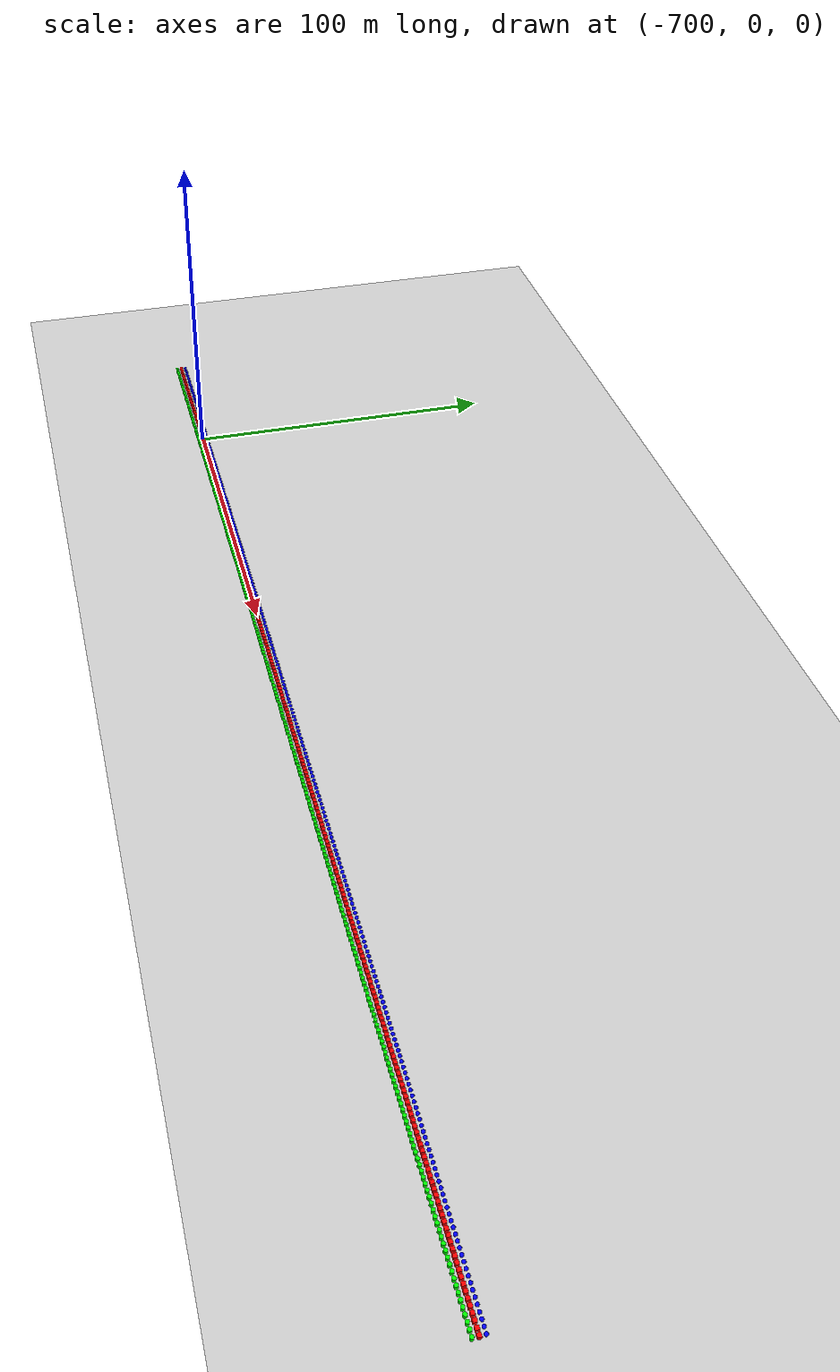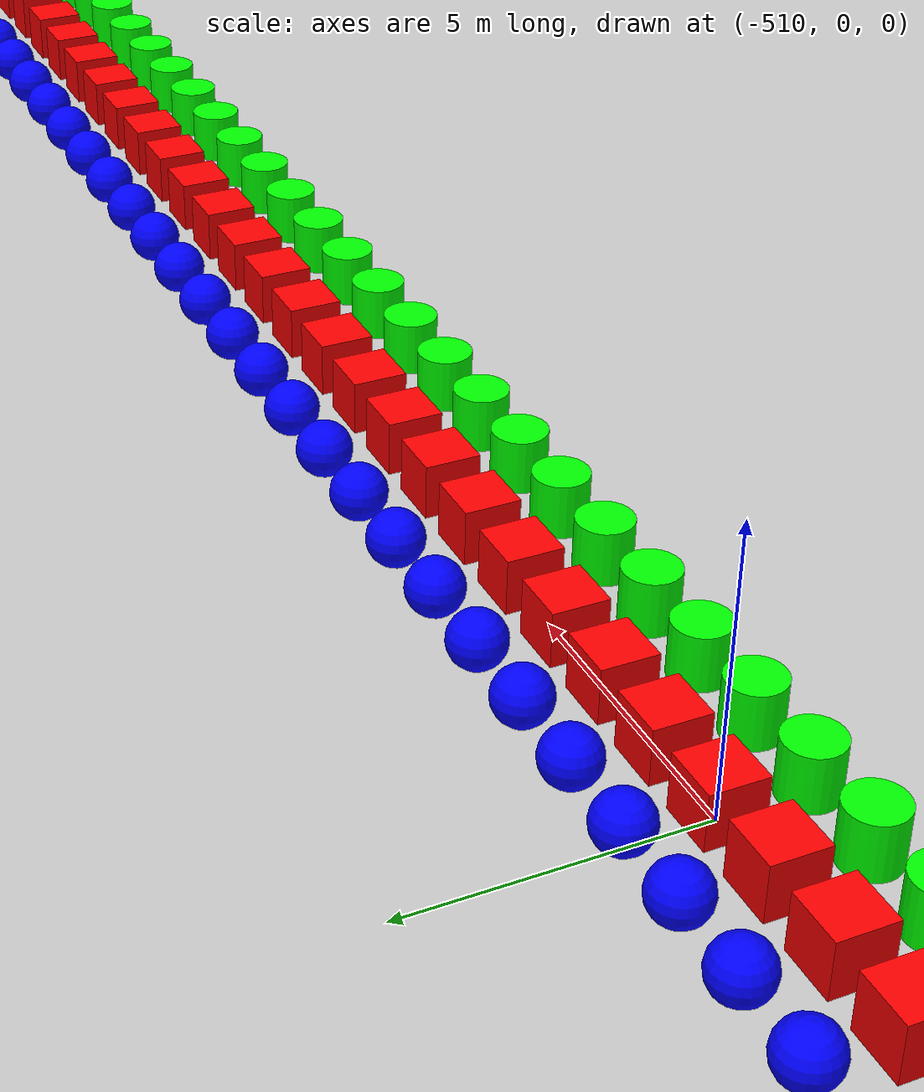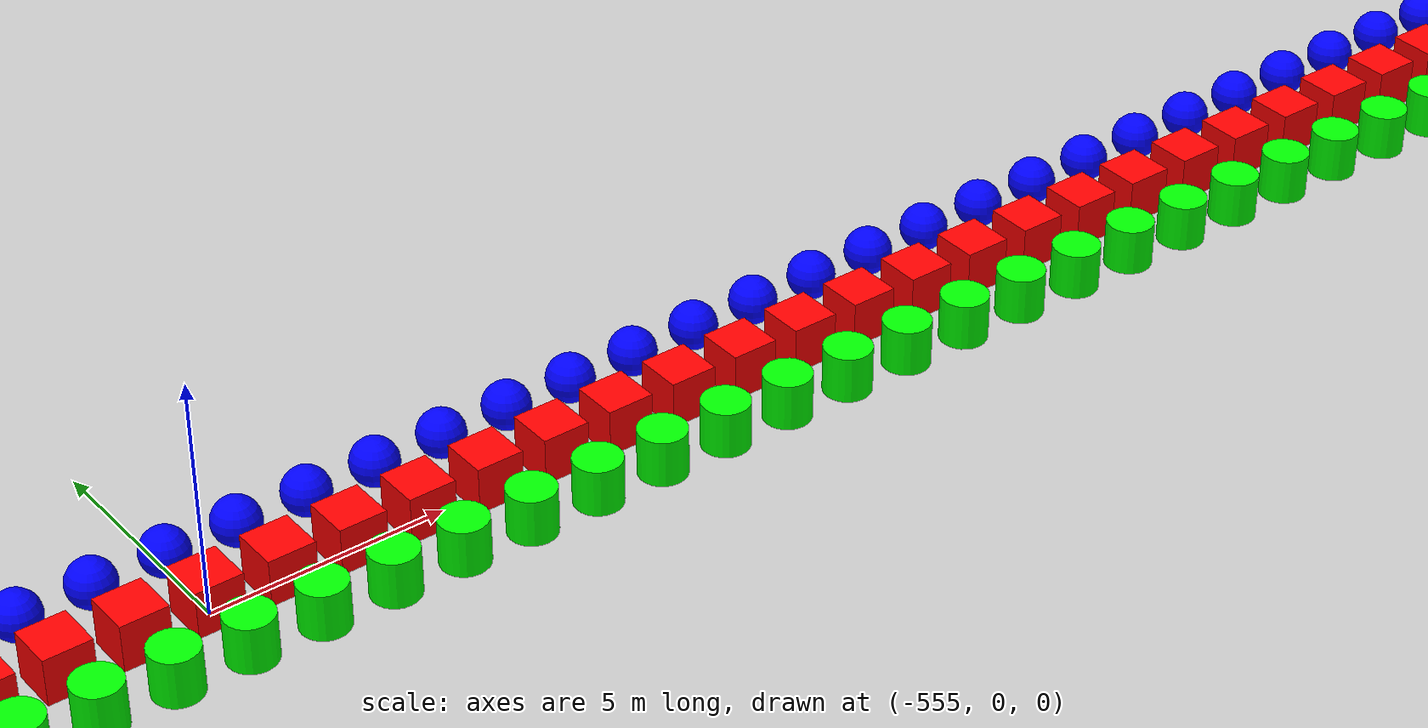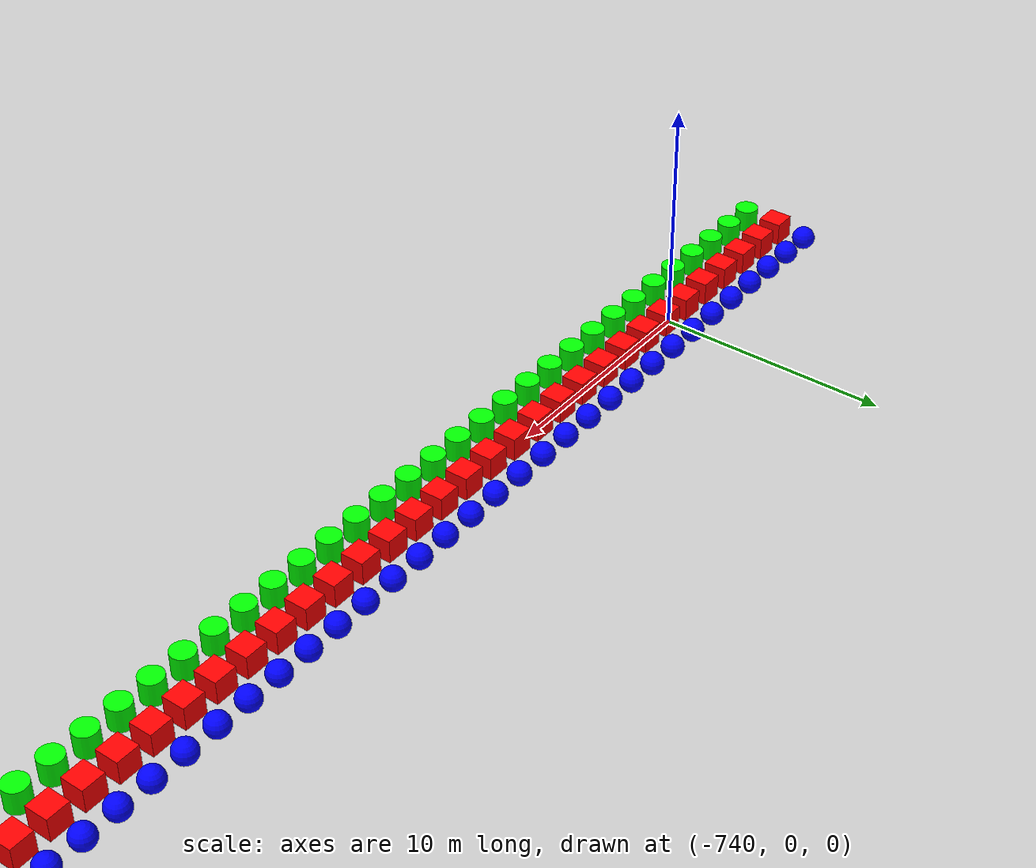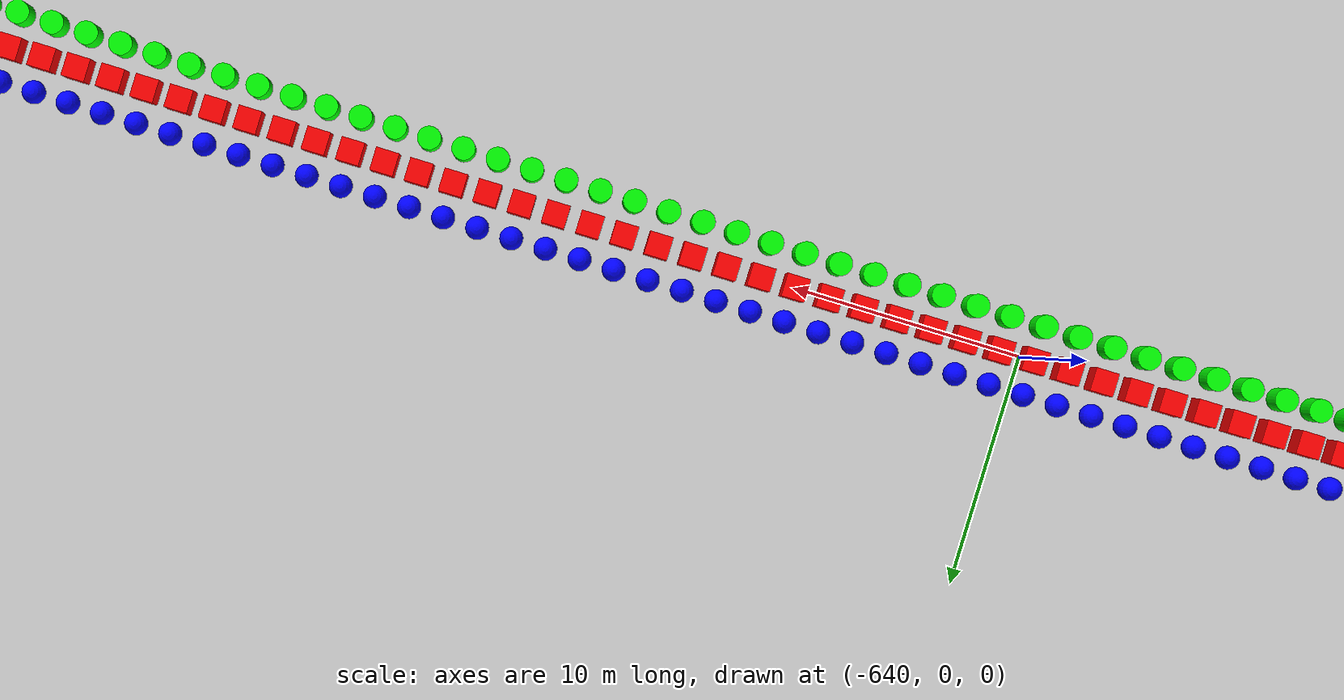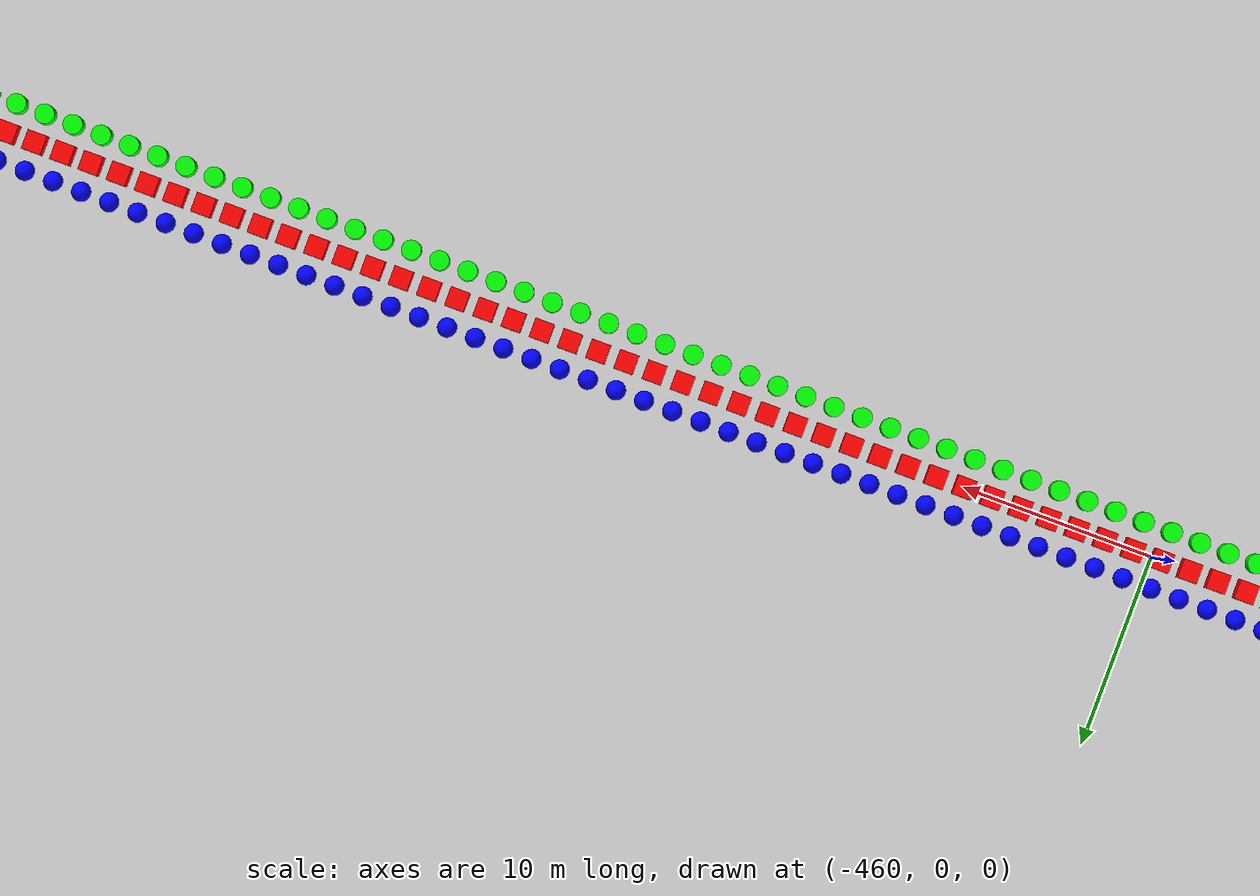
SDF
<?xml version="1.0" ?>
<sdf version="1.6">
  <world name="shapes">
    <model name="ground_plane">
      <static>true</static>
      <link name="link">
        <collision name="collision">
          <geometry>
            <plane>
              <normal>0 0 1</normal>
              <size>100 100</size>
            </plane>
          </geometry>
        </collision>
        <visual name="visual">
          <geometry>
            <plane>
              <normal>0 0 1</normal>
              <size>100 100</size>
            </plane>
          </geometry>
          <material>
            <ambient>0.8 0.8 0.8 1</ambient>
            <diffuse>0.8 0.8 0.8 1</diffuse>
            <specular>0.8 0.8 0.8 1</specular>
          </material>
        </visual>
      </link>
    </model>

    <model name="box_1">
      <static>false</static>
      <pose>-748.5 0 0.5 0 0 0</pose>
      <link name="box_link">
        <inertial>
          <inertia>
            <ixx>1</ixx>
            <ixy>0</ixy>
            <ixz>0</ixz>
            <iyy>1</iyy>
            <iyz>0</iyz>
            <izz>1</izz>
          </inertia>
          <mass>1.0</mass>
        </inertial>
        <collision name="box_collision">
          <geometry>
            <box>
              <size>1 1 1</size>
            </box>
          </geometry>
        </collision>

        <visual name="box_visual">
          <geometry>
            <box>
              <size>1 1 1</size>
            </box>
          </geometry>
          <material>
            <ambient>1 0 0 1</ambient>
            <diffuse>1 0 0 1</diffuse>
            <specular>1 0 0 1</specular>
          </material>
        </visual>
      </link>
    </model>

    <model name="cylinder_1">
      <static>false</static>
      <pose>-748.5 -1.5 0.5 0 0 0</pose>
      <link name="cylinder_link">
        <inertial>
          <inertia>
            <ixx>2</ixx>
            <ixy>0</ixy>
            <ixz>0</ixz>
            <iyy>2</iyy>
            <iyz>0</iyz>
            <izz>2</izz>
          </inertia>
          <mass>2.0</mass>
        </inertial>
        <collision name="cylinder_collision">
          <geometry>
            <cylinder>
              <radius>0.5</radius>
              <length>1.0</length>
            </cylinder>
          </geometry>
        </collision>

        <visual name="cylinder_visual">
          <geometry>
            <cylinder>
              <radius>0.5</radius>
              <length>1.0</length>
            </cylinder>
          </geometry>
          <material>
            <ambient>0 1 0 1</ambient>
            <diffuse>0 1 0 1</diffuse>
            <specular>0 1 0 1</specular>
          </material>
        </visual>
      </link>
    </model>

    <model name="sphere_1">
      <static>false</static>
      <pose>-748.5 1.5 0.5 0 0 0</pose>
      <link name="sphere_link">
        <inertial>
          <inertia>
            <ixx>3</ixx>
            <ixy>0</ixy>
            <ixz>0</ixz>
            <iyy>3</iyy>
            <iyz>0</iyz>
            <izz>3</izz>
          </inertia>
          <mass>3.0</mass>
        </inertial>
        <collision name="sphere_collision">
          <geometry>
            <sphere>
              <radius>0.5</radius>
            </sphere>
          </geometry>
        </collision>

        <visual name="sphere_visual">
          <geometry>
            <sphere>
              <radius>0.5</radius>
            </sphere>
          </geometry>
          <material>
            <ambient>0 0 1 1</ambient>
            <diffuse>0 0 1 1</diffuse>
            <specular>0 0 1 1</specular>
          </material>
        </visual>
      </link>
    </model>

    <model name="box_2">
      <static>false</static>
      <pose>-747.0 0 0.5 0 0 0</pose>
      <link name="box_link">
        <inertial>
          <inertia>
            <ixx>1</ixx>
            <ixy>0</ixy>
            <ixz>0</ixz>
            <iyy>1</iyy>
            <iyz>0</iyz>
            <izz>1</izz>
          </inertia>
          <mass>1.0</mass>
        </inertial>
        <collision name="box_collision">
          <geometry>
            <box>
              <size>1 1 1</size>
            </box>
          </geometry>
        </collision>

        <visual name="box_visual">
          <geometry>
            <box>
              <size>1 1 1</size>
            </box>
          </geometry>
          <material>
            <ambient>1 0 0 1</ambient>
            <diffuse>1 0 0 1</diffuse>
            <specular>1 0 0 1</specular>
          </material>
        </visual>
      </link>
    </model>

    <model name="cylinder_2">
      <static>false</static>
      <pose>-747.0 -1.5 0.5 0 0 0</pose>
      <link name="cylinder_link">
        <inertial>
          <inertia>
            <ixx>2</ixx>
            <ixy>0</ixy>
            <ixz>0</ixz>
            <iyy>2</iyy>
            <iyz>0</iyz>
            <izz>2</izz>
          </inertia>
          <mass>2.0</mass>
        </inertial>
        <collision name="cylinder_collision">
          <geometry>
            <cylinder>
              <radius>0.5</radius>
              <length>1.0</length>
            </cylinder>
          </geometry>
        </collision>

        <visual name="cylinder_visual">
          <geometry>
            <cylinder>
              <radius>0.5</radius>
              <length>1.0</length>
            </cylinder>
          </geometry>
          <material>
            <ambient>0 1 0 1</ambient>
            <diffuse>0 1 0 1</diffuse>
            <specular>0 1 0 1</specular>
          </material>
        </visual>
      </link>
    </model>

    <model name="sphere_2">
      <static>false</static>
      <pose>-747.0 1.5 0.5 0 0 0</pose>
      <link name="sphere_link">
        <inertial>
          <inertia>
            <ixx>3</ixx>
            <ixy>0</ixy>
            <ixz>0</ixz>
            <iyy>3</iyy>
            <iyz>0</iyz>
            <izz>3</izz>
          </inertia>
          <mass>3.0</mass>
        </inertial>
        <collision name="sphere_collision">
          <geometry>
            <sphere>
              <radius>0.5</radius>
            </sphere>
          </geometry>
        </collision>

        <visual name="sphere_visual">
          <geometry>
            <sphere>
              <radius>0.5</radius>
            </sphere>
          </geometry>
          <material>
            <ambient>0 0 1 1</ambient>
            <diffuse>0 0 1 1</diffuse>
            <specular>0 0 1 1</specular>
          </material>
        </visual>
      </link>
    </model>

    <model name="box_3">
      <static>false</static>
      <pose>-745.5 0 0.5 0 0 0</pose>
      <link name="box_link">
        <inertial>
          <inertia>
            <ixx>1</ixx>
            <ixy>0</ixy>
            <ixz>0</ixz>
            <iyy>1</iyy>
            <iyz>0</iyz>
            <izz>1</izz>
          </inertia>
          <mass>1.0</mass>
        </inertial>
        <collision name="box_collision">
          <geometry>
            <box>
              <size>1 1 1</size>
            </box>
          </geometry>
        </collision>

        <visual name="box_visual">
          <geometry>
            <box>
              <size>1 1 1</size>
            </box>
          </geometry>
          <material>
            <ambient>1 0 0 1</ambient>
            <diffuse>1 0 0 1</diffuse>
            <specular>1 0 0 1</specular>
          </material>
        </visual>
      </link>
    </model>

    <model name="cylinder_3">
      <static>false</static>
      <pose>-745.5 -1.5 0.5 0 0 0</pose>
      <link name="cylinder_link">
        <inertial>
          <inertia>
            <ixx>2</ixx>
            <ixy>0</ixy>
            <ixz>0</ixz>
            <iyy>2</iyy>
            <iyz>0</iyz>
            <izz>2</izz>
          </inertia>
          <mass>2.0</mass>
        </inertial>
        <collision name="cylinder_collision">
          <geometry>
            <cylinder>
              <radius>0.5</radius>
              <length>1.0</length>
            </cylinder>
          </geometry>
        </collision>

        <visual name="cylinder_visual">
          <geometry>
            <cylinder>
              <radius>0.5</radius>
              <length>1.0</length>
            </cylinder>
          </geometry>
          <material>
            <ambient>0 1 0 1</ambient>
            <diffuse>0 1 0 1</diffuse>
            <specular>0 1 0 1</specular>
          </material>
        </visual>
      </link>
    </model>

    <model name="sphere_3">
      <static>false</static>
      <pose>-745.5 1.5 0.5 0 0 0</pose>
      <link name="sphere_link">
        <inertial>
          <inertia>
            <ixx>3</ixx>
            <ixy>0</ixy>
            <ixz>0</ixz>
            <iyy>3</iyy>
            <iyz>0</iyz>
            <izz>3</izz>
          </inertia>
          <mass>3.0</mass>
        </inertial>
        <collision name="sphere_collision">
          <geometry>
            <sphere>
              <radius>0.5</radius>
            </sphere>
          </geometry>
        </collision>

        <visual name="sphere_visual">
          <geometry>
            <sphere>
              <radius>0.5</radius>
            </sphere>
          </geometry>
          <material>
            <ambient>0 0 1 1</ambient>
            <diffuse>0 0 1 1</diffuse>
            <specular>0 0 1 1</specular>
          </material>
        </visual>
      </link>
    </model>

    <model name="box_4">
      <static>false</static>
      <pose>-744.0 0 0.5 0 0 0</pose>
      <link name="box_link">
        <inertial>
          <inertia>
            <ixx>1</ixx>
            <ixy>0</ixy>
            <ixz>0</ixz>
            <iyy>1</iyy>
            <iyz>0</iyz>
            <izz>1</izz>
          </inertia>
          <mass>1.0</mass>
        </inertial>
        <collision name="box_collision">
          <geometry>
            <box>
              <size>1 1 1</size>
            </box>
          </geometry>
        </collision>

        <visual name="box_visual">
          <geometry>
            <box>
              <size>1 1 1</size>
            </box>
          </geometry>
          <material>
            <ambient>1 0 0 1</ambient>
            <diffuse>1 0 0 1</diffuse>
            <specular>1 0 0 1</specular>
          </material>
        </visual>
      </link>
    </model>

    <model name="cylinder_4">
      <static>false</static>
      <pose>-744.0 -1.5 0.5 0 0 0</pose>
      <link name="cylinder_link">
        <inertial>
          <inertia>
            <ixx>2</ixx>
            <ixy>0</ixy>
            <ixz>0</ixz>
            <iyy>2</iyy>
            <iyz>0</iyz>
            <izz>2</izz>
          </inertia>
          <mass>2.0</mass>
        </inertial>
        <collision name="cylinder_collision">
          <geometry>
            <cylinder>
              <radius>0.5</radius>
              <length>1.0</length>
            </cylinder>
          </geometry>
        </collision>

        <visual name="cylinder_visual">
          <geometry>
            <cylinder>
              <radius>0.5</radius>
              <length>1.0</length>
            </cylinder>
          </geometry>
          <material>
            <ambient>0 1 0 1</ambient>
            <diffuse>0 1 0 1</diffuse>
            <specular>0 1 0 1</specular>
          </material>
        </visual>
      </link>
    </model>

    <model name="sphere_4">
      <static>false</static>
      <pose>-744.0 1.5 0.5 0 0 0</pose>
      <link name="sphere_link">
        <inertial>
          <inertia>
            <ixx>3</ixx>
            <ixy>0</ixy>
            <ixz>0</ixz>
            <iyy>3</iyy>
            <iyz>0</iyz>
            <izz>3</izz>
          </inertia>
          <mass>3.0</mass>
        </inertial>
        <collision name="sphere_collision">
          <geometry>
            <sphere>
              <radius>0.5</radius>
            </sphere>
          </geometry>
        </collision>

        <visual name="sphere_visual">
          <geometry>
            <sphere>
              <radius>0.5</radius>
            </sphere>
          </geometry>
          <material>
            <ambient>0 0 1 1</ambient>
            <diffuse>0 0 1 1</diffuse>
            <specular>0 0 1 1</specular>
          </material>
        </visual>
      </link>
    </model>

    <model name="box_5">
      <static>false</static>
      <pose>-742.5 0 0.5 0 0 0</pose>
      <link name="box_link">
        <inertial>
          <inertia>
            <ixx>1</ixx>
            <ixy>0</ixy>
            <ixz>0</ixz>
            <iyy>1</iyy>
            <iyz>0</iyz>
            <izz>1</izz>
          </inertia>
          <mass>1.0</mass>
        </inertial>
        <collision name="box_collision">
          <geometry>
            <box>
              <size>1 1 1</size>
            </box>
          </geometry>
        </collision>

        <visual name="box_visual">
          <geometry>
            <box>
              <size>1 1 1</size>
            </box>
          </geometry>
          <material>
            <ambient>1 0 0 1</ambient>
            <diffuse>1 0 0 1</diffuse>
            <specular>1 0 0 1</specular>
          </material>
        </visual>
      </link>
    </model>

    <model name="cylinder_5">
      <static>false</static>
      <pose>-742.5 -1.5 0.5 0 0 0</pose>
      <link name="cylinder_link">
        <inertial>
          <inertia>
            <ixx>2</ixx>
            <ixy>0</ixy>
            <ixz>0</ixz>
            <iyy>2</iyy>
            <iyz>0</iyz>
            <izz>2</izz>
          </inertia>
          <mass>2.0</mass>
        </inertial>
        <collision name="cylinder_collision">
          <geometry>
            <cylinder>
              <radius>0.5</radius>
              <length>1.0</length>
            </cylinder>
          </geometry>
        </collision>

        <visual name="cylinder_visual">
          <geometry>
            <cylinder>
              <radius>0.5</radius>
              <length>1.0</length>
            </cylinder>
          </geometry>
          <material>
            <ambient>0 1 0 1</ambient>
            <diffuse>0 1 0 1</diffuse>
            <specular>0 1 0 1</specular>
          </material>
        </visual>
      </link>
    </model>

    <model name="sphere_5">
      <static>false</static>
      <pose>-742.5 1.5 0.5 0 0 0</pose>
      <link name="sphere_link">
        <inertial>
          <inertia>
            <ixx>3</ixx>
            <ixy>0</ixy>
            <ixz>0</ixz>
            <iyy>3</iyy>
            <iyz>0</iyz>
            <izz>3</izz>
          </inertia>
          <mass>3.0</mass>
        </inertial>
        <collision name="sphere_collision">
          <geometry>
            <sphere>
              <radius>0.5</radius>
            </sphere>
          </geometry>
        </collision>

        <visual name="sphere_visual">
          <geometry>
            <sphere>
              <radius>0.5</radius>
            </sphere>
          </geometry>
          <material>
            <ambient>0 0 1 1</ambient>
            <diffuse>0 0 1 1</diffuse>
            <specular>0 0 1 1</specular>
          </material>
        </visual>
      </link>
    </model>

    <model name="box_6">
      <static>false</static>
      <pose>-741.0 0 0.5 0 0 0</pose>
      <link name="box_link">
        <inertial>
          <inertia>
            <ixx>1</ixx>
            <ixy>0</ixy>
            <ixz>0</ixz>
            <iyy>1</iyy>
            <iyz>0</iyz>
            <izz>1</izz>
          </inertia>
          <mass>1.0</mass>
        </inertial>
        <collision name="box_collision">
          <geometry>
            <box>
              <size>1 1 1</size>
            </box>
          </geometry>
        </collision>

        <visual name="box_visual">
          <geometry>
            <box>
              <size>1 1 1</size>
            </box>
          </geometry>
          <material>
            <ambient>1 0 0 1</ambient>
            <diffuse>1 0 0 1</diffuse>
            <specular>1 0 0 1</specular>
          </material>
        </visual>
      </link>
    </model>

    <model name="cylinder_6">
      <static>false</static>
      <pose>-741.0 -1.5 0.5 0 0 0</pose>
      <link name="cylinder_link">
        <inertial>
          <inertia>
            <ixx>2</ixx>
            <ixy>0</ixy>
            <ixz>0</ixz>
            <iyy>2</iyy>
            <iyz>0</iyz>
            <izz>2</izz>
          </inertia>
          <mass>2.0</mass>
        </inertial>
        <collision name="cylinder_collision">
          <geometry>
            <cylinder>
              <radius>0.5</radius>
              <length>1.0</length>
            </cylinder>
          </geometry>
        </collision>

        <visual name="cylinder_visual">
          <geometry>
            <cylinder>
              <radius>0.5</radius>
              <length>1.0</length>
            </cylinder>
          </geometry>
          <material>
            <ambient>0 1 0 1</ambient>
            <diffuse>0 1 0 1</diffuse>
            <specular>0 1 0 1</specular>
          </material>
        </visual>
      </link>
    </model>

    <model name="sphere_6">
      <static>false</static>
      <pose>-741.0 1.5 0.5 0 0 0</pose>
      <link name="sphere_link">
        <inertial>
          <inertia>
            <ixx>3</ixx>
            <ixy>0</ixy>
            <ixz>0</ixz>
            <iyy>3</iyy>
            <iyz>0</iyz>
            <izz>3</izz>
          </inertia>
          <mass>3.0</mass>
        </inertial>
        <collision name="sphere_collision">
          <geometry>
            <sphere>
              <radius>0.5</radius>
            </sphere>
          </geometry>
        </collision>

        <visual name="sphere_visual">
          <geometry>
            <sphere>
              <radius>0.5</radius>
            </sphere>
          </geometry>
          <material>
            <ambient>0 0 1 1</ambient>
            <diffuse>0 0 1 1</diffuse>
            <specular>0 0 1 1</specular>
          </material>
        </visual>
      </link>
    </model>

    <model name="box_7">
      <static>false</static>
      <pose>-739.5 0 0.5 0 0 0</pose>
      <link name="box_link">
        <inertial>
          <inertia>
            <ixx>1</ixx>
            <ixy>0</ixy>
            <ixz>0</ixz>
            <iyy>1</iyy>
            <iyz>0</iyz>
            <izz>1</izz>
          </inertia>
          <mass>1.0</mass>
        </inertial>
        <collision name="box_collision">
          <geometry>
            <box>
              <size>1 1 1</size>
            </box>
          </geometry>
        </collision>

        <visual name="box_visual">
          <geometry>
            <box>
              <size>1 1 1</size>
            </box>
          </geometry>
          <material>
            <ambient>1 0 0 1</ambient>
            <diffuse>1 0 0 1</diffuse>
            <specular>1 0 0 1</specular>
          </material>
        </visual>
      </link>
    </model>

    <model name="cylinder_7">
      <static>false</static>
      <pose>-739.5 -1.5 0.5 0 0 0</pose>
      <link name="cylinder_link">
        <inertial>
          <inertia>
            <ixx>2</ixx>
            <ixy>0</ixy>
            <ixz>0</ixz>
            <iyy>2</iyy>
            <iyz>0</iyz>
            <izz>2</izz>
          </inertia>
          <mass>2.0</mass>
        </inertial>
        <collision name="cylinder_collision">
          <geometry>
            <cylinder>
              <radius>0.5</radius>
              <length>1.0</length>
            </cylinder>
          </geometry>
        </collision>

        <visual name="cylinder_visual">
          <geometry>
            <cylinder>
              <radius>0.5</radius>
              <length>1.0</length>
            </cylinder>
          </geometry>
          <material>
            <ambient>0 1 0 1</ambient>
            <diffuse>0 1 0 1</diffuse>
            <specular>0 1 0 1</specular>
          </material>
        </visual>
      </link>
    </model>

    <model name="sphere_7">
      <static>false</static>
      <pose>-739.5 1.5 0.5 0 0 0</pose>
      <link name="sphere_link">
        <inertial>
          <inertia>
            <ixx>3</ixx>
            <ixy>0</ixy>
            <ixz>0</ixz>
            <iyy>3</iyy>
            <iyz>0</iyz>
            <izz>3</izz>
          </inertia>
          <mass>3.0</mass>
        </inertial>
        <collision name="sphere_collision">
          <geometry>
            <sphere>
              <radius>0.5</radius>
            </sphere>
          </geometry>
        </collision>

        <visual name="sphere_visual">
          <geometry>
            <sphere>
              <radius>0.5</radius>
            </sphere>
          </geometry>
          <material>
            <ambient>0 0 1 1</ambient>
            <diffuse>0 0 1 1</diffuse>
            <specular>0 0 1 1</specular>
          </material>
        </visual>
      </link>
    </model>

    <model name="box_8">
      <static>false</static>
      <pose>-738.0 0 0.5 0 0 0</pose>
      <link name="box_link">
        <inertial>
          <inertia>
            <ixx>1</ixx>
            <ixy>0</ixy>
            <ixz>0</ixz>
            <iyy>1</iyy>
            <iyz>0</iyz>
            <izz>1</izz>
          </inertia>
          <mass>1.0</mass>
        </inertial>
        <collision name="box_collision">
          <geometry>
            <box>
              <size>1 1 1</size>
            </box>
          </geometry>
        </collision>

        <visual name="box_visual">
          <geometry>
            <box>
              <size>1 1 1</size>
            </box>
          </geometry>
          <material>
            <ambient>1 0 0 1</ambient>
            <diffuse>1 0 0 1</diffuse>
            <specular>1 0 0 1</specular>
          </material>
        </visual>
      </link>
    </model>

    <model name="cylinder_8">
      <static>false</static>
      <pose>-738.0 -1.5 0.5 0 0 0</pose>
      <link name="cylinder_link">
        <inertial>
          <inertia>
            <ixx>2</ixx>
            <ixy>0</ixy>
            <ixz>0</ixz>
            <iyy>2</iyy>
            <iyz>0</iyz>
            <izz>2</izz>
          </inertia>
          <mass>2.0</mass>
        </inertial>
        <collision name="cylinder_collision">
          <geometry>
            <cylinder>
              <radius>0.5</radius>
              <length>1.0</length>
            </cylinder>
          </geometry>
        </collision>

        <visual name="cylinder_visual">
          <geometry>
            <cylinder>
              <radius>0.5</radius>
              <length>1.0</length>
            </cylinder>
          </geometry>
          <material>
            <ambient>0 1 0 1</ambient>
            <diffuse>0 1 0 1</diffuse>
            <specular>0 1 0 1</specular>
          </material>
        </visual>
      </link>
    </model>

    <model name="sphere_8">
      <static>false</static>
      <pose>-738.0 1.5 0.5 0 0 0</pose>
      <link name="sphere_link">
        <inertial>
          <inertia>
            <ixx>3</ixx>
            <ixy>0</ixy>
            <ixz>0</ixz>
            <iyy>3</iyy>
            <iyz>0</iyz>
            <izz>3</izz>
          </inertia>
          <mass>3.0</mass>
        </inertial>
        <collision name="sphere_collision">
          <geometry>
            <sphere>
              <radius>0.5</radius>
            </sphere>
          </geometry>
        </collision>

        <visual name="sphere_visual">
          <geometry>
            <sphere>
              <radius>0.5</radius>
            </sphere>
          </geometry>
          <material>
            <ambient>0 0 1 1</ambient>
            <diffuse>0 0 1 1</diffuse>
            <specular>0 0 1 1</specular>
          </material>
        </visual>
      </link>
    </model>

    <model name="box_9">
      <static>false</static>
      <pose>-736.5 0 0.5 0 0 0</pose>
      <link name="box_link">
        <inertial>
          <inertia>
            <ixx>1</ixx>
            <ixy>0</ixy>
            <ixz>0</ixz>
            <iyy>1</iyy>
            <iyz>0</iyz>
            <izz>1</izz>
          </inertia>
          <mass>1.0</mass>
        </inertial>
        <collision name="box_collision">
          <geometry>
            <box>
              <size>1 1 1</size>
            </box>
          </geometry>
        </collision>

        <visual name="box_visual">
          <geometry>
            <box>
              <size>1 1 1</size>
            </box>
          </geometry>
          <material>
            <ambient>1 0 0 1</ambient>
            <diffuse>1 0 0 1</diffuse>
            <specular>1 0 0 1</specular>
          </material>
        </visual>
      </link>
    </model>

    <model name="cylinder_9">
      <static>false</static>
      <pose>-736.5 -1.5 0.5 0 0 0</pose>
      <link name="cylinder_link">
        <inertial>
          <inertia>
            <ixx>2</ixx>
            <ixy>0</ixy>
            <ixz>0</ixz>
            <iyy>2</iyy>
            <iyz>0</iyz>
            <izz>2</izz>
          </inertia>
          <mass>2.0</mass>
        </inertial>
        <collision name="cylinder_collision">
          <geometry>
            <cylinder>
              <radius>0.5</radius>
              <length>1.0</length>
            </cylinder>
          </geometry>
        </collision>

        <visual name="cylinder_visual">
          <geometry>
            <cylinder>
              <radius>0.5</radius>
              <length>1.0</length>
            </cylinder>
          </geometry>
          <material>
            <ambient>0 1 0 1</ambient>
            <diffuse>0 1 0 1</diffuse>
            <specular>0 1 0 1</specular>
          </material>
        </visual>
      </link>
    </model>

    <model name="sphere_9">
      <static>false</static>
      <pose>-736.5 1.5 0.5 0 0 0</pose>
      <link name="sphere_link">
        <inertial>
          <inertia>
            <ixx>3</ixx>
            <ixy>0</ixy>
            <ixz>0</ixz>
            <iyy>3</iyy>
            <iyz>0</iyz>
            <izz>3</izz>
          </inertia>
          <mass>3.0</mass>
        </inertial>
        <collision name="sphere_collision">
          <geometry>
            <sphere>
              <radius>0.5</radius>
            </sphere>
          </geometry>
        </collision>

        <visual name="sphere_visual">
          <geometry>
            <sphere>
              <radius>0.5</radius>
            </sphere>
          </geometry>
          <material>
            <ambient>0 0 1 1</ambient>
            <diffuse>0 0 1 1</diffuse>
            <specular>0 0 1 1</specular>
          </material>
        </visual>
      </link>
    </model>

    <model name="box_10">
      <static>false</static>
      <pose>-735.0 0 0.5 0 0 0</pose>
      <link name="box_link">
        <inertial>
          <inertia>
            <ixx>1</ixx>
            <ixy>0</ixy>
            <ixz>0</ixz>
            <iyy>1</iyy>
            <iyz>0</iyz>
            <izz>1</izz>
          </inertia>
          <mass>1.0</mass>
        </inertial>
        <collision name="box_collision">
          <geometry>
            <box>
              <size>1 1 1</size>
            </box>
          </geometry>
        </collision>

        <visual name="box_visual">
          <geometry>
            <box>
              <size>1 1 1</size>
            </box>
          </geometry>
          <material>
            <ambient>1 0 0 1</ambient>
            <diffuse>1 0 0 1</diffuse>
            <specular>1 0 0 1</specular>
          </material>
        </visual>
      </link>
    </model>

    <model name="cylinder_10">
      <static>false</static>
      <pose>-735.0 -1.5 0.5 0 0 0</pose>
      <link name="cylinder_link">
        <inertial>
          <inertia>
            <ixx>2</ixx>
            <ixy>0</ixy>
            <ixz>0</ixz>
            <iyy>2</iyy>
            <iyz>0</iyz>
            <izz>2</izz>
          </inertia>
          <mass>2.0</mass>
        </inertial>
        <collision name="cylinder_collision">
          <geometry>
            <cylinder>
              <radius>0.5</radius>
              <length>1.0</length>
            </cylinder>
          </geometry>
        </collision>

        <visual name="cylinder_visual">
          <geometry>
            <cylinder>
              <radius>0.5</radius>
              <length>1.0</length>
            </cylinder>
          </geometry>
          <material>
            <ambient>0 1 0 1</ambient>
            <diffuse>0 1 0 1</diffuse>
            <specular>0 1 0 1</specular>
          </material>
        </visual>
      </link>
    </model>

    <model name="sphere_10">
      <static>false</static>
      <pose>-735.0 1.5 0.5 0 0 0</pose>
      <link name="sphere_link">
        <inertial>
          <inertia>
            <ixx>3</ixx>
            <ixy>0</ixy>
            <ixz>0</ixz>
            <iyy>3</iyy>
            <iyz>0</iyz>
            <izz>3</izz>
          </inertia>
          <mass>3.0</mass>
        </inertial>
        <collision name="sphere_collision">
          <geometry>
            <sphere>
              <radius>0.5</radius>
            </sphere>
          </geometry>
        </collision>

        <visual name="sphere_visual">
          <geometry>
            <sphere>
              <radius>0.5</radius>
            </sphere>
          </geometry>
          <material>
            <ambient>0 0 1 1</ambient>
            <diffuse>0 0 1 1</diffuse>
            <specular>0 0 1 1</specular>
          </material>
        </visual>
      </link>
    </model>

    <model name="box_11">
      <static>false</static>
      <pose>-733.5 0 0.5 0 0 0</pose>
      <link name="box_link">
        <inertial>
          <inertia>
            <ixx>1</ixx>
            <ixy>0</ixy>
            <ixz>0</ixz>
            <iyy>1</iyy>
            <iyz>0</iyz>
            <izz>1</izz>
          </inertia>
          <mass>1.0</mass>
        </inertial>
        <collision name="box_collision">
          <geometry>
            <box>
              <size>1 1 1</size>
            </box>
          </geometry>
        </collision>

        <visual name="box_visual">
          <geometry>
            <box>
              <size>1 1 1</size>
            </box>
          </geometry>
          <material>
            <ambient>1 0 0 1</ambient>
            <diffuse>1 0 0 1</diffuse>
            <specular>1 0 0 1</specular>
          </material>
        </visual>
      </link>
    </model>

    <model name="cylinder_11">
      <static>false</static>
      <pose>-733.5 -1.5 0.5 0 0 0</pose>
      <link name="cylinder_link">
        <inertial>
          <inertia>
            <ixx>2</ixx>
            <ixy>0</ixy>
            <ixz>0</ixz>
            <iyy>2</iyy>
            <iyz>0</iyz>
            <izz>2</izz>
          </inertia>
          <mass>2.0</mass>
        </inertial>
        <collision name="cylinder_collision">
          <geometry>
            <cylinder>
              <radius>0.5</radius>
              <length>1.0</length>
            </cylinder>
          </geometry>
        </collision>

        <visual name="cylinder_visual">
          <geometry>
            <cylinder>
              <radius>0.5</radius>
              <length>1.0</length>
            </cylinder>
          </geometry>
          <material>
            <ambient>0 1 0 1</ambient>
            <diffuse>0 1 0 1</diffuse>
            <specular>0 1 0 1</specular>
          </material>
        </visual>
      </link>
    </model>

    <model name="sphere_11">
      <static>false</static>
      <pose>-733.5 1.5 0.5 0 0 0</pose>
      <link name="sphere_link">
        <inertial>
          <inertia>
            <ixx>3</ixx>
            <ixy>0</ixy>
            <ixz>0</ixz>
            <iyy>3</iyy>
            <iyz>0</iyz>
            <izz>3</izz>
          </inertia>
          <mass>3.0</mass>
        </inertial>
        <collision name="sphere_collision">
          <geometry>
            <sphere>
              <radius>0.5</radius>
            </sphere>
          </geometry>
        </collision>

        <visual name="sphere_visual">
          <geometry>
            <sphere>
              <radius>0.5</radius>
            </sphere>
          </geometry>
          <material>
            <ambient>0 0 1 1</ambient>
            <diffuse>0 0 1 1</diffuse>
            <specular>0 0 1 1</specular>
          </material>
        </visual>
      </link>
    </model>

    <model name="box_12">
      <static>false</static>
      <pose>-732.0 0 0.5 0 0 0</pose>
      <link name="box_link">
        <inertial>
          <inertia>
            <ixx>1</ixx>
            <ixy>0</ixy>
            <ixz>0</ixz>
            <iyy>1</iyy>
            <iyz>0</iyz>
            <izz>1</izz>
          </inertia>
          <mass>1.0</mass>
        </inertial>
        <collision name="box_collision">
          <geometry>
            <box>
              <size>1 1 1</size>
            </box>
          </geometry>
        </collision>

        <visual name="box_visual">
          <geometry>
            <box>
              <size>1 1 1</size>
            </box>
          </geometry>
          <material>
            <ambient>1 0 0 1</ambient>
            <diffuse>1 0 0 1</diffuse>
            <specular>1 0 0 1</specular>
          </material>
        </visual>
      </link>
    </model>

    <model name="cylinder_12">
      <static>false</static>
      <pose>-732.0 -1.5 0.5 0 0 0</pose>
      <link name="cylinder_link">
        <inertial>
          <inertia>
            <ixx>2</ixx>
            <ixy>0</ixy>
            <ixz>0</ixz>
            <iyy>2</iyy>
            <iyz>0</iyz>
            <izz>2</izz>
          </inertia>
          <mass>2.0</mass>
        </inertial>
        <collision name="cylinder_collision">
          <geometry>
            <cylinder>
              <radius>0.5</radius>
              <length>1.0</length>
            </cylinder>
          </geometry>
        </collision>

        <visual name="cylinder_visual">
          <geometry>
            <cylinder>
              <radius>0.5</radius>
              <length>1.0</length>
            </cylinder>
          </geometry>
          <material>
            <ambient>0 1 0 1</ambient>
            <diffuse>0 1 0 1</diffuse>
            <specular>0 1 0 1</specular>
          </material>
        </visual>
      </link>
    </model>

    <model name="sphere_12">
      <static>false</static>
      <pose>-732.0 1.5 0.5 0 0 0</pose>
      <link name="sphere_link">
        <inertial>
          <inertia>
            <ixx>3</ixx>
            <ixy>0</ixy>
            <ixz>0</ixz>
            <iyy>3</iyy>
            <iyz>0</iyz>
            <izz>3</izz>
          </inertia>
          <mass>3.0</mass>
        </inertial>
        <collision name="sphere_collision">
          <geometry>
            <sphere>
              <radius>0.5</radius>
            </sphere>
          </geometry>
        </collision>

        <visual name="sphere_visual">
          <geometry>
            <sphere>
              <radius>0.5</radius>
            </sphere>
          </geometry>
          <material>
            <ambient>0 0 1 1</ambient>
            <diffuse>0 0 1 1</diffuse>
            <specular>0 0 1 1</specular>
          </material>
        </visual>
      </link>
    </model>

    <model name="box_13">
      <static>false</static>
      <pose>-730.5 0 0.5 0 0 0</pose>
      <link name="box_link">
        <inertial>
          <inertia>
            <ixx>1</ixx>
            <ixy>0</ixy>
            <ixz>0</ixz>
            <iyy>1</iyy>
            <iyz>0</iyz>
            <izz>1</izz>
          </inertia>
          <mass>1.0</mass>
        </inertial>
        <collision name="box_collision">
          <geometry>
            <box>
              <size>1 1 1</size>
            </box>
          </geometry>
        </collision>

        <visual name="box_visual">
          <geometry>
            <box>
              <size>1 1 1</size>
            </box>
          </geometry>
          <material>
            <ambient>1 0 0 1</ambient>
            <diffuse>1 0 0 1</diffuse>
            <specular>1 0 0 1</specular>
          </material>
        </visual>
      </link>
    </model>

    <model name="cylinder_13">
      <static>false</static>
      <pose>-730.5 -1.5 0.5 0 0 0</pose>
      <link name="cylinder_link">
        <inertial>
          <inertia>
            <ixx>2</ixx>
            <ixy>0</ixy>
            <ixz>0</ixz>
            <iyy>2</iyy>
            <iyz>0</iyz>
            <izz>2</izz>
          </inertia>
          <mass>2.0</mass>
        </inertial>
        <collision name="cylinder_collision">
          <geometry>
            <cylinder>
              <radius>0.5</radius>
              <length>1.0</length>
            </cylinder>
          </geometry>
        </collision>

        <visual name="cylinder_visual">
          <geometry>
            <cylinder>
              <radius>0.5</radius>
              <length>1.0</length>
            </cylinder>
          </geometry>
          <material>
            <ambient>0 1 0 1</ambient>
            <diffuse>0 1 0 1</diffuse>
            <specular>0 1 0 1</specular>
          </material>
        </visual>
      </link>
    </model>

    <model name="sphere_13">
      <static>false</static>
      <pose>-730.5 1.5 0.5 0 0 0</pose>
      <link name="sphere_link">
        <inertial>
          <inertia>
            <ixx>3</ixx>
            <ixy>0</ixy>
            <ixz>0</ixz>
            <iyy>3</iyy>
            <iyz>0</iyz>
            <izz>3</izz>
          </inertia>
          <mass>3.0</mass>
        </inertial>
        <collision name="sphere_collision">
          <geometry>
            <sphere>
              <radius>0.5</radius>
            </sphere>
          </geometry>
        </collision>

        <visual name="sphere_visual">
          <geometry>
            <sphere>
              <radius>0.5</radius>
            </sphere>
          </geometry>
          <material>
            <ambient>0 0 1 1</ambient>
            <diffuse>0 0 1 1</diffuse>
            <specular>0 0 1 1</specular>
          </material>
        </visual>
      </link>
    </model>

    <model name="box_14">
      <static>false</static>
      <pose>-729.0 0 0.5 0 0 0</pose>
      <link name="box_link">
        <inertial>
          <inertia>
            <ixx>1</ixx>
            <ixy>0</ixy>
            <ixz>0</ixz>
            <iyy>1</iyy>
            <iyz>0</iyz>
            <izz>1</izz>
          </inertia>
          <mass>1.0</mass>
        </inertial>
        <collision name="box_collision">
          <geometry>
            <box>
              <size>1 1 1</size>
            </box>
          </geometry>
        </collision>

        <visual name="box_visual">
          <geometry>
            <box>
              <size>1 1 1</size>
            </box>
          </geometry>
          <material>
            <ambient>1 0 0 1</ambient>
            <diffuse>1 0 0 1</diffuse>
            <specular>1 0 0 1</specular>
          </material>
        </visual>
      </link>
    </model>

    <model name="cylinder_14">
      <static>false</static>
      <pose>-729.0 -1.5 0.5 0 0 0</pose>
      <link name="cylinder_link">
        <inertial>
          <inertia>
            <ixx>2</ixx>
            <ixy>0</ixy>
            <ixz>0</ixz>
            <iyy>2</iyy>
            <iyz>0</iyz>
            <izz>2</izz>
          </inertia>
          <mass>2.0</mass>
        </inertial>
        <collision name="cylinder_collision">
          <geometry>
            <cylinder>
              <radius>0.5</radius>
              <length>1.0</length>
            </cylinder>
          </geometry>
        </collision>

        <visual name="cylinder_visual">
          <geometry>
            <cylinder>
              <radius>0.5</radius>
              <length>1.0</length>
            </cylinder>
          </geometry>
          <material>
            <ambient>0 1 0 1</ambient>
            <diffuse>0 1 0 1</diffuse>
            <specular>0 1 0 1</specular>
          </material>
        </visual>
      </link>
    </model>

    <model name="sphere_14">
      <static>false</static>
      <pose>-729.0 1.5 0.5 0 0 0</pose>
      <link name="sphere_link">
        <inertial>
          <inertia>
            <ixx>3</ixx>
            <ixy>0</ixy>
            <ixz>0</ixz>
            <iyy>3</iyy>
            <iyz>0</iyz>
            <izz>3</izz>
          </inertia>
          <mass>3.0</mass>
        </inertial>
        <collision name="sphere_collision">
          <geometry>
            <sphere>
              <radius>0.5</radius>
            </sphere>
          </geometry>
        </collision>

        <visual name="sphere_visual">
          <geometry>
            <sphere>
              <radius>0.5</radius>
            </sphere>
          </geometry>
          <material>
            <ambient>0 0 1 1</ambient>
            <diffuse>0 0 1 1</diffuse>
            <specular>0 0 1 1</specular>
          </material>
        </visual>
      </link>
    </model>

    <model name="box_15">
      <static>false</static>
      <pose>-727.5 0 0.5 0 0 0</pose>
      <link name="box_link">
        <inertial>
          <inertia>
            <ixx>1</ixx>
            <ixy>0</ixy>
            <ixz>0</ixz>
            <iyy>1</iyy>
            <iyz>0</iyz>
            <izz>1</izz>
          </inertia>
          <mass>1.0</mass>
        </inertial>
        <collision name="box_collision">
          <geometry>
            <box>
              <size>1 1 1</size>
            </box>
          </geometry>
        </collision>

        <visual name="box_visual">
          <geometry>
            <box>
              <size>1 1 1</size>
            </box>
          </geometry>
          <material>
            <ambient>1 0 0 1</ambient>
            <diffuse>1 0 0 1</diffuse>
            <specular>1 0 0 1</specular>
          </material>
        </visual>
      </link>
    </model>

    <model name="cylinder_15">
      <static>false</static>
      <pose>-727.5 -1.5 0.5 0 0 0</pose>
      <link name="cylinder_link">
        <inertial>
          <inertia>
            <ixx>2</ixx>
            <ixy>0</ixy>
            <ixz>0</ixz>
            <iyy>2</iyy>
            <iyz>0</iyz>
            <izz>2</izz>
          </inertia>
          <mass>2.0</mass>
        </inertial>
        <collision name="cylinder_collision">
          <geometry>
            <cylinder>
              <radius>0.5</radius>
              <length>1.0</length>
            </cylinder>
          </geometry>
        </collision>

        <visual name="cylinder_visual">
          <geometry>
            <cylinder>
              <radius>0.5</radius>
              <length>1.0</length>
            </cylinder>
          </geometry>
          <material>
            <ambient>0 1 0 1</ambient>
            <diffuse>0 1 0 1</diffuse>
            <specular>0 1 0 1</specular>
          </material>
        </visual>
      </link>
    </model>

    <model name="sphere_15">
      <static>false</static>
      <pose>-727.5 1.5 0.5 0 0 0</pose>
      <link name="sphere_link">
        <inertial>
          <inertia>
            <ixx>3</ixx>
            <ixy>0</ixy>
            <ixz>0</ixz>
            <iyy>3</iyy>
            <iyz>0</iyz>
            <izz>3</izz>
          </inertia>
          <mass>3.0</mass>
        </inertial>
        <collision name="sphere_collision">
          <geometry>
            <sphere>
              <radius>0.5</radius>
            </sphere>
          </geometry>
        </collision>

        <visual name="sphere_visual">
          <geometry>
            <sphere>
              <radius>0.5</radius>
            </sphere>
          </geometry>
          <material>
            <ambient>0 0 1 1</ambient>
            <diffuse>0 0 1 1</diffuse>
            <specular>0 0 1 1</specular>
          </material>
        </visual>
      </link>
    </model>

    <model name="box_16">
      <static>false</static>
      <pose>-726.0 0 0.5 0 0 0</pose>
      <link name="box_link">
        <inertial>
          <inertia>
            <ixx>1</ixx>
            <ixy>0</ixy>
            <ixz>0</ixz>
            <iyy>1</iyy>
            <iyz>0</iyz>
            <izz>1</izz>
          </inertia>
          <mass>1.0</mass>
        </inertial>
        <collision name="box_collision">
          <geometry>
            <box>
              <size>1 1 1</size>
            </box>
          </geometry>
        </collision>

        <visual name="box_visual">
          <geometry>
            <box>
              <size>1 1 1</size>
            </box>
          </geometry>
          <material>
            <ambient>1 0 0 1</ambient>
            <diffuse>1 0 0 1</diffuse>
            <specular>1 0 0 1</specular>
          </material>
        </visual>
      </link>
    </model>

    <model name="cylinder_16">
      <static>false</static>
      <pose>-726.0 -1.5 0.5 0 0 0</pose>
      <link name="cylinder_link">
        <inertial>
          <inertia>
            <ixx>2</ixx>
            <ixy>0</ixy>
            <ixz>0</ixz>
            <iyy>2</iyy>
            <iyz>0</iyz>
            <izz>2</izz>
          </inertia>
          <mass>2.0</mass>
        </inertial>
        <collision name="cylinder_collision">
          <geometry>
            <cylinder>
              <radius>0.5</radius>
              <length>1.0</length>
            </cylinder>
          </geometry>
        </collision>

        <visual name="cylinder_visual">
          <geometry>
            <cylinder>
              <radius>0.5</radius>
              <length>1.0</length>
            </cylinder>
          </geometry>
          <material>
            <ambient>0 1 0 1</ambient>
            <diffuse>0 1 0 1</diffuse>
            <specular>0 1 0 1</specular>
          </material>
        </visual>
      </link>
    </model>

    <model name="sphere_16">
      <static>false</static>
      <pose>-726.0 1.5 0.5 0 0 0</pose>
      <link name="sphere_link">
        <inertial>
          <inertia>
            <ixx>3</ixx>
            <ixy>0</ixy>
            <ixz>0</ixz>
            <iyy>3</iyy>
            <iyz>0</iyz>
            <izz>3</izz>
          </inertia>
          <mass>3.0</mass>
        </inertial>
        <collision name="sphere_collision">
          <geometry>
            <sphere>
              <radius>0.5</radius>
            </sphere>
          </geometry>
        </collision>

        <visual name="sphere_visual">
          <geometry>
            <sphere>
              <radius>0.5</radius>
            </sphere>
          </geometry>
          <material>
            <ambient>0 0 1 1</ambient>
            <diffuse>0 0 1 1</diffuse>
            <specular>0 0 1 1</specular>
          </material>
        </visual>
      </link>
    </model>

    <model name="box_17">
      <static>false</static>
      <pose>-724.5 0 0.5 0 0 0</pose>
      <link name="box_link">
        <inertial>
          <inertia>
            <ixx>1</ixx>
            <ixy>0</ixy>
            <ixz>0</ixz>
            <iyy>1</iyy>
            <iyz>0</iyz>
            <izz>1</izz>
          </inertia>
          <mass>1.0</mass>
        </inertial>
        <collision name="box_collision">
          <geometry>
            <box>
              <size>1 1 1</size>
            </box>
          </geometry>
        </collision>

        <visual name="box_visual">
          <geometry>
            <box>
              <size>1 1 1</size>
            </box>
          </geometry>
          <material>
            <ambient>1 0 0 1</ambient>
            <diffuse>1 0 0 1</diffuse>
            <specular>1 0 0 1</specular>
          </material>
        </visual>
      </link>
    </model>

    <model name="cylinder_17">
      <static>false</static>
      <pose>-724.5 -1.5 0.5 0 0 0</pose>
      <link name="cylinder_link">
        <inertial>
          <inertia>
            <ixx>2</ixx>
            <ixy>0</ixy>
            <ixz>0</ixz>
            <iyy>2</iyy>
            <iyz>0</iyz>
            <izz>2</izz>
          </inertia>
          <mass>2.0</mass>
        </inertial>
        <collision name="cylinder_collision">
          <geometry>
            <cylinder>
              <radius>0.5</radius>
              <length>1.0</length>
            </cylinder>
          </geometry>
        </collision>

        <visual name="cylinder_visual">
          <geometry>
            <cylinder>
              <radius>0.5</radius>
              <length>1.0</length>
            </cylinder>
          </geometry>
          <material>
            <ambient>0 1 0 1</ambient>
            <diffuse>0 1 0 1</diffuse>
            <specular>0 1 0 1</specular>
          </material>
        </visual>
      </link>
    </model>

    <model name="sphere_17">
      <static>false</static>
      <pose>-724.5 1.5 0.5 0 0 0</pose>
      <link name="sphere_link">
        <inertial>
          <inertia>
            <ixx>3</ixx>
            <ixy>0</ixy>
            <ixz>0</ixz>
            <iyy>3</iyy>
            <iyz>0</iyz>
            <izz>3</izz>
          </inertia>
          <mass>3.0</mass>
        </inertial>
        <collision name="sphere_collision">
          <geometry>
            <sphere>
              <radius>0.5</radius>
            </sphere>
          </geometry>
        </collision>

        <visual name="sphere_visual">
          <geometry>
            <sphere>
              <radius>0.5</radius>
            </sphere>
          </geometry>
          <material>
            <ambient>0 0 1 1</ambient>
            <diffuse>0 0 1 1</diffuse>
            <specular>0 0 1 1</specular>
          </material>
        </visual>
      </link>
    </model>

    <model name="box_18">
      <static>false</static>
      <pose>-723.0 0 0.5 0 0 0</pose>
      <link name="box_link">
        <inertial>
          <inertia>
            <ixx>1</ixx>
            <ixy>0</ixy>
            <ixz>0</ixz>
            <iyy>1</iyy>
            <iyz>0</iyz>
            <izz>1</izz>
          </inertia>
          <mass>1.0</mass>
        </inertial>
        <collision name="box_collision">
          <geometry>
            <box>
              <size>1 1 1</size>
            </box>
          </geometry>
        </collision>

        <visual name="box_visual">
          <geometry>
            <box>
              <size>1 1 1</size>
            </box>
          </geometry>
          <material>
            <ambient>1 0 0 1</ambient>
            <diffuse>1 0 0 1</diffuse>
            <specular>1 0 0 1</specular>
          </material>
        </visual>
      </link>
    </model>

    <model name="cylinder_18">
      <static>false</static>
      <pose>-723.0 -1.5 0.5 0 0 0</pose>
      <link name="cylinder_link">
        <inertial>
          <inertia>
            <ixx>2</ixx>
            <ixy>0</ixy>
            <ixz>0</ixz>
            <iyy>2</iyy>
            <iyz>0</iyz>
            <izz>2</izz>
          </inertia>
          <mass>2.0</mass>
        </inertial>
        <collision name="cylinder_collision">
          <geometry>
            <cylinder>
              <radius>0.5</radius>
              <length>1.0</length>
            </cylinder>
          </geometry>
        </collision>

        <visual name="cylinder_visual">
          <geometry>
            <cylinder>
              <radius>0.5</radius>
              <length>1.0</length>
            </cylinder>
          </geometry>
          <material>
            <ambient>0 1 0 1</ambient>
            <diffuse>0 1 0 1</diffuse>
            <specular>0 1 0 1</specular>
          </material>
        </visual>
      </link>
    </model>

    <model name="sphere_18">
      <static>false</static>
      <pose>-723.0 1.5 0.5 0 0 0</pose>
      <link name="sphere_link">
        <inertial>
          <inertia>
            <ixx>3</ixx>
            <ixy>0</ixy>
            <ixz>0</ixz>
            <iyy>3</iyy>
            <iyz>0</iyz>
            <izz>3</izz>
          </inertia>
          <mass>3.0</mass>
        </inertial>
        <collision name="sphere_collision">
          <geometry>
            <sphere>
              <radius>0.5</radius>
            </sphere>
          </geometry>
        </collision>

        <visual name="sphere_visual">
          <geometry>
            <sphere>
              <radius>0.5</radius>
            </sphere>
          </geometry>
          <material>
            <ambient>0 0 1 1</ambient>
            <diffuse>0 0 1 1</diffuse>
            <specular>0 0 1 1</specular>
          </material>
        </visual>
      </link>
    </model>

    <model name="box_19">
      <static>false</static>
      <pose>-721.5 0 0.5 0 0 0</pose>
      <link name="box_link">
        <inertial>
          <inertia>
            <ixx>1</ixx>
            <ixy>0</ixy>
            <ixz>0</ixz>
            <iyy>1</iyy>
            <iyz>0</iyz>
            <izz>1</izz>
          </inertia>
          <mass>1.0</mass>
        </inertial>
        <collision name="box_collision">
          <geometry>
            <box>
              <size>1 1 1</size>
            </box>
          </geometry>
        </collision>

        <visual name="box_visual">
          <geometry>
            <box>
              <size>1 1 1</size>
            </box>
          </geometry>
          <material>
            <ambient>1 0 0 1</ambient>
            <diffuse>1 0 0 1</diffuse>
            <specular>1 0 0 1</specular>
          </material>
        </visual>
      </link>
    </model>

    <model name="cylinder_19">
      <static>false</static>
      <pose>-721.5 -1.5 0.5 0 0 0</pose>
      <link name="cylinder_link">
        <inertial>
          <inertia>
            <ixx>2</ixx>
            <ixy>0</ixy>
            <ixz>0</ixz>
            <iyy>2</iyy>
            <iyz>0</iyz>
            <izz>2</izz>
          </inertia>
          <mass>2.0</mass>
        </inertial>
        <collision name="cylinder_collision">
          <geometry>
            <cylinder>
              <radius>0.5</radius>
              <length>1.0</length>
            </cylinder>
          </geometry>
        </collision>

        <visual name="cylinder_visual">
          <geometry>
            <cylinder>
              <radius>0.5</radius>
              <length>1.0</length>
            </cylinder>
          </geometry>
          <material>
            <ambient>0 1 0 1</ambient>
            <diffuse>0 1 0 1</diffuse>
            <specular>0 1 0 1</specular>
          </material>
        </visual>
      </link>
    </model>

    <model name="sphere_19">
      <static>false</static>
      <pose>-721.5 1.5 0.5 0 0 0</pose>
      <link name="sphere_link">
        <inertial>
          <inertia>
            <ixx>3</ixx>
            <ixy>0</ixy>
            <ixz>0</ixz>
            <iyy>3</iyy>
            <iyz>0</iyz>
            <izz>3</izz>
          </inertia>
          <mass>3.0</mass>
        </inertial>
        <collision name="sphere_collision">
          <geometry>
            <sphere>
              <radius>0.5</radius>
            </sphere>
          </geometry>
        </collision>

        <visual name="sphere_visual">
          <geometry>
            <sphere>
              <radius>0.5</radius>
            </sphere>
          </geometry>
          <material>
            <ambient>0 0 1 1</ambient>
            <diffuse>0 0 1 1</diffuse>
            <specular>0 0 1 1</specular>
          </material>
        </visual>
      </link>
    </model>

    <model name="box_20">
      <static>false</static>
      <pose>-720.0 0 0.5 0 0 0</pose>
      <link name="box_link">
        <inertial>
          <inertia>
            <ixx>1</ixx>
            <ixy>0</ixy>
            <ixz>0</ixz>
            <iyy>1</iyy>
            <iyz>0</iyz>
            <izz>1</izz>
          </inertia>
          <mass>1.0</mass>
        </inertial>
        <collision name="box_collision">
          <geometry>
            <box>
              <size>1 1 1</size>
            </box>
          </geometry>
        </collision>

        <visual name="box_visual">
          <geometry>
            <box>
              <size>1 1 1</size>
            </box>
          </geometry>
          <material>
            <ambient>1 0 0 1</ambient>
            <diffuse>1 0 0 1</diffuse>
            <specular>1 0 0 1</specular>
          </material>
        </visual>
      </link>
    </model>

    <model name="cylinder_20">
      <static>false</static>
      <pose>-720.0 -1.5 0.5 0 0 0</pose>
      <link name="cylinder_link">
        <inertial>
          <inertia>
            <ixx>2</ixx>
            <ixy>0</ixy>
            <ixz>0</ixz>
            <iyy>2</iyy>
            <iyz>0</iyz>
            <izz>2</izz>
          </inertia>
          <mass>2.0</mass>
        </inertial>
        <collision name="cylinder_collision">
          <geometry>
            <cylinder>
              <radius>0.5</radius>
              <length>1.0</length>
            </cylinder>
          </geometry>
        </collision>

        <visual name="cylinder_visual">
          <geometry>
            <cylinder>
              <radius>0.5</radius>
              <length>1.0</length>
            </cylinder>
          </geometry>
          <material>
            <ambient>0 1 0 1</ambient>
            <diffuse>0 1 0 1</diffuse>
            <specular>0 1 0 1</specular>
          </material>
        </visual>
      </link>
    </model>

    <model name="sphere_20">
      <static>false</static>
      <pose>-720.0 1.5 0.5 0 0 0</pose>
      <link name="sphere_link">
        <inertial>
          <inertia>
            <ixx>3</ixx>
            <ixy>0</ixy>
            <ixz>0</ixz>
            <iyy>3</iyy>
            <iyz>0</iyz>
            <izz>3</izz>
          </inertia>
          <mass>3.0</mass>
        </inertial>
        <collision name="sphere_collision">
          <geometry>
            <sphere>
              <radius>0.5</radius>
            </sphere>
          </geometry>
        </collision>

        <visual name="sphere_visual">
          <geometry>
            <sphere>
              <radius>0.5</radius>
            </sphere>
          </geometry>
          <material>
            <ambient>0 0 1 1</ambient>
            <diffuse>0 0 1 1</diffuse>
            <specular>0 0 1 1</specular>
          </material>
        </visual>
      </link>
    </model>

    <model name="box_21">
      <static>false</static>
      <pose>-718.5 0 0.5 0 0 0</pose>
      <link name="box_link">
        <inertial>
          <inertia>
            <ixx>1</ixx>
            <ixy>0</ixy>
            <ixz>0</ixz>
            <iyy>1</iyy>
            <iyz>0</iyz>
            <izz>1</izz>
          </inertia>
          <mass>1.0</mass>
        </inertial>
        <collision name="box_collision">
          <geometry>
            <box>
              <size>1 1 1</size>
            </box>
          </geometry>
        </collision>

        <visual name="box_visual">
          <geometry>
            <box>
              <size>1 1 1</size>
            </box>
          </geometry>
          <material>
            <ambient>1 0 0 1</ambient>
            <diffuse>1 0 0 1</diffuse>
            <specular>1 0 0 1</specular>
          </material>
        </visual>
      </link>
    </model>

    <model name="cylinder_21">
      <static>false</static>
      <pose>-718.5 -1.5 0.5 0 0 0</pose>
      <link name="cylinder_link">
        <inertial>
          <inertia>
            <ixx>2</ixx>
            <ixy>0</ixy>
            <ixz>0</ixz>
            <iyy>2</iyy>
            <iyz>0</iyz>
            <izz>2</izz>
          </inertia>
          <mass>2.0</mass>
        </inertial>
        <collision name="cylinder_collision">
          <geometry>
            <cylinder>
              <radius>0.5</radius>
              <length>1.0</length>
            </cylinder>
          </geometry>
        </collision>

        <visual name="cylinder_visual">
          <geometry>
            <cylinder>
              <radius>0.5</radius>
              <length>1.0</length>
            </cylinder>
          </geometry>
          <material>
            <ambient>0 1 0 1</ambient>
            <diffuse>0 1 0 1</diffuse>
            <specular>0 1 0 1</specular>
          </material>
        </visual>
      </link>
    </model>

    <model name="sphere_21">
      <static>false</static>
      <pose>-718.5 1.5 0.5 0 0 0</pose>
      <link name="sphere_link">
        <inertial>
          <inertia>
            <ixx>3</ixx>
            <ixy>0</ixy>
            <ixz>0</ixz>
            <iyy>3</iyy>
            <iyz>0</iyz>
            <izz>3</izz>
          </inertia>
          <mass>3.0</mass>
        </inertial>
        <collision name="sphere_collision">
          <geometry>
            <sphere>
              <radius>0.5</radius>
            </sphere>
          </geometry>
        </collision>

        <visual name="sphere_visual">
          <geometry>
            <sphere>
              <radius>0.5</radius>
            </sphere>
          </geometry>
          <material>
            <ambient>0 0 1 1</ambient>
            <diffuse>0 0 1 1</diffuse>
            <specular>0 0 1 1</specular>
          </material>
        </visual>
      </link>
    </model>

    <model name="box_22">
      <static>false</static>
      <pose>-717.0 0 0.5 0 0 0</pose>
      <link name="box_link">
        <inertial>
          <inertia>
            <ixx>1</ixx>
            <ixy>0</ixy>
            <ixz>0</ixz>
            <iyy>1</iyy>
            <iyz>0</iyz>
            <izz>1</izz>
          </inertia>
          <mass>1.0</mass>
        </inertial>
        <collision name="box_collision">
          <geometry>
            <box>
              <size>1 1 1</size>
            </box>
          </geometry>
        </collision>

        <visual name="box_visual">
          <geometry>
            <box>
              <size>1 1 1</size>
            </box>
          </geometry>
          <material>
            <ambient>1 0 0 1</ambient>
            <diffuse>1 0 0 1</diffuse>
            <specular>1 0 0 1</specular>
          </material>
        </visual>
      </link>
    </model>

    <model name="cylinder_22">
      <static>false</static>
      <pose>-717.0 -1.5 0.5 0 0 0</pose>
      <link name="cylinder_link">
        <inertial>
          <inertia>
            <ixx>2</ixx>
            <ixy>0</ixy>
            <ixz>0</ixz>
            <iyy>2</iyy>
            <iyz>0</iyz>
            <izz>2</izz>
          </inertia>
          <mass>2.0</mass>
        </inertial>
        <collision name="cylinder_collision">
          <geometry>
            <cylinder>
              <radius>0.5</radius>
              <length>1.0</length>
            </cylinder>
          </geometry>
        </collision>

        <visual name="cylinder_visual">
          <geometry>
            <cylinder>
              <radius>0.5</radius>
              <length>1.0</length>
            </cylinder>
          </geometry>
          <material>
            <ambient>0 1 0 1</ambient>
            <diffuse>0 1 0 1</diffuse>
            <specular>0 1 0 1</specular>
          </material>
        </visual>
      </link>
    </model>

    <model name="sphere_22">
      <static>false</static>
      <pose>-717.0 1.5 0.5 0 0 0</pose>
      <link name="sphere_link">
        <inertial>
          <inertia>
            <ixx>3</ixx>
            <ixy>0</ixy>
            <ixz>0</ixz>
            <iyy>3</iyy>
            <iyz>0</iyz>
            <izz>3</izz>
          </inertia>
          <mass>3.0</mass>
        </inertial>
        <collision name="sphere_collision">
          <geometry>
            <sphere>
              <radius>0.5</radius>
            </sphere>
          </geometry>
        </collision>

        <visual name="sphere_visual">
          <geometry>
            <sphere>
              <radius>0.5</radius>
            </sphere>
          </geometry>
          <material>
            <ambient>0 0 1 1</ambient>
            <diffuse>0 0 1 1</diffuse>
            <specular>0 0 1 1</specular>
          </material>
        </visual>
      </link>
    </model>

    <model name="box_23">
      <static>false</static>
      <pose>-715.5 0 0.5 0 0 0</pose>
      <link name="box_link">
        <inertial>
          <inertia>
            <ixx>1</ixx>
            <ixy>0</ixy>
            <ixz>0</ixz>
            <iyy>1</iyy>
            <iyz>0</iyz>
            <izz>1</izz>
          </inertia>
          <mass>1.0</mass>
        </inertial>
        <collision name="box_collision">
          <geometry>
            <box>
              <size>1 1 1</size>
            </box>
          </geometry>
        </collision>

        <visual name="box_visual">
          <geometry>
            <box>
              <size>1 1 1</size>
            </box>
          </geometry>
          <material>
            <ambient>1 0 0 1</ambient>
            <diffuse>1 0 0 1</diffuse>
            <specular>1 0 0 1</specular>
          </material>
        </visual>
      </link>
    </model>

    <model name="cylinder_23">
      <static>false</static>
      <pose>-715.5 -1.5 0.5 0 0 0</pose>
      <link name="cylinder_link">
        <inertial>
          <inertia>
            <ixx>2</ixx>
            <ixy>0</ixy>
            <ixz>0</ixz>
            <iyy>2</iyy>
            <iyz>0</iyz>
            <izz>2</izz>
          </inertia>
          <mass>2.0</mass>
        </inertial>
        <collision name="cylinder_collision">
          <geometry>
            <cylinder>
              <radius>0.5</radius>
              <length>1.0</length>
            </cylinder>
          </geometry>
        </collision>

        <visual name="cylinder_visual">
          <geometry>
            <cylinder>
              <radius>0.5</radius>
              <length>1.0</length>
            </cylinder>
          </geometry>
          <material>
            <ambient>0 1 0 1</ambient>
            <diffuse>0 1 0 1</diffuse>
            <specular>0 1 0 1</specular>
          </material>
        </visual>
      </link>
    </model>

    <model name="sphere_23">
      <static>false</static>
      <pose>-715.5 1.5 0.5 0 0 0</pose>
      <link name="sphere_link">
        <inertial>
          <inertia>
            <ixx>3</ixx>
            <ixy>0</ixy>
            <ixz>0</ixz>
            <iyy>3</iyy>
            <iyz>0</iyz>
            <izz>3</izz>
          </inertia>
          <mass>3.0</mass>
        </inertial>
        <collision name="sphere_collision">
          <geometry>
            <sphere>
              <radius>0.5</radius>
            </sphere>
          </geometry>
        </collision>

        <visual name="sphere_visual">
          <geometry>
            <sphere>
              <radius>0.5</radius>
            </sphere>
          </geometry>
          <material>
            <ambient>0 0 1 1</ambient>
            <diffuse>0 0 1 1</diffuse>
            <specular>0 0 1 1</specular>
          </material>
        </visual>
      </link>
    </model>

    <model name="box_24">
      <static>false</static>
      <pose>-714.0 0 0.5 0 0 0</pose>
      <link name="box_link">
        <inertial>
          <inertia>
            <ixx>1</ixx>
            <ixy>0</ixy>
            <ixz>0</ixz>
            <iyy>1</iyy>
            <iyz>0</iyz>
            <izz>1</izz>
          </inertia>
          <mass>1.0</mass>
        </inertial>
        <collision name="box_collision">
          <geometry>
            <box>
              <size>1 1 1</size>
            </box>
          </geometry>
        </collision>

        <visual name="box_visual">
          <geometry>
            <box>
              <size>1 1 1</size>
            </box>
          </geometry>
          <material>
            <ambient>1 0 0 1</ambient>
            <diffuse>1 0 0 1</diffuse>
            <specular>1 0 0 1</specular>
          </material>
        </visual>
      </link>
    </model>

    <model name="cylinder_24">
      <static>false</static>
      <pose>-714.0 -1.5 0.5 0 0 0</pose>
      <link name="cylinder_link">
        <inertial>
          <inertia>
            <ixx>2</ixx>
            <ixy>0</ixy>
            <ixz>0</ixz>
            <iyy>2</iyy>
            <iyz>0</iyz>
            <izz>2</izz>
          </inertia>
          <mass>2.0</mass>
        </inertial>
        <collision name="cylinder_collision">
          <geometry>
            <cylinder>
              <radius>0.5</radius>
              <length>1.0</length>
            </cylinder>
          </geometry>
        </collision>

        <visual name="cylinder_visual">
          <geometry>
            <cylinder>
              <radius>0.5</radius>
              <length>1.0</length>
            </cylinder>
          </geometry>
          <material>
            <ambient>0 1 0 1</ambient>
            <diffuse>0 1 0 1</diffuse>
            <specular>0 1 0 1</specular>
          </material>
        </visual>
      </link>
    </model>

    <model name="sphere_24">
      <static>false</static>
      <pose>-714.0 1.5 0.5 0 0 0</pose>
      <link name="sphere_link">
        <inertial>
          <inertia>
            <ixx>3</ixx>
            <ixy>0</ixy>
            <ixz>0</ixz>
            <iyy>3</iyy>
            <iyz>0</iyz>
            <izz>3</izz>
          </inertia>
          <mass>3.0</mass>
        </inertial>
        <collision name="sphere_collision">
          <geometry>
            <sphere>
              <radius>0.5</radius>
            </sphere>
          </geometry>
        </collision>

        <visual name="sphere_visual">
          <geometry>
            <sphere>
              <radius>0.5</radius>
            </sphere>
          </geometry>
          <material>
            <ambient>0 0 1 1</ambient>
            <diffuse>0 0 1 1</diffuse>
            <specular>0 0 1 1</specular>
          </material>
        </visual>
      </link>
    </model>

    <model name="box_25">
      <static>false</static>
      <pose>-712.5 0 0.5 0 0 0</pose>
      <link name="box_link">
        <inertial>
          <inertia>
            <ixx>1</ixx>
            <ixy>0</ixy>
            <ixz>0</ixz>
            <iyy>1</iyy>
            <iyz>0</iyz>
            <izz>1</izz>
          </inertia>
          <mass>1.0</mass>
        </inertial>
        <collision name="box_collision">
          <geometry>
            <box>
              <size>1 1 1</size>
            </box>
          </geometry>
        </collision>

        <visual name="box_visual">
          <geometry>
            <box>
              <size>1 1 1</size>
            </box>
          </geometry>
          <material>
            <ambient>1 0 0 1</ambient>
            <diffuse>1 0 0 1</diffuse>
            <specular>1 0 0 1</specular>
          </material>
        </visual>
      </link>
    </model>

    <model name="cylinder_25">
      <static>false</static>
      <pose>-712.5 -1.5 0.5 0 0 0</pose>
      <link name="cylinder_link">
        <inertial>
          <inertia>
            <ixx>2</ixx>
            <ixy>0</ixy>
            <ixz>0</ixz>
            <iyy>2</iyy>
            <iyz>0</iyz>
            <izz>2</izz>
          </inertia>
          <mass>2.0</mass>
        </inertial>
        <collision name="cylinder_collision">
          <geometry>
            <cylinder>
              <radius>0.5</radius>
              <length>1.0</length>
            </cylinder>
          </geometry>
        </collision>

        <visual name="cylinder_visual">
          <geometry>
            <cylinder>
              <radius>0.5</radius>
              <length>1.0</length>
            </cylinder>
          </geometry>
          <material>
            <ambient>0 1 0 1</ambient>
            <diffuse>0 1 0 1</diffuse>
            <specular>0 1 0 1</specular>
          </material>
        </visual>
      </link>
    </model>

    <model name="sphere_25">
      <static>false</static>
      <pose>-712.5 1.5 0.5 0 0 0</pose>
      <link name="sphere_link">
        <inertial>
          <inertia>
            <ixx>3</ixx>
            <ixy>0</ixy>
            <ixz>0</ixz>
            <iyy>3</iyy>
            <iyz>0</iyz>
            <izz>3</izz>
          </inertia>
          <mass>3.0</mass>
        </inertial>
        <collision name="sphere_collision">
          <geometry>
            <sphere>
              <radius>0.5</radius>
            </sphere>
          </geometry>
        </collision>

        <visual name="sphere_visual">
          <geometry>
            <sphere>
              <radius>0.5</radius>
            </sphere>
          </geometry>
          <material>
            <ambient>0 0 1 1</ambient>
            <diffuse>0 0 1 1</diffuse>
            <specular>0 0 1 1</specular>
          </material>
        </visual>
      </link>
    </model>

    <model name="box_26">
      <static>false</static>
      <pose>-711.0 0 0.5 0 0 0</pose>
      <link name="box_link">
        <inertial>
          <inertia>
            <ixx>1</ixx>
            <ixy>0</ixy>
            <ixz>0</ixz>
            <iyy>1</iyy>
            <iyz>0</iyz>
            <izz>1</izz>
          </inertia>
          <mass>1.0</mass>
        </inertial>
        <collision name="box_collision">
          <geometry>
            <box>
              <size>1 1 1</size>
            </box>
          </geometry>
        </collision>

        <visual name="box_visual">
          <geometry>
            <box>
              <size>1 1 1</size>
            </box>
          </geometry>
          <material>
            <ambient>1 0 0 1</ambient>
            <diffuse>1 0 0 1</diffuse>
            <specular>1 0 0 1</specular>
          </material>
        </visual>
      </link>
    </model>

    <model name="cylinder_26">
      <static>false</static>
      <pose>-711.0 -1.5 0.5 0 0 0</pose>
      <link name="cylinder_link">
        <inertial>
          <inertia>
            <ixx>2</ixx>
            <ixy>0</ixy>
            <ixz>0</ixz>
            <iyy>2</iyy>
            <iyz>0</iyz>
            <izz>2</izz>
          </inertia>
          <mass>2.0</mass>
        </inertial>
        <collision name="cylinder_collision">
          <geometry>
            <cylinder>
              <radius>0.5</radius>
              <length>1.0</length>
            </cylinder>
          </geometry>
        </collision>

        <visual name="cylinder_visual">
          <geometry>
            <cylinder>
              <radius>0.5</radius>
              <length>1.0</length>
            </cylinder>
          </geometry>
          <material>
            <ambient>0 1 0 1</ambient>
            <diffuse>0 1 0 1</diffuse>
            <specular>0 1 0 1</specular>
          </material>
        </visual>
      </link>
    </model>

    <model name="sphere_26">
      <static>false</static>
      <pose>-711.0 1.5 0.5 0 0 0</pose>
      <link name="sphere_link">
        <inertial>
          <inertia>
            <ixx>3</ixx>
            <ixy>0</ixy>
            <ixz>0</ixz>
            <iyy>3</iyy>
            <iyz>0</iyz>
            <izz>3</izz>
          </inertia>
          <mass>3.0</mass>
        </inertial>
        <collision name="sphere_collision">
          <geometry>
            <sphere>
              <radius>0.5</radius>
            </sphere>
          </geometry>
        </collision>

        <visual name="sphere_visual">
          <geometry>
            <sphere>
              <radius>0.5</radius>
            </sphere>
          </geometry>
          <material>
            <ambient>0 0 1 1</ambient>
            <diffuse>0 0 1 1</diffuse>
            <specular>0 0 1 1</specular>
          </material>
        </visual>
      </link>
    </model>

    <model name="box_27">
      <static>false</static>
      <pose>-709.5 0 0.5 0 0 0</pose>
      <link name="box_link">
        <inertial>
          <inertia>
            <ixx>1</ixx>
            <ixy>0</ixy>
            <ixz>0</ixz>
            <iyy>1</iyy>
            <iyz>0</iyz>
            <izz>1</izz>
          </inertia>
          <mass>1.0</mass>
        </inertial>
        <collision name="box_collision">
          <geometry>
            <box>
              <size>1 1 1</size>
            </box>
          </geometry>
        </collision>

        <visual name="box_visual">
          <geometry>
            <box>
              <size>1 1 1</size>
            </box>
          </geometry>
          <material>
            <ambient>1 0 0 1</ambient>
            <diffuse>1 0 0 1</diffuse>
            <specular>1 0 0 1</specular>
          </material>
        </visual>
      </link>
    </model>

    <model name="cylinder_27">
      <static>false</static>
      <pose>-709.5 -1.5 0.5 0 0 0</pose>
      <link name="cylinder_link">
        <inertial>
          <inertia>
            <ixx>2</ixx>
            <ixy>0</ixy>
            <ixz>0</ixz>
            <iyy>2</iyy>
            <iyz>0</iyz>
            <izz>2</izz>
          </inertia>
          <mass>2.0</mass>
        </inertial>
        <collision name="cylinder_collision">
          <geometry>
            <cylinder>
              <radius>0.5</radius>
              <length>1.0</length>
            </cylinder>
          </geometry>
        </collision>

        <visual name="cylinder_visual">
          <geometry>
            <cylinder>
              <radius>0.5</radius>
              <length>1.0</length>
            </cylinder>
          </geometry>
          <material>
            <ambient>0 1 0 1</ambient>
            <diffuse>0 1 0 1</diffuse>
            <specular>0 1 0 1</specular>
          </material>
        </visual>
      </link>
    </model>

    <model name="sphere_27">
      <static>false</static>
      <pose>-709.5 1.5 0.5 0 0 0</pose>
      <link name="sphere_link">
        <inertial>
          <inertia>
            <ixx>3</ixx>
            <ixy>0</ixy>
            <ixz>0</ixz>
            <iyy>3</iyy>
            <iyz>0</iyz>
            <izz>3</izz>
          </inertia>
          <mass>3.0</mass>
        </inertial>
        <collision name="sphere_collision">
          <geometry>
            <sphere>
              <radius>0.5</radius>
            </sphere>
          </geometry>
        </collision>

        <visual name="sphere_visual">
          <geometry>
            <sphere>
              <radius>0.5</radius>
            </sphere>
          </geometry>
          <material>
            <ambient>0 0 1 1</ambient>
            <diffuse>0 0 1 1</diffuse>
            <specular>0 0 1 1</specular>
          </material>
        </visual>
      </link>
    </model>

    <model name="box_28">
      <static>false</static>
      <pose>-708.0 0 0.5 0 0 0</pose>
      <link name="box_link">
        <inertial>
          <inertia>
            <ixx>1</ixx>
            <ixy>0</ixy>
            <ixz>0</ixz>
            <iyy>1</iyy>
            <iyz>0</iyz>
            <izz>1</izz>
          </inertia>
          <mass>1.0</mass>
        </inertial>
        <collision name="box_collision">
          <geometry>
            <box>
              <size>1 1 1</size>
            </box>
          </geometry>
        </collision>

        <visual name="box_visual">
          <geometry>
            <box>
              <size>1 1 1</size>
            </box>
          </geometry>
          <material>
            <ambient>1 0 0 1</ambient>
            <diffuse>1 0 0 1</diffuse>
            <specular>1 0 0 1</specular>
          </material>
        </visual>
      </link>
    </model>

    <model name="cylinder_28">
      <static>false</static>
      <pose>-708.0 -1.5 0.5 0 0 0</pose>
      <link name="cylinder_link">
        <inertial>
          <inertia>
            <ixx>2</ixx>
            <ixy>0</ixy>
            <ixz>0</ixz>
            <iyy>2</iyy>
            <iyz>0</iyz>
            <izz>2</izz>
          </inertia>
          <mass>2.0</mass>
        </inertial>
        <collision name="cylinder_collision">
          <geometry>
            <cylinder>
              <radius>0.5</radius>
              <length>1.0</length>
            </cylinder>
          </geometry>
        </collision>

        <visual name="cylinder_visual">
          <geometry>
            <cylinder>
              <radius>0.5</radius>
              <length>1.0</length>
            </cylinder>
          </geometry>
          <material>
            <ambient>0 1 0 1</ambient>
            <diffuse>0 1 0 1</diffuse>
            <specular>0 1 0 1</specular>
          </material>
        </visual>
      </link>
    </model>

    <model name="sphere_28">
      <static>false</static>
      <pose>-708.0 1.5 0.5 0 0 0</pose>
      <link name="sphere_link">
        <inertial>
          <inertia>
            <ixx>3</ixx>
            <ixy>0</ixy>
            <ixz>0</ixz>
            <iyy>3</iyy>
            <iyz>0</iyz>
            <izz>3</izz>
          </inertia>
          <mass>3.0</mass>
        </inertial>
        <collision name="sphere_collision">
          <geometry>
            <sphere>
              <radius>0.5</radius>
            </sphere>
          </geometry>
        </collision>

        <visual name="sphere_visual">
          <geometry>
            <sphere>
              <radius>0.5</radius>
            </sphere>
          </geometry>
          <material>
            <ambient>0 0 1 1</ambient>
            <diffuse>0 0 1 1</diffuse>
            <specular>0 0 1 1</specular>
          </material>
        </visual>
      </link>
    </model>

    <model name="box_29">
      <static>false</static>
      <pose>-706.5 0 0.5 0 0 0</pose>
      <link name="box_link">
        <inertial>
          <inertia>
            <ixx>1</ixx>
            <ixy>0</ixy>
            <ixz>0</ixz>
            <iyy>1</iyy>
            <iyz>0</iyz>
            <izz>1</izz>
          </inertia>
          <mass>1.0</mass>
        </inertial>
        <collision name="box_collision">
          <geometry>
            <box>
              <size>1 1 1</size>
            </box>
          </geometry>
        </collision>

        <visual name="box_visual">
          <geometry>
            <box>
              <size>1 1 1</size>
            </box>
          </geometry>
          <material>
            <ambient>1 0 0 1</ambient>
            <diffuse>1 0 0 1</diffuse>
            <specular>1 0 0 1</specular>
          </material>
        </visual>
      </link>
    </model>

    <model name="cylinder_29">
      <static>false</static>
      <pose>-706.5 -1.5 0.5 0 0 0</pose>
      <link name="cylinder_link">
        <inertial>
          <inertia>
            <ixx>2</ixx>
            <ixy>0</ixy>
            <ixz>0</ixz>
            <iyy>2</iyy>
            <iyz>0</iyz>
            <izz>2</izz>
          </inertia>
          <mass>2.0</mass>
        </inertial>
        <collision name="cylinder_collision">
          <geometry>
            <cylinder>
              <radius>0.5</radius>
              <length>1.0</length>
            </cylinder>
          </geometry>
        </collision>

        <visual name="cylinder_visual">
          <geometry>
            <cylinder>
              <radius>0.5</radius>
              <length>1.0</length>
            </cylinder>
          </geometry>
          <material>
            <ambient>0 1 0 1</ambient>
            <diffuse>0 1 0 1</diffuse>
            <specular>0 1 0 1</specular>
          </material>
        </visual>
      </link>
    </model>

    <model name="sphere_29">
      <static>false</static>
      <pose>-706.5 1.5 0.5 0 0 0</pose>
      <link name="sphere_link">
        <inertial>
          <inertia>
            <ixx>3</ixx>
            <ixy>0</ixy>
            <ixz>0</ixz>
            <iyy>3</iyy>
            <iyz>0</iyz>
            <izz>3</izz>
          </inertia>
          <mass>3.0</mass>
        </inertial>
        <collision name="sphere_collision">
          <geometry>
            <sphere>
              <radius>0.5</radius>
            </sphere>
          </geometry>
        </collision>

        <visual name="sphere_visual">
          <geometry>
            <sphere>
              <radius>0.5</radius>
            </sphere>
          </geometry>
          <material>
            <ambient>0 0 1 1</ambient>
            <diffuse>0 0 1 1</diffuse>
            <specular>0 0 1 1</specular>
          </material>
        </visual>
      </link>
    </model>

    <model name="box_30">
      <static>false</static>
      <pose>-705.0 0 0.5 0 0 0</pose>
      <link name="box_link">
        <inertial>
          <inertia>
            <ixx>1</ixx>
            <ixy>0</ixy>
            <ixz>0</ixz>
            <iyy>1</iyy>
            <iyz>0</iyz>
            <izz>1</izz>
          </inertia>
          <mass>1.0</mass>
        </inertial>
        <collision name="box_collision">
          <geometry>
            <box>
              <size>1 1 1</size>
            </box>
          </geometry>
        </collision>

        <visual name="box_visual">
          <geometry>
            <box>
              <size>1 1 1</size>
            </box>
          </geometry>
          <material>
            <ambient>1 0 0 1</ambient>
            <diffuse>1 0 0 1</diffuse>
            <specular>1 0 0 1</specular>
          </material>
        </visual>
      </link>
    </model>

    <model name="cylinder_30">
      <static>false</static>
      <pose>-705.0 -1.5 0.5 0 0 0</pose>
      <link name="cylinder_link">
        <inertial>
          <inertia>
            <ixx>2</ixx>
            <ixy>0</ixy>
            <ixz>0</ixz>
            <iyy>2</iyy>
            <iyz>0</iyz>
            <izz>2</izz>
          </inertia>
          <mass>2.0</mass>
        </inertial>
        <collision name="cylinder_collision">
          <geometry>
            <cylinder>
              <radius>0.5</radius>
              <length>1.0</length>
            </cylinder>
          </geometry>
        </collision>

        <visual name="cylinder_visual">
          <geometry>
            <cylinder>
              <radius>0.5</radius>
              <length>1.0</length>
            </cylinder>
          </geometry>
          <material>
            <ambient>0 1 0 1</ambient>
            <diffuse>0 1 0 1</diffuse>
            <specular>0 1 0 1</specular>
          </material>
        </visual>
      </link>
    </model>

    <model name="sphere_30">
      <static>false</static>
      <pose>-705.0 1.5 0.5 0 0 0</pose>
      <link name="sphere_link">
        <inertial>
          <inertia>
            <ixx>3</ixx>
            <ixy>0</ixy>
            <ixz>0</ixz>
            <iyy>3</iyy>
            <iyz>0</iyz>
            <izz>3</izz>
          </inertia>
          <mass>3.0</mass>
        </inertial>
        <collision name="sphere_collision">
          <geometry>
            <sphere>
              <radius>0.5</radius>
            </sphere>
          </geometry>
        </collision>

        <visual name="sphere_visual">
          <geometry>
            <sphere>
              <radius>0.5</radius>
            </sphere>
          </geometry>
          <material>
            <ambient>0 0 1 1</ambient>
            <diffuse>0 0 1 1</diffuse>
            <specular>0 0 1 1</specular>
          </material>
        </visual>
      </link>
    </model>

    <model name="box_31">
      <static>false</static>
      <pose>-703.5 0 0.5 0 0 0</pose>
      <link name="box_link">
        <inertial>
          <inertia>
            <ixx>1</ixx>
            <ixy>0</ixy>
            <ixz>0</ixz>
            <iyy>1</iyy>
            <iyz>0</iyz>
            <izz>1</izz>
          </inertia>
          <mass>1.0</mass>
        </inertial>
        <collision name="box_collision">
          <geometry>
            <box>
              <size>1 1 1</size>
            </box>
          </geometry>
        </collision>

        <visual name="box_visual">
          <geometry>
            <box>
              <size>1 1 1</size>
            </box>
          </geometry>
          <material>
            <ambient>1 0 0 1</ambient>
            <diffuse>1 0 0 1</diffuse>
            <specular>1 0 0 1</specular>
          </material>
        </visual>
      </link>
    </model>

    <model name="cylinder_31">
      <static>false</static>
      <pose>-703.5 -1.5 0.5 0 0 0</pose>
      <link name="cylinder_link">
        <inertial>
          <inertia>
            <ixx>2</ixx>
            <ixy>0</ixy>
            <ixz>0</ixz>
            <iyy>2</iyy>
            <iyz>0</iyz>
            <izz>2</izz>
          </inertia>
          <mass>2.0</mass>
        </inertial>
        <collision name="cylinder_collision">
          <geometry>
            <cylinder>
              <radius>0.5</radius>
              <length>1.0</length>
            </cylinder>
          </geometry>
        </collision>

        <visual name="cylinder_visual">
          <geometry>
            <cylinder>
              <radius>0.5</radius>
              <length>1.0</length>
            </cylinder>
          </geometry>
          <material>
            <ambient>0 1 0 1</ambient>
            <diffuse>0 1 0 1</diffuse>
            <specular>0 1 0 1</specular>
          </material>
        </visual>
      </link>
    </model>

    <model name="sphere_31">
      <static>false</static>
      <pose>-703.5 1.5 0.5 0 0 0</pose>
      <link name="sphere_link">
        <inertial>
          <inertia>
            <ixx>3</ixx>
            <ixy>0</ixy>
            <ixz>0</ixz>
            <iyy>3</iyy>
            <iyz>0</iyz>
            <izz>3</izz>
          </inertia>
          <mass>3.0</mass>
        </inertial>
        <collision name="sphere_collision">
          <geometry>
            <sphere>
              <radius>0.5</radius>
            </sphere>
          </geometry>
        </collision>

        <visual name="sphere_visual">
          <geometry>
            <sphere>
              <radius>0.5</radius>
            </sphere>
          </geometry>
          <material>
            <ambient>0 0 1 1</ambient>
            <diffuse>0 0 1 1</diffuse>
            <specular>0 0 1 1</specular>
          </material>
        </visual>
      </link>
    </model>

    <model name="box_32">
      <static>false</static>
      <pose>-702.0 0 0.5 0 0 0</pose>
      <link name="box_link">
        <inertial>
          <inertia>
            <ixx>1</ixx>
            <ixy>0</ixy>
            <ixz>0</ixz>
            <iyy>1</iyy>
            <iyz>0</iyz>
            <izz>1</izz>
          </inertia>
          <mass>1.0</mass>
        </inertial>
        <collision name="box_collision">
          <geometry>
            <box>
              <size>1 1 1</size>
            </box>
          </geometry>
        </collision>

        <visual name="box_visual">
          <geometry>
            <box>
              <size>1 1 1</size>
            </box>
          </geometry>
          <material>
            <ambient>1 0 0 1</ambient>
            <diffuse>1 0 0 1</diffuse>
            <specular>1 0 0 1</specular>
          </material>
        </visual>
      </link>
    </model>

    <model name="cylinder_32">
      <static>false</static>
      <pose>-702.0 -1.5 0.5 0 0 0</pose>
      <link name="cylinder_link">
        <inertial>
          <inertia>
            <ixx>2</ixx>
            <ixy>0</ixy>
            <ixz>0</ixz>
            <iyy>2</iyy>
            <iyz>0</iyz>
            <izz>2</izz>
          </inertia>
          <mass>2.0</mass>
        </inertial>
        <collision name="cylinder_collision">
          <geometry>
            <cylinder>
              <radius>0.5</radius>
              <length>1.0</length>
            </cylinder>
          </geometry>
        </collision>

        <visual name="cylinder_visual">
          <geometry>
            <cylinder>
              <radius>0.5</radius>
              <length>1.0</length>
            </cylinder>
          </geometry>
          <material>
            <ambient>0 1 0 1</ambient>
            <diffuse>0 1 0 1</diffuse>
            <specular>0 1 0 1</specular>
          </material>
        </visual>
      </link>
    </model>

    <model name="sphere_32">
      <static>false</static>
      <pose>-702.0 1.5 0.5 0 0 0</pose>
      <link name="sphere_link">
        <inertial>
          <inertia>
            <ixx>3</ixx>
            <ixy>0</ixy>
            <ixz>0</ixz>
            <iyy>3</iyy>
            <iyz>0</iyz>
            <izz>3</izz>
          </inertia>
          <mass>3.0</mass>
        </inertial>
        <collision name="sphere_collision">
          <geometry>
            <sphere>
              <radius>0.5</radius>
            </sphere>
          </geometry>
        </collision>

        <visual name="sphere_visual">
          <geometry>
            <sphere>
              <radius>0.5</radius>
            </sphere>
          </geometry>
          <material>
            <ambient>0 0 1 1</ambient>
            <diffuse>0 0 1 1</diffuse>
            <specular>0 0 1 1</specular>
          </material>
        </visual>
      </link>
    </model>

    <model name="box_33">
      <static>false</static>
      <pose>-700.5 0 0.5 0 0 0</pose>
      <link name="box_link">
        <inertial>
          <inertia>
            <ixx>1</ixx>
            <ixy>0</ixy>
            <ixz>0</ixz>
            <iyy>1</iyy>
            <iyz>0</iyz>
            <izz>1</izz>
          </inertia>
          <mass>1.0</mass>
        </inertial>
        <collision name="box_collision">
          <geometry>
            <box>
              <size>1 1 1</size>
            </box>
          </geometry>
        </collision>

        <visual name="box_visual">
          <geometry>
            <box>
              <size>1 1 1</size>
            </box>
          </geometry>
          <material>
            <ambient>1 0 0 1</ambient>
            <diffuse>1 0 0 1</diffuse>
            <specular>1 0 0 1</specular>
          </material>
        </visual>
      </link>
    </model>

    <model name="cylinder_33">
      <static>false</static>
      <pose>-700.5 -1.5 0.5 0 0 0</pose>
      <link name="cylinder_link">
        <inertial>
          <inertia>
            <ixx>2</ixx>
            <ixy>0</ixy>
            <ixz>0</ixz>
            <iyy>2</iyy>
            <iyz>0</iyz>
            <izz>2</izz>
          </inertia>
          <mass>2.0</mass>
        </inertial>
        <collision name="cylinder_collision">
          <geometry>
            <cylinder>
              <radius>0.5</radius>
              <length>1.0</length>
            </cylinder>
          </geometry>
        </collision>

        <visual name="cylinder_visual">
          <geometry>
            <cylinder>
              <radius>0.5</radius>
              <length>1.0</length>
            </cylinder>
          </geometry>
          <material>
            <ambient>0 1 0 1</ambient>
            <diffuse>0 1 0 1</diffuse>
            <specular>0 1 0 1</specular>
          </material>
        </visual>
      </link>
    </model>

    <model name="sphere_33">
      <static>false</static>
      <pose>-700.5 1.5 0.5 0 0 0</pose>
      <link name="sphere_link">
        <inertial>
          <inertia>
            <ixx>3</ixx>
            <ixy>0</ixy>
            <ixz>0</ixz>
            <iyy>3</iyy>
            <iyz>0</iyz>
            <izz>3</izz>
          </inertia>
          <mass>3.0</mass>
        </inertial>
        <collision name="sphere_collision">
          <geometry>
            <sphere>
              <radius>0.5</radius>
            </sphere>
          </geometry>
        </collision>

        <visual name="sphere_visual">
          <geometry>
            <sphere>
              <radius>0.5</radius>
            </sphere>
          </geometry>
          <material>
            <ambient>0 0 1 1</ambient>
            <diffuse>0 0 1 1</diffuse>
            <specular>0 0 1 1</specular>
          </material>
        </visual>
      </link>
    </model>

    <model name="box_34">
      <static>false</static>
      <pose>-699.0 0 0.5 0 0 0</pose>
      <link name="box_link">
        <inertial>
          <inertia>
            <ixx>1</ixx>
            <ixy>0</ixy>
            <ixz>0</ixz>
            <iyy>1</iyy>
            <iyz>0</iyz>
            <izz>1</izz>
          </inertia>
          <mass>1.0</mass>
        </inertial>
        <collision name="box_collision">
          <geometry>
            <box>
              <size>1 1 1</size>
            </box>
          </geometry>
        </collision>

        <visual name="box_visual">
          <geometry>
            <box>
              <size>1 1 1</size>
            </box>
          </geometry>
          <material>
            <ambient>1 0 0 1</ambient>
            <diffuse>1 0 0 1</diffuse>
            <specular>1 0 0 1</specular>
          </material>
        </visual>
      </link>
    </model>

    <model name="cylinder_34">
      <static>false</static>
      <pose>-699.0 -1.5 0.5 0 0 0</pose>
      <link name="cylinder_link">
        <inertial>
          <inertia>
            <ixx>2</ixx>
            <ixy>0</ixy>
            <ixz>0</ixz>
            <iyy>2</iyy>
            <iyz>0</iyz>
            <izz>2</izz>
          </inertia>
          <mass>2.0</mass>
        </inertial>
        <collision name="cylinder_collision">
          <geometry>
            <cylinder>
              <radius>0.5</radius>
              <length>1.0</length>
            </cylinder>
          </geometry>
        </collision>

        <visual name="cylinder_visual">
          <geometry>
            <cylinder>
              <radius>0.5</radius>
              <length>1.0</length>
            </cylinder>
          </geometry>
          <material>
            <ambient>0 1 0 1</ambient>
            <diffuse>0 1 0 1</diffuse>
            <specular>0 1 0 1</specular>
          </material>
        </visual>
      </link>
    </model>

    <model name="sphere_34">
      <static>false</static>
      <pose>-699.0 1.5 0.5 0 0 0</pose>
      <link name="sphere_link">
        <inertial>
          <inertia>
            <ixx>3</ixx>
            <ixy>0</ixy>
            <ixz>0</ixz>
            <iyy>3</iyy>
            <iyz>0</iyz>
            <izz>3</izz>
          </inertia>
          <mass>3.0</mass>
        </inertial>
        <collision name="sphere_collision">
          <geometry>
            <sphere>
              <radius>0.5</radius>
            </sphere>
          </geometry>
        </collision>

        <visual name="sphere_visual">
          <geometry>
            <sphere>
              <radius>0.5</radius>
            </sphere>
          </geometry>
          <material>
            <ambient>0 0 1 1</ambient>
            <diffuse>0 0 1 1</diffuse>
            <specular>0 0 1 1</specular>
          </material>
        </visual>
      </link>
    </model>

    <model name="box_35">
      <static>false</static>
      <pose>-697.5 0 0.5 0 0 0</pose>
      <link name="box_link">
        <inertial>
          <inertia>
            <ixx>1</ixx>
            <ixy>0</ixy>
            <ixz>0</ixz>
            <iyy>1</iyy>
            <iyz>0</iyz>
            <izz>1</izz>
          </inertia>
          <mass>1.0</mass>
        </inertial>
        <collision name="box_collision">
          <geometry>
            <box>
              <size>1 1 1</size>
            </box>
          </geometry>
        </collision>

        <visual name="box_visual">
          <geometry>
            <box>
              <size>1 1 1</size>
            </box>
          </geometry>
          <material>
            <ambient>1 0 0 1</ambient>
            <diffuse>1 0 0 1</diffuse>
            <specular>1 0 0 1</specular>
          </material>
        </visual>
      </link>
    </model>

    <model name="cylinder_35">
      <static>false</static>
      <pose>-697.5 -1.5 0.5 0 0 0</pose>
      <link name="cylinder_link">
        <inertial>
          <inertia>
            <ixx>2</ixx>
            <ixy>0</ixy>
            <ixz>0</ixz>
            <iyy>2</iyy>
            <iyz>0</iyz>
            <izz>2</izz>
          </inertia>
          <mass>2.0</mass>
        </inertial>
        <collision name="cylinder_collision">
          <geometry>
            <cylinder>
              <radius>0.5</radius>
              <length>1.0</length>
            </cylinder>
          </geometry>
        </collision>

        <visual name="cylinder_visual">
          <geometry>
            <cylinder>
              <radius>0.5</radius>
              <length>1.0</length>
            </cylinder>
          </geometry>
          <material>
            <ambient>0 1 0 1</ambient>
            <diffuse>0 1 0 1</diffuse>
            <specular>0 1 0 1</specular>
          </material>
        </visual>
      </link>
    </model>

    <model name="sphere_35">
      <static>false</static>
      <pose>-697.5 1.5 0.5 0 0 0</pose>
      <link name="sphere_link">
        <inertial>
          <inertia>
            <ixx>3</ixx>
            <ixy>0</ixy>
            <ixz>0</ixz>
            <iyy>3</iyy>
            <iyz>0</iyz>
            <izz>3</izz>
          </inertia>
          <mass>3.0</mass>
        </inertial>
        <collision name="sphere_collision">
          <geometry>
            <sphere>
              <radius>0.5</radius>
            </sphere>
          </geometry>
        </collision>

        <visual name="sphere_visual">
          <geometry>
            <sphere>
              <radius>0.5</radius>
            </sphere>
          </geometry>
          <material>
            <ambient>0 0 1 1</ambient>
            <diffuse>0 0 1 1</diffuse>
            <specular>0 0 1 1</specular>
          </material>
        </visual>
      </link>
    </model>

    <model name="box_36">
      <static>false</static>
      <pose>-696.0 0 0.5 0 0 0</pose>
      <link name="box_link">
        <inertial>
          <inertia>
            <ixx>1</ixx>
            <ixy>0</ixy>
            <ixz>0</ixz>
            <iyy>1</iyy>
            <iyz>0</iyz>
            <izz>1</izz>
          </inertia>
          <mass>1.0</mass>
        </inertial>
        <collision name="box_collision">
          <geometry>
            <box>
              <size>1 1 1</size>
            </box>
          </geometry>
        </collision>

        <visual name="box_visual">
          <geometry>
            <box>
              <size>1 1 1</size>
            </box>
          </geometry>
          <material>
            <ambient>1 0 0 1</ambient>
            <diffuse>1 0 0 1</diffuse>
            <specular>1 0 0 1</specular>
          </material>
        </visual>
      </link>
    </model>

    <model name="cylinder_36">
      <static>false</static>
      <pose>-696.0 -1.5 0.5 0 0 0</pose>
      <link name="cylinder_link">
        <inertial>
          <inertia>
            <ixx>2</ixx>
            <ixy>0</ixy>
            <ixz>0</ixz>
            <iyy>2</iyy>
            <iyz>0</iyz>
            <izz>2</izz>
          </inertia>
          <mass>2.0</mass>
        </inertial>
        <collision name="cylinder_collision">
          <geometry>
            <cylinder>
              <radius>0.5</radius>
              <length>1.0</length>
            </cylinder>
          </geometry>
        </collision>

        <visual name="cylinder_visual">
          <geometry>
            <cylinder>
              <radius>0.5</radius>
              <length>1.0</length>
            </cylinder>
          </geometry>
          <material>
            <ambient>0 1 0 1</ambient>
            <diffuse>0 1 0 1</diffuse>
            <specular>0 1 0 1</specular>
          </material>
        </visual>
      </link>
    </model>

    <model name="sphere_36">
      <static>false</static>
      <pose>-696.0 1.5 0.5 0 0 0</pose>
      <link name="sphere_link">
        <inertial>
          <inertia>
            <ixx>3</ixx>
            <ixy>0</ixy>
            <ixz>0</ixz>
            <iyy>3</iyy>
            <iyz>0</iyz>
            <izz>3</izz>
          </inertia>
          <mass>3.0</mass>
        </inertial>
        <collision name="sphere_collision">
          <geometry>
            <sphere>
              <radius>0.5</radius>
            </sphere>
          </geometry>
        </collision>

        <visual name="sphere_visual">
          <geometry>
            <sphere>
              <radius>0.5</radius>
            </sphere>
          </geometry>
          <material>
            <ambient>0 0 1 1</ambient>
            <diffuse>0 0 1 1</diffuse>
            <specular>0 0 1 1</specular>
          </material>
        </visual>
      </link>
    </model>

    <model name="box_37">
      <static>false</static>
      <pose>-694.5 0 0.5 0 0 0</pose>
      <link name="box_link">
        <inertial>
          <inertia>
            <ixx>1</ixx>
            <ixy>0</ixy>
            <ixz>0</ixz>
            <iyy>1</iyy>
            <iyz>0</iyz>
            <izz>1</izz>
          </inertia>
          <mass>1.0</mass>
        </inertial>
        <collision name="box_collision">
          <geometry>
            <box>
              <size>1 1 1</size>
            </box>
          </geometry>
        </collision>

        <visual name="box_visual">
          <geometry>
            <box>
              <size>1 1 1</size>
            </box>
          </geometry>
          <material>
            <ambient>1 0 0 1</ambient>
            <diffuse>1 0 0 1</diffuse>
            <specular>1 0 0 1</specular>
          </material>
        </visual>
      </link>
    </model>

    <model name="cylinder_37">
      <static>false</static>
      <pose>-694.5 -1.5 0.5 0 0 0</pose>
      <link name="cylinder_link">
        <inertial>
          <inertia>
            <ixx>2</ixx>
            <ixy>0</ixy>
            <ixz>0</ixz>
            <iyy>2</iyy>
            <iyz>0</iyz>
            <izz>2</izz>
          </inertia>
          <mass>2.0</mass>
        </inertial>
        <collision name="cylinder_collision">
          <geometry>
            <cylinder>
              <radius>0.5</radius>
              <length>1.0</length>
            </cylinder>
          </geometry>
        </collision>

        <visual name="cylinder_visual">
          <geometry>
            <cylinder>
              <radius>0.5</radius>
              <length>1.0</length>
            </cylinder>
          </geometry>
          <material>
            <ambient>0 1 0 1</ambient>
            <diffuse>0 1 0 1</diffuse>
            <specular>0 1 0 1</specular>
          </material>
        </visual>
      </link>
    </model>

    <model name="sphere_37">
      <static>false</static>
      <pose>-694.5 1.5 0.5 0 0 0</pose>
      <link name="sphere_link">
        <inertial>
          <inertia>
            <ixx>3</ixx>
            <ixy>0</ixy>
            <ixz>0</ixz>
            <iyy>3</iyy>
            <iyz>0</iyz>
            <izz>3</izz>
          </inertia>
          <mass>3.0</mass>
        </inertial>
        <collision name="sphere_collision">
          <geometry>
            <sphere>
              <radius>0.5</radius>
            </sphere>
          </geometry>
        </collision>

        <visual name="sphere_visual">
          <geometry>
            <sphere>
              <radius>0.5</radius>
            </sphere>
          </geometry>
          <material>
            <ambient>0 0 1 1</ambient>
            <diffuse>0 0 1 1</diffuse>
            <specular>0 0 1 1</specular>
          </material>
        </visual>
      </link>
    </model>

    <model name="box_38">
      <static>false</static>
      <pose>-693.0 0 0.5 0 0 0</pose>
      <link name="box_link">
        <inertial>
          <inertia>
            <ixx>1</ixx>
            <ixy>0</ixy>
            <ixz>0</ixz>
            <iyy>1</iyy>
            <iyz>0</iyz>
            <izz>1</izz>
          </inertia>
          <mass>1.0</mass>
        </inertial>
        <collision name="box_collision">
          <geometry>
            <box>
              <size>1 1 1</size>
            </box>
          </geometry>
        </collision>

        <visual name="box_visual">
          <geometry>
            <box>
              <size>1 1 1</size>
            </box>
          </geometry>
          <material>
            <ambient>1 0 0 1</ambient>
            <diffuse>1 0 0 1</diffuse>
            <specular>1 0 0 1</specular>
          </material>
        </visual>
      </link>
    </model>

    <model name="cylinder_38">
      <static>false</static>
      <pose>-693.0 -1.5 0.5 0 0 0</pose>
      <link name="cylinder_link">
        <inertial>
          <inertia>
            <ixx>2</ixx>
            <ixy>0</ixy>
            <ixz>0</ixz>
            <iyy>2</iyy>
            <iyz>0</iyz>
            <izz>2</izz>
          </inertia>
          <mass>2.0</mass>
        </inertial>
        <collision name="cylinder_collision">
          <geometry>
            <cylinder>
              <radius>0.5</radius>
              <length>1.0</length>
            </cylinder>
          </geometry>
        </collision>

        <visual name="cylinder_visual">
          <geometry>
            <cylinder>
              <radius>0.5</radius>
              <length>1.0</length>
            </cylinder>
          </geometry>
          <material>
            <ambient>0 1 0 1</ambient>
            <diffuse>0 1 0 1</diffuse>
            <specular>0 1 0 1</specular>
          </material>
        </visual>
      </link>
    </model>

    <model name="sphere_38">
      <static>false</static>
      <pose>-693.0 1.5 0.5 0 0 0</pose>
      <link name="sphere_link">
        <inertial>
          <inertia>
            <ixx>3</ixx>
            <ixy>0</ixy>
            <ixz>0</ixz>
            <iyy>3</iyy>
            <iyz>0</iyz>
            <izz>3</izz>
          </inertia>
          <mass>3.0</mass>
        </inertial>
        <collision name="sphere_collision">
          <geometry>
            <sphere>
              <radius>0.5</radius>
            </sphere>
          </geometry>
        </collision>

        <visual name="sphere_visual">
          <geometry>
            <sphere>
              <radius>0.5</radius>
            </sphere>
          </geometry>
          <material>
            <ambient>0 0 1 1</ambient>
            <diffuse>0 0 1 1</diffuse>
            <specular>0 0 1 1</specular>
          </material>
        </visual>
      </link>
    </model>

    <model name="box_39">
      <static>false</static>
      <pose>-691.5 0 0.5 0 0 0</pose>
      <link name="box_link">
        <inertial>
          <inertia>
            <ixx>1</ixx>
            <ixy>0</ixy>
            <ixz>0</ixz>
            <iyy>1</iyy>
            <iyz>0</iyz>
            <izz>1</izz>
          </inertia>
          <mass>1.0</mass>
        </inertial>
        <collision name="box_collision">
          <geometry>
            <box>
              <size>1 1 1</size>
            </box>
          </geometry>
        </collision>

        <visual name="box_visual">
          <geometry>
            <box>
              <size>1 1 1</size>
            </box>
          </geometry>
          <material>
            <ambient>1 0 0 1</ambient>
            <diffuse>1 0 0 1</diffuse>
            <specular>1 0 0 1</specular>
          </material>
        </visual>
      </link>
    </model>

    <model name="cylinder_39">
      <static>false</static>
      <pose>-691.5 -1.5 0.5 0 0 0</pose>
      <link name="cylinder_link">
        <inertial>
          <inertia>
            <ixx>2</ixx>
            <ixy>0</ixy>
            <ixz>0</ixz>
            <iyy>2</iyy>
            <iyz>0</iyz>
            <izz>2</izz>
          </inertia>
          <mass>2.0</mass>
        </inertial>
        <collision name="cylinder_collision">
          <geometry>
            <cylinder>
              <radius>0.5</radius>
              <length>1.0</length>
            </cylinder>
          </geometry>
        </collision>

        <visual name="cylinder_visual">
          <geometry>
            <cylinder>
              <radius>0.5</radius>
              <length>1.0</length>
            </cylinder>
          </geometry>
          <material>
            <ambient>0 1 0 1</ambient>
            <diffuse>0 1 0 1</diffuse>
            <specular>0 1 0 1</specular>
          </material>
        </visual>
      </link>
    </model>

    <model name="sphere_39">
      <static>false</static>
      <pose>-691.5 1.5 0.5 0 0 0</pose>
      <link name="sphere_link">
        <inertial>
          <inertia>
            <ixx>3</ixx>
            <ixy>0</ixy>
            <ixz>0</ixz>
            <iyy>3</iyy>
            <iyz>0</iyz>
            <izz>3</izz>
          </inertia>
          <mass>3.0</mass>
        </inertial>
        <collision name="sphere_collision">
          <geometry>
            <sphere>
              <radius>0.5</radius>
            </sphere>
          </geometry>
        </collision>

        <visual name="sphere_visual">
          <geometry>
            <sphere>
              <radius>0.5</radius>
            </sphere>
          </geometry>
          <material>
            <ambient>0 0 1 1</ambient>
            <diffuse>0 0 1 1</diffuse>
            <specular>0 0 1 1</specular>
          </material>
        </visual>
      </link>
    </model>

    <model name="box_40">
      <static>false</static>
      <pose>-690.0 0 0.5 0 0 0</pose>
      <link name="box_link">
        <inertial>
          <inertia>
            <ixx>1</ixx>
            <ixy>0</ixy>
            <ixz>0</ixz>
            <iyy>1</iyy>
            <iyz>0</iyz>
            <izz>1</izz>
          </inertia>
          <mass>1.0</mass>
        </inertial>
        <collision name="box_collision">
          <geometry>
            <box>
              <size>1 1 1</size>
            </box>
          </geometry>
        </collision>

        <visual name="box_visual">
          <geometry>
            <box>
              <size>1 1 1</size>
            </box>
          </geometry>
          <material>
            <ambient>1 0 0 1</ambient>
            <diffuse>1 0 0 1</diffuse>
            <specular>1 0 0 1</specular>
          </material>
        </visual>
      </link>
    </model>

    <model name="cylinder_40">
      <static>false</static>
      <pose>-690.0 -1.5 0.5 0 0 0</pose>
      <link name="cylinder_link">
        <inertial>
          <inertia>
            <ixx>2</ixx>
            <ixy>0</ixy>
            <ixz>0</ixz>
            <iyy>2</iyy>
            <iyz>0</iyz>
            <izz>2</izz>
          </inertia>
          <mass>2.0</mass>
        </inertial>
        <collision name="cylinder_collision">
          <geometry>
            <cylinder>
              <radius>0.5</radius>
              <length>1.0</length>
            </cylinder>
          </geometry>
        </collision>

        <visual name="cylinder_visual">
          <geometry>
            <cylinder>
              <radius>0.5</radius>
              <length>1.0</length>
            </cylinder>
          </geometry>
          <material>
            <ambient>0 1 0 1</ambient>
            <diffuse>0 1 0 1</diffuse>
            <specular>0 1 0 1</specular>
          </material>
        </visual>
      </link>
    </model>

    <model name="sphere_40">
      <static>false</static>
      <pose>-690.0 1.5 0.5 0 0 0</pose>
      <link name="sphere_link">
        <inertial>
          <inertia>
            <ixx>3</ixx>
            <ixy>0</ixy>
            <ixz>0</ixz>
            <iyy>3</iyy>
            <iyz>0</iyz>
            <izz>3</izz>
          </inertia>
          <mass>3.0</mass>
        </inertial>
        <collision name="sphere_collision">
          <geometry>
            <sphere>
              <radius>0.5</radius>
            </sphere>
          </geometry>
        </collision>

        <visual name="sphere_visual">
          <geometry>
            <sphere>
              <radius>0.5</radius>
            </sphere>
          </geometry>
          <material>
            <ambient>0 0 1 1</ambient>
            <diffuse>0 0 1 1</diffuse>
            <specular>0 0 1 1</specular>
          </material>
        </visual>
      </link>
    </model>

    <model name="box_41">
      <static>false</static>
      <pose>-688.5 0 0.5 0 0 0</pose>
      <link name="box_link">
        <inertial>
          <inertia>
            <ixx>1</ixx>
            <ixy>0</ixy>
            <ixz>0</ixz>
            <iyy>1</iyy>
            <iyz>0</iyz>
            <izz>1</izz>
          </inertia>
          <mass>1.0</mass>
        </inertial>
        <collision name="box_collision">
          <geometry>
            <box>
              <size>1 1 1</size>
            </box>
          </geometry>
        </collision>

        <visual name="box_visual">
          <geometry>
            <box>
              <size>1 1 1</size>
            </box>
          </geometry>
          <material>
            <ambient>1 0 0 1</ambient>
            <diffuse>1 0 0 1</diffuse>
            <specular>1 0 0 1</specular>
          </material>
        </visual>
      </link>
    </model>

    <model name="cylinder_41">
      <static>false</static>
      <pose>-688.5 -1.5 0.5 0 0 0</pose>
      <link name="cylinder_link">
        <inertial>
          <inertia>
            <ixx>2</ixx>
            <ixy>0</ixy>
            <ixz>0</ixz>
            <iyy>2</iyy>
            <iyz>0</iyz>
            <izz>2</izz>
          </inertia>
          <mass>2.0</mass>
        </inertial>
        <collision name="cylinder_collision">
          <geometry>
            <cylinder>
              <radius>0.5</radius>
              <length>1.0</length>
            </cylinder>
          </geometry>
        </collision>

        <visual name="cylinder_visual">
          <geometry>
            <cylinder>
              <radius>0.5</radius>
              <length>1.0</length>
            </cylinder>
          </geometry>
          <material>
            <ambient>0 1 0 1</ambient>
            <diffuse>0 1 0 1</diffuse>
            <specular>0 1 0 1</specular>
          </material>
        </visual>
      </link>
    </model>

    <model name="sphere_41">
      <static>false</static>
      <pose>-688.5 1.5 0.5 0 0 0</pose>
      <link name="sphere_link">
        <inertial>
          <inertia>
            <ixx>3</ixx>
            <ixy>0</ixy>
            <ixz>0</ixz>
            <iyy>3</iyy>
            <iyz>0</iyz>
            <izz>3</izz>
          </inertia>
          <mass>3.0</mass>
        </inertial>
        <collision name="sphere_collision">
          <geometry>
            <sphere>
              <radius>0.5</radius>
            </sphere>
          </geometry>
        </collision>

        <visual name="sphere_visual">
          <geometry>
            <sphere>
              <radius>0.5</radius>
            </sphere>
          </geometry>
          <material>
            <ambient>0 0 1 1</ambient>
            <diffuse>0 0 1 1</diffuse>
            <specular>0 0 1 1</specular>
          </material>
        </visual>
      </link>
    </model>

    <model name="box_42">
      <static>false</static>
      <pose>-687.0 0 0.5 0 0 0</pose>
      <link name="box_link">
        <inertial>
          <inertia>
            <ixx>1</ixx>
            <ixy>0</ixy>
            <ixz>0</ixz>
            <iyy>1</iyy>
            <iyz>0</iyz>
            <izz>1</izz>
          </inertia>
          <mass>1.0</mass>
        </inertial>
        <collision name="box_collision">
          <geometry>
            <box>
              <size>1 1 1</size>
            </box>
          </geometry>
        </collision>

        <visual name="box_visual">
          <geometry>
            <box>
              <size>1 1 1</size>
            </box>
          </geometry>
          <material>
            <ambient>1 0 0 1</ambient>
            <diffuse>1 0 0 1</diffuse>
            <specular>1 0 0 1</specular>
          </material>
        </visual>
      </link>
    </model>

    <model name="cylinder_42">
      <static>false</static>
      <pose>-687.0 -1.5 0.5 0 0 0</pose>
      <link name="cylinder_link">
        <inertial>
          <inertia>
            <ixx>2</ixx>
            <ixy>0</ixy>
            <ixz>0</ixz>
            <iyy>2</iyy>
            <iyz>0</iyz>
            <izz>2</izz>
          </inertia>
          <mass>2.0</mass>
        </inertial>
        <collision name="cylinder_collision">
          <geometry>
            <cylinder>
              <radius>0.5</radius>
              <length>1.0</length>
            </cylinder>
          </geometry>
        </collision>

        <visual name="cylinder_visual">
          <geometry>
            <cylinder>
              <radius>0.5</radius>
              <length>1.0</length>
            </cylinder>
          </geometry>
          <material>
            <ambient>0 1 0 1</ambient>
            <diffuse>0 1 0 1</diffuse>
            <specular>0 1 0 1</specular>
          </material>
        </visual>
      </link>
    </model>

    <model name="sphere_42">
      <static>false</static>
      <pose>-687.0 1.5 0.5 0 0 0</pose>
      <link name="sphere_link">
        <inertial>
          <inertia>
            <ixx>3</ixx>
            <ixy>0</ixy>
            <ixz>0</ixz>
            <iyy>3</iyy>
            <iyz>0</iyz>
            <izz>3</izz>
          </inertia>
          <mass>3.0</mass>
        </inertial>
        <collision name="sphere_collision">
          <geometry>
            <sphere>
              <radius>0.5</radius>
            </sphere>
          </geometry>
        </collision>

        <visual name="sphere_visual">
          <geometry>
            <sphere>
              <radius>0.5</radius>
            </sphere>
          </geometry>
          <material>
            <ambient>0 0 1 1</ambient>
            <diffuse>0 0 1 1</diffuse>
            <specular>0 0 1 1</specular>
          </material>
        </visual>
      </link>
    </model>

    <model name="box_43">
      <static>false</static>
      <pose>-685.5 0 0.5 0 0 0</pose>
      <link name="box_link">
        <inertial>
          <inertia>
            <ixx>1</ixx>
            <ixy>0</ixy>
            <ixz>0</ixz>
            <iyy>1</iyy>
            <iyz>0</iyz>
            <izz>1</izz>
          </inertia>
          <mass>1.0</mass>
        </inertial>
        <collision name="box_collision">
          <geometry>
            <box>
              <size>1 1 1</size>
            </box>
          </geometry>
        </collision>

        <visual name="box_visual">
          <geometry>
            <box>
              <size>1 1 1</size>
            </box>
          </geometry>
          <material>
            <ambient>1 0 0 1</ambient>
            <diffuse>1 0 0 1</diffuse>
            <specular>1 0 0 1</specular>
          </material>
        </visual>
      </link>
    </model>

    <model name="cylinder_43">
      <static>false</static>
      <pose>-685.5 -1.5 0.5 0 0 0</pose>
      <link name="cylinder_link">
        <inertial>
          <inertia>
            <ixx>2</ixx>
            <ixy>0</ixy>
            <ixz>0</ixz>
            <iyy>2</iyy>
            <iyz>0</iyz>
            <izz>2</izz>
          </inertia>
          <mass>2.0</mass>
        </inertial>
        <collision name="cylinder_collision">
          <geometry>
            <cylinder>
              <radius>0.5</radius>
              <length>1.0</length>
            </cylinder>
          </geometry>
        </collision>

        <visual name="cylinder_visual">
          <geometry>
            <cylinder>
              <radius>0.5</radius>
              <length>1.0</length>
            </cylinder>
          </geometry>
          <material>
            <ambient>0 1 0 1</ambient>
            <diffuse>0 1 0 1</diffuse>
            <specular>0 1 0 1</specular>
          </material>
        </visual>
      </link>
    </model>

    <model name="sphere_43">
      <static>false</static>
      <pose>-685.5 1.5 0.5 0 0 0</pose>
      <link name="sphere_link">
        <inertial>
          <inertia>
            <ixx>3</ixx>
            <ixy>0</ixy>
            <ixz>0</ixz>
            <iyy>3</iyy>
            <iyz>0</iyz>
            <izz>3</izz>
          </inertia>
          <mass>3.0</mass>
        </inertial>
        <collision name="sphere_collision">
          <geometry>
            <sphere>
              <radius>0.5</radius>
            </sphere>
          </geometry>
        </collision>

        <visual name="sphere_visual">
          <geometry>
            <sphere>
              <radius>0.5</radius>
            </sphere>
          </geometry>
          <material>
            <ambient>0 0 1 1</ambient>
            <diffuse>0 0 1 1</diffuse>
            <specular>0 0 1 1</specular>
          </material>
        </visual>
      </link>
    </model>

    <model name="box_44">
      <static>false</static>
      <pose>-684.0 0 0.5 0 0 0</pose>
      <link name="box_link">
        <inertial>
          <inertia>
            <ixx>1</ixx>
            <ixy>0</ixy>
            <ixz>0</ixz>
            <iyy>1</iyy>
            <iyz>0</iyz>
            <izz>1</izz>
          </inertia>
          <mass>1.0</mass>
        </inertial>
        <collision name="box_collision">
          <geometry>
            <box>
              <size>1 1 1</size>
            </box>
          </geometry>
        </collision>

        <visual name="box_visual">
          <geometry>
            <box>
              <size>1 1 1</size>
            </box>
          </geometry>
          <material>
            <ambient>1 0 0 1</ambient>
            <diffuse>1 0 0 1</diffuse>
            <specular>1 0 0 1</specular>
          </material>
        </visual>
      </link>
    </model>

    <model name="cylinder_44">
      <static>false</static>
      <pose>-684.0 -1.5 0.5 0 0 0</pose>
      <link name="cylinder_link">
        <inertial>
          <inertia>
            <ixx>2</ixx>
            <ixy>0</ixy>
            <ixz>0</ixz>
            <iyy>2</iyy>
            <iyz>0</iyz>
            <izz>2</izz>
          </inertia>
          <mass>2.0</mass>
        </inertial>
        <collision name="cylinder_collision">
          <geometry>
            <cylinder>
              <radius>0.5</radius>
              <length>1.0</length>
            </cylinder>
          </geometry>
        </collision>

        <visual name="cylinder_visual">
          <geometry>
            <cylinder>
              <radius>0.5</radius>
              <length>1.0</length>
            </cylinder>
          </geometry>
          <material>
            <ambient>0 1 0 1</ambient>
            <diffuse>0 1 0 1</diffuse>
            <specular>0 1 0 1</specular>
          </material>
        </visual>
      </link>
    </model>

    <model name="sphere_44">
      <static>false</static>
      <pose>-684.0 1.5 0.5 0 0 0</pose>
      <link name="sphere_link">
        <inertial>
          <inertia>
            <ixx>3</ixx>
            <ixy>0</ixy>
            <ixz>0</ixz>
            <iyy>3</iyy>
            <iyz>0</iyz>
            <izz>3</izz>
          </inertia>
          <mass>3.0</mass>
        </inertial>
        <collision name="sphere_collision">
          <geometry>
            <sphere>
              <radius>0.5</radius>
            </sphere>
          </geometry>
        </collision>

        <visual name="sphere_visual">
          <geometry>
            <sphere>
              <radius>0.5</radius>
            </sphere>
          </geometry>
          <material>
            <ambient>0 0 1 1</ambient>
            <diffuse>0 0 1 1</diffuse>
            <specular>0 0 1 1</specular>
          </material>
        </visual>
      </link>
    </model>

    <model name="box_45">
      <static>false</static>
      <pose>-682.5 0 0.5 0 0 0</pose>
      <link name="box_link">
        <inertial>
          <inertia>
            <ixx>1</ixx>
            <ixy>0</ixy>
            <ixz>0</ixz>
            <iyy>1</iyy>
            <iyz>0</iyz>
            <izz>1</izz>
          </inertia>
          <mass>1.0</mass>
        </inertial>
        <collision name="box_collision">
          <geometry>
            <box>
              <size>1 1 1</size>
            </box>
          </geometry>
        </collision>

        <visual name="box_visual">
          <geometry>
            <box>
              <size>1 1 1</size>
            </box>
          </geometry>
          <material>
            <ambient>1 0 0 1</ambient>
            <diffuse>1 0 0 1</diffuse>
            <specular>1 0 0 1</specular>
          </material>
        </visual>
      </link>
    </model>

    <model name="cylinder_45">
      <static>false</static>
      <pose>-682.5 -1.5 0.5 0 0 0</pose>
      <link name="cylinder_link">
        <inertial>
          <inertia>
            <ixx>2</ixx>
            <ixy>0</ixy>
            <ixz>0</ixz>
            <iyy>2</iyy>
            <iyz>0</iyz>
            <izz>2</izz>
          </inertia>
          <mass>2.0</mass>
        </inertial>
        <collision name="cylinder_collision">
          <geometry>
            <cylinder>
              <radius>0.5</radius>
              <length>1.0</length>
            </cylinder>
          </geometry>
        </collision>

        <visual name="cylinder_visual">
          <geometry>
            <cylinder>
              <radius>0.5</radius>
              <length>1.0</length>
            </cylinder>
          </geometry>
          <material>
            <ambient>0 1 0 1</ambient>
            <diffuse>0 1 0 1</diffuse>
            <specular>0 1 0 1</specular>
          </material>
        </visual>
      </link>
    </model>

    <model name="sphere_45">
      <static>false</static>
      <pose>-682.5 1.5 0.5 0 0 0</pose>
      <link name="sphere_link">
        <inertial>
          <inertia>
            <ixx>3</ixx>
            <ixy>0</ixy>
            <ixz>0</ixz>
            <iyy>3</iyy>
            <iyz>0</iyz>
            <izz>3</izz>
          </inertia>
          <mass>3.0</mass>
        </inertial>
        <collision name="sphere_collision">
          <geometry>
            <sphere>
              <radius>0.5</radius>
            </sphere>
          </geometry>
        </collision>

        <visual name="sphere_visual">
          <geometry>
            <sphere>
              <radius>0.5</radius>
            </sphere>
          </geometry>
          <material>
            <ambient>0 0 1 1</ambient>
            <diffuse>0 0 1 1</diffuse>
            <specular>0 0 1 1</specular>
          </material>
        </visual>
      </link>
    </model>

    <model name="box_46">
      <static>false</static>
      <pose>-681.0 0 0.5 0 0 0</pose>
      <link name="box_link">
        <inertial>
          <inertia>
            <ixx>1</ixx>
            <ixy>0</ixy>
            <ixz>0</ixz>
            <iyy>1</iyy>
            <iyz>0</iyz>
            <izz>1</izz>
          </inertia>
          <mass>1.0</mass>
        </inertial>
        <collision name="box_collision">
          <geometry>
            <box>
              <size>1 1 1</size>
            </box>
          </geometry>
        </collision>

        <visual name="box_visual">
          <geometry>
            <box>
              <size>1 1 1</size>
            </box>
          </geometry>
          <material>
            <ambient>1 0 0 1</ambient>
            <diffuse>1 0 0 1</diffuse>
            <specular>1 0 0 1</specular>
          </material>
        </visual>
      </link>
    </model>

    <model name="cylinder_46">
      <static>false</static>
      <pose>-681.0 -1.5 0.5 0 0 0</pose>
      <link name="cylinder_link">
        <inertial>
          <inertia>
            <ixx>2</ixx>
            <ixy>0</ixy>
            <ixz>0</ixz>
            <iyy>2</iyy>
            <iyz>0</iyz>
            <izz>2</izz>
          </inertia>
          <mass>2.0</mass>
        </inertial>
        <collision name="cylinder_collision">
          <geometry>
            <cylinder>
              <radius>0.5</radius>
              <length>1.0</length>
            </cylinder>
          </geometry>
        </collision>

        <visual name="cylinder_visual">
          <geometry>
            <cylinder>
              <radius>0.5</radius>
              <length>1.0</length>
            </cylinder>
          </geometry>
          <material>
            <ambient>0 1 0 1</ambient>
            <diffuse>0 1 0 1</diffuse>
            <specular>0 1 0 1</specular>
          </material>
        </visual>
      </link>
    </model>

    <model name="sphere_46">
      <static>false</static>
      <pose>-681.0 1.5 0.5 0 0 0</pose>
      <link name="sphere_link">
        <inertial>
          <inertia>
            <ixx>3</ixx>
            <ixy>0</ixy>
            <ixz>0</ixz>
            <iyy>3</iyy>
            <iyz>0</iyz>
            <izz>3</izz>
          </inertia>
          <mass>3.0</mass>
        </inertial>
        <collision name="sphere_collision">
          <geometry>
            <sphere>
              <radius>0.5</radius>
            </sphere>
          </geometry>
        </collision>

        <visual name="sphere_visual">
          <geometry>
            <sphere>
              <radius>0.5</radius>
            </sphere>
          </geometry>
          <material>
            <ambient>0 0 1 1</ambient>
            <diffuse>0 0 1 1</diffuse>
            <specular>0 0 1 1</specular>
          </material>
        </visual>
      </link>
    </model>

    <model name="box_47">
      <static>false</static>
      <pose>-679.5 0 0.5 0 0 0</pose>
      <link name="box_link">
        <inertial>
          <inertia>
            <ixx>1</ixx>
            <ixy>0</ixy>
            <ixz>0</ixz>
            <iyy>1</iyy>
            <iyz>0</iyz>
            <izz>1</izz>
          </inertia>
          <mass>1.0</mass>
        </inertial>
        <collision name="box_collision">
          <geometry>
            <box>
              <size>1 1 1</size>
            </box>
          </geometry>
        </collision>

        <visual name="box_visual">
          <geometry>
            <box>
              <size>1 1 1</size>
            </box>
          </geometry>
          <material>
            <ambient>1 0 0 1</ambient>
            <diffuse>1 0 0 1</diffuse>
            <specular>1 0 0 1</specular>
          </material>
        </visual>
      </link>
    </model>

    <model name="cylinder_47">
      <static>false</static>
      <pose>-679.5 -1.5 0.5 0 0 0</pose>
      <link name="cylinder_link">
        <inertial>
          <inertia>
            <ixx>2</ixx>
            <ixy>0</ixy>
            <ixz>0</ixz>
            <iyy>2</iyy>
            <iyz>0</iyz>
            <izz>2</izz>
          </inertia>
          <mass>2.0</mass>
        </inertial>
        <collision name="cylinder_collision">
          <geometry>
            <cylinder>
              <radius>0.5</radius>
              <length>1.0</length>
            </cylinder>
          </geometry>
        </collision>

        <visual name="cylinder_visual">
          <geometry>
            <cylinder>
              <radius>0.5</radius>
              <length>1.0</length>
            </cylinder>
          </geometry>
          <material>
            <ambient>0 1 0 1</ambient>
            <diffuse>0 1 0 1</diffuse>
            <specular>0 1 0 1</specular>
          </material>
        </visual>
      </link>
    </model>

    <model name="sphere_47">
      <static>false</static>
      <pose>-679.5 1.5 0.5 0 0 0</pose>
      <link name="sphere_link">
        <inertial>
          <inertia>
            <ixx>3</ixx>
            <ixy>0</ixy>
            <ixz>0</ixz>
            <iyy>3</iyy>
            <iyz>0</iyz>
            <izz>3</izz>
          </inertia>
          <mass>3.0</mass>
        </inertial>
        <collision name="sphere_collision">
          <geometry>
            <sphere>
              <radius>0.5</radius>
            </sphere>
          </geometry>
        </collision>

        <visual name="sphere_visual">
          <geometry>
            <sphere>
              <radius>0.5</radius>
            </sphere>
          </geometry>
          <material>
            <ambient>0 0 1 1</ambient>
            <diffuse>0 0 1 1</diffuse>
            <specular>0 0 1 1</specular>
          </material>
        </visual>
      </link>
    </model>

    <model name="box_48">
      <static>false</static>
      <pose>-678.0 0 0.5 0 0 0</pose>
      <link name="box_link">
        <inertial>
          <inertia>
            <ixx>1</ixx>
            <ixy>0</ixy>
            <ixz>0</ixz>
            <iyy>1</iyy>
            <iyz>0</iyz>
            <izz>1</izz>
          </inertia>
          <mass>1.0</mass>
        </inertial>
        <collision name="box_collision">
          <geometry>
            <box>
              <size>1 1 1</size>
            </box>
          </geometry>
        </collision>

        <visual name="box_visual">
          <geometry>
            <box>
              <size>1 1 1</size>
            </box>
          </geometry>
          <material>
            <ambient>1 0 0 1</ambient>
            <diffuse>1 0 0 1</diffuse>
            <specular>1 0 0 1</specular>
          </material>
        </visual>
      </link>
    </model>

    <model name="cylinder_48">
      <static>false</static>
      <pose>-678.0 -1.5 0.5 0 0 0</pose>
      <link name="cylinder_link">
        <inertial>
          <inertia>
            <ixx>2</ixx>
            <ixy>0</ixy>
            <ixz>0</ixz>
            <iyy>2</iyy>
            <iyz>0</iyz>
            <izz>2</izz>
          </inertia>
          <mass>2.0</mass>
        </inertial>
        <collision name="cylinder_collision">
          <geometry>
            <cylinder>
              <radius>0.5</radius>
              <length>1.0</length>
            </cylinder>
          </geometry>
        </collision>

        <visual name="cylinder_visual">
          <geometry>
            <cylinder>
              <radius>0.5</radius>
              <length>1.0</length>
            </cylinder>
          </geometry>
          <material>
            <ambient>0 1 0 1</ambient>
            <diffuse>0 1 0 1</diffuse>
            <specular>0 1 0 1</specular>
          </material>
        </visual>
      </link>
    </model>

    <model name="sphere_48">
      <static>false</static>
      <pose>-678.0 1.5 0.5 0 0 0</pose>
      <link name="sphere_link">
        <inertial>
          <inertia>
            <ixx>3</ixx>
            <ixy>0</ixy>
            <ixz>0</ixz>
            <iyy>3</iyy>
            <iyz>0</iyz>
            <izz>3</izz>
          </inertia>
          <mass>3.0</mass>
        </inertial>
        <collision name="sphere_collision">
          <geometry>
            <sphere>
              <radius>0.5</radius>
            </sphere>
          </geometry>
        </collision>

        <visual name="sphere_visual">
          <geometry>
            <sphere>
              <radius>0.5</radius>
            </sphere>
          </geometry>
          <material>
            <ambient>0 0 1 1</ambient>
            <diffuse>0 0 1 1</diffuse>
            <specular>0 0 1 1</specular>
          </material>
        </visual>
      </link>
    </model>

    <model name="box_49">
      <static>false</static>
      <pose>-676.5 0 0.5 0 0 0</pose>
      <link name="box_link">
        <inertial>
          <inertia>
            <ixx>1</ixx>
            <ixy>0</ixy>
            <ixz>0</ixz>
            <iyy>1</iyy>
            <iyz>0</iyz>
            <izz>1</izz>
          </inertia>
          <mass>1.0</mass>
        </inertial>
        <collision name="box_collision">
          <geometry>
            <box>
              <size>1 1 1</size>
            </box>
          </geometry>
        </collision>

        <visual name="box_visual">
          <geometry>
            <box>
              <size>1 1 1</size>
            </box>
          </geometry>
          <material>
            <ambient>1 0 0 1</ambient>
            <diffuse>1 0 0 1</diffuse>
            <specular>1 0 0 1</specular>
          </material>
        </visual>
      </link>
    </model>

    <model name="cylinder_49">
      <static>false</static>
      <pose>-676.5 -1.5 0.5 0 0 0</pose>
      <link name="cylinder_link">
        <inertial>
          <inertia>
            <ixx>2</ixx>
            <ixy>0</ixy>
            <ixz>0</ixz>
            <iyy>2</iyy>
            <iyz>0</iyz>
            <izz>2</izz>
          </inertia>
          <mass>2.0</mass>
        </inertial>
        <collision name="cylinder_collision">
          <geometry>
            <cylinder>
              <radius>0.5</radius>
              <length>1.0</length>
            </cylinder>
          </geometry>
        </collision>

        <visual name="cylinder_visual">
          <geometry>
            <cylinder>
              <radius>0.5</radius>
              <length>1.0</length>
            </cylinder>
          </geometry>
          <material>
            <ambient>0 1 0 1</ambient>
            <diffuse>0 1 0 1</diffuse>
            <specular>0 1 0 1</specular>
          </material>
        </visual>
      </link>
    </model>

    <model name="sphere_49">
      <static>false</static>
      <pose>-676.5 1.5 0.5 0 0 0</pose>
      <link name="sphere_link">
        <inertial>
          <inertia>
            <ixx>3</ixx>
            <ixy>0</ixy>
            <ixz>0</ixz>
            <iyy>3</iyy>
            <iyz>0</iyz>
            <izz>3</izz>
          </inertia>
          <mass>3.0</mass>
        </inertial>
        <collision name="sphere_collision">
          <geometry>
            <sphere>
              <radius>0.5</radius>
            </sphere>
          </geometry>
        </collision>

        <visual name="sphere_visual">
          <geometry>
            <sphere>
              <radius>0.5</radius>
            </sphere>
          </geometry>
          <material>
            <ambient>0 0 1 1</ambient>
            <diffuse>0 0 1 1</diffuse>
            <specular>0 0 1 1</specular>
          </material>
        </visual>
      </link>
    </model>

    <model name="box_50">
      <static>false</static>
      <pose>-675.0 0 0.5 0 0 0</pose>
      <link name="box_link">
        <inertial>
          <inertia>
            <ixx>1</ixx>
            <ixy>0</ixy>
            <ixz>0</ixz>
            <iyy>1</iyy>
            <iyz>0</iyz>
            <izz>1</izz>
          </inertia>
          <mass>1.0</mass>
        </inertial>
        <collision name="box_collision">
          <geometry>
            <box>
              <size>1 1 1</size>
            </box>
          </geometry>
        </collision>

        <visual name="box_visual">
          <geometry>
            <box>
              <size>1 1 1</size>
            </box>
          </geometry>
          <material>
            <ambient>1 0 0 1</ambient>
            <diffuse>1 0 0 1</diffuse>
            <specular>1 0 0 1</specular>
          </material>
        </visual>
      </link>
    </model>

    <model name="cylinder_50">
      <static>false</static>
      <pose>-675.0 -1.5 0.5 0 0 0</pose>
      <link name="cylinder_link">
        <inertial>
          <inertia>
            <ixx>2</ixx>
            <ixy>0</ixy>
            <ixz>0</ixz>
            <iyy>2</iyy>
            <iyz>0</iyz>
            <izz>2</izz>
          </inertia>
          <mass>2.0</mass>
        </inertial>
        <collision name="cylinder_collision">
          <geometry>
            <cylinder>
              <radius>0.5</radius>
              <length>1.0</length>
            </cylinder>
          </geometry>
        </collision>

        <visual name="cylinder_visual">
          <geometry>
            <cylinder>
              <radius>0.5</radius>
              <length>1.0</length>
            </cylinder>
          </geometry>
          <material>
            <ambient>0 1 0 1</ambient>
            <diffuse>0 1 0 1</diffuse>
            <specular>0 1 0 1</specular>
          </material>
        </visual>
      </link>
    </model>

    <model name="sphere_50">
      <static>false</static>
      <pose>-675.0 1.5 0.5 0 0 0</pose>
      <link name="sphere_link">
        <inertial>
          <inertia>
            <ixx>3</ixx>
            <ixy>0</ixy>
            <ixz>0</ixz>
            <iyy>3</iyy>
            <iyz>0</iyz>
            <izz>3</izz>
          </inertia>
          <mass>3.0</mass>
        </inertial>
        <collision name="sphere_collision">
          <geometry>
            <sphere>
              <radius>0.5</radius>
            </sphere>
          </geometry>
        </collision>

        <visual name="sphere_visual">
          <geometry>
            <sphere>
              <radius>0.5</radius>
            </sphere>
          </geometry>
          <material>
            <ambient>0 0 1 1</ambient>
            <diffuse>0 0 1 1</diffuse>
            <specular>0 0 1 1</specular>
          </material>
        </visual>
      </link>
    </model>

    <model name="box_51">
      <static>false</static>
      <pose>-673.5 0 0.5 0 0 0</pose>
      <link name="box_link">
        <inertial>
          <inertia>
            <ixx>1</ixx>
            <ixy>0</ixy>
            <ixz>0</ixz>
            <iyy>1</iyy>
            <iyz>0</iyz>
            <izz>1</izz>
          </inertia>
          <mass>1.0</mass>
        </inertial>
        <collision name="box_collision">
          <geometry>
            <box>
              <size>1 1 1</size>
            </box>
          </geometry>
        </collision>

        <visual name="box_visual">
          <geometry>
            <box>
              <size>1 1 1</size>
            </box>
          </geometry>
          <material>
            <ambient>1 0 0 1</ambient>
            <diffuse>1 0 0 1</diffuse>
            <specular>1 0 0 1</specular>
          </material>
        </visual>
      </link>
    </model>

    <model name="cylinder_51">
      <static>false</static>
      <pose>-673.5 -1.5 0.5 0 0 0</pose>
      <link name="cylinder_link">
        <inertial>
          <inertia>
            <ixx>2</ixx>
            <ixy>0</ixy>
            <ixz>0</ixz>
            <iyy>2</iyy>
            <iyz>0</iyz>
            <izz>2</izz>
          </inertia>
          <mass>2.0</mass>
        </inertial>
        <collision name="cylinder_collision">
          <geometry>
            <cylinder>
              <radius>0.5</radius>
              <length>1.0</length>
            </cylinder>
          </geometry>
        </collision>

        <visual name="cylinder_visual">
          <geometry>
            <cylinder>
              <radius>0.5</radius>
              <length>1.0</length>
            </cylinder>
          </geometry>
          <material>
            <ambient>0 1 0 1</ambient>
            <diffuse>0 1 0 1</diffuse>
            <specular>0 1 0 1</specular>
          </material>
        </visual>
      </link>
    </model>

    <model name="sphere_51">
      <static>false</static>
      <pose>-673.5 1.5 0.5 0 0 0</pose>
      <link name="sphere_link">
        <inertial>
          <inertia>
            <ixx>3</ixx>
            <ixy>0</ixy>
            <ixz>0</ixz>
            <iyy>3</iyy>
            <iyz>0</iyz>
            <izz>3</izz>
          </inertia>
          <mass>3.0</mass>
        </inertial>
        <collision name="sphere_collision">
          <geometry>
            <sphere>
              <radius>0.5</radius>
            </sphere>
          </geometry>
        </collision>

        <visual name="sphere_visual">
          <geometry>
            <sphere>
              <radius>0.5</radius>
            </sphere>
          </geometry>
          <material>
            <ambient>0 0 1 1</ambient>
            <diffuse>0 0 1 1</diffuse>
            <specular>0 0 1 1</specular>
          </material>
        </visual>
      </link>
    </model>

    <model name="box_52">
      <static>false</static>
      <pose>-672.0 0 0.5 0 0 0</pose>
      <link name="box_link">
        <inertial>
          <inertia>
            <ixx>1</ixx>
            <ixy>0</ixy>
            <ixz>0</ixz>
            <iyy>1</iyy>
            <iyz>0</iyz>
            <izz>1</izz>
          </inertia>
          <mass>1.0</mass>
        </inertial>
        <collision name="box_collision">
          <geometry>
            <box>
              <size>1 1 1</size>
            </box>
          </geometry>
        </collision>

        <visual name="box_visual">
          <geometry>
            <box>
              <size>1 1 1</size>
            </box>
          </geometry>
          <material>
            <ambient>1 0 0 1</ambient>
            <diffuse>1 0 0 1</diffuse>
            <specular>1 0 0 1</specular>
          </material>
        </visual>
      </link>
    </model>

    <model name="cylinder_52">
      <static>false</static>
      <pose>-672.0 -1.5 0.5 0 0 0</pose>
      <link name="cylinder_link">
        <inertial>
          <inertia>
            <ixx>2</ixx>
            <ixy>0</ixy>
            <ixz>0</ixz>
            <iyy>2</iyy>
            <iyz>0</iyz>
            <izz>2</izz>
          </inertia>
          <mass>2.0</mass>
        </inertial>
        <collision name="cylinder_collision">
          <geometry>
            <cylinder>
              <radius>0.5</radius>
              <length>1.0</length>
            </cylinder>
          </geometry>
        </collision>

        <visual name="cylinder_visual">
          <geometry>
            <cylinder>
              <radius>0.5</radius>
              <length>1.0</length>
            </cylinder>
          </geometry>
          <material>
            <ambient>0 1 0 1</ambient>
            <diffuse>0 1 0 1</diffuse>
            <specular>0 1 0 1</specular>
          </material>
        </visual>
      </link>
    </model>

    <model name="sphere_52">
      <static>false</static>
      <pose>-672.0 1.5 0.5 0 0 0</pose>
      <link name="sphere_link">
        <inertial>
          <inertia>
            <ixx>3</ixx>
            <ixy>0</ixy>
            <ixz>0</ixz>
            <iyy>3</iyy>
            <iyz>0</iyz>
            <izz>3</izz>
          </inertia>
          <mass>3.0</mass>
        </inertial>
        <collision name="sphere_collision">
          <geometry>
            <sphere>
              <radius>0.5</radius>
            </sphere>
          </geometry>
        </collision>

        <visual name="sphere_visual">
          <geometry>
            <sphere>
              <radius>0.5</radius>
            </sphere>
          </geometry>
          <material>
            <ambient>0 0 1 1</ambient>
            <diffuse>0 0 1 1</diffuse>
            <specular>0 0 1 1</specular>
          </material>
        </visual>
      </link>
    </model>

    <model name="box_53">
      <static>false</static>
      <pose>-670.5 0 0.5 0 0 0</pose>
      <link name="box_link">
        <inertial>
          <inertia>
            <ixx>1</ixx>
            <ixy>0</ixy>
            <ixz>0</ixz>
            <iyy>1</iyy>
            <iyz>0</iyz>
            <izz>1</izz>
          </inertia>
          <mass>1.0</mass>
        </inertial>
        <collision name="box_collision">
          <geometry>
            <box>
              <size>1 1 1</size>
            </box>
          </geometry>
        </collision>

        <visual name="box_visual">
          <geometry>
            <box>
              <size>1 1 1</size>
            </box>
          </geometry>
          <material>
            <ambient>1 0 0 1</ambient>
            <diffuse>1 0 0 1</diffuse>
            <specular>1 0 0 1</specular>
          </material>
        </visual>
      </link>
    </model>

    <model name="cylinder_53">
      <static>false</static>
      <pose>-670.5 -1.5 0.5 0 0 0</pose>
      <link name="cylinder_link">
        <inertial>
          <inertia>
            <ixx>2</ixx>
            <ixy>0</ixy>
            <ixz>0</ixz>
            <iyy>2</iyy>
            <iyz>0</iyz>
            <izz>2</izz>
          </inertia>
          <mass>2.0</mass>
        </inertial>
        <collision name="cylinder_collision">
          <geometry>
            <cylinder>
              <radius>0.5</radius>
              <length>1.0</length>
            </cylinder>
          </geometry>
        </collision>

        <visual name="cylinder_visual">
          <geometry>
            <cylinder>
              <radius>0.5</radius>
              <length>1.0</length>
            </cylinder>
          </geometry>
          <material>
            <ambient>0 1 0 1</ambient>
            <diffuse>0 1 0 1</diffuse>
            <specular>0 1 0 1</specular>
          </material>
        </visual>
      </link>
    </model>

    <model name="sphere_53">
      <static>false</static>
      <pose>-670.5 1.5 0.5 0 0 0</pose>
      <link name="sphere_link">
        <inertial>
          <inertia>
            <ixx>3</ixx>
            <ixy>0</ixy>
            <ixz>0</ixz>
            <iyy>3</iyy>
            <iyz>0</iyz>
            <izz>3</izz>
          </inertia>
          <mass>3.0</mass>
        </inertial>
        <collision name="sphere_collision">
          <geometry>
            <sphere>
              <radius>0.5</radius>
            </sphere>
          </geometry>
        </collision>

        <visual name="sphere_visual">
          <geometry>
            <sphere>
              <radius>0.5</radius>
            </sphere>
          </geometry>
          <material>
            <ambient>0 0 1 1</ambient>
            <diffuse>0 0 1 1</diffuse>
            <specular>0 0 1 1</specular>
          </material>
        </visual>
      </link>
    </model>

    <model name="box_54">
      <static>false</static>
      <pose>-669.0 0 0.5 0 0 0</pose>
      <link name="box_link">
        <inertial>
          <inertia>
            <ixx>1</ixx>
            <ixy>0</ixy>
            <ixz>0</ixz>
            <iyy>1</iyy>
            <iyz>0</iyz>
            <izz>1</izz>
          </inertia>
          <mass>1.0</mass>
        </inertial>
        <collision name="box_collision">
          <geometry>
            <box>
              <size>1 1 1</size>
            </box>
          </geometry>
        </collision>

        <visual name="box_visual">
          <geometry>
            <box>
              <size>1 1 1</size>
            </box>
          </geometry>
          <material>
            <ambient>1 0 0 1</ambient>
            <diffuse>1 0 0 1</diffuse>
            <specular>1 0 0 1</specular>
          </material>
        </visual>
      </link>
    </model>

    <model name="cylinder_54">
      <static>false</static>
      <pose>-669.0 -1.5 0.5 0 0 0</pose>
      <link name="cylinder_link">
        <inertial>
          <inertia>
            <ixx>2</ixx>
            <ixy>0</ixy>
            <ixz>0</ixz>
            <iyy>2</iyy>
            <iyz>0</iyz>
            <izz>2</izz>
          </inertia>
          <mass>2.0</mass>
        </inertial>
        <collision name="cylinder_collision">
          <geometry>
            <cylinder>
              <radius>0.5</radius>
              <length>1.0</length>
            </cylinder>
          </geometry>
        </collision>

        <visual name="cylinder_visual">
          <geometry>
            <cylinder>
              <radius>0.5</radius>
              <length>1.0</length>
            </cylinder>
          </geometry>
          <material>
            <ambient>0 1 0 1</ambient>
            <diffuse>0 1 0 1</diffuse>
            <specular>0 1 0 1</specular>
          </material>
        </visual>
      </link>
    </model>

    <model name="sphere_54">
      <static>false</static>
      <pose>-669.0 1.5 0.5 0 0 0</pose>
      <link name="sphere_link">
        <inertial>
          <inertia>
            <ixx>3</ixx>
            <ixy>0</ixy>
            <ixz>0</ixz>
            <iyy>3</iyy>
            <iyz>0</iyz>
            <izz>3</izz>
          </inertia>
          <mass>3.0</mass>
        </inertial>
        <collision name="sphere_collision">
          <geometry>
            <sphere>
              <radius>0.5</radius>
            </sphere>
          </geometry>
        </collision>

        <visual name="sphere_visual">
          <geometry>
            <sphere>
              <radius>0.5</radius>
            </sphere>
          </geometry>
          <material>
            <ambient>0 0 1 1</ambient>
            <diffuse>0 0 1 1</diffuse>
            <specular>0 0 1 1</specular>
          </material>
        </visual>
      </link>
    </model>

    <model name="box_55">
      <static>false</static>
      <pose>-667.5 0 0.5 0 0 0</pose>
      <link name="box_link">
        <inertial>
          <inertia>
            <ixx>1</ixx>
            <ixy>0</ixy>
            <ixz>0</ixz>
            <iyy>1</iyy>
            <iyz>0</iyz>
            <izz>1</izz>
          </inertia>
          <mass>1.0</mass>
        </inertial>
        <collision name="box_collision">
          <geometry>
            <box>
              <size>1 1 1</size>
            </box>
          </geometry>
        </collision>

        <visual name="box_visual">
          <geometry>
            <box>
              <size>1 1 1</size>
            </box>
          </geometry>
          <material>
            <ambient>1 0 0 1</ambient>
            <diffuse>1 0 0 1</diffuse>
            <specular>1 0 0 1</specular>
          </material>
        </visual>
      </link>
    </model>

    <model name="cylinder_55">
      <static>false</static>
      <pose>-667.5 -1.5 0.5 0 0 0</pose>
      <link name="cylinder_link">
        <inertial>
          <inertia>
            <ixx>2</ixx>
            <ixy>0</ixy>
            <ixz>0</ixz>
            <iyy>2</iyy>
            <iyz>0</iyz>
            <izz>2</izz>
          </inertia>
          <mass>2.0</mass>
        </inertial>
        <collision name="cylinder_collision">
          <geometry>
            <cylinder>
              <radius>0.5</radius>
              <length>1.0</length>
            </cylinder>
          </geometry>
        </collision>

        <visual name="cylinder_visual">
          <geometry>
            <cylinder>
              <radius>0.5</radius>
              <length>1.0</length>
            </cylinder>
          </geometry>
          <material>
            <ambient>0 1 0 1</ambient>
            <diffuse>0 1 0 1</diffuse>
            <specular>0 1 0 1</specular>
          </material>
        </visual>
      </link>
    </model>

    <model name="sphere_55">
      <static>false</static>
      <pose>-667.5 1.5 0.5 0 0 0</pose>
      <link name="sphere_link">
        <inertial>
          <inertia>
            <ixx>3</ixx>
            <ixy>0</ixy>
            <ixz>0</ixz>
            <iyy>3</iyy>
            <iyz>0</iyz>
            <izz>3</izz>
          </inertia>
          <mass>3.0</mass>
        </inertial>
        <collision name="sphere_collision">
          <geometry>
            <sphere>
              <radius>0.5</radius>
            </sphere>
          </geometry>
        </collision>

        <visual name="sphere_visual">
          <geometry>
            <sphere>
              <radius>0.5</radius>
            </sphere>
          </geometry>
          <material>
            <ambient>0 0 1 1</ambient>
            <diffuse>0 0 1 1</diffuse>
            <specular>0 0 1 1</specular>
          </material>
        </visual>
      </link>
    </model>

    <model name="box_56">
      <static>false</static>
      <pose>-666.0 0 0.5 0 0 0</pose>
      <link name="box_link">
        <inertial>
          <inertia>
            <ixx>1</ixx>
            <ixy>0</ixy>
            <ixz>0</ixz>
            <iyy>1</iyy>
            <iyz>0</iyz>
            <izz>1</izz>
          </inertia>
          <mass>1.0</mass>
        </inertial>
        <collision name="box_collision">
          <geometry>
            <box>
              <size>1 1 1</size>
            </box>
          </geometry>
        </collision>

        <visual name="box_visual">
          <geometry>
            <box>
              <size>1 1 1</size>
            </box>
          </geometry>
          <material>
            <ambient>1 0 0 1</ambient>
            <diffuse>1 0 0 1</diffuse>
            <specular>1 0 0 1</specular>
          </material>
        </visual>
      </link>
    </model>

    <model name="cylinder_56">
      <static>false</static>
      <pose>-666.0 -1.5 0.5 0 0 0</pose>
      <link name="cylinder_link">
        <inertial>
          <inertia>
            <ixx>2</ixx>
            <ixy>0</ixy>
            <ixz>0</ixz>
            <iyy>2</iyy>
            <iyz>0</iyz>
            <izz>2</izz>
          </inertia>
          <mass>2.0</mass>
        </inertial>
        <collision name="cylinder_collision">
          <geometry>
            <cylinder>
              <radius>0.5</radius>
              <length>1.0</length>
            </cylinder>
          </geometry>
        </collision>

        <visual name="cylinder_visual">
          <geometry>
            <cylinder>
              <radius>0.5</radius>
              <length>1.0</length>
            </cylinder>
          </geometry>
          <material>
            <ambient>0 1 0 1</ambient>
            <diffuse>0 1 0 1</diffuse>
            <specular>0 1 0 1</specular>
          </material>
        </visual>
      </link>
    </model>

    <model name="sphere_56">
      <static>false</static>
      <pose>-666.0 1.5 0.5 0 0 0</pose>
      <link name="sphere_link">
        <inertial>
          <inertia>
            <ixx>3</ixx>
            <ixy>0</ixy>
            <ixz>0</ixz>
            <iyy>3</iyy>
            <iyz>0</iyz>
            <izz>3</izz>
          </inertia>
          <mass>3.0</mass>
        </inertial>
        <collision name="sphere_collision">
          <geometry>
            <sphere>
              <radius>0.5</radius>
            </sphere>
          </geometry>
        </collision>

        <visual name="sphere_visual">
          <geometry>
            <sphere>
              <radius>0.5</radius>
            </sphere>
          </geometry>
          <material>
            <ambient>0 0 1 1</ambient>
            <diffuse>0 0 1 1</diffuse>
            <specular>0 0 1 1</specular>
          </material>
        </visual>
      </link>
    </model>

    <model name="box_57">
      <static>false</static>
      <pose>-664.5 0 0.5 0 0 0</pose>
      <link name="box_link">
        <inertial>
          <inertia>
            <ixx>1</ixx>
            <ixy>0</ixy>
            <ixz>0</ixz>
            <iyy>1</iyy>
            <iyz>0</iyz>
            <izz>1</izz>
          </inertia>
          <mass>1.0</mass>
        </inertial>
        <collision name="box_collision">
          <geometry>
            <box>
              <size>1 1 1</size>
            </box>
          </geometry>
        </collision>

        <visual name="box_visual">
          <geometry>
            <box>
              <size>1 1 1</size>
            </box>
          </geometry>
          <material>
            <ambient>1 0 0 1</ambient>
            <diffuse>1 0 0 1</diffuse>
            <specular>1 0 0 1</specular>
          </material>
        </visual>
      </link>
    </model>

    <model name="cylinder_57">
      <static>false</static>
      <pose>-664.5 -1.5 0.5 0 0 0</pose>
      <link name="cylinder_link">
        <inertial>
          <inertia>
            <ixx>2</ixx>
            <ixy>0</ixy>
            <ixz>0</ixz>
            <iyy>2</iyy>
            <iyz>0</iyz>
            <izz>2</izz>
          </inertia>
          <mass>2.0</mass>
        </inertial>
        <collision name="cylinder_collision">
          <geometry>
            <cylinder>
              <radius>0.5</radius>
              <length>1.0</length>
            </cylinder>
          </geometry>
        </collision>

        <visual name="cylinder_visual">
          <geometry>
            <cylinder>
              <radius>0.5</radius>
              <length>1.0</length>
            </cylinder>
          </geometry>
          <material>
            <ambient>0 1 0 1</ambient>
            <diffuse>0 1 0 1</diffuse>
            <specular>0 1 0 1</specular>
          </material>
        </visual>
      </link>
    </model>

    <model name="sphere_57">
      <static>false</static>
      <pose>-664.5 1.5 0.5 0 0 0</pose>
      <link name="sphere_link">
        <inertial>
          <inertia>
            <ixx>3</ixx>
            <ixy>0</ixy>
            <ixz>0</ixz>
            <iyy>3</iyy>
            <iyz>0</iyz>
            <izz>3</izz>
          </inertia>
          <mass>3.0</mass>
        </inertial>
        <collision name="sphere_collision">
          <geometry>
            <sphere>
              <radius>0.5</radius>
            </sphere>
          </geometry>
        </collision>

        <visual name="sphere_visual">
          <geometry>
            <sphere>
              <radius>0.5</radius>
            </sphere>
          </geometry>
          <material>
            <ambient>0 0 1 1</ambient>
            <diffuse>0 0 1 1</diffuse>
            <specular>0 0 1 1</specular>
          </material>
        </visual>
      </link>
    </model>

    <model name="box_58">
      <static>false</static>
      <pose>-663.0 0 0.5 0 0 0</pose>
      <link name="box_link">
        <inertial>
          <inertia>
            <ixx>1</ixx>
            <ixy>0</ixy>
            <ixz>0</ixz>
            <iyy>1</iyy>
            <iyz>0</iyz>
            <izz>1</izz>
          </inertia>
          <mass>1.0</mass>
        </inertial>
        <collision name="box_collision">
          <geometry>
            <box>
              <size>1 1 1</size>
            </box>
          </geometry>
        </collision>

        <visual name="box_visual">
          <geometry>
            <box>
              <size>1 1 1</size>
            </box>
          </geometry>
          <material>
            <ambient>1 0 0 1</ambient>
            <diffuse>1 0 0 1</diffuse>
            <specular>1 0 0 1</specular>
          </material>
        </visual>
      </link>
    </model>

    <model name="cylinder_58">
      <static>false</static>
      <pose>-663.0 -1.5 0.5 0 0 0</pose>
      <link name="cylinder_link">
        <inertial>
          <inertia>
            <ixx>2</ixx>
            <ixy>0</ixy>
            <ixz>0</ixz>
            <iyy>2</iyy>
            <iyz>0</iyz>
            <izz>2</izz>
          </inertia>
          <mass>2.0</mass>
        </inertial>
        <collision name="cylinder_collision">
          <geometry>
            <cylinder>
              <radius>0.5</radius>
              <length>1.0</length>
            </cylinder>
          </geometry>
        </collision>

        <visual name="cylinder_visual">
          <geometry>
            <cylinder>
              <radius>0.5</radius>
              <length>1.0</length>
            </cylinder>
          </geometry>
          <material>
            <ambient>0 1 0 1</ambient>
            <diffuse>0 1 0 1</diffuse>
            <specular>0 1 0 1</specular>
          </material>
        </visual>
      </link>
    </model>

    <model name="sphere_58">
      <static>false</static>
      <pose>-663.0 1.5 0.5 0 0 0</pose>
      <link name="sphere_link">
        <inertial>
          <inertia>
            <ixx>3</ixx>
            <ixy>0</ixy>
            <ixz>0</ixz>
            <iyy>3</iyy>
            <iyz>0</iyz>
            <izz>3</izz>
          </inertia>
          <mass>3.0</mass>
        </inertial>
        <collision name="sphere_collision">
          <geometry>
            <sphere>
              <radius>0.5</radius>
            </sphere>
          </geometry>
        </collision>

        <visual name="sphere_visual">
          <geometry>
            <sphere>
              <radius>0.5</radius>
            </sphere>
          </geometry>
          <material>
            <ambient>0 0 1 1</ambient>
            <diffuse>0 0 1 1</diffuse>
            <specular>0 0 1 1</specular>
          </material>
        </visual>
      </link>
    </model>

    <model name="box_59">
      <static>false</static>
      <pose>-661.5 0 0.5 0 0 0</pose>
      <link name="box_link">
        <inertial>
          <inertia>
            <ixx>1</ixx>
            <ixy>0</ixy>
            <ixz>0</ixz>
            <iyy>1</iyy>
            <iyz>0</iyz>
            <izz>1</izz>
          </inertia>
          <mass>1.0</mass>
        </inertial>
        <collision name="box_collision">
          <geometry>
            <box>
              <size>1 1 1</size>
            </box>
          </geometry>
        </collision>

        <visual name="box_visual">
          <geometry>
            <box>
              <size>1 1 1</size>
            </box>
          </geometry>
          <material>
            <ambient>1 0 0 1</ambient>
            <diffuse>1 0 0 1</diffuse>
            <specular>1 0 0 1</specular>
          </material>
        </visual>
      </link>
    </model>

    <model name="cylinder_59">
      <static>false</static>
      <pose>-661.5 -1.5 0.5 0 0 0</pose>
      <link name="cylinder_link">
        <inertial>
          <inertia>
            <ixx>2</ixx>
            <ixy>0</ixy>
            <ixz>0</ixz>
            <iyy>2</iyy>
            <iyz>0</iyz>
            <izz>2</izz>
          </inertia>
          <mass>2.0</mass>
        </inertial>
        <collision name="cylinder_collision">
          <geometry>
            <cylinder>
              <radius>0.5</radius>
              <length>1.0</length>
            </cylinder>
          </geometry>
        </collision>

        <visual name="cylinder_visual">
          <geometry>
            <cylinder>
              <radius>0.5</radius>
              <length>1.0</length>
            </cylinder>
          </geometry>
          <material>
            <ambient>0 1 0 1</ambient>
            <diffuse>0 1 0 1</diffuse>
            <specular>0 1 0 1</specular>
          </material>
        </visual>
      </link>
    </model>

    <model name="sphere_59">
      <static>false</static>
      <pose>-661.5 1.5 0.5 0 0 0</pose>
      <link name="sphere_link">
        <inertial>
          <inertia>
            <ixx>3</ixx>
            <ixy>0</ixy>
            <ixz>0</ixz>
            <iyy>3</iyy>
            <iyz>0</iyz>
            <izz>3</izz>
          </inertia>
          <mass>3.0</mass>
        </inertial>
        <collision name="sphere_collision">
          <geometry>
            <sphere>
              <radius>0.5</radius>
            </sphere>
          </geometry>
        </collision>

        <visual name="sphere_visual">
          <geometry>
            <sphere>
              <radius>0.5</radius>
            </sphere>
          </geometry>
          <material>
            <ambient>0 0 1 1</ambient>
            <diffuse>0 0 1 1</diffuse>
            <specular>0 0 1 1</specular>
          </material>
        </visual>
      </link>
    </model>

    <model name="box_60">
      <static>false</static>
      <pose>-660.0 0 0.5 0 0 0</pose>
      <link name="box_link">
        <inertial>
          <inertia>
            <ixx>1</ixx>
            <ixy>0</ixy>
            <ixz>0</ixz>
            <iyy>1</iyy>
            <iyz>0</iyz>
            <izz>1</izz>
          </inertia>
          <mass>1.0</mass>
        </inertial>
        <collision name="box_collision">
          <geometry>
            <box>
              <size>1 1 1</size>
            </box>
          </geometry>
        </collision>

        <visual name="box_visual">
          <geometry>
            <box>
              <size>1 1 1</size>
            </box>
          </geometry>
          <material>
            <ambient>1 0 0 1</ambient>
            <diffuse>1 0 0 1</diffuse>
            <specular>1 0 0 1</specular>
          </material>
        </visual>
      </link>
    </model>

    <model name="cylinder_60">
      <static>false</static>
      <pose>-660.0 -1.5 0.5 0 0 0</pose>
      <link name="cylinder_link">
        <inertial>
          <inertia>
            <ixx>2</ixx>
            <ixy>0</ixy>
            <ixz>0</ixz>
            <iyy>2</iyy>
            <iyz>0</iyz>
            <izz>2</izz>
          </inertia>
          <mass>2.0</mass>
        </inertial>
        <collision name="cylinder_collision">
          <geometry>
            <cylinder>
              <radius>0.5</radius>
              <length>1.0</length>
            </cylinder>
          </geometry>
        </collision>

        <visual name="cylinder_visual">
          <geometry>
            <cylinder>
              <radius>0.5</radius>
              <length>1.0</length>
            </cylinder>
          </geometry>
          <material>
            <ambient>0 1 0 1</ambient>
            <diffuse>0 1 0 1</diffuse>
            <specular>0 1 0 1</specular>
          </material>
        </visual>
      </link>
    </model>

    <model name="sphere_60">
      <static>false</static>
      <pose>-660.0 1.5 0.5 0 0 0</pose>
      <link name="sphere_link">
        <inertial>
          <inertia>
            <ixx>3</ixx>
            <ixy>0</ixy>
            <ixz>0</ixz>
            <iyy>3</iyy>
            <iyz>0</iyz>
            <izz>3</izz>
          </inertia>
          <mass>3.0</mass>
        </inertial>
        <collision name="sphere_collision">
          <geometry>
            <sphere>
              <radius>0.5</radius>
            </sphere>
          </geometry>
        </collision>

        <visual name="sphere_visual">
          <geometry>
            <sphere>
              <radius>0.5</radius>
            </sphere>
          </geometry>
          <material>
            <ambient>0 0 1 1</ambient>
            <diffuse>0 0 1 1</diffuse>
            <specular>0 0 1 1</specular>
          </material>
        </visual>
      </link>
    </model>

    <model name="box_61">
      <static>false</static>
      <pose>-658.5 0 0.5 0 0 0</pose>
      <link name="box_link">
        <inertial>
          <inertia>
            <ixx>1</ixx>
            <ixy>0</ixy>
            <ixz>0</ixz>
            <iyy>1</iyy>
            <iyz>0</iyz>
            <izz>1</izz>
          </inertia>
          <mass>1.0</mass>
        </inertial>
        <collision name="box_collision">
          <geometry>
            <box>
              <size>1 1 1</size>
            </box>
          </geometry>
        </collision>

        <visual name="box_visual">
          <geometry>
            <box>
              <size>1 1 1</size>
            </box>
          </geometry>
          <material>
            <ambient>1 0 0 1</ambient>
            <diffuse>1 0 0 1</diffuse>
            <specular>1 0 0 1</specular>
          </material>
        </visual>
      </link>
    </model>

    <model name="cylinder_61">
      <static>false</static>
      <pose>-658.5 -1.5 0.5 0 0 0</pose>
      <link name="cylinder_link">
        <inertial>
          <inertia>
            <ixx>2</ixx>
            <ixy>0</ixy>
            <ixz>0</ixz>
            <iyy>2</iyy>
            <iyz>0</iyz>
            <izz>2</izz>
          </inertia>
          <mass>2.0</mass>
        </inertial>
        <collision name="cylinder_collision">
          <geometry>
            <cylinder>
              <radius>0.5</radius>
              <length>1.0</length>
            </cylinder>
          </geometry>
        </collision>

        <visual name="cylinder_visual">
          <geometry>
            <cylinder>
              <radius>0.5</radius>
              <length>1.0</length>
            </cylinder>
          </geometry>
          <material>
            <ambient>0 1 0 1</ambient>
            <diffuse>0 1 0 1</diffuse>
            <specular>0 1 0 1</specular>
          </material>
        </visual>
      </link>
    </model>

    <model name="sphere_61">
      <static>false</static>
      <pose>-658.5 1.5 0.5 0 0 0</pose>
      <link name="sphere_link">
        <inertial>
          <inertia>
            <ixx>3</ixx>
            <ixy>0</ixy>
            <ixz>0</ixz>
            <iyy>3</iyy>
            <iyz>0</iyz>
            <izz>3</izz>
          </inertia>
          <mass>3.0</mass>
        </inertial>
        <collision name="sphere_collision">
          <geometry>
            <sphere>
              <radius>0.5</radius>
            </sphere>
          </geometry>
        </collision>

        <visual name="sphere_visual">
          <geometry>
            <sphere>
              <radius>0.5</radius>
            </sphere>
          </geometry>
          <material>
            <ambient>0 0 1 1</ambient>
            <diffuse>0 0 1 1</diffuse>
            <specular>0 0 1 1</specular>
          </material>
        </visual>
      </link>
    </model>

    <model name="box_62">
      <static>false</static>
      <pose>-657.0 0 0.5 0 0 0</pose>
      <link name="box_link">
        <inertial>
          <inertia>
            <ixx>1</ixx>
            <ixy>0</ixy>
            <ixz>0</ixz>
            <iyy>1</iyy>
            <iyz>0</iyz>
            <izz>1</izz>
          </inertia>
          <mass>1.0</mass>
        </inertial>
        <collision name="box_collision">
          <geometry>
            <box>
              <size>1 1 1</size>
            </box>
          </geometry>
        </collision>

        <visual name="box_visual">
          <geometry>
            <box>
              <size>1 1 1</size>
            </box>
          </geometry>
          <material>
            <ambient>1 0 0 1</ambient>
            <diffuse>1 0 0 1</diffuse>
            <specular>1 0 0 1</specular>
          </material>
        </visual>
      </link>
    </model>

    <model name="cylinder_62">
      <static>false</static>
      <pose>-657.0 -1.5 0.5 0 0 0</pose>
      <link name="cylinder_link">
        <inertial>
          <inertia>
            <ixx>2</ixx>
            <ixy>0</ixy>
            <ixz>0</ixz>
            <iyy>2</iyy>
            <iyz>0</iyz>
            <izz>2</izz>
          </inertia>
          <mass>2.0</mass>
        </inertial>
        <collision name="cylinder_collision">
          <geometry>
            <cylinder>
              <radius>0.5</radius>
              <length>1.0</length>
            </cylinder>
          </geometry>
        </collision>

        <visual name="cylinder_visual">
          <geometry>
            <cylinder>
              <radius>0.5</radius>
              <length>1.0</length>
            </cylinder>
          </geometry>
          <material>
            <ambient>0 1 0 1</ambient>
            <diffuse>0 1 0 1</diffuse>
            <specular>0 1 0 1</specular>
          </material>
        </visual>
      </link>
    </model>

    <model name="sphere_62">
      <static>false</static>
      <pose>-657.0 1.5 0.5 0 0 0</pose>
      <link name="sphere_link">
        <inertial>
          <inertia>
            <ixx>3</ixx>
            <ixy>0</ixy>
            <ixz>0</ixz>
            <iyy>3</iyy>
            <iyz>0</iyz>
            <izz>3</izz>
          </inertia>
          <mass>3.0</mass>
        </inertial>
        <collision name="sphere_collision">
          <geometry>
            <sphere>
              <radius>0.5</radius>
            </sphere>
          </geometry>
        </collision>

        <visual name="sphere_visual">
          <geometry>
            <sphere>
              <radius>0.5</radius>
            </sphere>
          </geometry>
          <material>
            <ambient>0 0 1 1</ambient>
            <diffuse>0 0 1 1</diffuse>
            <specular>0 0 1 1</specular>
          </material>
        </visual>
      </link>
    </model>

    <model name="box_63">
      <static>false</static>
      <pose>-655.5 0 0.5 0 0 0</pose>
      <link name="box_link">
        <inertial>
          <inertia>
            <ixx>1</ixx>
            <ixy>0</ixy>
            <ixz>0</ixz>
            <iyy>1</iyy>
            <iyz>0</iyz>
            <izz>1</izz>
          </inertia>
          <mass>1.0</mass>
        </inertial>
        <collision name="box_collision">
          <geometry>
            <box>
              <size>1 1 1</size>
            </box>
          </geometry>
        </collision>

        <visual name="box_visual">
          <geometry>
            <box>
              <size>1 1 1</size>
            </box>
          </geometry>
          <material>
            <ambient>1 0 0 1</ambient>
            <diffuse>1 0 0 1</diffuse>
            <specular>1 0 0 1</specular>
          </material>
        </visual>
      </link>
    </model>

    <model name="cylinder_63">
      <static>false</static>
      <pose>-655.5 -1.5 0.5 0 0 0</pose>
      <link name="cylinder_link">
        <inertial>
          <inertia>
            <ixx>2</ixx>
            <ixy>0</ixy>
            <ixz>0</ixz>
            <iyy>2</iyy>
            <iyz>0</iyz>
            <izz>2</izz>
          </inertia>
          <mass>2.0</mass>
        </inertial>
        <collision name="cylinder_collision">
          <geometry>
            <cylinder>
              <radius>0.5</radius>
              <length>1.0</length>
            </cylinder>
          </geometry>
        </collision>

        <visual name="cylinder_visual">
          <geometry>
            <cylinder>
              <radius>0.5</radius>
              <length>1.0</length>
            </cylinder>
          </geometry>
          <material>
            <ambient>0 1 0 1</ambient>
            <diffuse>0 1 0 1</diffuse>
            <specular>0 1 0 1</specular>
          </material>
        </visual>
      </link>
    </model>

    <model name="sphere_63">
      <static>false</static>
      <pose>-655.5 1.5 0.5 0 0 0</pose>
      <link name="sphere_link">
        <inertial>
          <inertia>
            <ixx>3</ixx>
            <ixy>0</ixy>
            <ixz>0</ixz>
            <iyy>3</iyy>
            <iyz>0</iyz>
            <izz>3</izz>
          </inertia>
          <mass>3.0</mass>
        </inertial>
        <collision name="sphere_collision">
          <geometry>
            <sphere>
              <radius>0.5</radius>
            </sphere>
          </geometry>
        </collision>

        <visual name="sphere_visual">
          <geometry>
            <sphere>
              <radius>0.5</radius>
            </sphere>
          </geometry>
          <material>
            <ambient>0 0 1 1</ambient>
            <diffuse>0 0 1 1</diffuse>
            <specular>0 0 1 1</specular>
          </material>
        </visual>
      </link>
    </model>

    <model name="box_64">
      <static>false</static>
      <pose>-654.0 0 0.5 0 0 0</pose>
      <link name="box_link">
        <inertial>
          <inertia>
            <ixx>1</ixx>
            <ixy>0</ixy>
            <ixz>0</ixz>
            <iyy>1</iyy>
            <iyz>0</iyz>
            <izz>1</izz>
          </inertia>
          <mass>1.0</mass>
        </inertial>
        <collision name="box_collision">
          <geometry>
            <box>
              <size>1 1 1</size>
            </box>
          </geometry>
        </collision>

        <visual name="box_visual">
          <geometry>
            <box>
              <size>1 1 1</size>
            </box>
          </geometry>
          <material>
            <ambient>1 0 0 1</ambient>
            <diffuse>1 0 0 1</diffuse>
            <specular>1 0 0 1</specular>
          </material>
        </visual>
      </link>
    </model>

    <model name="cylinder_64">
      <static>false</static>
      <pose>-654.0 -1.5 0.5 0 0 0</pose>
      <link name="cylinder_link">
        <inertial>
          <inertia>
            <ixx>2</ixx>
            <ixy>0</ixy>
            <ixz>0</ixz>
            <iyy>2</iyy>
            <iyz>0</iyz>
            <izz>2</izz>
          </inertia>
          <mass>2.0</mass>
        </inertial>
        <collision name="cylinder_collision">
          <geometry>
            <cylinder>
              <radius>0.5</radius>
              <length>1.0</length>
            </cylinder>
          </geometry>
        </collision>

        <visual name="cylinder_visual">
          <geometry>
            <cylinder>
              <radius>0.5</radius>
              <length>1.0</length>
            </cylinder>
          </geometry>
          <material>
            <ambient>0 1 0 1</ambient>
            <diffuse>0 1 0 1</diffuse>
            <specular>0 1 0 1</specular>
          </material>
        </visual>
      </link>
    </model>

    <model name="sphere_64">
      <static>false</static>
      <pose>-654.0 1.5 0.5 0 0 0</pose>
      <link name="sphere_link">
        <inertial>
          <inertia>
            <ixx>3</ixx>
            <ixy>0</ixy>
            <ixz>0</ixz>
            <iyy>3</iyy>
            <iyz>0</iyz>
            <izz>3</izz>
          </inertia>
          <mass>3.0</mass>
        </inertial>
        <collision name="sphere_collision">
          <geometry>
            <sphere>
              <radius>0.5</radius>
            </sphere>
          </geometry>
        </collision>

        <visual name="sphere_visual">
          <geometry>
            <sphere>
              <radius>0.5</radius>
            </sphere>
          </geometry>
          <material>
            <ambient>0 0 1 1</ambient>
            <diffuse>0 0 1 1</diffuse>
            <specular>0 0 1 1</specular>
          </material>
        </visual>
      </link>
    </model>

    <model name="box_65">
      <static>false</static>
      <pose>-652.5 0 0.5 0 0 0</pose>
      <link name="box_link">
        <inertial>
          <inertia>
            <ixx>1</ixx>
            <ixy>0</ixy>
            <ixz>0</ixz>
            <iyy>1</iyy>
            <iyz>0</iyz>
            <izz>1</izz>
          </inertia>
          <mass>1.0</mass>
        </inertial>
        <collision name="box_collision">
          <geometry>
            <box>
              <size>1 1 1</size>
            </box>
          </geometry>
        </collision>

        <visual name="box_visual">
          <geometry>
            <box>
              <size>1 1 1</size>
            </box>
          </geometry>
          <material>
            <ambient>1 0 0 1</ambient>
            <diffuse>1 0 0 1</diffuse>
            <specular>1 0 0 1</specular>
          </material>
        </visual>
      </link>
    </model>

    <model name="cylinder_65">
      <static>false</static>
      <pose>-652.5 -1.5 0.5 0 0 0</pose>
      <link name="cylinder_link">
        <inertial>
          <inertia>
            <ixx>2</ixx>
            <ixy>0</ixy>
            <ixz>0</ixz>
            <iyy>2</iyy>
            <iyz>0</iyz>
            <izz>2</izz>
          </inertia>
          <mass>2.0</mass>
        </inertial>
        <collision name="cylinder_collision">
          <geometry>
            <cylinder>
              <radius>0.5</radius>
              <length>1.0</length>
            </cylinder>
          </geometry>
        </collision>

        <visual name="cylinder_visual">
          <geometry>
            <cylinder>
              <radius>0.5</radius>
              <length>1.0</length>
            </cylinder>
          </geometry>
          <material>
            <ambient>0 1 0 1</ambient>
            <diffuse>0 1 0 1</diffuse>
            <specular>0 1 0 1</specular>
          </material>
        </visual>
      </link>
    </model>

    <model name="sphere_65">
      <static>false</static>
      <pose>-652.5 1.5 0.5 0 0 0</pose>
      <link name="sphere_link">
        <inertial>
          <inertia>
            <ixx>3</ixx>
            <ixy>0</ixy>
            <ixz>0</ixz>
            <iyy>3</iyy>
            <iyz>0</iyz>
            <izz>3</izz>
          </inertia>
          <mass>3.0</mass>
        </inertial>
        <collision name="sphere_collision">
          <geometry>
            <sphere>
              <radius>0.5</radius>
            </sphere>
          </geometry>
        </collision>

        <visual name="sphere_visual">
          <geometry>
            <sphere>
              <radius>0.5</radius>
            </sphere>
          </geometry>
          <material>
            <ambient>0 0 1 1</ambient>
            <diffuse>0 0 1 1</diffuse>
            <specular>0 0 1 1</specular>
          </material>
        </visual>
      </link>
    </model>

    <model name="box_66">
      <static>false</static>
      <pose>-651.0 0 0.5 0 0 0</pose>
      <link name="box_link">
        <inertial>
          <inertia>
            <ixx>1</ixx>
            <ixy>0</ixy>
            <ixz>0</ixz>
            <iyy>1</iyy>
            <iyz>0</iyz>
            <izz>1</izz>
          </inertia>
          <mass>1.0</mass>
        </inertial>
        <collision name="box_collision">
          <geometry>
            <box>
              <size>1 1 1</size>
            </box>
          </geometry>
        </collision>

        <visual name="box_visual">
          <geometry>
            <box>
              <size>1 1 1</size>
            </box>
          </geometry>
          <material>
            <ambient>1 0 0 1</ambient>
            <diffuse>1 0 0 1</diffuse>
            <specular>1 0 0 1</specular>
          </material>
        </visual>
      </link>
    </model>

    <model name="cylinder_66">
      <static>false</static>
      <pose>-651.0 -1.5 0.5 0 0 0</pose>
      <link name="cylinder_link">
        <inertial>
          <inertia>
            <ixx>2</ixx>
            <ixy>0</ixy>
            <ixz>0</ixz>
            <iyy>2</iyy>
            <iyz>0</iyz>
            <izz>2</izz>
          </inertia>
          <mass>2.0</mass>
        </inertial>
        <collision name="cylinder_collision">
          <geometry>
            <cylinder>
              <radius>0.5</radius>
              <length>1.0</length>
            </cylinder>
          </geometry>
        </collision>

        <visual name="cylinder_visual">
          <geometry>
            <cylinder>
              <radius>0.5</radius>
              <length>1.0</length>
            </cylinder>
          </geometry>
          <material>
            <ambient>0 1 0 1</ambient>
            <diffuse>0 1 0 1</diffuse>
            <specular>0 1 0 1</specular>
          </material>
        </visual>
      </link>
    </model>

    <model name="sphere_66">
      <static>false</static>
      <pose>-651.0 1.5 0.5 0 0 0</pose>
      <link name="sphere_link">
        <inertial>
          <inertia>
            <ixx>3</ixx>
            <ixy>0</ixy>
            <ixz>0</ixz>
            <iyy>3</iyy>
            <iyz>0</iyz>
            <izz>3</izz>
          </inertia>
          <mass>3.0</mass>
        </inertial>
        <collision name="sphere_collision">
          <geometry>
            <sphere>
              <radius>0.5</radius>
            </sphere>
          </geometry>
        </collision>

        <visual name="sphere_visual">
          <geometry>
            <sphere>
              <radius>0.5</radius>
            </sphere>
          </geometry>
          <material>
            <ambient>0 0 1 1</ambient>
            <diffuse>0 0 1 1</diffuse>
            <specular>0 0 1 1</specular>
          </material>
        </visual>
      </link>
    </model>

    <model name="box_67">
      <static>false</static>
      <pose>-649.5 0 0.5 0 0 0</pose>
      <link name="box_link">
        <inertial>
          <inertia>
            <ixx>1</ixx>
            <ixy>0</ixy>
            <ixz>0</ixz>
            <iyy>1</iyy>
            <iyz>0</iyz>
            <izz>1</izz>
          </inertia>
          <mass>1.0</mass>
        </inertial>
        <collision name="box_collision">
          <geometry>
            <box>
              <size>1 1 1</size>
            </box>
          </geometry>
        </collision>

        <visual name="box_visual">
          <geometry>
            <box>
              <size>1 1 1</size>
            </box>
          </geometry>
          <material>
            <ambient>1 0 0 1</ambient>
            <diffuse>1 0 0 1</diffuse>
            <specular>1 0 0 1</specular>
          </material>
        </visual>
      </link>
    </model>

    <model name="cylinder_67">
      <static>false</static>
      <pose>-649.5 -1.5 0.5 0 0 0</pose>
      <link name="cylinder_link">
        <inertial>
          <inertia>
            <ixx>2</ixx>
            <ixy>0</ixy>
            <ixz>0</ixz>
            <iyy>2</iyy>
            <iyz>0</iyz>
            <izz>2</izz>
          </inertia>
          <mass>2.0</mass>
        </inertial>
        <collision name="cylinder_collision">
          <geometry>
            <cylinder>
              <radius>0.5</radius>
              <length>1.0</length>
            </cylinder>
          </geometry>
        </collision>

        <visual name="cylinder_visual">
          <geometry>
            <cylinder>
              <radius>0.5</radius>
              <length>1.0</length>
            </cylinder>
          </geometry>
          <material>
            <ambient>0 1 0 1</ambient>
            <diffuse>0 1 0 1</diffuse>
            <specular>0 1 0 1</specular>
          </material>
        </visual>
      </link>
    </model>

    <model name="sphere_67">
      <static>false</static>
      <pose>-649.5 1.5 0.5 0 0 0</pose>
      <link name="sphere_link">
        <inertial>
          <inertia>
            <ixx>3</ixx>
            <ixy>0</ixy>
            <ixz>0</ixz>
            <iyy>3</iyy>
            <iyz>0</iyz>
            <izz>3</izz>
          </inertia>
          <mass>3.0</mass>
        </inertial>
        <collision name="sphere_collision">
          <geometry>
            <sphere>
              <radius>0.5</radius>
            </sphere>
          </geometry>
        </collision>

        <visual name="sphere_visual">
          <geometry>
            <sphere>
              <radius>0.5</radius>
            </sphere>
          </geometry>
          <material>
            <ambient>0 0 1 1</ambient>
            <diffuse>0 0 1 1</diffuse>
            <specular>0 0 1 1</specular>
          </material>
        </visual>
      </link>
    </model>

    <model name="box_68">
      <static>false</static>
      <pose>-648.0 0 0.5 0 0 0</pose>
      <link name="box_link">
        <inertial>
          <inertia>
            <ixx>1</ixx>
            <ixy>0</ixy>
            <ixz>0</ixz>
            <iyy>1</iyy>
            <iyz>0</iyz>
            <izz>1</izz>
          </inertia>
          <mass>1.0</mass>
        </inertial>
        <collision name="box_collision">
          <geometry>
            <box>
              <size>1 1 1</size>
            </box>
          </geometry>
        </collision>

        <visual name="box_visual">
          <geometry>
            <box>
              <size>1 1 1</size>
            </box>
          </geometry>
          <material>
            <ambient>1 0 0 1</ambient>
            <diffuse>1 0 0 1</diffuse>
            <specular>1 0 0 1</specular>
          </material>
        </visual>
      </link>
    </model>

    <model name="cylinder_68">
      <static>false</static>
      <pose>-648.0 -1.5 0.5 0 0 0</pose>
      <link name="cylinder_link">
        <inertial>
          <inertia>
            <ixx>2</ixx>
            <ixy>0</ixy>
            <ixz>0</ixz>
            <iyy>2</iyy>
            <iyz>0</iyz>
            <izz>2</izz>
          </inertia>
          <mass>2.0</mass>
        </inertial>
        <collision name="cylinder_collision">
          <geometry>
            <cylinder>
              <radius>0.5</radius>
              <length>1.0</length>
            </cylinder>
          </geometry>
        </collision>

        <visual name="cylinder_visual">
          <geometry>
            <cylinder>
              <radius>0.5</radius>
              <length>1.0</length>
            </cylinder>
          </geometry>
          <material>
            <ambient>0 1 0 1</ambient>
            <diffuse>0 1 0 1</diffuse>
            <specular>0 1 0 1</specular>
          </material>
        </visual>
      </link>
    </model>

    <model name="sphere_68">
      <static>false</static>
      <pose>-648.0 1.5 0.5 0 0 0</pose>
      <link name="sphere_link">
        <inertial>
          <inertia>
            <ixx>3</ixx>
            <ixy>0</ixy>
            <ixz>0</ixz>
            <iyy>3</iyy>
            <iyz>0</iyz>
            <izz>3</izz>
          </inertia>
          <mass>3.0</mass>
        </inertial>
        <collision name="sphere_collision">
          <geometry>
            <sphere>
              <radius>0.5</radius>
            </sphere>
          </geometry>
        </collision>

        <visual name="sphere_visual">
          <geometry>
            <sphere>
              <radius>0.5</radius>
            </sphere>
          </geometry>
          <material>
            <ambient>0 0 1 1</ambient>
            <diffuse>0 0 1 1</diffuse>
            <specular>0 0 1 1</specular>
          </material>
        </visual>
      </link>
    </model>

    <model name="box_69">
      <static>false</static>
      <pose>-646.5 0 0.5 0 0 0</pose>
      <link name="box_link">
        <inertial>
          <inertia>
            <ixx>1</ixx>
            <ixy>0</ixy>
            <ixz>0</ixz>
            <iyy>1</iyy>
            <iyz>0</iyz>
            <izz>1</izz>
          </inertia>
          <mass>1.0</mass>
        </inertial>
        <collision name="box_collision">
          <geometry>
            <box>
              <size>1 1 1</size>
            </box>
          </geometry>
        </collision>

        <visual name="box_visual">
          <geometry>
            <box>
              <size>1 1 1</size>
            </box>
          </geometry>
          <material>
            <ambient>1 0 0 1</ambient>
            <diffuse>1 0 0 1</diffuse>
            <specular>1 0 0 1</specular>
          </material>
        </visual>
      </link>
    </model>

    <model name="cylinder_69">
      <static>false</static>
      <pose>-646.5 -1.5 0.5 0 0 0</pose>
      <link name="cylinder_link">
        <inertial>
          <inertia>
            <ixx>2</ixx>
            <ixy>0</ixy>
            <ixz>0</ixz>
            <iyy>2</iyy>
            <iyz>0</iyz>
            <izz>2</izz>
          </inertia>
          <mass>2.0</mass>
        </inertial>
        <collision name="cylinder_collision">
          <geometry>
            <cylinder>
              <radius>0.5</radius>
              <length>1.0</length>
            </cylinder>
          </geometry>
        </collision>

        <visual name="cylinder_visual">
          <geometry>
            <cylinder>
              <radius>0.5</radius>
              <length>1.0</length>
            </cylinder>
          </geometry>
          <material>
            <ambient>0 1 0 1</ambient>
            <diffuse>0 1 0 1</diffuse>
            <specular>0 1 0 1</specular>
          </material>
        </visual>
      </link>
    </model>

    <model name="sphere_69">
      <static>false</static>
      <pose>-646.5 1.5 0.5 0 0 0</pose>
      <link name="sphere_link">
        <inertial>
          <inertia>
            <ixx>3</ixx>
            <ixy>0</ixy>
            <ixz>0</ixz>
            <iyy>3</iyy>
            <iyz>0</iyz>
            <izz>3</izz>
          </inertia>
          <mass>3.0</mass>
        </inertial>
        <collision name="sphere_collision">
          <geometry>
            <sphere>
              <radius>0.5</radius>
            </sphere>
          </geometry>
        </collision>

        <visual name="sphere_visual">
          <geometry>
            <sphere>
              <radius>0.5</radius>
            </sphere>
          </geometry>
          <material>
            <ambient>0 0 1 1</ambient>
            <diffuse>0 0 1 1</diffuse>
            <specular>0 0 1 1</specular>
          </material>
        </visual>
      </link>
    </model>

    <model name="box_70">
      <static>false</static>
      <pose>-645.0 0 0.5 0 0 0</pose>
      <link name="box_link">
        <inertial>
          <inertia>
            <ixx>1</ixx>
            <ixy>0</ixy>
            <ixz>0</ixz>
            <iyy>1</iyy>
            <iyz>0</iyz>
            <izz>1</izz>
          </inertia>
          <mass>1.0</mass>
        </inertial>
        <collision name="box_collision">
          <geometry>
            <box>
              <size>1 1 1</size>
            </box>
          </geometry>
        </collision>

        <visual name="box_visual">
          <geometry>
            <box>
              <size>1 1 1</size>
            </box>
          </geometry>
          <material>
            <ambient>1 0 0 1</ambient>
            <diffuse>1 0 0 1</diffuse>
            <specular>1 0 0 1</specular>
          </material>
        </visual>
      </link>
    </model>

    <model name="cylinder_70">
      <static>false</static>
      <pose>-645.0 -1.5 0.5 0 0 0</pose>
      <link name="cylinder_link">
        <inertial>
          <inertia>
            <ixx>2</ixx>
            <ixy>0</ixy>
            <ixz>0</ixz>
            <iyy>2</iyy>
            <iyz>0</iyz>
            <izz>2</izz>
          </inertia>
          <mass>2.0</mass>
        </inertial>
        <collision name="cylinder_collision">
          <geometry>
            <cylinder>
              <radius>0.5</radius>
              <length>1.0</length>
            </cylinder>
          </geometry>
        </collision>

        <visual name="cylinder_visual">
          <geometry>
            <cylinder>
              <radius>0.5</radius>
              <length>1.0</length>
            </cylinder>
          </geometry>
          <material>
            <ambient>0 1 0 1</ambient>
            <diffuse>0 1 0 1</diffuse>
            <specular>0 1 0 1</specular>
          </material>
        </visual>
      </link>
    </model>

    <model name="sphere_70">
      <static>false</static>
      <pose>-645.0 1.5 0.5 0 0 0</pose>
      <link name="sphere_link">
        <inertial>
          <inertia>
            <ixx>3</ixx>
            <ixy>0</ixy>
            <ixz>0</ixz>
            <iyy>3</iyy>
            <iyz>0</iyz>
            <izz>3</izz>
          </inertia>
          <mass>3.0</mass>
        </inertial>
        <collision name="sphere_collision">
          <geometry>
            <sphere>
              <radius>0.5</radius>
            </sphere>
          </geometry>
        </collision>

        <visual name="sphere_visual">
          <geometry>
            <sphere>
              <radius>0.5</radius>
            </sphere>
          </geometry>
          <material>
            <ambient>0 0 1 1</ambient>
            <diffuse>0 0 1 1</diffuse>
            <specular>0 0 1 1</specular>
          </material>
        </visual>
      </link>
    </model>

    <model name="box_71">
      <static>false</static>
      <pose>-643.5 0 0.5 0 0 0</pose>
      <link name="box_link">
        <inertial>
          <inertia>
            <ixx>1</ixx>
            <ixy>0</ixy>
            <ixz>0</ixz>
            <iyy>1</iyy>
            <iyz>0</iyz>
            <izz>1</izz>
          </inertia>
          <mass>1.0</mass>
        </inertial>
        <collision name="box_collision">
          <geometry>
            <box>
              <size>1 1 1</size>
            </box>
          </geometry>
        </collision>

        <visual name="box_visual">
          <geometry>
            <box>
              <size>1 1 1</size>
            </box>
          </geometry>
          <material>
            <ambient>1 0 0 1</ambient>
            <diffuse>1 0 0 1</diffuse>
            <specular>1 0 0 1</specular>
          </material>
        </visual>
      </link>
    </model>

    <model name="cylinder_71">
      <static>false</static>
      <pose>-643.5 -1.5 0.5 0 0 0</pose>
      <link name="cylinder_link">
        <inertial>
          <inertia>
            <ixx>2</ixx>
            <ixy>0</ixy>
            <ixz>0</ixz>
            <iyy>2</iyy>
            <iyz>0</iyz>
            <izz>2</izz>
          </inertia>
          <mass>2.0</mass>
        </inertial>
        <collision name="cylinder_collision">
          <geometry>
            <cylinder>
              <radius>0.5</radius>
              <length>1.0</length>
            </cylinder>
          </geometry>
        </collision>

        <visual name="cylinder_visual">
          <geometry>
            <cylinder>
              <radius>0.5</radius>
              <length>1.0</length>
            </cylinder>
          </geometry>
          <material>
            <ambient>0 1 0 1</ambient>
            <diffuse>0 1 0 1</diffuse>
            <specular>0 1 0 1</specular>
          </material>
        </visual>
      </link>
    </model>

    <model name="sphere_71">
      <static>false</static>
      <pose>-643.5 1.5 0.5 0 0 0</pose>
      <link name="sphere_link">
        <inertial>
          <inertia>
            <ixx>3</ixx>
            <ixy>0</ixy>
            <ixz>0</ixz>
            <iyy>3</iyy>
            <iyz>0</iyz>
            <izz>3</izz>
          </inertia>
          <mass>3.0</mass>
        </inertial>
        <collision name="sphere_collision">
          <geometry>
            <sphere>
              <radius>0.5</radius>
            </sphere>
          </geometry>
        </collision>

        <visual name="sphere_visual">
          <geometry>
            <sphere>
              <radius>0.5</radius>
            </sphere>
          </geometry>
          <material>
            <ambient>0 0 1 1</ambient>
            <diffuse>0 0 1 1</diffuse>
            <specular>0 0 1 1</specular>
          </material>
        </visual>
      </link>
    </model>

    <model name="box_72">
      <static>false</static>
      <pose>-642.0 0 0.5 0 0 0</pose>
      <link name="box_link">
        <inertial>
          <inertia>
            <ixx>1</ixx>
            <ixy>0</ixy>
            <ixz>0</ixz>
            <iyy>1</iyy>
            <iyz>0</iyz>
            <izz>1</izz>
          </inertia>
          <mass>1.0</mass>
        </inertial>
        <collision name="box_collision">
          <geometry>
            <box>
              <size>1 1 1</size>
            </box>
          </geometry>
        </collision>

        <visual name="box_visual">
          <geometry>
            <box>
              <size>1 1 1</size>
            </box>
          </geometry>
          <material>
            <ambient>1 0 0 1</ambient>
            <diffuse>1 0 0 1</diffuse>
            <specular>1 0 0 1</specular>
          </material>
        </visual>
      </link>
    </model>

    <model name="cylinder_72">
      <static>false</static>
      <pose>-642.0 -1.5 0.5 0 0 0</pose>
      <link name="cylinder_link">
        <inertial>
          <inertia>
            <ixx>2</ixx>
            <ixy>0</ixy>
            <ixz>0</ixz>
            <iyy>2</iyy>
            <iyz>0</iyz>
            <izz>2</izz>
          </inertia>
          <mass>2.0</mass>
        </inertial>
        <collision name="cylinder_collision">
          <geometry>
            <cylinder>
              <radius>0.5</radius>
              <length>1.0</length>
            </cylinder>
          </geometry>
        </collision>

        <visual name="cylinder_visual">
          <geometry>
            <cylinder>
              <radius>0.5</radius>
              <length>1.0</length>
            </cylinder>
          </geometry>
          <material>
            <ambient>0 1 0 1</ambient>
            <diffuse>0 1 0 1</diffuse>
            <specular>0 1 0 1</specular>
          </material>
        </visual>
      </link>
    </model>

    <model name="sphere_72">
      <static>false</static>
      <pose>-642.0 1.5 0.5 0 0 0</pose>
      <link name="sphere_link">
        <inertial>
          <inertia>
            <ixx>3</ixx>
            <ixy>0</ixy>
            <ixz>0</ixz>
            <iyy>3</iyy>
            <iyz>0</iyz>
            <izz>3</izz>
          </inertia>
          <mass>3.0</mass>
        </inertial>
        <collision name="sphere_collision">
          <geometry>
            <sphere>
              <radius>0.5</radius>
            </sphere>
          </geometry>
        </collision>

        <visual name="sphere_visual">
          <geometry>
            <sphere>
              <radius>0.5</radius>
            </sphere>
          </geometry>
          <material>
            <ambient>0 0 1 1</ambient>
            <diffuse>0 0 1 1</diffuse>
            <specular>0 0 1 1</specular>
          </material>
        </visual>
      </link>
    </model>

    <model name="box_73">
      <static>false</static>
      <pose>-640.5 0 0.5 0 0 0</pose>
      <link name="box_link">
        <inertial>
          <inertia>
            <ixx>1</ixx>
            <ixy>0</ixy>
            <ixz>0</ixz>
            <iyy>1</iyy>
            <iyz>0</iyz>
            <izz>1</izz>
          </inertia>
          <mass>1.0</mass>
        </inertial>
        <collision name="box_collision">
          <geometry>
            <box>
              <size>1 1 1</size>
            </box>
          </geometry>
        </collision>

        <visual name="box_visual">
          <geometry>
            <box>
              <size>1 1 1</size>
            </box>
          </geometry>
          <material>
            <ambient>1 0 0 1</ambient>
            <diffuse>1 0 0 1</diffuse>
            <specular>1 0 0 1</specular>
          </material>
        </visual>
      </link>
    </model>

    <model name="cylinder_73">
      <static>false</static>
      <pose>-640.5 -1.5 0.5 0 0 0</pose>
      <link name="cylinder_link">
        <inertial>
          <inertia>
            <ixx>2</ixx>
            <ixy>0</ixy>
            <ixz>0</ixz>
            <iyy>2</iyy>
            <iyz>0</iyz>
            <izz>2</izz>
          </inertia>
          <mass>2.0</mass>
        </inertial>
        <collision name="cylinder_collision">
          <geometry>
            <cylinder>
              <radius>0.5</radius>
              <length>1.0</length>
            </cylinder>
          </geometry>
        </collision>

        <visual name="cylinder_visual">
          <geometry>
            <cylinder>
              <radius>0.5</radius>
              <length>1.0</length>
            </cylinder>
          </geometry>
          <material>
            <ambient>0 1 0 1</ambient>
            <diffuse>0 1 0 1</diffuse>
            <specular>0 1 0 1</specular>
          </material>
        </visual>
      </link>
    </model>

    <model name="sphere_73">
      <static>false</static>
      <pose>-640.5 1.5 0.5 0 0 0</pose>
      <link name="sphere_link">
        <inertial>
          <inertia>
            <ixx>3</ixx>
            <ixy>0</ixy>
            <ixz>0</ixz>
            <iyy>3</iyy>
            <iyz>0</iyz>
            <izz>3</izz>
          </inertia>
          <mass>3.0</mass>
        </inertial>
        <collision name="sphere_collision">
          <geometry>
            <sphere>
              <radius>0.5</radius>
            </sphere>
          </geometry>
        </collision>

        <visual name="sphere_visual">
          <geometry>
            <sphere>
              <radius>0.5</radius>
            </sphere>
          </geometry>
          <material>
            <ambient>0 0 1 1</ambient>
            <diffuse>0 0 1 1</diffuse>
            <specular>0 0 1 1</specular>
          </material>
        </visual>
      </link>
    </model>

    <model name="box_74">
      <static>false</static>
      <pose>-639.0 0 0.5 0 0 0</pose>
      <link name="box_link">
        <inertial>
          <inertia>
            <ixx>1</ixx>
            <ixy>0</ixy>
            <ixz>0</ixz>
            <iyy>1</iyy>
            <iyz>0</iyz>
            <izz>1</izz>
          </inertia>
          <mass>1.0</mass>
        </inertial>
        <collision name="box_collision">
          <geometry>
            <box>
              <size>1 1 1</size>
            </box>
          </geometry>
        </collision>

        <visual name="box_visual">
          <geometry>
            <box>
              <size>1 1 1</size>
            </box>
          </geometry>
          <material>
            <ambient>1 0 0 1</ambient>
            <diffuse>1 0 0 1</diffuse>
            <specular>1 0 0 1</specular>
          </material>
        </visual>
      </link>
    </model>

    <model name="cylinder_74">
      <static>false</static>
      <pose>-639.0 -1.5 0.5 0 0 0</pose>
      <link name="cylinder_link">
        <inertial>
          <inertia>
            <ixx>2</ixx>
            <ixy>0</ixy>
            <ixz>0</ixz>
            <iyy>2</iyy>
            <iyz>0</iyz>
            <izz>2</izz>
          </inertia>
          <mass>2.0</mass>
        </inertial>
        <collision name="cylinder_collision">
          <geometry>
            <cylinder>
              <radius>0.5</radius>
              <length>1.0</length>
            </cylinder>
          </geometry>
        </collision>

        <visual name="cylinder_visual">
          <geometry>
            <cylinder>
              <radius>0.5</radius>
              <length>1.0</length>
            </cylinder>
          </geometry>
          <material>
            <ambient>0 1 0 1</ambient>
            <diffuse>0 1 0 1</diffuse>
            <specular>0 1 0 1</specular>
          </material>
        </visual>
      </link>
    </model>

    <model name="sphere_74">
      <static>false</static>
      <pose>-639.0 1.5 0.5 0 0 0</pose>
      <link name="sphere_link">
        <inertial>
          <inertia>
            <ixx>3</ixx>
            <ixy>0</ixy>
            <ixz>0</ixz>
            <iyy>3</iyy>
            <iyz>0</iyz>
            <izz>3</izz>
          </inertia>
          <mass>3.0</mass>
        </inertial>
        <collision name="sphere_collision">
          <geometry>
            <sphere>
              <radius>0.5</radius>
            </sphere>
          </geometry>
        </collision>

        <visual name="sphere_visual">
          <geometry>
            <sphere>
              <radius>0.5</radius>
            </sphere>
          </geometry>
          <material>
            <ambient>0 0 1 1</ambient>
            <diffuse>0 0 1 1</diffuse>
            <specular>0 0 1 1</specular>
          </material>
        </visual>
      </link>
    </model>

    <model name="box_75">
      <static>false</static>
      <pose>-637.5 0 0.5 0 0 0</pose>
      <link name="box_link">
        <inertial>
          <inertia>
            <ixx>1</ixx>
            <ixy>0</ixy>
            <ixz>0</ixz>
            <iyy>1</iyy>
            <iyz>0</iyz>
            <izz>1</izz>
          </inertia>
          <mass>1.0</mass>
        </inertial>
        <collision name="box_collision">
          <geometry>
            <box>
              <size>1 1 1</size>
            </box>
          </geometry>
        </collision>

        <visual name="box_visual">
          <geometry>
            <box>
              <size>1 1 1</size>
            </box>
          </geometry>
          <material>
            <ambient>1 0 0 1</ambient>
            <diffuse>1 0 0 1</diffuse>
            <specular>1 0 0 1</specular>
          </material>
        </visual>
      </link>
    </model>

    <model name="cylinder_75">
      <static>false</static>
      <pose>-637.5 -1.5 0.5 0 0 0</pose>
      <link name="cylinder_link">
        <inertial>
          <inertia>
            <ixx>2</ixx>
            <ixy>0</ixy>
            <ixz>0</ixz>
            <iyy>2</iyy>
            <iyz>0</iyz>
            <izz>2</izz>
          </inertia>
          <mass>2.0</mass>
        </inertial>
        <collision name="cylinder_collision">
          <geometry>
            <cylinder>
              <radius>0.5</radius>
              <length>1.0</length>
            </cylinder>
          </geometry>
        </collision>

        <visual name="cylinder_visual">
          <geometry>
            <cylinder>
              <radius>0.5</radius>
              <length>1.0</length>
            </cylinder>
          </geometry>
          <material>
            <ambient>0 1 0 1</ambient>
            <diffuse>0 1 0 1</diffuse>
            <specular>0 1 0 1</specular>
          </material>
        </visual>
      </link>
    </model>

    <model name="sphere_75">
      <static>false</static>
      <pose>-637.5 1.5 0.5 0 0 0</pose>
      <link name="sphere_link">
        <inertial>
          <inertia>
            <ixx>3</ixx>
            <ixy>0</ixy>
            <ixz>0</ixz>
            <iyy>3</iyy>
            <iyz>0</iyz>
            <izz>3</izz>
          </inertia>
          <mass>3.0</mass>
        </inertial>
        <collision name="sphere_collision">
          <geometry>
            <sphere>
              <radius>0.5</radius>
            </sphere>
          </geometry>
        </collision>

        <visual name="sphere_visual">
          <geometry>
            <sphere>
              <radius>0.5</radius>
            </sphere>
          </geometry>
          <material>
            <ambient>0 0 1 1</ambient>
            <diffuse>0 0 1 1</diffuse>
            <specular>0 0 1 1</specular>
          </material>
        </visual>
      </link>
    </model>

    <model name="box_76">
      <static>false</static>
      <pose>-636.0 0 0.5 0 0 0</pose>
      <link name="box_link">
        <inertial>
          <inertia>
            <ixx>1</ixx>
            <ixy>0</ixy>
            <ixz>0</ixz>
            <iyy>1</iyy>
            <iyz>0</iyz>
            <izz>1</izz>
          </inertia>
          <mass>1.0</mass>
        </inertial>
        <collision name="box_collision">
          <geometry>
            <box>
              <size>1 1 1</size>
            </box>
          </geometry>
        </collision>

        <visual name="box_visual">
          <geometry>
            <box>
              <size>1 1 1</size>
            </box>
          </geometry>
          <material>
            <ambient>1 0 0 1</ambient>
            <diffuse>1 0 0 1</diffuse>
            <specular>1 0 0 1</specular>
          </material>
        </visual>
      </link>
    </model>

    <model name="cylinder_76">
      <static>false</static>
      <pose>-636.0 -1.5 0.5 0 0 0</pose>
      <link name="cylinder_link">
        <inertial>
          <inertia>
            <ixx>2</ixx>
            <ixy>0</ixy>
            <ixz>0</ixz>
            <iyy>2</iyy>
            <iyz>0</iyz>
            <izz>2</izz>
          </inertia>
          <mass>2.0</mass>
        </inertial>
        <collision name="cylinder_collision">
          <geometry>
            <cylinder>
              <radius>0.5</radius>
              <length>1.0</length>
            </cylinder>
          </geometry>
        </collision>

        <visual name="cylinder_visual">
          <geometry>
            <cylinder>
              <radius>0.5</radius>
              <length>1.0</length>
            </cylinder>
          </geometry>
          <material>
            <ambient>0 1 0 1</ambient>
            <diffuse>0 1 0 1</diffuse>
            <specular>0 1 0 1</specular>
          </material>
        </visual>
      </link>
    </model>

    <model name="sphere_76">
      <static>false</static>
      <pose>-636.0 1.5 0.5 0 0 0</pose>
      <link name="sphere_link">
        <inertial>
          <inertia>
            <ixx>3</ixx>
            <ixy>0</ixy>
            <ixz>0</ixz>
            <iyy>3</iyy>
            <iyz>0</iyz>
            <izz>3</izz>
          </inertia>
          <mass>3.0</mass>
        </inertial>
        <collision name="sphere_collision">
          <geometry>
            <sphere>
              <radius>0.5</radius>
            </sphere>
          </geometry>
        </collision>

        <visual name="sphere_visual">
          <geometry>
            <sphere>
              <radius>0.5</radius>
            </sphere>
          </geometry>
          <material>
            <ambient>0 0 1 1</ambient>
            <diffuse>0 0 1 1</diffuse>
            <specular>0 0 1 1</specular>
          </material>
        </visual>
      </link>
    </model>

    <model name="box_77">
      <static>false</static>
      <pose>-634.5 0 0.5 0 0 0</pose>
      <link name="box_link">
        <inertial>
          <inertia>
            <ixx>1</ixx>
            <ixy>0</ixy>
            <ixz>0</ixz>
            <iyy>1</iyy>
            <iyz>0</iyz>
            <izz>1</izz>
          </inertia>
          <mass>1.0</mass>
        </inertial>
        <collision name="box_collision">
          <geometry>
            <box>
              <size>1 1 1</size>
            </box>
          </geometry>
        </collision>

        <visual name="box_visual">
          <geometry>
            <box>
              <size>1 1 1</size>
            </box>
          </geometry>
          <material>
            <ambient>1 0 0 1</ambient>
            <diffuse>1 0 0 1</diffuse>
            <specular>1 0 0 1</specular>
          </material>
        </visual>
      </link>
    </model>

    <model name="cylinder_77">
      <static>false</static>
      <pose>-634.5 -1.5 0.5 0 0 0</pose>
      <link name="cylinder_link">
        <inertial>
          <inertia>
            <ixx>2</ixx>
            <ixy>0</ixy>
            <ixz>0</ixz>
            <iyy>2</iyy>
            <iyz>0</iyz>
            <izz>2</izz>
          </inertia>
          <mass>2.0</mass>
        </inertial>
        <collision name="cylinder_collision">
          <geometry>
            <cylinder>
              <radius>0.5</radius>
              <length>1.0</length>
            </cylinder>
          </geometry>
        </collision>

        <visual name="cylinder_visual">
          <geometry>
            <cylinder>
              <radius>0.5</radius>
              <length>1.0</length>
            </cylinder>
          </geometry>
          <material>
            <ambient>0 1 0 1</ambient>
            <diffuse>0 1 0 1</diffuse>
            <specular>0 1 0 1</specular>
          </material>
        </visual>
      </link>
    </model>

    <model name="sphere_77">
      <static>false</static>
      <pose>-634.5 1.5 0.5 0 0 0</pose>
      <link name="sphere_link">
        <inertial>
          <inertia>
            <ixx>3</ixx>
            <ixy>0</ixy>
            <ixz>0</ixz>
            <iyy>3</iyy>
            <iyz>0</iyz>
            <izz>3</izz>
          </inertia>
          <mass>3.0</mass>
        </inertial>
        <collision name="sphere_collision">
          <geometry>
            <sphere>
              <radius>0.5</radius>
            </sphere>
          </geometry>
        </collision>

        <visual name="sphere_visual">
          <geometry>
            <sphere>
              <radius>0.5</radius>
            </sphere>
          </geometry>
          <material>
            <ambient>0 0 1 1</ambient>
            <diffuse>0 0 1 1</diffuse>
            <specular>0 0 1 1</specular>
          </material>
        </visual>
      </link>
    </model>

    <model name="box_78">
      <static>false</static>
      <pose>-633.0 0 0.5 0 0 0</pose>
      <link name="box_link">
        <inertial>
          <inertia>
            <ixx>1</ixx>
            <ixy>0</ixy>
            <ixz>0</ixz>
            <iyy>1</iyy>
            <iyz>0</iyz>
            <izz>1</izz>
          </inertia>
          <mass>1.0</mass>
        </inertial>
        <collision name="box_collision">
          <geometry>
            <box>
              <size>1 1 1</size>
            </box>
          </geometry>
        </collision>

        <visual name="box_visual">
          <geometry>
            <box>
              <size>1 1 1</size>
            </box>
          </geometry>
          <material>
            <ambient>1 0 0 1</ambient>
            <diffuse>1 0 0 1</diffuse>
            <specular>1 0 0 1</specular>
          </material>
        </visual>
      </link>
    </model>

    <model name="cylinder_78">
      <static>false</static>
      <pose>-633.0 -1.5 0.5 0 0 0</pose>
      <link name="cylinder_link">
        <inertial>
          <inertia>
            <ixx>2</ixx>
            <ixy>0</ixy>
            <ixz>0</ixz>
            <iyy>2</iyy>
            <iyz>0</iyz>
            <izz>2</izz>
          </inertia>
          <mass>2.0</mass>
        </inertial>
        <collision name="cylinder_collision">
          <geometry>
            <cylinder>
              <radius>0.5</radius>
              <length>1.0</length>
            </cylinder>
          </geometry>
        </collision>

        <visual name="cylinder_visual">
          <geometry>
            <cylinder>
              <radius>0.5</radius>
              <length>1.0</length>
            </cylinder>
          </geometry>
          <material>
            <ambient>0 1 0 1</ambient>
            <diffuse>0 1 0 1</diffuse>
            <specular>0 1 0 1</specular>
          </material>
        </visual>
      </link>
    </model>

    <model name="sphere_78">
      <static>false</static>
      <pose>-633.0 1.5 0.5 0 0 0</pose>
      <link name="sphere_link">
        <inertial>
          <inertia>
            <ixx>3</ixx>
            <ixy>0</ixy>
            <ixz>0</ixz>
            <iyy>3</iyy>
            <iyz>0</iyz>
            <izz>3</izz>
          </inertia>
          <mass>3.0</mass>
        </inertial>
        <collision name="sphere_collision">
          <geometry>
            <sphere>
              <radius>0.5</radius>
            </sphere>
          </geometry>
        </collision>

        <visual name="sphere_visual">
          <geometry>
            <sphere>
              <radius>0.5</radius>
            </sphere>
          </geometry>
          <material>
            <ambient>0 0 1 1</ambient>
            <diffuse>0 0 1 1</diffuse>
            <specular>0 0 1 1</specular>
          </material>
        </visual>
      </link>
    </model>

    <model name="box_79">
      <static>false</static>
      <pose>-631.5 0 0.5 0 0 0</pose>
      <link name="box_link">
        <inertial>
          <inertia>
            <ixx>1</ixx>
            <ixy>0</ixy>
            <ixz>0</ixz>
            <iyy>1</iyy>
            <iyz>0</iyz>
            <izz>1</izz>
          </inertia>
          <mass>1.0</mass>
        </inertial>
        <collision name="box_collision">
          <geometry>
            <box>
              <size>1 1 1</size>
            </box>
          </geometry>
        </collision>

        <visual name="box_visual">
          <geometry>
            <box>
              <size>1 1 1</size>
            </box>
          </geometry>
          <material>
            <ambient>1 0 0 1</ambient>
            <diffuse>1 0 0 1</diffuse>
            <specular>1 0 0 1</specular>
          </material>
        </visual>
      </link>
    </model>

    <model name="cylinder_79">
      <static>false</static>
      <pose>-631.5 -1.5 0.5 0 0 0</pose>
      <link name="cylinder_link">
        <inertial>
          <inertia>
            <ixx>2</ixx>
            <ixy>0</ixy>
            <ixz>0</ixz>
            <iyy>2</iyy>
            <iyz>0</iyz>
            <izz>2</izz>
          </inertia>
          <mass>2.0</mass>
        </inertial>
        <collision name="cylinder_collision">
          <geometry>
            <cylinder>
              <radius>0.5</radius>
              <length>1.0</length>
            </cylinder>
          </geometry>
        </collision>

        <visual name="cylinder_visual">
          <geometry>
            <cylinder>
              <radius>0.5</radius>
              <length>1.0</length>
            </cylinder>
          </geometry>
          <material>
            <ambient>0 1 0 1</ambient>
            <diffuse>0 1 0 1</diffuse>
            <specular>0 1 0 1</specular>
          </material>
        </visual>
      </link>
    </model>

    <model name="sphere_79">
      <static>false</static>
      <pose>-631.5 1.5 0.5 0 0 0</pose>
      <link name="sphere_link">
        <inertial>
          <inertia>
            <ixx>3</ixx>
            <ixy>0</ixy>
            <ixz>0</ixz>
            <iyy>3</iyy>
            <iyz>0</iyz>
            <izz>3</izz>
          </inertia>
          <mass>3.0</mass>
        </inertial>
        <collision name="sphere_collision">
          <geometry>
            <sphere>
              <radius>0.5</radius>
            </sphere>
          </geometry>
        </collision>

        <visual name="sphere_visual">
          <geometry>
            <sphere>
              <radius>0.5</radius>
            </sphere>
          </geometry>
          <material>
            <ambient>0 0 1 1</ambient>
            <diffuse>0 0 1 1</diffuse>
            <specular>0 0 1 1</specular>
          </material>
        </visual>
      </link>
    </model>

    <model name="box_80">
      <static>false</static>
      <pose>-630.0 0 0.5 0 0 0</pose>
      <link name="box_link">
        <inertial>
          <inertia>
            <ixx>1</ixx>
            <ixy>0</ixy>
            <ixz>0</ixz>
            <iyy>1</iyy>
            <iyz>0</iyz>
            <izz>1</izz>
          </inertia>
          <mass>1.0</mass>
        </inertial>
        <collision name="box_collision">
          <geometry>
            <box>
              <size>1 1 1</size>
            </box>
          </geometry>
        </collision>

        <visual name="box_visual">
          <geometry>
            <box>
              <size>1 1 1</size>
            </box>
          </geometry>
          <material>
            <ambient>1 0 0 1</ambient>
            <diffuse>1 0 0 1</diffuse>
            <specular>1 0 0 1</specular>
          </material>
        </visual>
      </link>
    </model>

    <model name="cylinder_80">
      <static>false</static>
      <pose>-630.0 -1.5 0.5 0 0 0</pose>
      <link name="cylinder_link">
        <inertial>
          <inertia>
            <ixx>2</ixx>
            <ixy>0</ixy>
            <ixz>0</ixz>
            <iyy>2</iyy>
            <iyz>0</iyz>
            <izz>2</izz>
          </inertia>
          <mass>2.0</mass>
        </inertial>
        <collision name="cylinder_collision">
          <geometry>
            <cylinder>
              <radius>0.5</radius>
              <length>1.0</length>
            </cylinder>
          </geometry>
        </collision>

        <visual name="cylinder_visual">
          <geometry>
            <cylinder>
              <radius>0.5</radius>
              <length>1.0</length>
            </cylinder>
          </geometry>
          <material>
            <ambient>0 1 0 1</ambient>
            <diffuse>0 1 0 1</diffuse>
            <specular>0 1 0 1</specular>
          </material>
        </visual>
      </link>
    </model>

    <model name="sphere_80">
      <static>false</static>
      <pose>-630.0 1.5 0.5 0 0 0</pose>
      <link name="sphere_link">
        <inertial>
          <inertia>
            <ixx>3</ixx>
            <ixy>0</ixy>
            <ixz>0</ixz>
            <iyy>3</iyy>
            <iyz>0</iyz>
            <izz>3</izz>
          </inertia>
          <mass>3.0</mass>
        </inertial>
        <collision name="sphere_collision">
          <geometry>
            <sphere>
              <radius>0.5</radius>
            </sphere>
          </geometry>
        </collision>

        <visual name="sphere_visual">
          <geometry>
            <sphere>
              <radius>0.5</radius>
            </sphere>
          </geometry>
          <material>
            <ambient>0 0 1 1</ambient>
            <diffuse>0 0 1 1</diffuse>
            <specular>0 0 1 1</specular>
          </material>
        </visual>
      </link>
    </model>

    <model name="box_81">
      <static>false</static>
      <pose>-628.5 0 0.5 0 0 0</pose>
      <link name="box_link">
        <inertial>
          <inertia>
            <ixx>1</ixx>
            <ixy>0</ixy>
            <ixz>0</ixz>
            <iyy>1</iyy>
            <iyz>0</iyz>
            <izz>1</izz>
          </inertia>
          <mass>1.0</mass>
        </inertial>
        <collision name="box_collision">
          <geometry>
            <box>
              <size>1 1 1</size>
            </box>
          </geometry>
        </collision>

        <visual name="box_visual">
          <geometry>
            <box>
              <size>1 1 1</size>
            </box>
          </geometry>
          <material>
            <ambient>1 0 0 1</ambient>
            <diffuse>1 0 0 1</diffuse>
            <specular>1 0 0 1</specular>
          </material>
        </visual>
      </link>
    </model>

    <model name="cylinder_81">
      <static>false</static>
      <pose>-628.5 -1.5 0.5 0 0 0</pose>
      <link name="cylinder_link">
        <inertial>
          <inertia>
            <ixx>2</ixx>
            <ixy>0</ixy>
            <ixz>0</ixz>
            <iyy>2</iyy>
            <iyz>0</iyz>
            <izz>2</izz>
          </inertia>
          <mass>2.0</mass>
        </inertial>
        <collision name="cylinder_collision">
          <geometry>
            <cylinder>
              <radius>0.5</radius>
              <length>1.0</length>
            </cylinder>
          </geometry>
        </collision>

        <visual name="cylinder_visual">
          <geometry>
            <cylinder>
              <radius>0.5</radius>
              <length>1.0</length>
            </cylinder>
          </geometry>
          <material>
            <ambient>0 1 0 1</ambient>
            <diffuse>0 1 0 1</diffuse>
            <specular>0 1 0 1</specular>
          </material>
        </visual>
      </link>
    </model>

    <model name="sphere_81">
      <static>false</static>
      <pose>-628.5 1.5 0.5 0 0 0</pose>
      <link name="sphere_link">
        <inertial>
          <inertia>
            <ixx>3</ixx>
            <ixy>0</ixy>
            <ixz>0</ixz>
            <iyy>3</iyy>
            <iyz>0</iyz>
            <izz>3</izz>
          </inertia>
          <mass>3.0</mass>
        </inertial>
        <collision name="sphere_collision">
          <geometry>
            <sphere>
              <radius>0.5</radius>
            </sphere>
          </geometry>
        </collision>

        <visual name="sphere_visual">
          <geometry>
            <sphere>
              <radius>0.5</radius>
            </sphere>
          </geometry>
          <material>
            <ambient>0 0 1 1</ambient>
            <diffuse>0 0 1 1</diffuse>
            <specular>0 0 1 1</specular>
          </material>
        </visual>
      </link>
    </model>

    <model name="box_82">
      <static>false</static>
      <pose>-627.0 0 0.5 0 0 0</pose>
      <link name="box_link">
        <inertial>
          <inertia>
            <ixx>1</ixx>
            <ixy>0</ixy>
            <ixz>0</ixz>
            <iyy>1</iyy>
            <iyz>0</iyz>
            <izz>1</izz>
          </inertia>
          <mass>1.0</mass>
        </inertial>
        <collision name="box_collision">
          <geometry>
            <box>
              <size>1 1 1</size>
            </box>
          </geometry>
        </collision>

        <visual name="box_visual">
          <geometry>
            <box>
              <size>1 1 1</size>
            </box>
          </geometry>
          <material>
            <ambient>1 0 0 1</ambient>
            <diffuse>1 0 0 1</diffuse>
            <specular>1 0 0 1</specular>
          </material>
        </visual>
      </link>
    </model>

    <model name="cylinder_82">
      <static>false</static>
      <pose>-627.0 -1.5 0.5 0 0 0</pose>
      <link name="cylinder_link">
        <inertial>
          <inertia>
            <ixx>2</ixx>
            <ixy>0</ixy>
            <ixz>0</ixz>
            <iyy>2</iyy>
            <iyz>0</iyz>
            <izz>2</izz>
          </inertia>
          <mass>2.0</mass>
        </inertial>
        <collision name="cylinder_collision">
          <geometry>
            <cylinder>
              <radius>0.5</radius>
              <length>1.0</length>
            </cylinder>
          </geometry>
        </collision>

        <visual name="cylinder_visual">
          <geometry>
            <cylinder>
              <radius>0.5</radius>
              <length>1.0</length>
            </cylinder>
          </geometry>
          <material>
            <ambient>0 1 0 1</ambient>
            <diffuse>0 1 0 1</diffuse>
            <specular>0 1 0 1</specular>
          </material>
        </visual>
      </link>
    </model>

    <model name="sphere_82">
      <static>false</static>
      <pose>-627.0 1.5 0.5 0 0 0</pose>
      <link name="sphere_link">
        <inertial>
          <inertia>
            <ixx>3</ixx>
            <ixy>0</ixy>
            <ixz>0</ixz>
            <iyy>3</iyy>
            <iyz>0</iyz>
            <izz>3</izz>
          </inertia>
          <mass>3.0</mass>
        </inertial>
        <collision name="sphere_collision">
          <geometry>
            <sphere>
              <radius>0.5</radius>
            </sphere>
          </geometry>
        </collision>

        <visual name="sphere_visual">
          <geometry>
            <sphere>
              <radius>0.5</radius>
            </sphere>
          </geometry>
          <material>
            <ambient>0 0 1 1</ambient>
            <diffuse>0 0 1 1</diffuse>
            <specular>0 0 1 1</specular>
          </material>
        </visual>
      </link>
    </model>

    <model name="box_83">
      <static>false</static>
      <pose>-625.5 0 0.5 0 0 0</pose>
      <link name="box_link">
        <inertial>
          <inertia>
            <ixx>1</ixx>
            <ixy>0</ixy>
            <ixz>0</ixz>
            <iyy>1</iyy>
            <iyz>0</iyz>
            <izz>1</izz>
          </inertia>
          <mass>1.0</mass>
        </inertial>
        <collision name="box_collision">
          <geometry>
            <box>
              <size>1 1 1</size>
            </box>
          </geometry>
        </collision>

        <visual name="box_visual">
          <geometry>
            <box>
              <size>1 1 1</size>
            </box>
          </geometry>
          <material>
            <ambient>1 0 0 1</ambient>
            <diffuse>1 0 0 1</diffuse>
            <specular>1 0 0 1</specular>
          </material>
        </visual>
      </link>
    </model>

    <model name="cylinder_83">
      <static>false</static>
      <pose>-625.5 -1.5 0.5 0 0 0</pose>
      <link name="cylinder_link">
        <inertial>
          <inertia>
            <ixx>2</ixx>
            <ixy>0</ixy>
            <ixz>0</ixz>
            <iyy>2</iyy>
            <iyz>0</iyz>
            <izz>2</izz>
          </inertia>
          <mass>2.0</mass>
        </inertial>
        <collision name="cylinder_collision">
          <geometry>
            <cylinder>
              <radius>0.5</radius>
              <length>1.0</length>
            </cylinder>
          </geometry>
        </collision>

        <visual name="cylinder_visual">
          <geometry>
            <cylinder>
              <radius>0.5</radius>
              <length>1.0</length>
            </cylinder>
          </geometry>
          <material>
            <ambient>0 1 0 1</ambient>
            <diffuse>0 1 0 1</diffuse>
            <specular>0 1 0 1</specular>
          </material>
        </visual>
      </link>
    </model>

    <model name="sphere_83">
      <static>false</static>
      <pose>-625.5 1.5 0.5 0 0 0</pose>
      <link name="sphere_link">
        <inertial>
          <inertia>
            <ixx>3</ixx>
            <ixy>0</ixy>
            <ixz>0</ixz>
            <iyy>3</iyy>
            <iyz>0</iyz>
            <izz>3</izz>
          </inertia>
          <mass>3.0</mass>
        </inertial>
        <collision name="sphere_collision">
          <geometry>
            <sphere>
              <radius>0.5</radius>
            </sphere>
          </geometry>
        </collision>

        <visual name="sphere_visual">
          <geometry>
            <sphere>
              <radius>0.5</radius>
            </sphere>
          </geometry>
          <material>
            <ambient>0 0 1 1</ambient>
            <diffuse>0 0 1 1</diffuse>
            <specular>0 0 1 1</specular>
          </material>
        </visual>
      </link>
    </model>

    <model name="box_84">
      <static>false</static>
      <pose>-624.0 0 0.5 0 0 0</pose>
      <link name="box_link">
        <inertial>
          <inertia>
            <ixx>1</ixx>
            <ixy>0</ixy>
            <ixz>0</ixz>
            <iyy>1</iyy>
            <iyz>0</iyz>
            <izz>1</izz>
          </inertia>
          <mass>1.0</mass>
        </inertial>
        <collision name="box_collision">
          <geometry>
            <box>
              <size>1 1 1</size>
            </box>
          </geometry>
        </collision>

        <visual name="box_visual">
          <geometry>
            <box>
              <size>1 1 1</size>
            </box>
          </geometry>
          <material>
            <ambient>1 0 0 1</ambient>
            <diffuse>1 0 0 1</diffuse>
            <specular>1 0 0 1</specular>
          </material>
        </visual>
      </link>
    </model>

    <model name="cylinder_84">
      <static>false</static>
      <pose>-624.0 -1.5 0.5 0 0 0</pose>
      <link name="cylinder_link">
        <inertial>
          <inertia>
            <ixx>2</ixx>
            <ixy>0</ixy>
            <ixz>0</ixz>
            <iyy>2</iyy>
            <iyz>0</iyz>
            <izz>2</izz>
          </inertia>
          <mass>2.0</mass>
        </inertial>
        <collision name="cylinder_collision">
          <geometry>
            <cylinder>
              <radius>0.5</radius>
              <length>1.0</length>
            </cylinder>
          </geometry>
        </collision>

        <visual name="cylinder_visual">
          <geometry>
            <cylinder>
              <radius>0.5</radius>
              <length>1.0</length>
            </cylinder>
          </geometry>
          <material>
            <ambient>0 1 0 1</ambient>
            <diffuse>0 1 0 1</diffuse>
            <specular>0 1 0 1</specular>
          </material>
        </visual>
      </link>
    </model>

    <model name="sphere_84">
      <static>false</static>
      <pose>-624.0 1.5 0.5 0 0 0</pose>
      <link name="sphere_link">
        <inertial>
          <inertia>
            <ixx>3</ixx>
            <ixy>0</ixy>
            <ixz>0</ixz>
            <iyy>3</iyy>
            <iyz>0</iyz>
            <izz>3</izz>
          </inertia>
          <mass>3.0</mass>
        </inertial>
        <collision name="sphere_collision">
          <geometry>
            <sphere>
              <radius>0.5</radius>
            </sphere>
          </geometry>
        </collision>

        <visual name="sphere_visual">
          <geometry>
            <sphere>
              <radius>0.5</radius>
            </sphere>
          </geometry>
          <material>
            <ambient>0 0 1 1</ambient>
            <diffuse>0 0 1 1</diffuse>
            <specular>0 0 1 1</specular>
          </material>
        </visual>
      </link>
    </model>

    <model name="box_85">
      <static>false</static>
      <pose>-622.5 0 0.5 0 0 0</pose>
      <link name="box_link">
        <inertial>
          <inertia>
            <ixx>1</ixx>
            <ixy>0</ixy>
            <ixz>0</ixz>
            <iyy>1</iyy>
            <iyz>0</iyz>
            <izz>1</izz>
          </inertia>
          <mass>1.0</mass>
        </inertial>
        <collision name="box_collision">
          <geometry>
            <box>
              <size>1 1 1</size>
            </box>
          </geometry>
        </collision>

        <visual name="box_visual">
          <geometry>
            <box>
              <size>1 1 1</size>
            </box>
          </geometry>
          <material>
            <ambient>1 0 0 1</ambient>
            <diffuse>1 0 0 1</diffuse>
            <specular>1 0 0 1</specular>
          </material>
        </visual>
      </link>
    </model>

    <model name="cylinder_85">
      <static>false</static>
      <pose>-622.5 -1.5 0.5 0 0 0</pose>
      <link name="cylinder_link">
        <inertial>
          <inertia>
            <ixx>2</ixx>
            <ixy>0</ixy>
            <ixz>0</ixz>
            <iyy>2</iyy>
            <iyz>0</iyz>
            <izz>2</izz>
          </inertia>
          <mass>2.0</mass>
        </inertial>
        <collision name="cylinder_collision">
          <geometry>
            <cylinder>
              <radius>0.5</radius>
              <length>1.0</length>
            </cylinder>
          </geometry>
        </collision>

        <visual name="cylinder_visual">
          <geometry>
            <cylinder>
              <radius>0.5</radius>
              <length>1.0</length>
            </cylinder>
          </geometry>
          <material>
            <ambient>0 1 0 1</ambient>
            <diffuse>0 1 0 1</diffuse>
            <specular>0 1 0 1</specular>
          </material>
        </visual>
      </link>
    </model>

    <model name="sphere_85">
      <static>false</static>
      <pose>-622.5 1.5 0.5 0 0 0</pose>
      <link name="sphere_link">
        <inertial>
          <inertia>
            <ixx>3</ixx>
            <ixy>0</ixy>
            <ixz>0</ixz>
            <iyy>3</iyy>
            <iyz>0</iyz>
            <izz>3</izz>
          </inertia>
          <mass>3.0</mass>
        </inertial>
        <collision name="sphere_collision">
          <geometry>
            <sphere>
              <radius>0.5</radius>
            </sphere>
          </geometry>
        </collision>

        <visual name="sphere_visual">
          <geometry>
            <sphere>
              <radius>0.5</radius>
            </sphere>
          </geometry>
          <material>
            <ambient>0 0 1 1</ambient>
            <diffuse>0 0 1 1</diffuse>
            <specular>0 0 1 1</specular>
          </material>
        </visual>
      </link>
    </model>

    <model name="box_86">
      <static>false</static>
      <pose>-621.0 0 0.5 0 0 0</pose>
      <link name="box_link">
        <inertial>
          <inertia>
            <ixx>1</ixx>
            <ixy>0</ixy>
            <ixz>0</ixz>
            <iyy>1</iyy>
            <iyz>0</iyz>
            <izz>1</izz>
          </inertia>
          <mass>1.0</mass>
        </inertial>
        <collision name="box_collision">
          <geometry>
            <box>
              <size>1 1 1</size>
            </box>
          </geometry>
        </collision>

        <visual name="box_visual">
          <geometry>
            <box>
              <size>1 1 1</size>
            </box>
          </geometry>
          <material>
            <ambient>1 0 0 1</ambient>
            <diffuse>1 0 0 1</diffuse>
            <specular>1 0 0 1</specular>
          </material>
        </visual>
      </link>
    </model>

    <model name="cylinder_86">
      <static>false</static>
      <pose>-621.0 -1.5 0.5 0 0 0</pose>
      <link name="cylinder_link">
        <inertial>
          <inertia>
            <ixx>2</ixx>
            <ixy>0</ixy>
            <ixz>0</ixz>
            <iyy>2</iyy>
            <iyz>0</iyz>
            <izz>2</izz>
          </inertia>
          <mass>2.0</mass>
        </inertial>
        <collision name="cylinder_collision">
          <geometry>
            <cylinder>
              <radius>0.5</radius>
              <length>1.0</length>
            </cylinder>
          </geometry>
        </collision>

        <visual name="cylinder_visual">
          <geometry>
            <cylinder>
              <radius>0.5</radius>
              <length>1.0</length>
            </cylinder>
          </geometry>
          <material>
            <ambient>0 1 0 1</ambient>
            <diffuse>0 1 0 1</diffuse>
            <specular>0 1 0 1</specular>
          </material>
        </visual>
      </link>
    </model>

    <model name="sphere_86">
      <static>false</static>
      <pose>-621.0 1.5 0.5 0 0 0</pose>
      <link name="sphere_link">
        <inertial>
          <inertia>
            <ixx>3</ixx>
            <ixy>0</ixy>
            <ixz>0</ixz>
            <iyy>3</iyy>
            <iyz>0</iyz>
            <izz>3</izz>
          </inertia>
          <mass>3.0</mass>
        </inertial>
        <collision name="sphere_collision">
          <geometry>
            <sphere>
              <radius>0.5</radius>
            </sphere>
          </geometry>
        </collision>

        <visual name="sphere_visual">
          <geometry>
            <sphere>
              <radius>0.5</radius>
            </sphere>
          </geometry>
          <material>
            <ambient>0 0 1 1</ambient>
            <diffuse>0 0 1 1</diffuse>
            <specular>0 0 1 1</specular>
          </material>
        </visual>
      </link>
    </model>

    <model name="box_87">
      <static>false</static>
      <pose>-619.5 0 0.5 0 0 0</pose>
      <link name="box_link">
        <inertial>
          <inertia>
            <ixx>1</ixx>
            <ixy>0</ixy>
            <ixz>0</ixz>
            <iyy>1</iyy>
            <iyz>0</iyz>
            <izz>1</izz>
          </inertia>
          <mass>1.0</mass>
        </inertial>
        <collision name="box_collision">
          <geometry>
            <box>
              <size>1 1 1</size>
            </box>
          </geometry>
        </collision>

        <visual name="box_visual">
          <geometry>
            <box>
              <size>1 1 1</size>
            </box>
          </geometry>
          <material>
            <ambient>1 0 0 1</ambient>
            <diffuse>1 0 0 1</diffuse>
            <specular>1 0 0 1</specular>
          </material>
        </visual>
      </link>
    </model>

    <model name="cylinder_87">
      <static>false</static>
      <pose>-619.5 -1.5 0.5 0 0 0</pose>
      <link name="cylinder_link">
        <inertial>
          <inertia>
            <ixx>2</ixx>
            <ixy>0</ixy>
            <ixz>0</ixz>
            <iyy>2</iyy>
            <iyz>0</iyz>
            <izz>2</izz>
          </inertia>
          <mass>2.0</mass>
        </inertial>
        <collision name="cylinder_collision">
          <geometry>
            <cylinder>
              <radius>0.5</radius>
              <length>1.0</length>
            </cylinder>
          </geometry>
        </collision>

        <visual name="cylinder_visual">
          <geometry>
            <cylinder>
              <radius>0.5</radius>
              <length>1.0</length>
            </cylinder>
          </geometry>
          <material>
            <ambient>0 1 0 1</ambient>
            <diffuse>0 1 0 1</diffuse>
            <specular>0 1 0 1</specular>
          </material>
        </visual>
      </link>
    </model>

    <model name="sphere_87">
      <static>false</static>
      <pose>-619.5 1.5 0.5 0 0 0</pose>
      <link name="sphere_link">
        <inertial>
          <inertia>
            <ixx>3</ixx>
            <ixy>0</ixy>
            <ixz>0</ixz>
            <iyy>3</iyy>
            <iyz>0</iyz>
            <izz>3</izz>
          </inertia>
          <mass>3.0</mass>
        </inertial>
        <collision name="sphere_collision">
          <geometry>
            <sphere>
              <radius>0.5</radius>
            </sphere>
          </geometry>
        </collision>

        <visual name="sphere_visual">
          <geometry>
            <sphere>
              <radius>0.5</radius>
            </sphere>
          </geometry>
          <material>
            <ambient>0 0 1 1</ambient>
            <diffuse>0 0 1 1</diffuse>
            <specular>0 0 1 1</specular>
          </material>
        </visual>
      </link>
    </model>

    <model name="box_88">
      <static>false</static>
      <pose>-618.0 0 0.5 0 0 0</pose>
      <link name="box_link">
        <inertial>
          <inertia>
            <ixx>1</ixx>
            <ixy>0</ixy>
            <ixz>0</ixz>
            <iyy>1</iyy>
            <iyz>0</iyz>
            <izz>1</izz>
          </inertia>
          <mass>1.0</mass>
        </inertial>
        <collision name="box_collision">
          <geometry>
            <box>
              <size>1 1 1</size>
            </box>
          </geometry>
        </collision>

        <visual name="box_visual">
          <geometry>
            <box>
              <size>1 1 1</size>
            </box>
          </geometry>
          <material>
            <ambient>1 0 0 1</ambient>
            <diffuse>1 0 0 1</diffuse>
            <specular>1 0 0 1</specular>
          </material>
        </visual>
      </link>
    </model>

    <model name="cylinder_88">
      <static>false</static>
      <pose>-618.0 -1.5 0.5 0 0 0</pose>
      <link name="cylinder_link">
        <inertial>
          <inertia>
            <ixx>2</ixx>
            <ixy>0</ixy>
            <ixz>0</ixz>
            <iyy>2</iyy>
            <iyz>0</iyz>
            <izz>2</izz>
          </inertia>
          <mass>2.0</mass>
        </inertial>
        <collision name="cylinder_collision">
          <geometry>
            <cylinder>
              <radius>0.5</radius>
              <length>1.0</length>
            </cylinder>
          </geometry>
        </collision>

        <visual name="cylinder_visual">
          <geometry>
            <cylinder>
              <radius>0.5</radius>
              <length>1.0</length>
            </cylinder>
          </geometry>
          <material>
            <ambient>0 1 0 1</ambient>
            <diffuse>0 1 0 1</diffuse>
            <specular>0 1 0 1</specular>
          </material>
        </visual>
      </link>
    </model>

    <model name="sphere_88">
      <static>false</static>
      <pose>-618.0 1.5 0.5 0 0 0</pose>
      <link name="sphere_link">
        <inertial>
          <inertia>
            <ixx>3</ixx>
            <ixy>0</ixy>
            <ixz>0</ixz>
            <iyy>3</iyy>
            <iyz>0</iyz>
            <izz>3</izz>
          </inertia>
          <mass>3.0</mass>
        </inertial>
        <collision name="sphere_collision">
          <geometry>
            <sphere>
              <radius>0.5</radius>
            </sphere>
          </geometry>
        </collision>

        <visual name="sphere_visual">
          <geometry>
            <sphere>
              <radius>0.5</radius>
            </sphere>
          </geometry>
          <material>
            <ambient>0 0 1 1</ambient>
            <diffuse>0 0 1 1</diffuse>
            <specular>0 0 1 1</specular>
          </material>
        </visual>
      </link>
    </model>

    <model name="box_89">
      <static>false</static>
      <pose>-616.5 0 0.5 0 0 0</pose>
      <link name="box_link">
        <inertial>
          <inertia>
            <ixx>1</ixx>
            <ixy>0</ixy>
            <ixz>0</ixz>
            <iyy>1</iyy>
            <iyz>0</iyz>
            <izz>1</izz>
          </inertia>
          <mass>1.0</mass>
        </inertial>
        <collision name="box_collision">
          <geometry>
            <box>
              <size>1 1 1</size>
            </box>
          </geometry>
        </collision>

        <visual name="box_visual">
          <geometry>
            <box>
              <size>1 1 1</size>
            </box>
          </geometry>
          <material>
            <ambient>1 0 0 1</ambient>
            <diffuse>1 0 0 1</diffuse>
            <specular>1 0 0 1</specular>
          </material>
        </visual>
      </link>
    </model>

    <model name="cylinder_89">
      <static>false</static>
      <pose>-616.5 -1.5 0.5 0 0 0</pose>
      <link name="cylinder_link">
        <inertial>
          <inertia>
            <ixx>2</ixx>
            <ixy>0</ixy>
            <ixz>0</ixz>
            <iyy>2</iyy>
            <iyz>0</iyz>
            <izz>2</izz>
          </inertia>
          <mass>2.0</mass>
        </inertial>
        <collision name="cylinder_collision">
          <geometry>
            <cylinder>
              <radius>0.5</radius>
              <length>1.0</length>
            </cylinder>
          </geometry>
        </collision>

        <visual name="cylinder_visual">
          <geometry>
            <cylinder>
              <radius>0.5</radius>
              <length>1.0</length>
            </cylinder>
          </geometry>
          <material>
            <ambient>0 1 0 1</ambient>
            <diffuse>0 1 0 1</diffuse>
            <specular>0 1 0 1</specular>
          </material>
        </visual>
      </link>
    </model>

    <model name="sphere_89">
      <static>false</static>
      <pose>-616.5 1.5 0.5 0 0 0</pose>
      <link name="sphere_link">
        <inertial>
          <inertia>
            <ixx>3</ixx>
            <ixy>0</ixy>
            <ixz>0</ixz>
            <iyy>3</iyy>
            <iyz>0</iyz>
            <izz>3</izz>
          </inertia>
          <mass>3.0</mass>
        </inertial>
        <collision name="sphere_collision">
          <geometry>
            <sphere>
              <radius>0.5</radius>
            </sphere>
          </geometry>
        </collision>

        <visual name="sphere_visual">
          <geometry>
            <sphere>
              <radius>0.5</radius>
            </sphere>
          </geometry>
          <material>
            <ambient>0 0 1 1</ambient>
            <diffuse>0 0 1 1</diffuse>
            <specular>0 0 1 1</specular>
          </material>
        </visual>
      </link>
    </model>

    <model name="box_90">
      <static>false</static>
      <pose>-615.0 0 0.5 0 0 0</pose>
      <link name="box_link">
        <inertial>
          <inertia>
            <ixx>1</ixx>
            <ixy>0</ixy>
            <ixz>0</ixz>
            <iyy>1</iyy>
            <iyz>0</iyz>
            <izz>1</izz>
          </inertia>
          <mass>1.0</mass>
        </inertial>
        <collision name="box_collision">
          <geometry>
            <box>
              <size>1 1 1</size>
            </box>
          </geometry>
        </collision>

        <visual name="box_visual">
          <geometry>
            <box>
              <size>1 1 1</size>
            </box>
          </geometry>
          <material>
            <ambient>1 0 0 1</ambient>
            <diffuse>1 0 0 1</diffuse>
            <specular>1 0 0 1</specular>
          </material>
        </visual>
      </link>
    </model>

    <model name="cylinder_90">
      <static>false</static>
      <pose>-615.0 -1.5 0.5 0 0 0</pose>
      <link name="cylinder_link">
        <inertial>
          <inertia>
            <ixx>2</ixx>
            <ixy>0</ixy>
            <ixz>0</ixz>
            <iyy>2</iyy>
            <iyz>0</iyz>
            <izz>2</izz>
          </inertia>
          <mass>2.0</mass>
        </inertial>
        <collision name="cylinder_collision">
          <geometry>
            <cylinder>
              <radius>0.5</radius>
              <length>1.0</length>
            </cylinder>
          </geometry>
        </collision>

        <visual name="cylinder_visual">
          <geometry>
            <cylinder>
              <radius>0.5</radius>
              <length>1.0</length>
            </cylinder>
          </geometry>
          <material>
            <ambient>0 1 0 1</ambient>
            <diffuse>0 1 0 1</diffuse>
            <specular>0 1 0 1</specular>
          </material>
        </visual>
      </link>
    </model>

    <model name="sphere_90">
      <static>false</static>
      <pose>-615.0 1.5 0.5 0 0 0</pose>
      <link name="sphere_link">
        <inertial>
          <inertia>
            <ixx>3</ixx>
            <ixy>0</ixy>
            <ixz>0</ixz>
            <iyy>3</iyy>
            <iyz>0</iyz>
            <izz>3</izz>
          </inertia>
          <mass>3.0</mass>
        </inertial>
        <collision name="sphere_collision">
          <geometry>
            <sphere>
              <radius>0.5</radius>
            </sphere>
          </geometry>
        </collision>

        <visual name="sphere_visual">
          <geometry>
            <sphere>
              <radius>0.5</radius>
            </sphere>
          </geometry>
          <material>
            <ambient>0 0 1 1</ambient>
            <diffuse>0 0 1 1</diffuse>
            <specular>0 0 1 1</specular>
          </material>
        </visual>
      </link>
    </model>

    <model name="box_91">
      <static>false</static>
      <pose>-613.5 0 0.5 0 0 0</pose>
      <link name="box_link">
        <inertial>
          <inertia>
            <ixx>1</ixx>
            <ixy>0</ixy>
            <ixz>0</ixz>
            <iyy>1</iyy>
            <iyz>0</iyz>
            <izz>1</izz>
          </inertia>
          <mass>1.0</mass>
        </inertial>
        <collision name="box_collision">
          <geometry>
            <box>
              <size>1 1 1</size>
            </box>
          </geometry>
        </collision>

        <visual name="box_visual">
          <geometry>
            <box>
              <size>1 1 1</size>
            </box>
          </geometry>
          <material>
            <ambient>1 0 0 1</ambient>
            <diffuse>1 0 0 1</diffuse>
            <specular>1 0 0 1</specular>
          </material>
        </visual>
      </link>
    </model>

    <model name="cylinder_91">
      <static>false</static>
      <pose>-613.5 -1.5 0.5 0 0 0</pose>
      <link name="cylinder_link">
        <inertial>
          <inertia>
            <ixx>2</ixx>
            <ixy>0</ixy>
            <ixz>0</ixz>
            <iyy>2</iyy>
            <iyz>0</iyz>
            <izz>2</izz>
          </inertia>
          <mass>2.0</mass>
        </inertial>
        <collision name="cylinder_collision">
          <geometry>
            <cylinder>
              <radius>0.5</radius>
              <length>1.0</length>
            </cylinder>
          </geometry>
        </collision>

        <visual name="cylinder_visual">
          <geometry>
            <cylinder>
              <radius>0.5</radius>
              <length>1.0</length>
            </cylinder>
          </geometry>
          <material>
            <ambient>0 1 0 1</ambient>
            <diffuse>0 1 0 1</diffuse>
            <specular>0 1 0 1</specular>
          </material>
        </visual>
      </link>
    </model>

    <model name="sphere_91">
      <static>false</static>
      <pose>-613.5 1.5 0.5 0 0 0</pose>
      <link name="sphere_link">
        <inertial>
          <inertia>
            <ixx>3</ixx>
            <ixy>0</ixy>
            <ixz>0</ixz>
            <iyy>3</iyy>
            <iyz>0</iyz>
            <izz>3</izz>
          </inertia>
          <mass>3.0</mass>
        </inertial>
        <collision name="sphere_collision">
          <geometry>
            <sphere>
              <radius>0.5</radius>
            </sphere>
          </geometry>
        </collision>

        <visual name="sphere_visual">
          <geometry>
            <sphere>
              <radius>0.5</radius>
            </sphere>
          </geometry>
          <material>
            <ambient>0 0 1 1</ambient>
            <diffuse>0 0 1 1</diffuse>
            <specular>0 0 1 1</specular>
          </material>
        </visual>
      </link>
    </model>

    <model name="box_92">
      <static>false</static>
      <pose>-612.0 0 0.5 0 0 0</pose>
      <link name="box_link">
        <inertial>
          <inertia>
            <ixx>1</ixx>
            <ixy>0</ixy>
            <ixz>0</ixz>
            <iyy>1</iyy>
            <iyz>0</iyz>
            <izz>1</izz>
          </inertia>
          <mass>1.0</mass>
        </inertial>
        <collision name="box_collision">
          <geometry>
            <box>
              <size>1 1 1</size>
            </box>
          </geometry>
        </collision>

        <visual name="box_visual">
          <geometry>
            <box>
              <size>1 1 1</size>
            </box>
          </geometry>
          <material>
            <ambient>1 0 0 1</ambient>
            <diffuse>1 0 0 1</diffuse>
            <specular>1 0 0 1</specular>
          </material>
        </visual>
      </link>
    </model>

    <model name="cylinder_92">
      <static>false</static>
      <pose>-612.0 -1.5 0.5 0 0 0</pose>
      <link name="cylinder_link">
        <inertial>
          <inertia>
            <ixx>2</ixx>
            <ixy>0</ixy>
            <ixz>0</ixz>
            <iyy>2</iyy>
            <iyz>0</iyz>
            <izz>2</izz>
          </inertia>
          <mass>2.0</mass>
        </inertial>
        <collision name="cylinder_collision">
          <geometry>
            <cylinder>
              <radius>0.5</radius>
              <length>1.0</length>
            </cylinder>
          </geometry>
        </collision>

        <visual name="cylinder_visual">
          <geometry>
            <cylinder>
              <radius>0.5</radius>
              <length>1.0</length>
            </cylinder>
          </geometry>
          <material>
            <ambient>0 1 0 1</ambient>
            <diffuse>0 1 0 1</diffuse>
            <specular>0 1 0 1</specular>
          </material>
        </visual>
      </link>
    </model>

    <model name="sphere_92">
      <static>false</static>
      <pose>-612.0 1.5 0.5 0 0 0</pose>
      <link name="sphere_link">
        <inertial>
          <inertia>
            <ixx>3</ixx>
            <ixy>0</ixy>
            <ixz>0</ixz>
            <iyy>3</iyy>
            <iyz>0</iyz>
            <izz>3</izz>
          </inertia>
          <mass>3.0</mass>
        </inertial>
        <collision name="sphere_collision">
          <geometry>
            <sphere>
              <radius>0.5</radius>
            </sphere>
          </geometry>
        </collision>

        <visual name="sphere_visual">
          <geometry>
            <sphere>
              <radius>0.5</radius>
            </sphere>
          </geometry>
          <material>
            <ambient>0 0 1 1</ambient>
            <diffuse>0 0 1 1</diffuse>
            <specular>0 0 1 1</specular>
          </material>
        </visual>
      </link>
    </model>

    <model name="box_93">
      <static>false</static>
      <pose>-610.5 0 0.5 0 0 0</pose>
      <link name="box_link">
        <inertial>
          <inertia>
            <ixx>1</ixx>
            <ixy>0</ixy>
            <ixz>0</ixz>
            <iyy>1</iyy>
            <iyz>0</iyz>
            <izz>1</izz>
          </inertia>
          <mass>1.0</mass>
        </inertial>
        <collision name="box_collision">
          <geometry>
            <box>
              <size>1 1 1</size>
            </box>
          </geometry>
        </collision>

        <visual name="box_visual">
          <geometry>
            <box>
              <size>1 1 1</size>
            </box>
          </geometry>
          <material>
            <ambient>1 0 0 1</ambient>
            <diffuse>1 0 0 1</diffuse>
            <specular>1 0 0 1</specular>
          </material>
        </visual>
      </link>
    </model>

    <model name="cylinder_93">
      <static>false</static>
      <pose>-610.5 -1.5 0.5 0 0 0</pose>
      <link name="cylinder_link">
        <inertial>
          <inertia>
            <ixx>2</ixx>
            <ixy>0</ixy>
            <ixz>0</ixz>
            <iyy>2</iyy>
            <iyz>0</iyz>
            <izz>2</izz>
          </inertia>
          <mass>2.0</mass>
        </inertial>
        <collision name="cylinder_collision">
          <geometry>
            <cylinder>
              <radius>0.5</radius>
              <length>1.0</length>
            </cylinder>
          </geometry>
        </collision>

        <visual name="cylinder_visual">
          <geometry>
            <cylinder>
              <radius>0.5</radius>
              <length>1.0</length>
            </cylinder>
          </geometry>
          <material>
            <ambient>0 1 0 1</ambient>
            <diffuse>0 1 0 1</diffuse>
            <specular>0 1 0 1</specular>
          </material>
        </visual>
      </link>
    </model>

    <model name="sphere_93">
      <static>false</static>
      <pose>-610.5 1.5 0.5 0 0 0</pose>
      <link name="sphere_link">
        <inertial>
          <inertia>
            <ixx>3</ixx>
            <ixy>0</ixy>
            <ixz>0</ixz>
            <iyy>3</iyy>
            <iyz>0</iyz>
            <izz>3</izz>
          </inertia>
          <mass>3.0</mass>
        </inertial>
        <collision name="sphere_collision">
          <geometry>
            <sphere>
              <radius>0.5</radius>
            </sphere>
          </geometry>
        </collision>

        <visual name="sphere_visual">
          <geometry>
            <sphere>
              <radius>0.5</radius>
            </sphere>
          </geometry>
          <material>
            <ambient>0 0 1 1</ambient>
            <diffuse>0 0 1 1</diffuse>
            <specular>0 0 1 1</specular>
          </material>
        </visual>
      </link>
    </model>

    <model name="box_94">
      <static>false</static>
      <pose>-609.0 0 0.5 0 0 0</pose>
      <link name="box_link">
        <inertial>
          <inertia>
            <ixx>1</ixx>
            <ixy>0</ixy>
            <ixz>0</ixz>
            <iyy>1</iyy>
            <iyz>0</iyz>
            <izz>1</izz>
          </inertia>
          <mass>1.0</mass>
        </inertial>
        <collision name="box_collision">
          <geometry>
            <box>
              <size>1 1 1</size>
            </box>
          </geometry>
        </collision>

        <visual name="box_visual">
          <geometry>
            <box>
              <size>1 1 1</size>
            </box>
          </geometry>
          <material>
            <ambient>1 0 0 1</ambient>
            <diffuse>1 0 0 1</diffuse>
            <specular>1 0 0 1</specular>
          </material>
        </visual>
      </link>
    </model>

    <model name="cylinder_94">
      <static>false</static>
      <pose>-609.0 -1.5 0.5 0 0 0</pose>
      <link name="cylinder_link">
        <inertial>
          <inertia>
            <ixx>2</ixx>
            <ixy>0</ixy>
            <ixz>0</ixz>
            <iyy>2</iyy>
            <iyz>0</iyz>
            <izz>2</izz>
          </inertia>
          <mass>2.0</mass>
        </inertial>
        <collision name="cylinder_collision">
          <geometry>
            <cylinder>
              <radius>0.5</radius>
              <length>1.0</length>
            </cylinder>
          </geometry>
        </collision>

        <visual name="cylinder_visual">
          <geometry>
            <cylinder>
              <radius>0.5</radius>
              <length>1.0</length>
            </cylinder>
          </geometry>
          <material>
            <ambient>0 1 0 1</ambient>
            <diffuse>0 1 0 1</diffuse>
            <specular>0 1 0 1</specular>
          </material>
        </visual>
      </link>
    </model>

    <model name="sphere_94">
      <static>false</static>
      <pose>-609.0 1.5 0.5 0 0 0</pose>
      <link name="sphere_link">
        <inertial>
          <inertia>
            <ixx>3</ixx>
            <ixy>0</ixy>
            <ixz>0</ixz>
            <iyy>3</iyy>
            <iyz>0</iyz>
            <izz>3</izz>
          </inertia>
          <mass>3.0</mass>
        </inertial>
        <collision name="sphere_collision">
          <geometry>
            <sphere>
              <radius>0.5</radius>
            </sphere>
          </geometry>
        </collision>

        <visual name="sphere_visual">
          <geometry>
            <sphere>
              <radius>0.5</radius>
            </sphere>
          </geometry>
          <material>
            <ambient>0 0 1 1</ambient>
            <diffuse>0 0 1 1</diffuse>
            <specular>0 0 1 1</specular>
          </material>
        </visual>
      </link>
    </model>

    <model name="box_95">
      <static>false</static>
      <pose>-607.5 0 0.5 0 0 0</pose>
      <link name="box_link">
        <inertial>
          <inertia>
            <ixx>1</ixx>
            <ixy>0</ixy>
            <ixz>0</ixz>
            <iyy>1</iyy>
            <iyz>0</iyz>
            <izz>1</izz>
          </inertia>
          <mass>1.0</mass>
        </inertial>
        <collision name="box_collision">
          <geometry>
            <box>
              <size>1 1 1</size>
            </box>
          </geometry>
        </collision>

        <visual name="box_visual">
          <geometry>
            <box>
              <size>1 1 1</size>
            </box>
          </geometry>
          <material>
            <ambient>1 0 0 1</ambient>
            <diffuse>1 0 0 1</diffuse>
            <specular>1 0 0 1</specular>
          </material>
        </visual>
      </link>
    </model>

    <model name="cylinder_95">
      <static>false</static>
      <pose>-607.5 -1.5 0.5 0 0 0</pose>
      <link name="cylinder_link">
        <inertial>
          <inertia>
            <ixx>2</ixx>
            <ixy>0</ixy>
            <ixz>0</ixz>
            <iyy>2</iyy>
            <iyz>0</iyz>
            <izz>2</izz>
          </inertia>
          <mass>2.0</mass>
        </inertial>
        <collision name="cylinder_collision">
          <geometry>
            <cylinder>
              <radius>0.5</radius>
              <length>1.0</length>
            </cylinder>
          </geometry>
        </collision>

        <visual name="cylinder_visual">
          <geometry>
            <cylinder>
              <radius>0.5</radius>
              <length>1.0</length>
            </cylinder>
          </geometry>
          <material>
            <ambient>0 1 0 1</ambient>
            <diffuse>0 1 0 1</diffuse>
            <specular>0 1 0 1</specular>
          </material>
        </visual>
      </link>
    </model>

    <model name="sphere_95">
      <static>false</static>
      <pose>-607.5 1.5 0.5 0 0 0</pose>
      <link name="sphere_link">
        <inertial>
          <inertia>
            <ixx>3</ixx>
            <ixy>0</ixy>
            <ixz>0</ixz>
            <iyy>3</iyy>
            <iyz>0</iyz>
            <izz>3</izz>
          </inertia>
          <mass>3.0</mass>
        </inertial>
        <collision name="sphere_collision">
          <geometry>
            <sphere>
              <radius>0.5</radius>
            </sphere>
          </geometry>
        </collision>

        <visual name="sphere_visual">
          <geometry>
            <sphere>
              <radius>0.5</radius>
            </sphere>
          </geometry>
          <material>
            <ambient>0 0 1 1</ambient>
            <diffuse>0 0 1 1</diffuse>
            <specular>0 0 1 1</specular>
          </material>
        </visual>
      </link>
    </model>

    <model name="box_96">
      <static>false</static>
      <pose>-606.0 0 0.5 0 0 0</pose>
      <link name="box_link">
        <inertial>
          <inertia>
            <ixx>1</ixx>
            <ixy>0</ixy>
            <ixz>0</ixz>
            <iyy>1</iyy>
            <iyz>0</iyz>
            <izz>1</izz>
          </inertia>
          <mass>1.0</mass>
        </inertial>
        <collision name="box_collision">
          <geometry>
            <box>
              <size>1 1 1</size>
            </box>
          </geometry>
        </collision>

        <visual name="box_visual">
          <geometry>
            <box>
              <size>1 1 1</size>
            </box>
          </geometry>
          <material>
            <ambient>1 0 0 1</ambient>
            <diffuse>1 0 0 1</diffuse>
            <specular>1 0 0 1</specular>
          </material>
        </visual>
      </link>
    </model>

    <model name="cylinder_96">
      <static>false</static>
      <pose>-606.0 -1.5 0.5 0 0 0</pose>
      <link name="cylinder_link">
        <inertial>
          <inertia>
            <ixx>2</ixx>
            <ixy>0</ixy>
            <ixz>0</ixz>
            <iyy>2</iyy>
            <iyz>0</iyz>
            <izz>2</izz>
          </inertia>
          <mass>2.0</mass>
        </inertial>
        <collision name="cylinder_collision">
          <geometry>
            <cylinder>
              <radius>0.5</radius>
              <length>1.0</length>
            </cylinder>
          </geometry>
        </collision>

        <visual name="cylinder_visual">
          <geometry>
            <cylinder>
              <radius>0.5</radius>
              <length>1.0</length>
            </cylinder>
          </geometry>
          <material>
            <ambient>0 1 0 1</ambient>
            <diffuse>0 1 0 1</diffuse>
            <specular>0 1 0 1</specular>
          </material>
        </visual>
      </link>
    </model>

    <model name="sphere_96">
      <static>false</static>
      <pose>-606.0 1.5 0.5 0 0 0</pose>
      <link name="sphere_link">
        <inertial>
          <inertia>
            <ixx>3</ixx>
            <ixy>0</ixy>
            <ixz>0</ixz>
            <iyy>3</iyy>
            <iyz>0</iyz>
            <izz>3</izz>
          </inertia>
          <mass>3.0</mass>
        </inertial>
        <collision name="sphere_collision">
          <geometry>
            <sphere>
              <radius>0.5</radius>
            </sphere>
          </geometry>
        </collision>

        <visual name="sphere_visual">
          <geometry>
            <sphere>
              <radius>0.5</radius>
            </sphere>
          </geometry>
          <material>
            <ambient>0 0 1 1</ambient>
            <diffuse>0 0 1 1</diffuse>
            <specular>0 0 1 1</specular>
          </material>
        </visual>
      </link>
    </model>

    <model name="box_97">
      <static>false</static>
      <pose>-604.5 0 0.5 0 0 0</pose>
      <link name="box_link">
        <inertial>
          <inertia>
            <ixx>1</ixx>
            <ixy>0</ixy>
            <ixz>0</ixz>
            <iyy>1</iyy>
            <iyz>0</iyz>
            <izz>1</izz>
          </inertia>
          <mass>1.0</mass>
        </inertial>
        <collision name="box_collision">
          <geometry>
            <box>
              <size>1 1 1</size>
            </box>
          </geometry>
        </collision>

        <visual name="box_visual">
          <geometry>
            <box>
              <size>1 1 1</size>
            </box>
          </geometry>
          <material>
            <ambient>1 0 0 1</ambient>
            <diffuse>1 0 0 1</diffuse>
            <specular>1 0 0 1</specular>
          </material>
        </visual>
      </link>
    </model>

    <model name="cylinder_97">
      <static>false</static>
      <pose>-604.5 -1.5 0.5 0 0 0</pose>
      <link name="cylinder_link">
        <inertial>
          <inertia>
            <ixx>2</ixx>
            <ixy>0</ixy>
            <ixz>0</ixz>
            <iyy>2</iyy>
            <iyz>0</iyz>
            <izz>2</izz>
          </inertia>
          <mass>2.0</mass>
        </inertial>
        <collision name="cylinder_collision">
          <geometry>
            <cylinder>
              <radius>0.5</radius>
              <length>1.0</length>
            </cylinder>
          </geometry>
        </collision>

        <visual name="cylinder_visual">
          <geometry>
            <cylinder>
              <radius>0.5</radius>
              <length>1.0</length>
            </cylinder>
          </geometry>
          <material>
            <ambient>0 1 0 1</ambient>
            <diffuse>0 1 0 1</diffuse>
            <specular>0 1 0 1</specular>
          </material>
        </visual>
      </link>
    </model>

    <model name="sphere_97">
      <static>false</static>
      <pose>-604.5 1.5 0.5 0 0 0</pose>
      <link name="sphere_link">
        <inertial>
          <inertia>
            <ixx>3</ixx>
            <ixy>0</ixy>
            <ixz>0</ixz>
            <iyy>3</iyy>
            <iyz>0</iyz>
            <izz>3</izz>
          </inertia>
          <mass>3.0</mass>
        </inertial>
        <collision name="sphere_collision">
          <geometry>
            <sphere>
              <radius>0.5</radius>
            </sphere>
          </geometry>
        </collision>

        <visual name="sphere_visual">
          <geometry>
            <sphere>
              <radius>0.5</radius>
            </sphere>
          </geometry>
          <material>
            <ambient>0 0 1 1</ambient>
            <diffuse>0 0 1 1</diffuse>
            <specular>0 0 1 1</specular>
          </material>
        </visual>
      </link>
    </model>

    <model name="box_98">
      <static>false</static>
      <pose>-603.0 0 0.5 0 0 0</pose>
      <link name="box_link">
        <inertial>
          <inertia>
            <ixx>1</ixx>
            <ixy>0</ixy>
            <ixz>0</ixz>
            <iyy>1</iyy>
            <iyz>0</iyz>
            <izz>1</izz>
          </inertia>
          <mass>1.0</mass>
        </inertial>
        <collision name="box_collision">
          <geometry>
            <box>
              <size>1 1 1</size>
            </box>
          </geometry>
        </collision>

        <visual name="box_visual">
          <geometry>
            <box>
              <size>1 1 1</size>
            </box>
          </geometry>
          <material>
            <ambient>1 0 0 1</ambient>
            <diffuse>1 0 0 1</diffuse>
            <specular>1 0 0 1</specular>
          </material>
        </visual>
      </link>
    </model>

    <model name="cylinder_98">
      <static>false</static>
      <pose>-603.0 -1.5 0.5 0 0 0</pose>
      <link name="cylinder_link">
        <inertial>
          <inertia>
            <ixx>2</ixx>
            <ixy>0</ixy>
            <ixz>0</ixz>
            <iyy>2</iyy>
            <iyz>0</iyz>
            <izz>2</izz>
          </inertia>
          <mass>2.0</mass>
        </inertial>
        <collision name="cylinder_collision">
          <geometry>
            <cylinder>
              <radius>0.5</radius>
              <length>1.0</length>
            </cylinder>
          </geometry>
        </collision>

        <visual name="cylinder_visual">
          <geometry>
            <cylinder>
              <radius>0.5</radius>
              <length>1.0</length>
            </cylinder>
          </geometry>
          <material>
            <ambient>0 1 0 1</ambient>
            <diffuse>0 1 0 1</diffuse>
            <specular>0 1 0 1</specular>
          </material>
        </visual>
      </link>
    </model>

    <model name="sphere_98">
      <static>false</static>
      <pose>-603.0 1.5 0.5 0 0 0</pose>
      <link name="sphere_link">
        <inertial>
          <inertia>
            <ixx>3</ixx>
            <ixy>0</ixy>
            <ixz>0</ixz>
            <iyy>3</iyy>
            <iyz>0</iyz>
            <izz>3</izz>
          </inertia>
          <mass>3.0</mass>
        </inertial>
        <collision name="sphere_collision">
          <geometry>
            <sphere>
              <radius>0.5</radius>
            </sphere>
          </geometry>
        </collision>

        <visual name="sphere_visual">
          <geometry>
            <sphere>
              <radius>0.5</radius>
            </sphere>
          </geometry>
          <material>
            <ambient>0 0 1 1</ambient>
            <diffuse>0 0 1 1</diffuse>
            <specular>0 0 1 1</specular>
          </material>
        </visual>
      </link>
    </model>

    <model name="box_99">
      <static>false</static>
      <pose>-601.5 0 0.5 0 0 0</pose>
      <link name="box_link">
        <inertial>
          <inertia>
            <ixx>1</ixx>
            <ixy>0</ixy>
            <ixz>0</ixz>
            <iyy>1</iyy>
            <iyz>0</iyz>
            <izz>1</izz>
          </inertia>
          <mass>1.0</mass>
        </inertial>
        <collision name="box_collision">
          <geometry>
            <box>
              <size>1 1 1</size>
            </box>
          </geometry>
        </collision>

        <visual name="box_visual">
          <geometry>
            <box>
              <size>1 1 1</size>
            </box>
          </geometry>
          <material>
            <ambient>1 0 0 1</ambient>
            <diffuse>1 0 0 1</diffuse>
            <specular>1 0 0 1</specular>
          </material>
        </visual>
      </link>
    </model>

    <model name="cylinder_99">
      <static>false</static>
      <pose>-601.5 -1.5 0.5 0 0 0</pose>
      <link name="cylinder_link">
        <inertial>
          <inertia>
            <ixx>2</ixx>
            <ixy>0</ixy>
            <ixz>0</ixz>
            <iyy>2</iyy>
            <iyz>0</iyz>
            <izz>2</izz>
          </inertia>
          <mass>2.0</mass>
        </inertial>
        <collision name="cylinder_collision">
          <geometry>
            <cylinder>
              <radius>0.5</radius>
              <length>1.0</length>
            </cylinder>
          </geometry>
        </collision>

        <visual name="cylinder_visual">
          <geometry>
            <cylinder>
              <radius>0.5</radius>
              <length>1.0</length>
            </cylinder>
          </geometry>
          <material>
            <ambient>0 1 0 1</ambient>
            <diffuse>0 1 0 1</diffuse>
            <specular>0 1 0 1</specular>
          </material>
        </visual>
      </link>
    </model>

    <model name="sphere_99">
      <static>false</static>
      <pose>-601.5 1.5 0.5 0 0 0</pose>
      <link name="sphere_link">
        <inertial>
          <inertia>
            <ixx>3</ixx>
            <ixy>0</ixy>
            <ixz>0</ixz>
            <iyy>3</iyy>
            <iyz>0</iyz>
            <izz>3</izz>
          </inertia>
          <mass>3.0</mass>
        </inertial>
        <collision name="sphere_collision">
          <geometry>
            <sphere>
              <radius>0.5</radius>
            </sphere>
          </geometry>
        </collision>

        <visual name="sphere_visual">
          <geometry>
            <sphere>
              <radius>0.5</radius>
            </sphere>
          </geometry>
          <material>
            <ambient>0 0 1 1</ambient>
            <diffuse>0 0 1 1</diffuse>
            <specular>0 0 1 1</specular>
          </material>
        </visual>
      </link>
    </model>

    <model name="box_100">
      <static>false</static>
      <pose>-600.0 0 0.5 0 0 0</pose>
      <link name="box_link">
        <inertial>
          <inertia>
            <ixx>1</ixx>
            <ixy>0</ixy>
            <ixz>0</ixz>
            <iyy>1</iyy>
            <iyz>0</iyz>
            <izz>1</izz>
          </inertia>
          <mass>1.0</mass>
        </inertial>
        <collision name="box_collision">
          <geometry>
            <box>
              <size>1 1 1</size>
            </box>
          </geometry>
        </collision>

        <visual name="box_visual">
          <geometry>
            <box>
              <size>1 1 1</size>
            </box>
          </geometry>
          <material>
            <ambient>1 0 0 1</ambient>
            <diffuse>1 0 0 1</diffuse>
            <specular>1 0 0 1</specular>
          </material>
        </visual>
      </link>
    </model>

    <model name="cylinder_100">
      <static>false</static>
      <pose>-600.0 -1.5 0.5 0 0 0</pose>
      <link name="cylinder_link">
        <inertial>
          <inertia>
            <ixx>2</ixx>
            <ixy>0</ixy>
            <ixz>0</ixz>
            <iyy>2</iyy>
            <iyz>0</iyz>
            <izz>2</izz>
          </inertia>
          <mass>2.0</mass>
        </inertial>
        <collision name="cylinder_collision">
          <geometry>
            <cylinder>
              <radius>0.5</radius>
              <length>1.0</length>
            </cylinder>
          </geometry>
        </collision>

        <visual name="cylinder_visual">
          <geometry>
            <cylinder>
              <radius>0.5</radius>
              <length>1.0</length>
            </cylinder>
          </geometry>
          <material>
            <ambient>0 1 0 1</ambient>
            <diffuse>0 1 0 1</diffuse>
            <specular>0 1 0 1</specular>
          </material>
        </visual>
      </link>
    </model>

    <model name="sphere_100">
      <static>false</static>
      <pose>-600.0 1.5 0.5 0 0 0</pose>
      <link name="sphere_link">
        <inertial>
          <inertia>
            <ixx>3</ixx>
            <ixy>0</ixy>
            <ixz>0</ixz>
            <iyy>3</iyy>
            <iyz>0</iyz>
            <izz>3</izz>
          </inertia>
          <mass>3.0</mass>
        </inertial>
        <collision name="sphere_collision">
          <geometry>
            <sphere>
              <radius>0.5</radius>
            </sphere>
          </geometry>
        </collision>

        <visual name="sphere_visual">
          <geometry>
            <sphere>
              <radius>0.5</radius>
            </sphere>
          </geometry>
          <material>
            <ambient>0 0 1 1</ambient>
            <diffuse>0 0 1 1</diffuse>
            <specular>0 0 1 1</specular>
          </material>
        </visual>
      </link>
    </model>

    <model name="box_101">
      <static>false</static>
      <pose>-598.5 0 0.5 0 0 0</pose>
      <link name="box_link">
        <inertial>
          <inertia>
            <ixx>1</ixx>
            <ixy>0</ixy>
            <ixz>0</ixz>
            <iyy>1</iyy>
            <iyz>0</iyz>
            <izz>1</izz>
          </inertia>
          <mass>1.0</mass>
        </inertial>
        <collision name="box_collision">
          <geometry>
            <box>
              <size>1 1 1</size>
            </box>
          </geometry>
        </collision>

        <visual name="box_visual">
          <geometry>
            <box>
              <size>1 1 1</size>
            </box>
          </geometry>
          <material>
            <ambient>1 0 0 1</ambient>
            <diffuse>1 0 0 1</diffuse>
            <specular>1 0 0 1</specular>
          </material>
        </visual>
      </link>
    </model>

    <model name="cylinder_101">
      <static>false</static>
      <pose>-598.5 -1.5 0.5 0 0 0</pose>
      <link name="cylinder_link">
        <inertial>
          <inertia>
            <ixx>2</ixx>
            <ixy>0</ixy>
            <ixz>0</ixz>
            <iyy>2</iyy>
            <iyz>0</iyz>
            <izz>2</izz>
          </inertia>
          <mass>2.0</mass>
        </inertial>
        <collision name="cylinder_collision">
          <geometry>
            <cylinder>
              <radius>0.5</radius>
              <length>1.0</length>
            </cylinder>
          </geometry>
        </collision>

        <visual name="cylinder_visual">
          <geometry>
            <cylinder>
              <radius>0.5</radius>
              <length>1.0</length>
            </cylinder>
          </geometry>
          <material>
            <ambient>0 1 0 1</ambient>
            <diffuse>0 1 0 1</diffuse>
            <specular>0 1 0 1</specular>
          </material>
        </visual>
      </link>
    </model>

    <model name="sphere_101">
      <static>false</static>
      <pose>-598.5 1.5 0.5 0 0 0</pose>
      <link name="sphere_link">
        <inertial>
          <inertia>
            <ixx>3</ixx>
            <ixy>0</ixy>
            <ixz>0</ixz>
            <iyy>3</iyy>
            <iyz>0</iyz>
            <izz>3</izz>
          </inertia>
          <mass>3.0</mass>
        </inertial>
        <collision name="sphere_collision">
          <geometry>
            <sphere>
              <radius>0.5</radius>
            </sphere>
          </geometry>
        </collision>

        <visual name="sphere_visual">
          <geometry>
            <sphere>
              <radius>0.5</radius>
            </sphere>
          </geometry>
          <material>
            <ambient>0 0 1 1</ambient>
            <diffuse>0 0 1 1</diffuse>
            <specular>0 0 1 1</specular>
          </material>
        </visual>
      </link>
    </model>

    <model name="box_102">
      <static>false</static>
      <pose>-597.0 0 0.5 0 0 0</pose>
      <link name="box_link">
        <inertial>
          <inertia>
            <ixx>1</ixx>
            <ixy>0</ixy>
            <ixz>0</ixz>
            <iyy>1</iyy>
            <iyz>0</iyz>
            <izz>1</izz>
          </inertia>
          <mass>1.0</mass>
        </inertial>
        <collision name="box_collision">
          <geometry>
            <box>
              <size>1 1 1</size>
            </box>
          </geometry>
        </collision>

        <visual name="box_visual">
          <geometry>
            <box>
              <size>1 1 1</size>
            </box>
          </geometry>
          <material>
            <ambient>1 0 0 1</ambient>
            <diffuse>1 0 0 1</diffuse>
            <specular>1 0 0 1</specular>
          </material>
        </visual>
      </link>
    </model>

    <model name="cylinder_102">
      <static>false</static>
      <pose>-597.0 -1.5 0.5 0 0 0</pose>
      <link name="cylinder_link">
        <inertial>
          <inertia>
            <ixx>2</ixx>
            <ixy>0</ixy>
            <ixz>0</ixz>
            <iyy>2</iyy>
            <iyz>0</iyz>
            <izz>2</izz>
          </inertia>
          <mass>2.0</mass>
        </inertial>
        <collision name="cylinder_collision">
          <geometry>
            <cylinder>
              <radius>0.5</radius>
              <length>1.0</length>
            </cylinder>
          </geometry>
        </collision>

        <visual name="cylinder_visual">
          <geometry>
            <cylinder>
              <radius>0.5</radius>
              <length>1.0</length>
            </cylinder>
          </geometry>
          <material>
            <ambient>0 1 0 1</ambient>
            <diffuse>0 1 0 1</diffuse>
            <specular>0 1 0 1</specular>
          </material>
        </visual>
      </link>
    </model>

    <model name="sphere_102">
      <static>false</static>
      <pose>-597.0 1.5 0.5 0 0 0</pose>
      <link name="sphere_link">
        <inertial>
          <inertia>
            <ixx>3</ixx>
            <ixy>0</ixy>
            <ixz>0</ixz>
            <iyy>3</iyy>
            <iyz>0</iyz>
            <izz>3</izz>
          </inertia>
          <mass>3.0</mass>
        </inertial>
        <collision name="sphere_collision">
          <geometry>
            <sphere>
              <radius>0.5</radius>
            </sphere>
          </geometry>
        </collision>

        <visual name="sphere_visual">
          <geometry>
            <sphere>
              <radius>0.5</radius>
            </sphere>
          </geometry>
          <material>
            <ambient>0 0 1 1</ambient>
            <diffuse>0 0 1 1</diffuse>
            <specular>0 0 1 1</specular>
          </material>
        </visual>
      </link>
    </model>

    <model name="box_103">
      <static>false</static>
      <pose>-595.5 0 0.5 0 0 0</pose>
      <link name="box_link">
        <inertial>
          <inertia>
            <ixx>1</ixx>
            <ixy>0</ixy>
            <ixz>0</ixz>
            <iyy>1</iyy>
            <iyz>0</iyz>
            <izz>1</izz>
          </inertia>
          <mass>1.0</mass>
        </inertial>
        <collision name="box_collision">
          <geometry>
            <box>
              <size>1 1 1</size>
            </box>
          </geometry>
        </collision>

        <visual name="box_visual">
          <geometry>
            <box>
              <size>1 1 1</size>
            </box>
          </geometry>
          <material>
            <ambient>1 0 0 1</ambient>
            <diffuse>1 0 0 1</diffuse>
            <specular>1 0 0 1</specular>
          </material>
        </visual>
      </link>
    </model>

    <model name="cylinder_103">
      <static>false</static>
      <pose>-595.5 -1.5 0.5 0 0 0</pose>
      <link name="cylinder_link">
        <inertial>
          <inertia>
            <ixx>2</ixx>
            <ixy>0</ixy>
            <ixz>0</ixz>
            <iyy>2</iyy>
            <iyz>0</iyz>
            <izz>2</izz>
          </inertia>
          <mass>2.0</mass>
        </inertial>
        <collision name="cylinder_collision">
          <geometry>
            <cylinder>
              <radius>0.5</radius>
              <length>1.0</length>
            </cylinder>
          </geometry>
        </collision>

        <visual name="cylinder_visual">
          <geometry>
            <cylinder>
              <radius>0.5</radius>
              <length>1.0</length>
            </cylinder>
          </geometry>
          <material>
            <ambient>0 1 0 1</ambient>
            <diffuse>0 1 0 1</diffuse>
            <specular>0 1 0 1</specular>
          </material>
        </visual>
      </link>
    </model>

    <model name="sphere_103">
      <static>false</static>
      <pose>-595.5 1.5 0.5 0 0 0</pose>
      <link name="sphere_link">
        <inertial>
          <inertia>
            <ixx>3</ixx>
            <ixy>0</ixy>
            <ixz>0</ixz>
            <iyy>3</iyy>
            <iyz>0</iyz>
            <izz>3</izz>
          </inertia>
          <mass>3.0</mass>
        </inertial>
        <collision name="sphere_collision">
          <geometry>
            <sphere>
              <radius>0.5</radius>
            </sphere>
          </geometry>
        </collision>

        <visual name="sphere_visual">
          <geometry>
            <sphere>
              <radius>0.5</radius>
            </sphere>
          </geometry>
          <material>
            <ambient>0 0 1 1</ambient>
            <diffuse>0 0 1 1</diffuse>
            <specular>0 0 1 1</specular>
          </material>
        </visual>
      </link>
    </model>

    <model name="box_104">
      <static>false</static>
      <pose>-594.0 0 0.5 0 0 0</pose>
      <link name="box_link">
        <inertial>
          <inertia>
            <ixx>1</ixx>
            <ixy>0</ixy>
            <ixz>0</ixz>
            <iyy>1</iyy>
            <iyz>0</iyz>
            <izz>1</izz>
          </inertia>
          <mass>1.0</mass>
        </inertial>
        <collision name="box_collision">
          <geometry>
            <box>
              <size>1 1 1</size>
            </box>
          </geometry>
        </collision>

        <visual name="box_visual">
          <geometry>
            <box>
              <size>1 1 1</size>
            </box>
          </geometry>
          <material>
            <ambient>1 0 0 1</ambient>
            <diffuse>1 0 0 1</diffuse>
            <specular>1 0 0 1</specular>
          </material>
        </visual>
      </link>
    </model>

    <model name="cylinder_104">
      <static>false</static>
      <pose>-594.0 -1.5 0.5 0 0 0</pose>
      <link name="cylinder_link">
        <inertial>
          <inertia>
            <ixx>2</ixx>
            <ixy>0</ixy>
            <ixz>0</ixz>
            <iyy>2</iyy>
            <iyz>0</iyz>
            <izz>2</izz>
          </inertia>
          <mass>2.0</mass>
        </inertial>
        <collision name="cylinder_collision">
          <geometry>
            <cylinder>
              <radius>0.5</radius>
              <length>1.0</length>
            </cylinder>
          </geometry>
        </collision>

        <visual name="cylinder_visual">
          <geometry>
            <cylinder>
              <radius>0.5</radius>
              <length>1.0</length>
            </cylinder>
          </geometry>
          <material>
            <ambient>0 1 0 1</ambient>
            <diffuse>0 1 0 1</diffuse>
            <specular>0 1 0 1</specular>
          </material>
        </visual>
      </link>
    </model>

    <model name="sphere_104">
      <static>false</static>
      <pose>-594.0 1.5 0.5 0 0 0</pose>
      <link name="sphere_link">
        <inertial>
          <inertia>
            <ixx>3</ixx>
            <ixy>0</ixy>
            <ixz>0</ixz>
            <iyy>3</iyy>
            <iyz>0</iyz>
            <izz>3</izz>
          </inertia>
          <mass>3.0</mass>
        </inertial>
        <collision name="sphere_collision">
          <geometry>
            <sphere>
              <radius>0.5</radius>
            </sphere>
          </geometry>
        </collision>

        <visual name="sphere_visual">
          <geometry>
            <sphere>
              <radius>0.5</radius>
            </sphere>
          </geometry>
          <material>
            <ambient>0 0 1 1</ambient>
            <diffuse>0 0 1 1</diffuse>
            <specular>0 0 1 1</specular>
          </material>
        </visual>
      </link>
    </model>

    <model name="box_105">
      <static>false</static>
      <pose>-592.5 0 0.5 0 0 0</pose>
      <link name="box_link">
        <inertial>
          <inertia>
            <ixx>1</ixx>
            <ixy>0</ixy>
            <ixz>0</ixz>
            <iyy>1</iyy>
            <iyz>0</iyz>
            <izz>1</izz>
          </inertia>
          <mass>1.0</mass>
        </inertial>
        <collision name="box_collision">
          <geometry>
            <box>
              <size>1 1 1</size>
            </box>
          </geometry>
        </collision>

        <visual name="box_visual">
          <geometry>
            <box>
              <size>1 1 1</size>
            </box>
          </geometry>
          <material>
            <ambient>1 0 0 1</ambient>
            <diffuse>1 0 0 1</diffuse>
            <specular>1 0 0 1</specular>
          </material>
        </visual>
      </link>
    </model>

    <model name="cylinder_105">
      <static>false</static>
      <pose>-592.5 -1.5 0.5 0 0 0</pose>
      <link name="cylinder_link">
        <inertial>
          <inertia>
            <ixx>2</ixx>
            <ixy>0</ixy>
            <ixz>0</ixz>
            <iyy>2</iyy>
            <iyz>0</iyz>
            <izz>2</izz>
          </inertia>
          <mass>2.0</mass>
        </inertial>
        <collision name="cylinder_collision">
          <geometry>
            <cylinder>
              <radius>0.5</radius>
              <length>1.0</length>
            </cylinder>
          </geometry>
        </collision>

        <visual name="cylinder_visual">
          <geometry>
            <cylinder>
              <radius>0.5</radius>
              <length>1.0</length>
            </cylinder>
          </geometry>
          <material>
            <ambient>0 1 0 1</ambient>
            <diffuse>0 1 0 1</diffuse>
            <specular>0 1 0 1</specular>
          </material>
        </visual>
      </link>
    </model>

    <model name="sphere_105">
      <static>false</static>
      <pose>-592.5 1.5 0.5 0 0 0</pose>
      <link name="sphere_link">
        <inertial>
          <inertia>
            <ixx>3</ixx>
            <ixy>0</ixy>
            <ixz>0</ixz>
            <iyy>3</iyy>
            <iyz>0</iyz>
            <izz>3</izz>
          </inertia>
          <mass>3.0</mass>
        </inertial>
        <collision name="sphere_collision">
          <geometry>
            <sphere>
              <radius>0.5</radius>
            </sphere>
          </geometry>
        </collision>

        <visual name="sphere_visual">
          <geometry>
            <sphere>
              <radius>0.5</radius>
            </sphere>
          </geometry>
          <material>
            <ambient>0 0 1 1</ambient>
            <diffuse>0 0 1 1</diffuse>
            <specular>0 0 1 1</specular>
          </material>
        </visual>
      </link>
    </model>

    <model name="box_106">
      <static>false</static>
      <pose>-591.0 0 0.5 0 0 0</pose>
      <link name="box_link">
        <inertial>
          <inertia>
            <ixx>1</ixx>
            <ixy>0</ixy>
            <ixz>0</ixz>
            <iyy>1</iyy>
            <iyz>0</iyz>
            <izz>1</izz>
          </inertia>
          <mass>1.0</mass>
        </inertial>
        <collision name="box_collision">
          <geometry>
            <box>
              <size>1 1 1</size>
            </box>
          </geometry>
        </collision>

        <visual name="box_visual">
          <geometry>
            <box>
              <size>1 1 1</size>
            </box>
          </geometry>
          <material>
            <ambient>1 0 0 1</ambient>
            <diffuse>1 0 0 1</diffuse>
            <specular>1 0 0 1</specular>
          </material>
        </visual>
      </link>
    </model>

    <model name="cylinder_106">
      <static>false</static>
      <pose>-591.0 -1.5 0.5 0 0 0</pose>
      <link name="cylinder_link">
        <inertial>
          <inertia>
            <ixx>2</ixx>
            <ixy>0</ixy>
            <ixz>0</ixz>
            <iyy>2</iyy>
            <iyz>0</iyz>
            <izz>2</izz>
          </inertia>
          <mass>2.0</mass>
        </inertial>
        <collision name="cylinder_collision">
          <geometry>
            <cylinder>
              <radius>0.5</radius>
              <length>1.0</length>
            </cylinder>
          </geometry>
        </collision>

        <visual name="cylinder_visual">
          <geometry>
            <cylinder>
              <radius>0.5</radius>
              <length>1.0</length>
            </cylinder>
          </geometry>
          <material>
            <ambient>0 1 0 1</ambient>
            <diffuse>0 1 0 1</diffuse>
            <specular>0 1 0 1</specular>
          </material>
        </visual>
      </link>
    </model>

    <model name="sphere_106">
      <static>false</static>
      <pose>-591.0 1.5 0.5 0 0 0</pose>
      <link name="sphere_link">
        <inertial>
          <inertia>
            <ixx>3</ixx>
            <ixy>0</ixy>
            <ixz>0</ixz>
            <iyy>3</iyy>
            <iyz>0</iyz>
            <izz>3</izz>
          </inertia>
          <mass>3.0</mass>
        </inertial>
        <collision name="sphere_collision">
          <geometry>
            <sphere>
              <radius>0.5</radius>
            </sphere>
          </geometry>
        </collision>

        <visual name="sphere_visual">
          <geometry>
            <sphere>
              <radius>0.5</radius>
            </sphere>
          </geometry>
          <material>
            <ambient>0 0 1 1</ambient>
            <diffuse>0 0 1 1</diffuse>
            <specular>0 0 1 1</specular>
          </material>
        </visual>
      </link>
    </model>

    <model name="box_107">
      <static>false</static>
      <pose>-589.5 0 0.5 0 0 0</pose>
      <link name="box_link">
        <inertial>
          <inertia>
            <ixx>1</ixx>
            <ixy>0</ixy>
            <ixz>0</ixz>
            <iyy>1</iyy>
            <iyz>0</iyz>
            <izz>1</izz>
          </inertia>
          <mass>1.0</mass>
        </inertial>
        <collision name="box_collision">
          <geometry>
            <box>
              <size>1 1 1</size>
            </box>
          </geometry>
        </collision>

        <visual name="box_visual">
          <geometry>
            <box>
              <size>1 1 1</size>
            </box>
          </geometry>
          <material>
            <ambient>1 0 0 1</ambient>
            <diffuse>1 0 0 1</diffuse>
            <specular>1 0 0 1</specular>
          </material>
        </visual>
      </link>
    </model>

    <model name="cylinder_107">
      <static>false</static>
      <pose>-589.5 -1.5 0.5 0 0 0</pose>
      <link name="cylinder_link">
        <inertial>
          <inertia>
            <ixx>2</ixx>
            <ixy>0</ixy>
            <ixz>0</ixz>
            <iyy>2</iyy>
            <iyz>0</iyz>
            <izz>2</izz>
          </inertia>
          <mass>2.0</mass>
        </inertial>
        <collision name="cylinder_collision">
          <geometry>
            <cylinder>
              <radius>0.5</radius>
              <length>1.0</length>
            </cylinder>
          </geometry>
        </collision>

        <visual name="cylinder_visual">
          <geometry>
            <cylinder>
              <radius>0.5</radius>
              <length>1.0</length>
            </cylinder>
          </geometry>
          <material>
            <ambient>0 1 0 1</ambient>
            <diffuse>0 1 0 1</diffuse>
            <specular>0 1 0 1</specular>
          </material>
        </visual>
      </link>
    </model>

    <model name="sphere_107">
      <static>false</static>
      <pose>-589.5 1.5 0.5 0 0 0</pose>
      <link name="sphere_link">
        <inertial>
          <inertia>
            <ixx>3</ixx>
            <ixy>0</ixy>
            <ixz>0</ixz>
            <iyy>3</iyy>
            <iyz>0</iyz>
            <izz>3</izz>
          </inertia>
          <mass>3.0</mass>
        </inertial>
        <collision name="sphere_collision">
          <geometry>
            <sphere>
              <radius>0.5</radius>
            </sphere>
          </geometry>
        </collision>

        <visual name="sphere_visual">
          <geometry>
            <sphere>
              <radius>0.5</radius>
            </sphere>
          </geometry>
          <material>
            <ambient>0 0 1 1</ambient>
            <diffuse>0 0 1 1</diffuse>
            <specular>0 0 1 1</specular>
          </material>
        </visual>
      </link>
    </model>

    <model name="box_108">
      <static>false</static>
      <pose>-588.0 0 0.5 0 0 0</pose>
      <link name="box_link">
        <inertial>
          <inertia>
            <ixx>1</ixx>
            <ixy>0</ixy>
            <ixz>0</ixz>
            <iyy>1</iyy>
            <iyz>0</iyz>
            <izz>1</izz>
          </inertia>
          <mass>1.0</mass>
        </inertial>
        <collision name="box_collision">
          <geometry>
            <box>
              <size>1 1 1</size>
            </box>
          </geometry>
        </collision>

        <visual name="box_visual">
          <geometry>
            <box>
              <size>1 1 1</size>
            </box>
          </geometry>
          <material>
            <ambient>1 0 0 1</ambient>
            <diffuse>1 0 0 1</diffuse>
            <specular>1 0 0 1</specular>
          </material>
        </visual>
      </link>
    </model>

    <model name="cylinder_108">
      <static>false</static>
      <pose>-588.0 -1.5 0.5 0 0 0</pose>
      <link name="cylinder_link">
        <inertial>
          <inertia>
            <ixx>2</ixx>
            <ixy>0</ixy>
            <ixz>0</ixz>
            <iyy>2</iyy>
            <iyz>0</iyz>
            <izz>2</izz>
          </inertia>
          <mass>2.0</mass>
        </inertial>
        <collision name="cylinder_collision">
          <geometry>
            <cylinder>
              <radius>0.5</radius>
              <length>1.0</length>
            </cylinder>
          </geometry>
        </collision>

        <visual name="cylinder_visual">
          <geometry>
            <cylinder>
              <radius>0.5</radius>
              <length>1.0</length>
            </cylinder>
          </geometry>
          <material>
            <ambient>0 1 0 1</ambient>
            <diffuse>0 1 0 1</diffuse>
            <specular>0 1 0 1</specular>
          </material>
        </visual>
      </link>
    </model>

    <model name="sphere_108">
      <static>false</static>
      <pose>-588.0 1.5 0.5 0 0 0</pose>
      <link name="sphere_link">
        <inertial>
          <inertia>
            <ixx>3</ixx>
            <ixy>0</ixy>
            <ixz>0</ixz>
            <iyy>3</iyy>
            <iyz>0</iyz>
            <izz>3</izz>
          </inertia>
          <mass>3.0</mass>
        </inertial>
        <collision name="sphere_collision">
          <geometry>
            <sphere>
              <radius>0.5</radius>
            </sphere>
          </geometry>
        </collision>

        <visual name="sphere_visual">
          <geometry>
            <sphere>
              <radius>0.5</radius>
            </sphere>
          </geometry>
          <material>
            <ambient>0 0 1 1</ambient>
            <diffuse>0 0 1 1</diffuse>
            <specular>0 0 1 1</specular>
          </material>
        </visual>
      </link>
    </model>

    <model name="box_109">
      <static>false</static>
      <pose>-586.5 0 0.5 0 0 0</pose>
      <link name="box_link">
        <inertial>
          <inertia>
            <ixx>1</ixx>
            <ixy>0</ixy>
            <ixz>0</ixz>
            <iyy>1</iyy>
            <iyz>0</iyz>
            <izz>1</izz>
          </inertia>
          <mass>1.0</mass>
        </inertial>
        <collision name="box_collision">
          <geometry>
            <box>
              <size>1 1 1</size>
            </box>
          </geometry>
        </collision>

        <visual name="box_visual">
          <geometry>
            <box>
              <size>1 1 1</size>
            </box>
          </geometry>
          <material>
            <ambient>1 0 0 1</ambient>
            <diffuse>1 0 0 1</diffuse>
            <specular>1 0 0 1</specular>
          </material>
        </visual>
      </link>
    </model>

    <model name="cylinder_109">
      <static>false</static>
      <pose>-586.5 -1.5 0.5 0 0 0</pose>
      <link name="cylinder_link">
        <inertial>
          <inertia>
            <ixx>2</ixx>
            <ixy>0</ixy>
            <ixz>0</ixz>
            <iyy>2</iyy>
            <iyz>0</iyz>
            <izz>2</izz>
          </inertia>
          <mass>2.0</mass>
        </inertial>
        <collision name="cylinder_collision">
          <geometry>
            <cylinder>
              <radius>0.5</radius>
              <length>1.0</length>
            </cylinder>
          </geometry>
        </collision>

        <visual name="cylinder_visual">
          <geometry>
            <cylinder>
              <radius>0.5</radius>
              <length>1.0</length>
            </cylinder>
          </geometry>
          <material>
            <ambient>0 1 0 1</ambient>
            <diffuse>0 1 0 1</diffuse>
            <specular>0 1 0 1</specular>
          </material>
        </visual>
      </link>
    </model>

    <model name="sphere_109">
      <static>false</static>
      <pose>-586.5 1.5 0.5 0 0 0</pose>
      <link name="sphere_link">
        <inertial>
          <inertia>
            <ixx>3</ixx>
            <ixy>0</ixy>
            <ixz>0</ixz>
            <iyy>3</iyy>
            <iyz>0</iyz>
            <izz>3</izz>
          </inertia>
          <mass>3.0</mass>
        </inertial>
        <collision name="sphere_collision">
          <geometry>
            <sphere>
              <radius>0.5</radius>
            </sphere>
          </geometry>
        </collision>

        <visual name="sphere_visual">
          <geometry>
            <sphere>
              <radius>0.5</radius>
            </sphere>
          </geometry>
          <material>
            <ambient>0 0 1 1</ambient>
            <diffuse>0 0 1 1</diffuse>
            <specular>0 0 1 1</specular>
          </material>
        </visual>
      </link>
    </model>

    <model name="box_110">
      <static>false</static>
      <pose>-585.0 0 0.5 0 0 0</pose>
      <link name="box_link">
        <inertial>
          <inertia>
            <ixx>1</ixx>
            <ixy>0</ixy>
            <ixz>0</ixz>
            <iyy>1</iyy>
            <iyz>0</iyz>
            <izz>1</izz>
          </inertia>
          <mass>1.0</mass>
        </inertial>
        <collision name="box_collision">
          <geometry>
            <box>
              <size>1 1 1</size>
            </box>
          </geometry>
        </collision>

        <visual name="box_visual">
          <geometry>
            <box>
              <size>1 1 1</size>
            </box>
          </geometry>
          <material>
            <ambient>1 0 0 1</ambient>
            <diffuse>1 0 0 1</diffuse>
            <specular>1 0 0 1</specular>
          </material>
        </visual>
      </link>
    </model>

    <model name="cylinder_110">
      <static>false</static>
      <pose>-585.0 -1.5 0.5 0 0 0</pose>
      <link name="cylinder_link">
        <inertial>
          <inertia>
            <ixx>2</ixx>
            <ixy>0</ixy>
            <ixz>0</ixz>
            <iyy>2</iyy>
            <iyz>0</iyz>
            <izz>2</izz>
          </inertia>
          <mass>2.0</mass>
        </inertial>
        <collision name="cylinder_collision">
          <geometry>
            <cylinder>
              <radius>0.5</radius>
              <length>1.0</length>
            </cylinder>
          </geometry>
        </collision>

        <visual name="cylinder_visual">
          <geometry>
            <cylinder>
              <radius>0.5</radius>
              <length>1.0</length>
            </cylinder>
          </geometry>
          <material>
            <ambient>0 1 0 1</ambient>
            <diffuse>0 1 0 1</diffuse>
            <specular>0 1 0 1</specular>
          </material>
        </visual>
      </link>
    </model>

    <model name="sphere_110">
      <static>false</static>
      <pose>-585.0 1.5 0.5 0 0 0</pose>
      <link name="sphere_link">
        <inertial>
          <inertia>
            <ixx>3</ixx>
            <ixy>0</ixy>
            <ixz>0</ixz>
            <iyy>3</iyy>
            <iyz>0</iyz>
            <izz>3</izz>
          </inertia>
          <mass>3.0</mass>
        </inertial>
        <collision name="sphere_collision">
          <geometry>
            <sphere>
              <radius>0.5</radius>
            </sphere>
          </geometry>
        </collision>

        <visual name="sphere_visual">
          <geometry>
            <sphere>
              <radius>0.5</radius>
            </sphere>
          </geometry>
          <material>
            <ambient>0 0 1 1</ambient>
            <diffuse>0 0 1 1</diffuse>
            <specular>0 0 1 1</specular>
          </material>
        </visual>
      </link>
    </model>

    <model name="box_111">
      <static>false</static>
      <pose>-583.5 0 0.5 0 0 0</pose>
      <link name="box_link">
        <inertial>
          <inertia>
            <ixx>1</ixx>
            <ixy>0</ixy>
            <ixz>0</ixz>
            <iyy>1</iyy>
            <iyz>0</iyz>
            <izz>1</izz>
          </inertia>
          <mass>1.0</mass>
        </inertial>
        <collision name="box_collision">
          <geometry>
            <box>
              <size>1 1 1</size>
            </box>
          </geometry>
        </collision>

        <visual name="box_visual">
          <geometry>
            <box>
              <size>1 1 1</size>
            </box>
          </geometry>
          <material>
            <ambient>1 0 0 1</ambient>
            <diffuse>1 0 0 1</diffuse>
            <specular>1 0 0 1</specular>
          </material>
        </visual>
      </link>
    </model>

    <model name="cylinder_111">
      <static>false</static>
      <pose>-583.5 -1.5 0.5 0 0 0</pose>
      <link name="cylinder_link">
        <inertial>
          <inertia>
            <ixx>2</ixx>
            <ixy>0</ixy>
            <ixz>0</ixz>
            <iyy>2</iyy>
            <iyz>0</iyz>
            <izz>2</izz>
          </inertia>
          <mass>2.0</mass>
        </inertial>
        <collision name="cylinder_collision">
          <geometry>
            <cylinder>
              <radius>0.5</radius>
              <length>1.0</length>
            </cylinder>
          </geometry>
        </collision>

        <visual name="cylinder_visual">
          <geometry>
            <cylinder>
              <radius>0.5</radius>
              <length>1.0</length>
            </cylinder>
          </geometry>
          <material>
            <ambient>0 1 0 1</ambient>
            <diffuse>0 1 0 1</diffuse>
            <specular>0 1 0 1</specular>
          </material>
        </visual>
      </link>
    </model>

    <model name="sphere_111">
      <static>false</static>
      <pose>-583.5 1.5 0.5 0 0 0</pose>
      <link name="sphere_link">
        <inertial>
          <inertia>
            <ixx>3</ixx>
            <ixy>0</ixy>
            <ixz>0</ixz>
            <iyy>3</iyy>
            <iyz>0</iyz>
            <izz>3</izz>
          </inertia>
          <mass>3.0</mass>
        </inertial>
        <collision name="sphere_collision">
          <geometry>
            <sphere>
              <radius>0.5</radius>
            </sphere>
          </geometry>
        </collision>

        <visual name="sphere_visual">
          <geometry>
            <sphere>
              <radius>0.5</radius>
            </sphere>
          </geometry>
          <material>
            <ambient>0 0 1 1</ambient>
            <diffuse>0 0 1 1</diffuse>
            <specular>0 0 1 1</specular>
          </material>
        </visual>
      </link>
    </model>

    <model name="box_112">
      <static>false</static>
      <pose>-582.0 0 0.5 0 0 0</pose>
      <link name="box_link">
        <inertial>
          <inertia>
            <ixx>1</ixx>
            <ixy>0</ixy>
            <ixz>0</ixz>
            <iyy>1</iyy>
            <iyz>0</iyz>
            <izz>1</izz>
          </inertia>
          <mass>1.0</mass>
        </inertial>
        <collision name="box_collision">
          <geometry>
            <box>
              <size>1 1 1</size>
            </box>
          </geometry>
        </collision>

        <visual name="box_visual">
          <geometry>
            <box>
              <size>1 1 1</size>
            </box>
          </geometry>
          <material>
            <ambient>1 0 0 1</ambient>
            <diffuse>1 0 0 1</diffuse>
            <specular>1 0 0 1</specular>
          </material>
        </visual>
      </link>
    </model>

    <model name="cylinder_112">
      <static>false</static>
      <pose>-582.0 -1.5 0.5 0 0 0</pose>
      <link name="cylinder_link">
        <inertial>
          <inertia>
            <ixx>2</ixx>
            <ixy>0</ixy>
            <ixz>0</ixz>
            <iyy>2</iyy>
            <iyz>0</iyz>
            <izz>2</izz>
          </inertia>
          <mass>2.0</mass>
        </inertial>
        <collision name="cylinder_collision">
          <geometry>
            <cylinder>
              <radius>0.5</radius>
              <length>1.0</length>
            </cylinder>
          </geometry>
        </collision>

        <visual name="cylinder_visual">
          <geometry>
            <cylinder>
              <radius>0.5</radius>
              <length>1.0</length>
            </cylinder>
          </geometry>
          <material>
            <ambient>0 1 0 1</ambient>
            <diffuse>0 1 0 1</diffuse>
            <specular>0 1 0 1</specular>
          </material>
        </visual>
      </link>
    </model>

    <model name="sphere_112">
      <static>false</static>
      <pose>-582.0 1.5 0.5 0 0 0</pose>
      <link name="sphere_link">
        <inertial>
          <inertia>
            <ixx>3</ixx>
            <ixy>0</ixy>
            <ixz>0</ixz>
            <iyy>3</iyy>
            <iyz>0</iyz>
            <izz>3</izz>
          </inertia>
          <mass>3.0</mass>
        </inertial>
        <collision name="sphere_collision">
          <geometry>
            <sphere>
              <radius>0.5</radius>
            </sphere>
          </geometry>
        </collision>

        <visual name="sphere_visual">
          <geometry>
            <sphere>
              <radius>0.5</radius>
            </sphere>
          </geometry>
          <material>
            <ambient>0 0 1 1</ambient>
            <diffuse>0 0 1 1</diffuse>
            <specular>0 0 1 1</specular>
          </material>
        </visual>
      </link>
    </model>

    <model name="box_113">
      <static>false</static>
      <pose>-580.5 0 0.5 0 0 0</pose>
      <link name="box_link">
        <inertial>
          <inertia>
            <ixx>1</ixx>
            <ixy>0</ixy>
            <ixz>0</ixz>
            <iyy>1</iyy>
            <iyz>0</iyz>
            <izz>1</izz>
          </inertia>
          <mass>1.0</mass>
        </inertial>
        <collision name="box_collision">
          <geometry>
            <box>
              <size>1 1 1</size>
            </box>
          </geometry>
        </collision>

        <visual name="box_visual">
          <geometry>
            <box>
              <size>1 1 1</size>
            </box>
          </geometry>
          <material>
            <ambient>1 0 0 1</ambient>
            <diffuse>1 0 0 1</diffuse>
            <specular>1 0 0 1</specular>
          </material>
        </visual>
      </link>
    </model>

    <model name="cylinder_113">
      <static>false</static>
      <pose>-580.5 -1.5 0.5 0 0 0</pose>
      <link name="cylinder_link">
        <inertial>
          <inertia>
            <ixx>2</ixx>
            <ixy>0</ixy>
            <ixz>0</ixz>
            <iyy>2</iyy>
            <iyz>0</iyz>
            <izz>2</izz>
          </inertia>
          <mass>2.0</mass>
        </inertial>
        <collision name="cylinder_collision">
          <geometry>
            <cylinder>
              <radius>0.5</radius>
              <length>1.0</length>
            </cylinder>
          </geometry>
        </collision>

        <visual name="cylinder_visual">
          <geometry>
            <cylinder>
              <radius>0.5</radius>
              <length>1.0</length>
            </cylinder>
          </geometry>
          <material>
            <ambient>0 1 0 1</ambient>
            <diffuse>0 1 0 1</diffuse>
            <specular>0 1 0 1</specular>
          </material>
        </visual>
      </link>
    </model>

    <model name="sphere_113">
      <static>false</static>
      <pose>-580.5 1.5 0.5 0 0 0</pose>
      <link name="sphere_link">
        <inertial>
          <inertia>
            <ixx>3</ixx>
            <ixy>0</ixy>
            <ixz>0</ixz>
            <iyy>3</iyy>
            <iyz>0</iyz>
            <izz>3</izz>
          </inertia>
          <mass>3.0</mass>
        </inertial>
        <collision name="sphere_collision">
          <geometry>
            <sphere>
              <radius>0.5</radius>
            </sphere>
          </geometry>
        </collision>

        <visual name="sphere_visual">
          <geometry>
            <sphere>
              <radius>0.5</radius>
            </sphere>
          </geometry>
          <material>
            <ambient>0 0 1 1</ambient>
            <diffuse>0 0 1 1</diffuse>
            <specular>0 0 1 1</specular>
          </material>
        </visual>
      </link>
    </model>

    <model name="box_114">
      <static>false</static>
      <pose>-579.0 0 0.5 0 0 0</pose>
      <link name="box_link">
        <inertial>
          <inertia>
            <ixx>1</ixx>
            <ixy>0</ixy>
            <ixz>0</ixz>
            <iyy>1</iyy>
            <iyz>0</iyz>
            <izz>1</izz>
          </inertia>
          <mass>1.0</mass>
        </inertial>
        <collision name="box_collision">
          <geometry>
            <box>
              <size>1 1 1</size>
            </box>
          </geometry>
        </collision>

        <visual name="box_visual">
          <geometry>
            <box>
              <size>1 1 1</size>
            </box>
          </geometry>
          <material>
            <ambient>1 0 0 1</ambient>
            <diffuse>1 0 0 1</diffuse>
            <specular>1 0 0 1</specular>
          </material>
        </visual>
      </link>
    </model>

    <model name="cylinder_114">
      <static>false</static>
      <pose>-579.0 -1.5 0.5 0 0 0</pose>
      <link name="cylinder_link">
        <inertial>
          <inertia>
            <ixx>2</ixx>
            <ixy>0</ixy>
            <ixz>0</ixz>
            <iyy>2</iyy>
            <iyz>0</iyz>
            <izz>2</izz>
          </inertia>
          <mass>2.0</mass>
        </inertial>
        <collision name="cylinder_collision">
          <geometry>
            <cylinder>
              <radius>0.5</radius>
              <length>1.0</length>
            </cylinder>
          </geometry>
        </collision>

        <visual name="cylinder_visual">
          <geometry>
            <cylinder>
              <radius>0.5</radius>
              <length>1.0</length>
            </cylinder>
          </geometry>
          <material>
            <ambient>0 1 0 1</ambient>
            <diffuse>0 1 0 1</diffuse>
            <specular>0 1 0 1</specular>
          </material>
        </visual>
      </link>
    </model>

    <model name="sphere_114">
      <static>false</static>
      <pose>-579.0 1.5 0.5 0 0 0</pose>
      <link name="sphere_link">
        <inertial>
          <inertia>
            <ixx>3</ixx>
            <ixy>0</ixy>
            <ixz>0</ixz>
            <iyy>3</iyy>
            <iyz>0</iyz>
            <izz>3</izz>
          </inertia>
          <mass>3.0</mass>
        </inertial>
        <collision name="sphere_collision">
          <geometry>
            <sphere>
              <radius>0.5</radius>
            </sphere>
          </geometry>
        </collision>

        <visual name="sphere_visual">
          <geometry>
            <sphere>
              <radius>0.5</radius>
            </sphere>
          </geometry>
          <material>
            <ambient>0 0 1 1</ambient>
            <diffuse>0 0 1 1</diffuse>
            <specular>0 0 1 1</specular>
          </material>
        </visual>
      </link>
    </model>

    <model name="box_115">
      <static>false</static>
      <pose>-577.5 0 0.5 0 0 0</pose>
      <link name="box_link">
        <inertial>
          <inertia>
            <ixx>1</ixx>
            <ixy>0</ixy>
            <ixz>0</ixz>
            <iyy>1</iyy>
            <iyz>0</iyz>
            <izz>1</izz>
          </inertia>
          <mass>1.0</mass>
        </inertial>
        <collision name="box_collision">
          <geometry>
            <box>
              <size>1 1 1</size>
            </box>
          </geometry>
        </collision>

        <visual name="box_visual">
          <geometry>
            <box>
              <size>1 1 1</size>
            </box>
          </geometry>
          <material>
            <ambient>1 0 0 1</ambient>
            <diffuse>1 0 0 1</diffuse>
            <specular>1 0 0 1</specular>
          </material>
        </visual>
      </link>
    </model>

    <model name="cylinder_115">
      <static>false</static>
      <pose>-577.5 -1.5 0.5 0 0 0</pose>
      <link name="cylinder_link">
        <inertial>
          <inertia>
            <ixx>2</ixx>
            <ixy>0</ixy>
            <ixz>0</ixz>
            <iyy>2</iyy>
            <iyz>0</iyz>
            <izz>2</izz>
          </inertia>
          <mass>2.0</mass>
        </inertial>
        <collision name="cylinder_collision">
          <geometry>
            <cylinder>
              <radius>0.5</radius>
              <length>1.0</length>
            </cylinder>
          </geometry>
        </collision>

        <visual name="cylinder_visual">
          <geometry>
            <cylinder>
              <radius>0.5</radius>
              <length>1.0</length>
            </cylinder>
          </geometry>
          <material>
            <ambient>0 1 0 1</ambient>
            <diffuse>0 1 0 1</diffuse>
            <specular>0 1 0 1</specular>
          </material>
        </visual>
      </link>
    </model>

    <model name="sphere_115">
      <static>false</static>
      <pose>-577.5 1.5 0.5 0 0 0</pose>
      <link name="sphere_link">
        <inertial>
          <inertia>
            <ixx>3</ixx>
            <ixy>0</ixy>
            <ixz>0</ixz>
            <iyy>3</iyy>
            <iyz>0</iyz>
            <izz>3</izz>
          </inertia>
          <mass>3.0</mass>
        </inertial>
        <collision name="sphere_collision">
          <geometry>
            <sphere>
              <radius>0.5</radius>
            </sphere>
          </geometry>
        </collision>

        <visual name="sphere_visual">
          <geometry>
            <sphere>
              <radius>0.5</radius>
            </sphere>
          </geometry>
          <material>
            <ambient>0 0 1 1</ambient>
            <diffuse>0 0 1 1</diffuse>
            <specular>0 0 1 1</specular>
          </material>
        </visual>
      </link>
    </model>

    <model name="box_116">
      <static>false</static>
      <pose>-576.0 0 0.5 0 0 0</pose>
      <link name="box_link">
        <inertial>
          <inertia>
            <ixx>1</ixx>
            <ixy>0</ixy>
            <ixz>0</ixz>
            <iyy>1</iyy>
            <iyz>0</iyz>
            <izz>1</izz>
          </inertia>
          <mass>1.0</mass>
        </inertial>
        <collision name="box_collision">
          <geometry>
            <box>
              <size>1 1 1</size>
            </box>
          </geometry>
        </collision>

        <visual name="box_visual">
          <geometry>
            <box>
              <size>1 1 1</size>
            </box>
          </geometry>
          <material>
            <ambient>1 0 0 1</ambient>
            <diffuse>1 0 0 1</diffuse>
            <specular>1 0 0 1</specular>
          </material>
        </visual>
      </link>
    </model>

    <model name="cylinder_116">
      <static>false</static>
      <pose>-576.0 -1.5 0.5 0 0 0</pose>
      <link name="cylinder_link">
        <inertial>
          <inertia>
            <ixx>2</ixx>
            <ixy>0</ixy>
            <ixz>0</ixz>
            <iyy>2</iyy>
            <iyz>0</iyz>
            <izz>2</izz>
          </inertia>
          <mass>2.0</mass>
        </inertial>
        <collision name="cylinder_collision">
          <geometry>
            <cylinder>
              <radius>0.5</radius>
              <length>1.0</length>
            </cylinder>
          </geometry>
        </collision>

        <visual name="cylinder_visual">
          <geometry>
            <cylinder>
              <radius>0.5</radius>
              <length>1.0</length>
            </cylinder>
          </geometry>
          <material>
            <ambient>0 1 0 1</ambient>
            <diffuse>0 1 0 1</diffuse>
            <specular>0 1 0 1</specular>
          </material>
        </visual>
      </link>
    </model>

    <model name="sphere_116">
      <static>false</static>
      <pose>-576.0 1.5 0.5 0 0 0</pose>
      <link name="sphere_link">
        <inertial>
          <inertia>
            <ixx>3</ixx>
            <ixy>0</ixy>
            <ixz>0</ixz>
            <iyy>3</iyy>
            <iyz>0</iyz>
            <izz>3</izz>
          </inertia>
          <mass>3.0</mass>
        </inertial>
        <collision name="sphere_collision">
          <geometry>
            <sphere>
              <radius>0.5</radius>
            </sphere>
          </geometry>
        </collision>

        <visual name="sphere_visual">
          <geometry>
            <sphere>
              <radius>0.5</radius>
            </sphere>
          </geometry>
          <material>
            <ambient>0 0 1 1</ambient>
            <diffuse>0 0 1 1</diffuse>
            <specular>0 0 1 1</specular>
          </material>
        </visual>
      </link>
    </model>

    <model name="box_117">
      <static>false</static>
      <pose>-574.5 0 0.5 0 0 0</pose>
      <link name="box_link">
        <inertial>
          <inertia>
            <ixx>1</ixx>
            <ixy>0</ixy>
            <ixz>0</ixz>
            <iyy>1</iyy>
            <iyz>0</iyz>
            <izz>1</izz>
          </inertia>
          <mass>1.0</mass>
        </inertial>
        <collision name="box_collision">
          <geometry>
            <box>
              <size>1 1 1</size>
            </box>
          </geometry>
        </collision>

        <visual name="box_visual">
          <geometry>
            <box>
              <size>1 1 1</size>
            </box>
          </geometry>
          <material>
            <ambient>1 0 0 1</ambient>
            <diffuse>1 0 0 1</diffuse>
            <specular>1 0 0 1</specular>
          </material>
        </visual>
      </link>
    </model>

    <model name="cylinder_117">
      <static>false</static>
      <pose>-574.5 -1.5 0.5 0 0 0</pose>
      <link name="cylinder_link">
        <inertial>
          <inertia>
            <ixx>2</ixx>
            <ixy>0</ixy>
            <ixz>0</ixz>
            <iyy>2</iyy>
            <iyz>0</iyz>
            <izz>2</izz>
          </inertia>
          <mass>2.0</mass>
        </inertial>
        <collision name="cylinder_collision">
          <geometry>
            <cylinder>
              <radius>0.5</radius>
              <length>1.0</length>
            </cylinder>
          </geometry>
        </collision>

        <visual name="cylinder_visual">
          <geometry>
            <cylinder>
              <radius>0.5</radius>
              <length>1.0</length>
            </cylinder>
          </geometry>
          <material>
            <ambient>0 1 0 1</ambient>
            <diffuse>0 1 0 1</diffuse>
            <specular>0 1 0 1</specular>
          </material>
        </visual>
      </link>
    </model>

    <model name="sphere_117">
      <static>false</static>
      <pose>-574.5 1.5 0.5 0 0 0</pose>
      <link name="sphere_link">
        <inertial>
          <inertia>
            <ixx>3</ixx>
            <ixy>0</ixy>
            <ixz>0</ixz>
            <iyy>3</iyy>
            <iyz>0</iyz>
            <izz>3</izz>
          </inertia>
          <mass>3.0</mass>
        </inertial>
        <collision name="sphere_collision">
          <geometry>
            <sphere>
              <radius>0.5</radius>
            </sphere>
          </geometry>
        </collision>

        <visual name="sphere_visual">
          <geometry>
            <sphere>
              <radius>0.5</radius>
            </sphere>
          </geometry>
          <material>
            <ambient>0 0 1 1</ambient>
            <diffuse>0 0 1 1</diffuse>
            <specular>0 0 1 1</specular>
          </material>
        </visual>
      </link>
    </model>

    <model name="box_118">
      <static>false</static>
      <pose>-573.0 0 0.5 0 0 0</pose>
      <link name="box_link">
        <inertial>
          <inertia>
            <ixx>1</ixx>
            <ixy>0</ixy>
            <ixz>0</ixz>
            <iyy>1</iyy>
            <iyz>0</iyz>
            <izz>1</izz>
          </inertia>
          <mass>1.0</mass>
        </inertial>
        <collision name="box_collision">
          <geometry>
            <box>
              <size>1 1 1</size>
            </box>
          </geometry>
        </collision>

        <visual name="box_visual">
          <geometry>
            <box>
              <size>1 1 1</size>
            </box>
          </geometry>
          <material>
            <ambient>1 0 0 1</ambient>
            <diffuse>1 0 0 1</diffuse>
            <specular>1 0 0 1</specular>
          </material>
        </visual>
      </link>
    </model>

    <model name="cylinder_118">
      <static>false</static>
      <pose>-573.0 -1.5 0.5 0 0 0</pose>
      <link name="cylinder_link">
        <inertial>
          <inertia>
            <ixx>2</ixx>
            <ixy>0</ixy>
            <ixz>0</ixz>
            <iyy>2</iyy>
            <iyz>0</iyz>
            <izz>2</izz>
          </inertia>
          <mass>2.0</mass>
        </inertial>
        <collision name="cylinder_collision">
          <geometry>
            <cylinder>
              <radius>0.5</radius>
              <length>1.0</length>
            </cylinder>
          </geometry>
        </collision>

        <visual name="cylinder_visual">
          <geometry>
            <cylinder>
              <radius>0.5</radius>
              <length>1.0</length>
            </cylinder>
          </geometry>
          <material>
            <ambient>0 1 0 1</ambient>
            <diffuse>0 1 0 1</diffuse>
            <specular>0 1 0 1</specular>
          </material>
        </visual>
      </link>
    </model>

    <model name="sphere_118">
      <static>false</static>
      <pose>-573.0 1.5 0.5 0 0 0</pose>
      <link name="sphere_link">
        <inertial>
          <inertia>
            <ixx>3</ixx>
            <ixy>0</ixy>
            <ixz>0</ixz>
            <iyy>3</iyy>
            <iyz>0</iyz>
            <izz>3</izz>
          </inertia>
          <mass>3.0</mass>
        </inertial>
        <collision name="sphere_collision">
          <geometry>
            <sphere>
              <radius>0.5</radius>
            </sphere>
          </geometry>
        </collision>

        <visual name="sphere_visual">
          <geometry>
            <sphere>
              <radius>0.5</radius>
            </sphere>
          </geometry>
          <material>
            <ambient>0 0 1 1</ambient>
            <diffuse>0 0 1 1</diffuse>
            <specular>0 0 1 1</specular>
          </material>
        </visual>
      </link>
    </model>

    <model name="box_119">
      <static>false</static>
      <pose>-571.5 0 0.5 0 0 0</pose>
      <link name="box_link">
        <inertial>
          <inertia>
            <ixx>1</ixx>
            <ixy>0</ixy>
            <ixz>0</ixz>
            <iyy>1</iyy>
            <iyz>0</iyz>
            <izz>1</izz>
          </inertia>
          <mass>1.0</mass>
        </inertial>
        <collision name="box_collision">
          <geometry>
            <box>
              <size>1 1 1</size>
            </box>
          </geometry>
        </collision>

        <visual name="box_visual">
          <geometry>
            <box>
              <size>1 1 1</size>
            </box>
          </geometry>
          <material>
            <ambient>1 0 0 1</ambient>
            <diffuse>1 0 0 1</diffuse>
            <specular>1 0 0 1</specular>
          </material>
        </visual>
      </link>
    </model>

    <model name="cylinder_119">
      <static>false</static>
      <pose>-571.5 -1.5 0.5 0 0 0</pose>
      <link name="cylinder_link">
        <inertial>
          <inertia>
            <ixx>2</ixx>
            <ixy>0</ixy>
            <ixz>0</ixz>
            <iyy>2</iyy>
            <iyz>0</iyz>
            <izz>2</izz>
          </inertia>
          <mass>2.0</mass>
        </inertial>
        <collision name="cylinder_collision">
          <geometry>
            <cylinder>
              <radius>0.5</radius>
              <length>1.0</length>
            </cylinder>
          </geometry>
        </collision>

        <visual name="cylinder_visual">
          <geometry>
            <cylinder>
              <radius>0.5</radius>
              <length>1.0</length>
            </cylinder>
          </geometry>
          <material>
            <ambient>0 1 0 1</ambient>
            <diffuse>0 1 0 1</diffuse>
            <specular>0 1 0 1</specular>
          </material>
        </visual>
      </link>
    </model>

    <model name="sphere_119">
      <static>false</static>
      <pose>-571.5 1.5 0.5 0 0 0</pose>
      <link name="sphere_link">
        <inertial>
          <inertia>
            <ixx>3</ixx>
            <ixy>0</ixy>
            <ixz>0</ixz>
            <iyy>3</iyy>
            <iyz>0</iyz>
            <izz>3</izz>
          </inertia>
          <mass>3.0</mass>
        </inertial>
        <collision name="sphere_collision">
          <geometry>
            <sphere>
              <radius>0.5</radius>
            </sphere>
          </geometry>
        </collision>

        <visual name="sphere_visual">
          <geometry>
            <sphere>
              <radius>0.5</radius>
            </sphere>
          </geometry>
          <material>
            <ambient>0 0 1 1</ambient>
            <diffuse>0 0 1 1</diffuse>
            <specular>0 0 1 1</specular>
          </material>
        </visual>
      </link>
    </model>

    <model name="box_120">
      <static>false</static>
      <pose>-570.0 0 0.5 0 0 0</pose>
      <link name="box_link">
        <inertial>
          <inertia>
            <ixx>1</ixx>
            <ixy>0</ixy>
            <ixz>0</ixz>
            <iyy>1</iyy>
            <iyz>0</iyz>
            <izz>1</izz>
          </inertia>
          <mass>1.0</mass>
        </inertial>
        <collision name="box_collision">
          <geometry>
            <box>
              <size>1 1 1</size>
            </box>
          </geometry>
        </collision>

        <visual name="box_visual">
          <geometry>
            <box>
              <size>1 1 1</size>
            </box>
          </geometry>
          <material>
            <ambient>1 0 0 1</ambient>
            <diffuse>1 0 0 1</diffuse>
            <specular>1 0 0 1</specular>
          </material>
        </visual>
      </link>
    </model>

    <model name="cylinder_120">
      <static>false</static>
      <pose>-570.0 -1.5 0.5 0 0 0</pose>
      <link name="cylinder_link">
        <inertial>
          <inertia>
            <ixx>2</ixx>
            <ixy>0</ixy>
            <ixz>0</ixz>
            <iyy>2</iyy>
            <iyz>0</iyz>
            <izz>2</izz>
          </inertia>
          <mass>2.0</mass>
        </inertial>
        <collision name="cylinder_collision">
          <geometry>
            <cylinder>
              <radius>0.5</radius>
              <length>1.0</length>
            </cylinder>
          </geometry>
        </collision>

        <visual name="cylinder_visual">
          <geometry>
            <cylinder>
              <radius>0.5</radius>
              <length>1.0</length>
            </cylinder>
          </geometry>
          <material>
            <ambient>0 1 0 1</ambient>
            <diffuse>0 1 0 1</diffuse>
            <specular>0 1 0 1</specular>
          </material>
        </visual>
      </link>
    </model>

    <model name="sphere_120">
      <static>false</static>
      <pose>-570.0 1.5 0.5 0 0 0</pose>
      <link name="sphere_link">
        <inertial>
          <inertia>
            <ixx>3</ixx>
            <ixy>0</ixy>
            <ixz>0</ixz>
            <iyy>3</iyy>
            <iyz>0</iyz>
            <izz>3</izz>
          </inertia>
          <mass>3.0</mass>
        </inertial>
        <collision name="sphere_collision">
          <geometry>
            <sphere>
              <radius>0.5</radius>
            </sphere>
          </geometry>
        </collision>

        <visual name="sphere_visual">
          <geometry>
            <sphere>
              <radius>0.5</radius>
            </sphere>
          </geometry>
          <material>
            <ambient>0 0 1 1</ambient>
            <diffuse>0 0 1 1</diffuse>
            <specular>0 0 1 1</specular>
          </material>
        </visual>
      </link>
    </model>

    <model name="box_121">
      <static>false</static>
      <pose>-568.5 0 0.5 0 0 0</pose>
      <link name="box_link">
        <inertial>
          <inertia>
            <ixx>1</ixx>
            <ixy>0</ixy>
            <ixz>0</ixz>
            <iyy>1</iyy>
            <iyz>0</iyz>
            <izz>1</izz>
          </inertia>
          <mass>1.0</mass>
        </inertial>
        <collision name="box_collision">
          <geometry>
            <box>
              <size>1 1 1</size>
            </box>
          </geometry>
        </collision>

        <visual name="box_visual">
          <geometry>
            <box>
              <size>1 1 1</size>
            </box>
          </geometry>
          <material>
            <ambient>1 0 0 1</ambient>
            <diffuse>1 0 0 1</diffuse>
            <specular>1 0 0 1</specular>
          </material>
        </visual>
      </link>
    </model>

    <model name="cylinder_121">
      <static>false</static>
      <pose>-568.5 -1.5 0.5 0 0 0</pose>
      <link name="cylinder_link">
        <inertial>
          <inertia>
            <ixx>2</ixx>
            <ixy>0</ixy>
            <ixz>0</ixz>
            <iyy>2</iyy>
            <iyz>0</iyz>
            <izz>2</izz>
          </inertia>
          <mass>2.0</mass>
        </inertial>
        <collision name="cylinder_collision">
          <geometry>
            <cylinder>
              <radius>0.5</radius>
              <length>1.0</length>
            </cylinder>
          </geometry>
        </collision>

        <visual name="cylinder_visual">
          <geometry>
            <cylinder>
              <radius>0.5</radius>
              <length>1.0</length>
            </cylinder>
          </geometry>
          <material>
            <ambient>0 1 0 1</ambient>
            <diffuse>0 1 0 1</diffuse>
            <specular>0 1 0 1</specular>
          </material>
        </visual>
      </link>
    </model>

    <model name="sphere_121">
      <static>false</static>
      <pose>-568.5 1.5 0.5 0 0 0</pose>
      <link name="sphere_link">
        <inertial>
          <inertia>
            <ixx>3</ixx>
            <ixy>0</ixy>
            <ixz>0</ixz>
            <iyy>3</iyy>
            <iyz>0</iyz>
            <izz>3</izz>
          </inertia>
          <mass>3.0</mass>
        </inertial>
        <collision name="sphere_collision">
          <geometry>
            <sphere>
              <radius>0.5</radius>
            </sphere>
          </geometry>
        </collision>

        <visual name="sphere_visual">
          <geometry>
            <sphere>
              <radius>0.5</radius>
            </sphere>
          </geometry>
          <material>
            <ambient>0 0 1 1</ambient>
            <diffuse>0 0 1 1</diffuse>
            <specular>0 0 1 1</specular>
          </material>
        </visual>
      </link>
    </model>

    <model name="box_122">
      <static>false</static>
      <pose>-567.0 0 0.5 0 0 0</pose>
      <link name="box_link">
        <inertial>
          <inertia>
            <ixx>1</ixx>
            <ixy>0</ixy>
            <ixz>0</ixz>
            <iyy>1</iyy>
            <iyz>0</iyz>
            <izz>1</izz>
          </inertia>
          <mass>1.0</mass>
        </inertial>
        <collision name="box_collision">
          <geometry>
            <box>
              <size>1 1 1</size>
            </box>
          </geometry>
        </collision>

        <visual name="box_visual">
          <geometry>
            <box>
              <size>1 1 1</size>
            </box>
          </geometry>
          <material>
            <ambient>1 0 0 1</ambient>
            <diffuse>1 0 0 1</diffuse>
            <specular>1 0 0 1</specular>
          </material>
        </visual>
      </link>
    </model>

    <model name="cylinder_122">
      <static>false</static>
      <pose>-567.0 -1.5 0.5 0 0 0</pose>
      <link name="cylinder_link">
        <inertial>
          <inertia>
            <ixx>2</ixx>
            <ixy>0</ixy>
            <ixz>0</ixz>
            <iyy>2</iyy>
            <iyz>0</iyz>
            <izz>2</izz>
          </inertia>
          <mass>2.0</mass>
        </inertial>
        <collision name="cylinder_collision">
          <geometry>
            <cylinder>
              <radius>0.5</radius>
              <length>1.0</length>
            </cylinder>
          </geometry>
        </collision>

        <visual name="cylinder_visual">
          <geometry>
            <cylinder>
              <radius>0.5</radius>
              <length>1.0</length>
            </cylinder>
          </geometry>
          <material>
            <ambient>0 1 0 1</ambient>
            <diffuse>0 1 0 1</diffuse>
            <specular>0 1 0 1</specular>
          </material>
        </visual>
      </link>
    </model>

    <model name="sphere_122">
      <static>false</static>
      <pose>-567.0 1.5 0.5 0 0 0</pose>
      <link name="sphere_link">
        <inertial>
          <inertia>
            <ixx>3</ixx>
            <ixy>0</ixy>
            <ixz>0</ixz>
            <iyy>3</iyy>
            <iyz>0</iyz>
            <izz>3</izz>
          </inertia>
          <mass>3.0</mass>
        </inertial>
        <collision name="sphere_collision">
          <geometry>
            <sphere>
              <radius>0.5</radius>
            </sphere>
          </geometry>
        </collision>

        <visual name="sphere_visual">
          <geometry>
            <sphere>
              <radius>0.5</radius>
            </sphere>
          </geometry>
          <material>
            <ambient>0 0 1 1</ambient>
            <diffuse>0 0 1 1</diffuse>
            <specular>0 0 1 1</specular>
          </material>
        </visual>
      </link>
    </model>

    <model name="box_123">
      <static>false</static>
      <pose>-565.5 0 0.5 0 0 0</pose>
      <link name="box_link">
        <inertial>
          <inertia>
            <ixx>1</ixx>
            <ixy>0</ixy>
            <ixz>0</ixz>
            <iyy>1</iyy>
            <iyz>0</iyz>
            <izz>1</izz>
          </inertia>
          <mass>1.0</mass>
        </inertial>
        <collision name="box_collision">
          <geometry>
            <box>
              <size>1 1 1</size>
            </box>
          </geometry>
        </collision>

        <visual name="box_visual">
          <geometry>
            <box>
              <size>1 1 1</size>
            </box>
          </geometry>
          <material>
            <ambient>1 0 0 1</ambient>
            <diffuse>1 0 0 1</diffuse>
            <specular>1 0 0 1</specular>
          </material>
        </visual>
      </link>
    </model>

    <model name="cylinder_123">
      <static>false</static>
      <pose>-565.5 -1.5 0.5 0 0 0</pose>
      <link name="cylinder_link">
        <inertial>
          <inertia>
            <ixx>2</ixx>
            <ixy>0</ixy>
            <ixz>0</ixz>
            <iyy>2</iyy>
            <iyz>0</iyz>
            <izz>2</izz>
          </inertia>
          <mass>2.0</mass>
        </inertial>
        <collision name="cylinder_collision">
          <geometry>
            <cylinder>
              <radius>0.5</radius>
              <length>1.0</length>
            </cylinder>
          </geometry>
        </collision>

        <visual name="cylinder_visual">
          <geometry>
            <cylinder>
              <radius>0.5</radius>
              <length>1.0</length>
            </cylinder>
          </geometry>
          <material>
            <ambient>0 1 0 1</ambient>
            <diffuse>0 1 0 1</diffuse>
            <specular>0 1 0 1</specular>
          </material>
        </visual>
      </link>
    </model>

    <model name="sphere_123">
      <static>false</static>
      <pose>-565.5 1.5 0.5 0 0 0</pose>
      <link name="sphere_link">
        <inertial>
          <inertia>
            <ixx>3</ixx>
            <ixy>0</ixy>
            <ixz>0</ixz>
            <iyy>3</iyy>
            <iyz>0</iyz>
            <izz>3</izz>
          </inertia>
          <mass>3.0</mass>
        </inertial>
        <collision name="sphere_collision">
          <geometry>
            <sphere>
              <radius>0.5</radius>
            </sphere>
          </geometry>
        </collision>

        <visual name="sphere_visual">
          <geometry>
            <sphere>
              <radius>0.5</radius>
            </sphere>
          </geometry>
          <material>
            <ambient>0 0 1 1</ambient>
            <diffuse>0 0 1 1</diffuse>
            <specular>0 0 1 1</specular>
          </material>
        </visual>
      </link>
    </model>

    <model name="box_124">
      <static>false</static>
      <pose>-564.0 0 0.5 0 0 0</pose>
      <link name="box_link">
        <inertial>
          <inertia>
            <ixx>1</ixx>
            <ixy>0</ixy>
            <ixz>0</ixz>
            <iyy>1</iyy>
            <iyz>0</iyz>
            <izz>1</izz>
          </inertia>
          <mass>1.0</mass>
        </inertial>
        <collision name="box_collision">
          <geometry>
            <box>
              <size>1 1 1</size>
            </box>
          </geometry>
        </collision>

        <visual name="box_visual">
          <geometry>
            <box>
              <size>1 1 1</size>
            </box>
          </geometry>
          <material>
            <ambient>1 0 0 1</ambient>
            <diffuse>1 0 0 1</diffuse>
            <specular>1 0 0 1</specular>
          </material>
        </visual>
      </link>
    </model>

    <model name="cylinder_124">
      <static>false</static>
      <pose>-564.0 -1.5 0.5 0 0 0</pose>
      <link name="cylinder_link">
        <inertial>
          <inertia>
            <ixx>2</ixx>
            <ixy>0</ixy>
            <ixz>0</ixz>
            <iyy>2</iyy>
            <iyz>0</iyz>
            <izz>2</izz>
          </inertia>
          <mass>2.0</mass>
        </inertial>
        <collision name="cylinder_collision">
          <geometry>
            <cylinder>
              <radius>0.5</radius>
              <length>1.0</length>
            </cylinder>
          </geometry>
        </collision>

        <visual name="cylinder_visual">
          <geometry>
            <cylinder>
              <radius>0.5</radius>
              <length>1.0</length>
            </cylinder>
          </geometry>
          <material>
            <ambient>0 1 0 1</ambient>
            <diffuse>0 1 0 1</diffuse>
            <specular>0 1 0 1</specular>
          </material>
        </visual>
      </link>
    </model>

    <model name="sphere_124">
      <static>false</static>
      <pose>-564.0 1.5 0.5 0 0 0</pose>
      <link name="sphere_link">
        <inertial>
          <inertia>
            <ixx>3</ixx>
            <ixy>0</ixy>
            <ixz>0</ixz>
            <iyy>3</iyy>
            <iyz>0</iyz>
            <izz>3</izz>
          </inertia>
          <mass>3.0</mass>
        </inertial>
        <collision name="sphere_collision">
          <geometry>
            <sphere>
              <radius>0.5</radius>
            </sphere>
          </geometry>
        </collision>

        <visual name="sphere_visual">
          <geometry>
            <sphere>
              <radius>0.5</radius>
            </sphere>
          </geometry>
          <material>
            <ambient>0 0 1 1</ambient>
            <diffuse>0 0 1 1</diffuse>
            <specular>0 0 1 1</specular>
          </material>
        </visual>
      </link>
    </model>

    <model name="box_125">
      <static>false</static>
      <pose>-562.5 0 0.5 0 0 0</pose>
      <link name="box_link">
        <inertial>
          <inertia>
            <ixx>1</ixx>
            <ixy>0</ixy>
            <ixz>0</ixz>
            <iyy>1</iyy>
            <iyz>0</iyz>
            <izz>1</izz>
          </inertia>
          <mass>1.0</mass>
        </inertial>
        <collision name="box_collision">
          <geometry>
            <box>
              <size>1 1 1</size>
            </box>
          </geometry>
        </collision>

        <visual name="box_visual">
          <geometry>
            <box>
              <size>1 1 1</size>
            </box>
          </geometry>
          <material>
            <ambient>1 0 0 1</ambient>
            <diffuse>1 0 0 1</diffuse>
            <specular>1 0 0 1</specular>
          </material>
        </visual>
      </link>
    </model>

    <model name="cylinder_125">
      <static>false</static>
      <pose>-562.5 -1.5 0.5 0 0 0</pose>
      <link name="cylinder_link">
        <inertial>
          <inertia>
            <ixx>2</ixx>
            <ixy>0</ixy>
            <ixz>0</ixz>
            <iyy>2</iyy>
            <iyz>0</iyz>
            <izz>2</izz>
          </inertia>
          <mass>2.0</mass>
        </inertial>
        <collision name="cylinder_collision">
          <geometry>
            <cylinder>
              <radius>0.5</radius>
              <length>1.0</length>
            </cylinder>
          </geometry>
        </collision>

        <visual name="cylinder_visual">
          <geometry>
            <cylinder>
              <radius>0.5</radius>
              <length>1.0</length>
            </cylinder>
          </geometry>
          <material>
            <ambient>0 1 0 1</ambient>
            <diffuse>0 1 0 1</diffuse>
            <specular>0 1 0 1</specular>
          </material>
        </visual>
      </link>
    </model>

    <model name="sphere_125">
      <static>false</static>
      <pose>-562.5 1.5 0.5 0 0 0</pose>
      <link name="sphere_link">
        <inertial>
          <inertia>
            <ixx>3</ixx>
            <ixy>0</ixy>
            <ixz>0</ixz>
            <iyy>3</iyy>
            <iyz>0</iyz>
            <izz>3</izz>
          </inertia>
          <mass>3.0</mass>
        </inertial>
        <collision name="sphere_collision">
          <geometry>
            <sphere>
              <radius>0.5</radius>
            </sphere>
          </geometry>
        </collision>

        <visual name="sphere_visual">
          <geometry>
            <sphere>
              <radius>0.5</radius>
            </sphere>
          </geometry>
          <material>
            <ambient>0 0 1 1</ambient>
            <diffuse>0 0 1 1</diffuse>
            <specular>0 0 1 1</specular>
          </material>
        </visual>
      </link>
    </model>

    <model name="box_126">
      <static>false</static>
      <pose>-561.0 0 0.5 0 0 0</pose>
      <link name="box_link">
        <inertial>
          <inertia>
            <ixx>1</ixx>
            <ixy>0</ixy>
            <ixz>0</ixz>
            <iyy>1</iyy>
            <iyz>0</iyz>
            <izz>1</izz>
          </inertia>
          <mass>1.0</mass>
        </inertial>
        <collision name="box_collision">
          <geometry>
            <box>
              <size>1 1 1</size>
            </box>
          </geometry>
        </collision>

        <visual name="box_visual">
          <geometry>
            <box>
              <size>1 1 1</size>
            </box>
          </geometry>
          <material>
            <ambient>1 0 0 1</ambient>
            <diffuse>1 0 0 1</diffuse>
            <specular>1 0 0 1</specular>
          </material>
        </visual>
      </link>
    </model>

    <model name="cylinder_126">
      <static>false</static>
      <pose>-561.0 -1.5 0.5 0 0 0</pose>
      <link name="cylinder_link">
        <inertial>
          <inertia>
            <ixx>2</ixx>
            <ixy>0</ixy>
            <ixz>0</ixz>
            <iyy>2</iyy>
            <iyz>0</iyz>
            <izz>2</izz>
          </inertia>
          <mass>2.0</mass>
        </inertial>
        <collision name="cylinder_collision">
          <geometry>
            <cylinder>
              <radius>0.5</radius>
              <length>1.0</length>
            </cylinder>
          </geometry>
        </collision>

        <visual name="cylinder_visual">
          <geometry>
            <cylinder>
              <radius>0.5</radius>
              <length>1.0</length>
            </cylinder>
          </geometry>
          <material>
            <ambient>0 1 0 1</ambient>
            <diffuse>0 1 0 1</diffuse>
            <specular>0 1 0 1</specular>
          </material>
        </visual>
      </link>
    </model>

    <model name="sphere_126">
      <static>false</static>
      <pose>-561.0 1.5 0.5 0 0 0</pose>
      <link name="sphere_link">
        <inertial>
          <inertia>
            <ixx>3</ixx>
            <ixy>0</ixy>
            <ixz>0</ixz>
            <iyy>3</iyy>
            <iyz>0</iyz>
            <izz>3</izz>
          </inertia>
          <mass>3.0</mass>
        </inertial>
        <collision name="sphere_collision">
          <geometry>
            <sphere>
              <radius>0.5</radius>
            </sphere>
          </geometry>
        </collision>

        <visual name="sphere_visual">
          <geometry>
            <sphere>
              <radius>0.5</radius>
            </sphere>
          </geometry>
          <material>
            <ambient>0 0 1 1</ambient>
            <diffuse>0 0 1 1</diffuse>
            <specular>0 0 1 1</specular>
          </material>
        </visual>
      </link>
    </model>

    <model name="box_127">
      <static>false</static>
      <pose>-559.5 0 0.5 0 0 0</pose>
      <link name="box_link">
        <inertial>
          <inertia>
            <ixx>1</ixx>
            <ixy>0</ixy>
            <ixz>0</ixz>
            <iyy>1</iyy>
            <iyz>0</iyz>
            <izz>1</izz>
          </inertia>
          <mass>1.0</mass>
        </inertial>
        <collision name="box_collision">
          <geometry>
            <box>
              <size>1 1 1</size>
            </box>
          </geometry>
        </collision>

        <visual name="box_visual">
          <geometry>
            <box>
              <size>1 1 1</size>
            </box>
          </geometry>
          <material>
            <ambient>1 0 0 1</ambient>
            <diffuse>1 0 0 1</diffuse>
            <specular>1 0 0 1</specular>
          </material>
        </visual>
      </link>
    </model>

    <model name="cylinder_127">
      <static>false</static>
      <pose>-559.5 -1.5 0.5 0 0 0</pose>
      <link name="cylinder_link">
        <inertial>
          <inertia>
            <ixx>2</ixx>
            <ixy>0</ixy>
            <ixz>0</ixz>
            <iyy>2</iyy>
            <iyz>0</iyz>
            <izz>2</izz>
          </inertia>
          <mass>2.0</mass>
        </inertial>
        <collision name="cylinder_collision">
          <geometry>
            <cylinder>
              <radius>0.5</radius>
              <length>1.0</length>
            </cylinder>
          </geometry>
        </collision>

        <visual name="cylinder_visual">
          <geometry>
            <cylinder>
              <radius>0.5</radius>
              <length>1.0</length>
            </cylinder>
          </geometry>
          <material>
            <ambient>0 1 0 1</ambient>
            <diffuse>0 1 0 1</diffuse>
            <specular>0 1 0 1</specular>
          </material>
        </visual>
      </link>
    </model>

    <model name="sphere_127">
      <static>false</static>
      <pose>-559.5 1.5 0.5 0 0 0</pose>
      <link name="sphere_link">
        <inertial>
          <inertia>
            <ixx>3</ixx>
            <ixy>0</ixy>
            <ixz>0</ixz>
            <iyy>3</iyy>
            <iyz>0</iyz>
            <izz>3</izz>
          </inertia>
          <mass>3.0</mass>
        </inertial>
        <collision name="sphere_collision">
          <geometry>
            <sphere>
              <radius>0.5</radius>
            </sphere>
          </geometry>
        </collision>

        <visual name="sphere_visual">
          <geometry>
            <sphere>
              <radius>0.5</radius>
            </sphere>
          </geometry>
          <material>
            <ambient>0 0 1 1</ambient>
            <diffuse>0 0 1 1</diffuse>
            <specular>0 0 1 1</specular>
          </material>
        </visual>
      </link>
    </model>

    <model name="box_128">
      <static>false</static>
      <pose>-558.0 0 0.5 0 0 0</pose>
      <link name="box_link">
        <inertial>
          <inertia>
            <ixx>1</ixx>
            <ixy>0</ixy>
            <ixz>0</ixz>
            <iyy>1</iyy>
            <iyz>0</iyz>
            <izz>1</izz>
          </inertia>
          <mass>1.0</mass>
        </inertial>
        <collision name="box_collision">
          <geometry>
            <box>
              <size>1 1 1</size>
            </box>
          </geometry>
        </collision>

        <visual name="box_visual">
          <geometry>
            <box>
              <size>1 1 1</size>
            </box>
          </geometry>
          <material>
            <ambient>1 0 0 1</ambient>
            <diffuse>1 0 0 1</diffuse>
            <specular>1 0 0 1</specular>
          </material>
        </visual>
      </link>
    </model>

    <model name="cylinder_128">
      <static>false</static>
      <pose>-558.0 -1.5 0.5 0 0 0</pose>
      <link name="cylinder_link">
        <inertial>
          <inertia>
            <ixx>2</ixx>
            <ixy>0</ixy>
            <ixz>0</ixz>
            <iyy>2</iyy>
            <iyz>0</iyz>
            <izz>2</izz>
          </inertia>
          <mass>2.0</mass>
        </inertial>
        <collision name="cylinder_collision">
          <geometry>
            <cylinder>
              <radius>0.5</radius>
              <length>1.0</length>
            </cylinder>
          </geometry>
        </collision>

        <visual name="cylinder_visual">
          <geometry>
            <cylinder>
              <radius>0.5</radius>
              <length>1.0</length>
            </cylinder>
          </geometry>
          <material>
            <ambient>0 1 0 1</ambient>
            <diffuse>0 1 0 1</diffuse>
            <specular>0 1 0 1</specular>
          </material>
        </visual>
      </link>
    </model>

    <model name="sphere_128">
      <static>false</static>
      <pose>-558.0 1.5 0.5 0 0 0</pose>
      <link name="sphere_link">
        <inertial>
          <inertia>
            <ixx>3</ixx>
            <ixy>0</ixy>
            <ixz>0</ixz>
            <iyy>3</iyy>
            <iyz>0</iyz>
            <izz>3</izz>
          </inertia>
          <mass>3.0</mass>
        </inertial>
        <collision name="sphere_collision">
          <geometry>
            <sphere>
              <radius>0.5</radius>
            </sphere>
          </geometry>
        </collision>

        <visual name="sphere_visual">
          <geometry>
            <sphere>
              <radius>0.5</radius>
            </sphere>
          </geometry>
          <material>
            <ambient>0 0 1 1</ambient>
            <diffuse>0 0 1 1</diffuse>
            <specular>0 0 1 1</specular>
          </material>
        </visual>
      </link>
    </model>

    <model name="box_129">
      <static>false</static>
      <pose>-556.5 0 0.5 0 0 0</pose>
      <link name="box_link">
        <inertial>
          <inertia>
            <ixx>1</ixx>
            <ixy>0</ixy>
            <ixz>0</ixz>
            <iyy>1</iyy>
            <iyz>0</iyz>
            <izz>1</izz>
          </inertia>
          <mass>1.0</mass>
        </inertial>
        <collision name="box_collision">
          <geometry>
            <box>
              <size>1 1 1</size>
            </box>
          </geometry>
        </collision>

        <visual name="box_visual">
          <geometry>
            <box>
              <size>1 1 1</size>
            </box>
          </geometry>
          <material>
            <ambient>1 0 0 1</ambient>
            <diffuse>1 0 0 1</diffuse>
            <specular>1 0 0 1</specular>
          </material>
        </visual>
      </link>
    </model>

    <model name="cylinder_129">
      <static>false</static>
      <pose>-556.5 -1.5 0.5 0 0 0</pose>
      <link name="cylinder_link">
        <inertial>
          <inertia>
            <ixx>2</ixx>
            <ixy>0</ixy>
            <ixz>0</ixz>
            <iyy>2</iyy>
            <iyz>0</iyz>
            <izz>2</izz>
          </inertia>
          <mass>2.0</mass>
        </inertial>
        <collision name="cylinder_collision">
          <geometry>
            <cylinder>
              <radius>0.5</radius>
              <length>1.0</length>
            </cylinder>
          </geometry>
        </collision>

        <visual name="cylinder_visual">
          <geometry>
            <cylinder>
              <radius>0.5</radius>
              <length>1.0</length>
            </cylinder>
          </geometry>
          <material>
            <ambient>0 1 0 1</ambient>
            <diffuse>0 1 0 1</diffuse>
            <specular>0 1 0 1</specular>
          </material>
        </visual>
      </link>
    </model>

    <model name="sphere_129">
      <static>false</static>
      <pose>-556.5 1.5 0.5 0 0 0</pose>
      <link name="sphere_link">
        <inertial>
          <inertia>
            <ixx>3</ixx>
            <ixy>0</ixy>
            <ixz>0</ixz>
            <iyy>3</iyy>
            <iyz>0</iyz>
            <izz>3</izz>
          </inertia>
          <mass>3.0</mass>
        </inertial>
        <collision name="sphere_collision">
          <geometry>
            <sphere>
              <radius>0.5</radius>
            </sphere>
          </geometry>
        </collision>

        <visual name="sphere_visual">
          <geometry>
            <sphere>
              <radius>0.5</radius>
            </sphere>
          </geometry>
          <material>
            <ambient>0 0 1 1</ambient>
            <diffuse>0 0 1 1</diffuse>
            <specular>0 0 1 1</specular>
          </material>
        </visual>
      </link>
    </model>

    <model name="box_130">
      <static>false</static>
      <pose>-555.0 0 0.5 0 0 0</pose>
      <link name="box_link">
        <inertial>
          <inertia>
            <ixx>1</ixx>
            <ixy>0</ixy>
            <ixz>0</ixz>
            <iyy>1</iyy>
            <iyz>0</iyz>
            <izz>1</izz>
          </inertia>
          <mass>1.0</mass>
        </inertial>
        <collision name="box_collision">
          <geometry>
            <box>
              <size>1 1 1</size>
            </box>
          </geometry>
        </collision>

        <visual name="box_visual">
          <geometry>
            <box>
              <size>1 1 1</size>
            </box>
          </geometry>
          <material>
            <ambient>1 0 0 1</ambient>
            <diffuse>1 0 0 1</diffuse>
            <specular>1 0 0 1</specular>
          </material>
        </visual>
      </link>
    </model>

    <model name="cylinder_130">
      <static>false</static>
      <pose>-555.0 -1.5 0.5 0 0 0</pose>
      <link name="cylinder_link">
        <inertial>
          <inertia>
            <ixx>2</ixx>
            <ixy>0</ixy>
            <ixz>0</ixz>
            <iyy>2</iyy>
            <iyz>0</iyz>
            <izz>2</izz>
          </inertia>
          <mass>2.0</mass>
        </inertial>
        <collision name="cylinder_collision">
          <geometry>
            <cylinder>
              <radius>0.5</radius>
              <length>1.0</length>
            </cylinder>
          </geometry>
        </collision>

        <visual name="cylinder_visual">
          <geometry>
            <cylinder>
              <radius>0.5</radius>
              <length>1.0</length>
            </cylinder>
          </geometry>
          <material>
            <ambient>0 1 0 1</ambient>
            <diffuse>0 1 0 1</diffuse>
            <specular>0 1 0 1</specular>
          </material>
        </visual>
      </link>
    </model>

    <model name="sphere_130">
      <static>false</static>
      <pose>-555.0 1.5 0.5 0 0 0</pose>
      <link name="sphere_link">
        <inertial>
          <inertia>
            <ixx>3</ixx>
            <ixy>0</ixy>
            <ixz>0</ixz>
            <iyy>3</iyy>
            <iyz>0</iyz>
            <izz>3</izz>
          </inertia>
          <mass>3.0</mass>
        </inertial>
        <collision name="sphere_collision">
          <geometry>
            <sphere>
              <radius>0.5</radius>
            </sphere>
          </geometry>
        </collision>

        <visual name="sphere_visual">
          <geometry>
            <sphere>
              <radius>0.5</radius>
            </sphere>
          </geometry>
          <material>
            <ambient>0 0 1 1</ambient>
            <diffuse>0 0 1 1</diffuse>
            <specular>0 0 1 1</specular>
          </material>
        </visual>
      </link>
    </model>

    <model name="box_131">
      <static>false</static>
      <pose>-553.5 0 0.5 0 0 0</pose>
      <link name="box_link">
        <inertial>
          <inertia>
            <ixx>1</ixx>
            <ixy>0</ixy>
            <ixz>0</ixz>
            <iyy>1</iyy>
            <iyz>0</iyz>
            <izz>1</izz>
          </inertia>
          <mass>1.0</mass>
        </inertial>
        <collision name="box_collision">
          <geometry>
            <box>
              <size>1 1 1</size>
            </box>
          </geometry>
        </collision>

        <visual name="box_visual">
          <geometry>
            <box>
              <size>1 1 1</size>
            </box>
          </geometry>
          <material>
            <ambient>1 0 0 1</ambient>
            <diffuse>1 0 0 1</diffuse>
            <specular>1 0 0 1</specular>
          </material>
        </visual>
      </link>
    </model>

    <model name="cylinder_131">
      <static>false</static>
      <pose>-553.5 -1.5 0.5 0 0 0</pose>
      <link name="cylinder_link">
        <inertial>
          <inertia>
            <ixx>2</ixx>
            <ixy>0</ixy>
            <ixz>0</ixz>
            <iyy>2</iyy>
            <iyz>0</iyz>
            <izz>2</izz>
          </inertia>
          <mass>2.0</mass>
        </inertial>
        <collision name="cylinder_collision">
          <geometry>
            <cylinder>
              <radius>0.5</radius>
              <length>1.0</length>
            </cylinder>
          </geometry>
        </collision>

        <visual name="cylinder_visual">
          <geometry>
            <cylinder>
              <radius>0.5</radius>
              <length>1.0</length>
            </cylinder>
          </geometry>
          <material>
            <ambient>0 1 0 1</ambient>
            <diffuse>0 1 0 1</diffuse>
            <specular>0 1 0 1</specular>
          </material>
        </visual>
      </link>
    </model>

    <model name="sphere_131">
      <static>false</static>
      <pose>-553.5 1.5 0.5 0 0 0</pose>
      <link name="sphere_link">
        <inertial>
          <inertia>
            <ixx>3</ixx>
            <ixy>0</ixy>
            <ixz>0</ixz>
            <iyy>3</iyy>
            <iyz>0</iyz>
            <izz>3</izz>
          </inertia>
          <mass>3.0</mass>
        </inertial>
        <collision name="sphere_collision">
          <geometry>
            <sphere>
              <radius>0.5</radius>
            </sphere>
          </geometry>
        </collision>

        <visual name="sphere_visual">
          <geometry>
            <sphere>
              <radius>0.5</radius>
            </sphere>
          </geometry>
          <material>
            <ambient>0 0 1 1</ambient>
            <diffuse>0 0 1 1</diffuse>
            <specular>0 0 1 1</specular>
          </material>
        </visual>
      </link>
    </model>

    <model name="box_132">
      <static>false</static>
      <pose>-552.0 0 0.5 0 0 0</pose>
      <link name="box_link">
        <inertial>
          <inertia>
            <ixx>1</ixx>
            <ixy>0</ixy>
            <ixz>0</ixz>
            <iyy>1</iyy>
            <iyz>0</iyz>
            <izz>1</izz>
          </inertia>
          <mass>1.0</mass>
        </inertial>
        <collision name="box_collision">
          <geometry>
            <box>
              <size>1 1 1</size>
            </box>
          </geometry>
        </collision>

        <visual name="box_visual">
          <geometry>
            <box>
              <size>1 1 1</size>
            </box>
          </geometry>
          <material>
            <ambient>1 0 0 1</ambient>
            <diffuse>1 0 0 1</diffuse>
            <specular>1 0 0 1</specular>
          </material>
        </visual>
      </link>
    </model>

    <model name="cylinder_132">
      <static>false</static>
      <pose>-552.0 -1.5 0.5 0 0 0</pose>
      <link name="cylinder_link">
        <inertial>
          <inertia>
            <ixx>2</ixx>
            <ixy>0</ixy>
            <ixz>0</ixz>
            <iyy>2</iyy>
            <iyz>0</iyz>
            <izz>2</izz>
          </inertia>
          <mass>2.0</mass>
        </inertial>
        <collision name="cylinder_collision">
          <geometry>
            <cylinder>
              <radius>0.5</radius>
              <length>1.0</length>
            </cylinder>
          </geometry>
        </collision>

        <visual name="cylinder_visual">
          <geometry>
            <cylinder>
              <radius>0.5</radius>
              <length>1.0</length>
            </cylinder>
          </geometry>
          <material>
            <ambient>0 1 0 1</ambient>
            <diffuse>0 1 0 1</diffuse>
            <specular>0 1 0 1</specular>
          </material>
        </visual>
      </link>
    </model>

    <model name="sphere_132">
      <static>false</static>
      <pose>-552.0 1.5 0.5 0 0 0</pose>
      <link name="sphere_link">
        <inertial>
          <inertia>
            <ixx>3</ixx>
            <ixy>0</ixy>
            <ixz>0</ixz>
            <iyy>3</iyy>
            <iyz>0</iyz>
            <izz>3</izz>
          </inertia>
          <mass>3.0</mass>
        </inertial>
        <collision name="sphere_collision">
          <geometry>
            <sphere>
              <radius>0.5</radius>
            </sphere>
          </geometry>
        </collision>

        <visual name="sphere_visual">
          <geometry>
            <sphere>
              <radius>0.5</radius>
            </sphere>
          </geometry>
          <material>
            <ambient>0 0 1 1</ambient>
            <diffuse>0 0 1 1</diffuse>
            <specular>0 0 1 1</specular>
          </material>
        </visual>
      </link>
    </model>

    <model name="box_133">
      <static>false</static>
      <pose>-550.5 0 0.5 0 0 0</pose>
      <link name="box_link">
        <inertial>
          <inertia>
            <ixx>1</ixx>
            <ixy>0</ixy>
            <ixz>0</ixz>
            <iyy>1</iyy>
            <iyz>0</iyz>
            <izz>1</izz>
          </inertia>
          <mass>1.0</mass>
        </inertial>
        <collision name="box_collision">
          <geometry>
            <box>
              <size>1 1 1</size>
            </box>
          </geometry>
        </collision>

        <visual name="box_visual">
          <geometry>
            <box>
              <size>1 1 1</size>
            </box>
          </geometry>
          <material>
            <ambient>1 0 0 1</ambient>
            <diffuse>1 0 0 1</diffuse>
            <specular>1 0 0 1</specular>
          </material>
        </visual>
      </link>
    </model>

    <model name="cylinder_133">
      <static>false</static>
      <pose>-550.5 -1.5 0.5 0 0 0</pose>
      <link name="cylinder_link">
        <inertial>
          <inertia>
            <ixx>2</ixx>
            <ixy>0</ixy>
            <ixz>0</ixz>
            <iyy>2</iyy>
            <iyz>0</iyz>
            <izz>2</izz>
          </inertia>
          <mass>2.0</mass>
        </inertial>
        <collision name="cylinder_collision">
          <geometry>
            <cylinder>
              <radius>0.5</radius>
              <length>1.0</length>
            </cylinder>
          </geometry>
        </collision>

        <visual name="cylinder_visual">
          <geometry>
            <cylinder>
              <radius>0.5</radius>
              <length>1.0</length>
            </cylinder>
          </geometry>
          <material>
            <ambient>0 1 0 1</ambient>
            <diffuse>0 1 0 1</diffuse>
            <specular>0 1 0 1</specular>
          </material>
        </visual>
      </link>
    </model>

    <model name="sphere_133">
      <static>false</static>
      <pose>-550.5 1.5 0.5 0 0 0</pose>
      <link name="sphere_link">
        <inertial>
          <inertia>
            <ixx>3</ixx>
            <ixy>0</ixy>
            <ixz>0</ixz>
            <iyy>3</iyy>
            <iyz>0</iyz>
            <izz>3</izz>
          </inertia>
          <mass>3.0</mass>
        </inertial>
        <collision name="sphere_collision">
          <geometry>
            <sphere>
              <radius>0.5</radius>
            </sphere>
          </geometry>
        </collision>

        <visual name="sphere_visual">
          <geometry>
            <sphere>
              <radius>0.5</radius>
            </sphere>
          </geometry>
          <material>
            <ambient>0 0 1 1</ambient>
            <diffuse>0 0 1 1</diffuse>
            <specular>0 0 1 1</specular>
          </material>
        </visual>
      </link>
    </model>

    <model name="box_134">
      <static>false</static>
      <pose>-549.0 0 0.5 0 0 0</pose>
      <link name="box_link">
        <inertial>
          <inertia>
            <ixx>1</ixx>
            <ixy>0</ixy>
            <ixz>0</ixz>
            <iyy>1</iyy>
            <iyz>0</iyz>
            <izz>1</izz>
          </inertia>
          <mass>1.0</mass>
        </inertial>
        <collision name="box_collision">
          <geometry>
            <box>
              <size>1 1 1</size>
            </box>
          </geometry>
        </collision>

        <visual name="box_visual">
          <geometry>
            <box>
              <size>1 1 1</size>
            </box>
          </geometry>
          <material>
            <ambient>1 0 0 1</ambient>
            <diffuse>1 0 0 1</diffuse>
            <specular>1 0 0 1</specular>
          </material>
        </visual>
      </link>
    </model>

    <model name="cylinder_134">
      <static>false</static>
      <pose>-549.0 -1.5 0.5 0 0 0</pose>
      <link name="cylinder_link">
        <inertial>
          <inertia>
            <ixx>2</ixx>
            <ixy>0</ixy>
            <ixz>0</ixz>
            <iyy>2</iyy>
            <iyz>0</iyz>
            <izz>2</izz>
          </inertia>
          <mass>2.0</mass>
        </inertial>
        <collision name="cylinder_collision">
          <geometry>
            <cylinder>
              <radius>0.5</radius>
              <length>1.0</length>
            </cylinder>
          </geometry>
        </collision>

        <visual name="cylinder_visual">
          <geometry>
            <cylinder>
              <radius>0.5</radius>
              <length>1.0</length>
            </cylinder>
          </geometry>
          <material>
            <ambient>0 1 0 1</ambient>
            <diffuse>0 1 0 1</diffuse>
            <specular>0 1 0 1</specular>
          </material>
        </visual>
      </link>
    </model>

    <model name="sphere_134">
      <static>false</static>
      <pose>-549.0 1.5 0.5 0 0 0</pose>
      <link name="sphere_link">
        <inertial>
          <inertia>
            <ixx>3</ixx>
            <ixy>0</ixy>
            <ixz>0</ixz>
            <iyy>3</iyy>
            <iyz>0</iyz>
            <izz>3</izz>
          </inertia>
          <mass>3.0</mass>
        </inertial>
        <collision name="sphere_collision">
          <geometry>
            <sphere>
              <radius>0.5</radius>
            </sphere>
          </geometry>
        </collision>

        <visual name="sphere_visual">
          <geometry>
            <sphere>
              <radius>0.5</radius>
            </sphere>
          </geometry>
          <material>
            <ambient>0 0 1 1</ambient>
            <diffuse>0 0 1 1</diffuse>
            <specular>0 0 1 1</specular>
          </material>
        </visual>
      </link>
    </model>

    <model name="box_135">
      <static>false</static>
      <pose>-547.5 0 0.5 0 0 0</pose>
      <link name="box_link">
        <inertial>
          <inertia>
            <ixx>1</ixx>
            <ixy>0</ixy>
            <ixz>0</ixz>
            <iyy>1</iyy>
            <iyz>0</iyz>
            <izz>1</izz>
          </inertia>
          <mass>1.0</mass>
        </inertial>
        <collision name="box_collision">
          <geometry>
            <box>
              <size>1 1 1</size>
            </box>
          </geometry>
        </collision>

        <visual name="box_visual">
          <geometry>
            <box>
              <size>1 1 1</size>
            </box>
          </geometry>
          <material>
            <ambient>1 0 0 1</ambient>
            <diffuse>1 0 0 1</diffuse>
            <specular>1 0 0 1</specular>
          </material>
        </visual>
      </link>
    </model>

    <model name="cylinder_135">
      <static>false</static>
      <pose>-547.5 -1.5 0.5 0 0 0</pose>
      <link name="cylinder_link">
        <inertial>
          <inertia>
            <ixx>2</ixx>
            <ixy>0</ixy>
            <ixz>0</ixz>
            <iyy>2</iyy>
            <iyz>0</iyz>
            <izz>2</izz>
          </inertia>
          <mass>2.0</mass>
        </inertial>
        <collision name="cylinder_collision">
          <geometry>
            <cylinder>
              <radius>0.5</radius>
              <length>1.0</length>
            </cylinder>
          </geometry>
        </collision>

        <visual name="cylinder_visual">
          <geometry>
            <cylinder>
              <radius>0.5</radius>
              <length>1.0</length>
            </cylinder>
          </geometry>
          <material>
            <ambient>0 1 0 1</ambient>
            <diffuse>0 1 0 1</diffuse>
            <specular>0 1 0 1</specular>
          </material>
        </visual>
      </link>
    </model>

    <model name="sphere_135">
      <static>false</static>
      <pose>-547.5 1.5 0.5 0 0 0</pose>
      <link name="sphere_link">
        <inertial>
          <inertia>
            <ixx>3</ixx>
            <ixy>0</ixy>
            <ixz>0</ixz>
            <iyy>3</iyy>
            <iyz>0</iyz>
            <izz>3</izz>
          </inertia>
          <mass>3.0</mass>
        </inertial>
        <collision name="sphere_collision">
          <geometry>
            <sphere>
              <radius>0.5</radius>
            </sphere>
          </geometry>
        </collision>

        <visual name="sphere_visual">
          <geometry>
            <sphere>
              <radius>0.5</radius>
            </sphere>
          </geometry>
          <material>
            <ambient>0 0 1 1</ambient>
            <diffuse>0 0 1 1</diffuse>
            <specular>0 0 1 1</specular>
          </material>
        </visual>
      </link>
    </model>

    <model name="box_136">
      <static>false</static>
      <pose>-546.0 0 0.5 0 0 0</pose>
      <link name="box_link">
        <inertial>
          <inertia>
            <ixx>1</ixx>
            <ixy>0</ixy>
            <ixz>0</ixz>
            <iyy>1</iyy>
            <iyz>0</iyz>
            <izz>1</izz>
          </inertia>
          <mass>1.0</mass>
        </inertial>
        <collision name="box_collision">
          <geometry>
            <box>
              <size>1 1 1</size>
            </box>
          </geometry>
        </collision>

        <visual name="box_visual">
          <geometry>
            <box>
              <size>1 1 1</size>
            </box>
          </geometry>
          <material>
            <ambient>1 0 0 1</ambient>
            <diffuse>1 0 0 1</diffuse>
            <specular>1 0 0 1</specular>
          </material>
        </visual>
      </link>
    </model>

    <model name="cylinder_136">
      <static>false</static>
      <pose>-546.0 -1.5 0.5 0 0 0</pose>
      <link name="cylinder_link">
        <inertial>
          <inertia>
            <ixx>2</ixx>
            <ixy>0</ixy>
            <ixz>0</ixz>
            <iyy>2</iyy>
            <iyz>0</iyz>
            <izz>2</izz>
          </inertia>
          <mass>2.0</mass>
        </inertial>
        <collision name="cylinder_collision">
          <geometry>
            <cylinder>
              <radius>0.5</radius>
              <length>1.0</length>
            </cylinder>
          </geometry>
        </collision>

        <visual name="cylinder_visual">
          <geometry>
            <cylinder>
              <radius>0.5</radius>
              <length>1.0</length>
            </cylinder>
          </geometry>
          <material>
            <ambient>0 1 0 1</ambient>
            <diffuse>0 1 0 1</diffuse>
            <specular>0 1 0 1</specular>
          </material>
        </visual>
      </link>
    </model>

    <model name="sphere_136">
      <static>false</static>
      <pose>-546.0 1.5 0.5 0 0 0</pose>
      <link name="sphere_link">
        <inertial>
          <inertia>
            <ixx>3</ixx>
            <ixy>0</ixy>
            <ixz>0</ixz>
            <iyy>3</iyy>
            <iyz>0</iyz>
            <izz>3</izz>
          </inertia>
          <mass>3.0</mass>
        </inertial>
        <collision name="sphere_collision">
          <geometry>
            <sphere>
              <radius>0.5</radius>
            </sphere>
          </geometry>
        </collision>

        <visual name="sphere_visual">
          <geometry>
            <sphere>
              <radius>0.5</radius>
            </sphere>
          </geometry>
          <material>
            <ambient>0 0 1 1</ambient>
            <diffuse>0 0 1 1</diffuse>
            <specular>0 0 1 1</specular>
          </material>
        </visual>
      </link>
    </model>

    <model name="box_137">
      <static>false</static>
      <pose>-544.5 0 0.5 0 0 0</pose>
      <link name="box_link">
        <inertial>
          <inertia>
            <ixx>1</ixx>
            <ixy>0</ixy>
            <ixz>0</ixz>
            <iyy>1</iyy>
            <iyz>0</iyz>
            <izz>1</izz>
          </inertia>
          <mass>1.0</mass>
        </inertial>
        <collision name="box_collision">
          <geometry>
            <box>
              <size>1 1 1</size>
            </box>
          </geometry>
        </collision>

        <visual name="box_visual">
          <geometry>
            <box>
              <size>1 1 1</size>
            </box>
          </geometry>
          <material>
            <ambient>1 0 0 1</ambient>
            <diffuse>1 0 0 1</diffuse>
            <specular>1 0 0 1</specular>
          </material>
        </visual>
      </link>
    </model>

    <model name="cylinder_137">
      <static>false</static>
      <pose>-544.5 -1.5 0.5 0 0 0</pose>
      <link name="cylinder_link">
        <inertial>
          <inertia>
            <ixx>2</ixx>
            <ixy>0</ixy>
            <ixz>0</ixz>
            <iyy>2</iyy>
            <iyz>0</iyz>
            <izz>2</izz>
          </inertia>
          <mass>2.0</mass>
        </inertial>
        <collision name="cylinder_collision">
          <geometry>
            <cylinder>
              <radius>0.5</radius>
              <length>1.0</length>
            </cylinder>
          </geometry>
        </collision>

        <visual name="cylinder_visual">
          <geometry>
            <cylinder>
              <radius>0.5</radius>
              <length>1.0</length>
            </cylinder>
          </geometry>
          <material>
            <ambient>0 1 0 1</ambient>
            <diffuse>0 1 0 1</diffuse>
            <specular>0 1 0 1</specular>
          </material>
        </visual>
      </link>
    </model>

    <model name="sphere_137">
      <static>false</static>
      <pose>-544.5 1.5 0.5 0 0 0</pose>
      <link name="sphere_link">
        <inertial>
          <inertia>
            <ixx>3</ixx>
            <ixy>0</ixy>
            <ixz>0</ixz>
            <iyy>3</iyy>
            <iyz>0</iyz>
            <izz>3</izz>
          </inertia>
          <mass>3.0</mass>
        </inertial>
        <collision name="sphere_collision">
          <geometry>
            <sphere>
              <radius>0.5</radius>
            </sphere>
          </geometry>
        </collision>

        <visual name="sphere_visual">
          <geometry>
            <sphere>
              <radius>0.5</radius>
            </sphere>
          </geometry>
          <material>
            <ambient>0 0 1 1</ambient>
            <diffuse>0 0 1 1</diffuse>
            <specular>0 0 1 1</specular>
          </material>
        </visual>
      </link>
    </model>

    <model name="box_138">
      <static>false</static>
      <pose>-543.0 0 0.5 0 0 0</pose>
      <link name="box_link">
        <inertial>
          <inertia>
            <ixx>1</ixx>
            <ixy>0</ixy>
            <ixz>0</ixz>
            <iyy>1</iyy>
            <iyz>0</iyz>
            <izz>1</izz>
          </inertia>
          <mass>1.0</mass>
        </inertial>
        <collision name="box_collision">
          <geometry>
            <box>
              <size>1 1 1</size>
            </box>
          </geometry>
        </collision>

        <visual name="box_visual">
          <geometry>
            <box>
              <size>1 1 1</size>
            </box>
          </geometry>
          <material>
            <ambient>1 0 0 1</ambient>
            <diffuse>1 0 0 1</diffuse>
            <specular>1 0 0 1</specular>
          </material>
        </visual>
      </link>
    </model>

    <model name="cylinder_138">
      <static>false</static>
      <pose>-543.0 -1.5 0.5 0 0 0</pose>
      <link name="cylinder_link">
        <inertial>
          <inertia>
            <ixx>2</ixx>
            <ixy>0</ixy>
            <ixz>0</ixz>
            <iyy>2</iyy>
            <iyz>0</iyz>
            <izz>2</izz>
          </inertia>
          <mass>2.0</mass>
        </inertial>
        <collision name="cylinder_collision">
          <geometry>
            <cylinder>
              <radius>0.5</radius>
              <length>1.0</length>
            </cylinder>
          </geometry>
        </collision>

        <visual name="cylinder_visual">
          <geometry>
            <cylinder>
              <radius>0.5</radius>
              <length>1.0</length>
            </cylinder>
          </geometry>
          <material>
            <ambient>0 1 0 1</ambient>
            <diffuse>0 1 0 1</diffuse>
            <specular>0 1 0 1</specular>
          </material>
        </visual>
      </link>
    </model>

    <model name="sphere_138">
      <static>false</static>
      <pose>-543.0 1.5 0.5 0 0 0</pose>
      <link name="sphere_link">
        <inertial>
          <inertia>
            <ixx>3</ixx>
            <ixy>0</ixy>
            <ixz>0</ixz>
            <iyy>3</iyy>
            <iyz>0</iyz>
            <izz>3</izz>
          </inertia>
          <mass>3.0</mass>
        </inertial>
        <collision name="sphere_collision">
          <geometry>
            <sphere>
              <radius>0.5</radius>
            </sphere>
          </geometry>
        </collision>

        <visual name="sphere_visual">
          <geometry>
            <sphere>
              <radius>0.5</radius>
            </sphere>
          </geometry>
          <material>
            <ambient>0 0 1 1</ambient>
            <diffuse>0 0 1 1</diffuse>
            <specular>0 0 1 1</specular>
          </material>
        </visual>
      </link>
    </model>

    <model name="box_139">
      <static>false</static>
      <pose>-541.5 0 0.5 0 0 0</pose>
      <link name="box_link">
        <inertial>
          <inertia>
            <ixx>1</ixx>
            <ixy>0</ixy>
            <ixz>0</ixz>
            <iyy>1</iyy>
            <iyz>0</iyz>
            <izz>1</izz>
          </inertia>
          <mass>1.0</mass>
        </inertial>
        <collision name="box_collision">
          <geometry>
            <box>
              <size>1 1 1</size>
            </box>
          </geometry>
        </collision>

        <visual name="box_visual">
          <geometry>
            <box>
              <size>1 1 1</size>
            </box>
          </geometry>
          <material>
            <ambient>1 0 0 1</ambient>
            <diffuse>1 0 0 1</diffuse>
            <specular>1 0 0 1</specular>
          </material>
        </visual>
      </link>
    </model>

    <model name="cylinder_139">
      <static>false</static>
      <pose>-541.5 -1.5 0.5 0 0 0</pose>
      <link name="cylinder_link">
        <inertial>
          <inertia>
            <ixx>2</ixx>
            <ixy>0</ixy>
            <ixz>0</ixz>
            <iyy>2</iyy>
            <iyz>0</iyz>
            <izz>2</izz>
          </inertia>
          <mass>2.0</mass>
        </inertial>
        <collision name="cylinder_collision">
          <geometry>
            <cylinder>
              <radius>0.5</radius>
              <length>1.0</length>
            </cylinder>
          </geometry>
        </collision>

        <visual name="cylinder_visual">
          <geometry>
            <cylinder>
              <radius>0.5</radius>
              <length>1.0</length>
            </cylinder>
          </geometry>
          <material>
            <ambient>0 1 0 1</ambient>
            <diffuse>0 1 0 1</diffuse>
            <specular>0 1 0 1</specular>
          </material>
        </visual>
      </link>
    </model>

    <model name="sphere_139">
      <static>false</static>
      <pose>-541.5 1.5 0.5 0 0 0</pose>
      <link name="sphere_link">
        <inertial>
          <inertia>
            <ixx>3</ixx>
            <ixy>0</ixy>
            <ixz>0</ixz>
            <iyy>3</iyy>
            <iyz>0</iyz>
            <izz>3</izz>
          </inertia>
          <mass>3.0</mass>
        </inertial>
        <collision name="sphere_collision">
          <geometry>
            <sphere>
              <radius>0.5</radius>
            </sphere>
          </geometry>
        </collision>

        <visual name="sphere_visual">
          <geometry>
            <sphere>
              <radius>0.5</radius>
            </sphere>
          </geometry>
          <material>
            <ambient>0 0 1 1</ambient>
            <diffuse>0 0 1 1</diffuse>
            <specular>0 0 1 1</specular>
          </material>
        </visual>
      </link>
    </model>

    <model name="box_140">
      <static>false</static>
      <pose>-540.0 0 0.5 0 0 0</pose>
      <link name="box_link">
        <inertial>
          <inertia>
            <ixx>1</ixx>
            <ixy>0</ixy>
            <ixz>0</ixz>
            <iyy>1</iyy>
            <iyz>0</iyz>
            <izz>1</izz>
          </inertia>
          <mass>1.0</mass>
        </inertial>
        <collision name="box_collision">
          <geometry>
            <box>
              <size>1 1 1</size>
            </box>
          </geometry>
        </collision>

        <visual name="box_visual">
          <geometry>
            <box>
              <size>1 1 1</size>
            </box>
          </geometry>
          <material>
            <ambient>1 0 0 1</ambient>
            <diffuse>1 0 0 1</diffuse>
            <specular>1 0 0 1</specular>
          </material>
        </visual>
      </link>
    </model>

    <model name="cylinder_140">
      <static>false</static>
      <pose>-540.0 -1.5 0.5 0 0 0</pose>
      <link name="cylinder_link">
        <inertial>
          <inertia>
            <ixx>2</ixx>
            <ixy>0</ixy>
            <ixz>0</ixz>
            <iyy>2</iyy>
            <iyz>0</iyz>
            <izz>2</izz>
          </inertia>
          <mass>2.0</mass>
        </inertial>
        <collision name="cylinder_collision">
          <geometry>
            <cylinder>
              <radius>0.5</radius>
              <length>1.0</length>
            </cylinder>
          </geometry>
        </collision>

        <visual name="cylinder_visual">
          <geometry>
            <cylinder>
              <radius>0.5</radius>
              <length>1.0</length>
            </cylinder>
          </geometry>
          <material>
            <ambient>0 1 0 1</ambient>
            <diffuse>0 1 0 1</diffuse>
            <specular>0 1 0 1</specular>
          </material>
        </visual>
      </link>
    </model>

    <model name="sphere_140">
      <static>false</static>
      <pose>-540.0 1.5 0.5 0 0 0</pose>
      <link name="sphere_link">
        <inertial>
          <inertia>
            <ixx>3</ixx>
            <ixy>0</ixy>
            <ixz>0</ixz>
            <iyy>3</iyy>
            <iyz>0</iyz>
            <izz>3</izz>
          </inertia>
          <mass>3.0</mass>
        </inertial>
        <collision name="sphere_collision">
          <geometry>
            <sphere>
              <radius>0.5</radius>
            </sphere>
          </geometry>
        </collision>

        <visual name="sphere_visual">
          <geometry>
            <sphere>
              <radius>0.5</radius>
            </sphere>
          </geometry>
          <material>
            <ambient>0 0 1 1</ambient>
            <diffuse>0 0 1 1</diffuse>
            <specular>0 0 1 1</specular>
          </material>
        </visual>
      </link>
    </model>

    <model name="box_141">
      <static>false</static>
      <pose>-538.5 0 0.5 0 0 0</pose>
      <link name="box_link">
        <inertial>
          <inertia>
            <ixx>1</ixx>
            <ixy>0</ixy>
            <ixz>0</ixz>
            <iyy>1</iyy>
            <iyz>0</iyz>
            <izz>1</izz>
          </inertia>
          <mass>1.0</mass>
        </inertial>
        <collision name="box_collision">
          <geometry>
            <box>
              <size>1 1 1</size>
            </box>
          </geometry>
        </collision>

        <visual name="box_visual">
          <geometry>
            <box>
              <size>1 1 1</size>
            </box>
          </geometry>
          <material>
            <ambient>1 0 0 1</ambient>
            <diffuse>1 0 0 1</diffuse>
            <specular>1 0 0 1</specular>
          </material>
        </visual>
      </link>
    </model>

    <model name="cylinder_141">
      <static>false</static>
      <pose>-538.5 -1.5 0.5 0 0 0</pose>
      <link name="cylinder_link">
        <inertial>
          <inertia>
            <ixx>2</ixx>
            <ixy>0</ixy>
            <ixz>0</ixz>
            <iyy>2</iyy>
            <iyz>0</iyz>
            <izz>2</izz>
          </inertia>
          <mass>2.0</mass>
        </inertial>
        <collision name="cylinder_collision">
          <geometry>
            <cylinder>
              <radius>0.5</radius>
              <length>1.0</length>
            </cylinder>
          </geometry>
        </collision>

        <visual name="cylinder_visual">
          <geometry>
            <cylinder>
              <radius>0.5</radius>
              <length>1.0</length>
            </cylinder>
          </geometry>
          <material>
            <ambient>0 1 0 1</ambient>
            <diffuse>0 1 0 1</diffuse>
            <specular>0 1 0 1</specular>
          </material>
        </visual>
      </link>
    </model>

    <model name="sphere_141">
      <static>false</static>
      <pose>-538.5 1.5 0.5 0 0 0</pose>
      <link name="sphere_link">
        <inertial>
          <inertia>
            <ixx>3</ixx>
            <ixy>0</ixy>
            <ixz>0</ixz>
            <iyy>3</iyy>
            <iyz>0</iyz>
            <izz>3</izz>
          </inertia>
          <mass>3.0</mass>
        </inertial>
        <collision name="sphere_collision">
          <geometry>
            <sphere>
              <radius>0.5</radius>
            </sphere>
          </geometry>
        </collision>

        <visual name="sphere_visual">
          <geometry>
            <sphere>
              <radius>0.5</radius>
            </sphere>
          </geometry>
          <material>
            <ambient>0 0 1 1</ambient>
            <diffuse>0 0 1 1</diffuse>
            <specular>0 0 1 1</specular>
          </material>
        </visual>
      </link>
    </model>

    <model name="box_142">
      <static>false</static>
      <pose>-537.0 0 0.5 0 0 0</pose>
      <link name="box_link">
        <inertial>
          <inertia>
            <ixx>1</ixx>
            <ixy>0</ixy>
            <ixz>0</ixz>
            <iyy>1</iyy>
            <iyz>0</iyz>
            <izz>1</izz>
          </inertia>
          <mass>1.0</mass>
        </inertial>
        <collision name="box_collision">
          <geometry>
            <box>
              <size>1 1 1</size>
            </box>
          </geometry>
        </collision>

        <visual name="box_visual">
          <geometry>
            <box>
              <size>1 1 1</size>
            </box>
          </geometry>
          <material>
            <ambient>1 0 0 1</ambient>
            <diffuse>1 0 0 1</diffuse>
            <specular>1 0 0 1</specular>
          </material>
        </visual>
      </link>
    </model>

    <model name="cylinder_142">
      <static>false</static>
      <pose>-537.0 -1.5 0.5 0 0 0</pose>
      <link name="cylinder_link">
        <inertial>
          <inertia>
            <ixx>2</ixx>
            <ixy>0</ixy>
            <ixz>0</ixz>
            <iyy>2</iyy>
            <iyz>0</iyz>
            <izz>2</izz>
          </inertia>
          <mass>2.0</mass>
        </inertial>
        <collision name="cylinder_collision">
          <geometry>
            <cylinder>
              <radius>0.5</radius>
              <length>1.0</length>
            </cylinder>
          </geometry>
        </collision>

        <visual name="cylinder_visual">
          <geometry>
            <cylinder>
              <radius>0.5</radius>
              <length>1.0</length>
            </cylinder>
          </geometry>
          <material>
            <ambient>0 1 0 1</ambient>
            <diffuse>0 1 0 1</diffuse>
            <specular>0 1 0 1</specular>
          </material>
        </visual>
      </link>
    </model>

    <model name="sphere_142">
      <static>false</static>
      <pose>-537.0 1.5 0.5 0 0 0</pose>
      <link name="sphere_link">
        <inertial>
          <inertia>
            <ixx>3</ixx>
            <ixy>0</ixy>
            <ixz>0</ixz>
            <iyy>3</iyy>
            <iyz>0</iyz>
            <izz>3</izz>
          </inertia>
          <mass>3.0</mass>
        </inertial>
        <collision name="sphere_collision">
          <geometry>
            <sphere>
              <radius>0.5</radius>
            </sphere>
          </geometry>
        </collision>

        <visual name="sphere_visual">
          <geometry>
            <sphere>
              <radius>0.5</radius>
            </sphere>
          </geometry>
          <material>
            <ambient>0 0 1 1</ambient>
            <diffuse>0 0 1 1</diffuse>
            <specular>0 0 1 1</specular>
          </material>
        </visual>
      </link>
    </model>

    <model name="box_143">
      <static>false</static>
      <pose>-535.5 0 0.5 0 0 0</pose>
      <link name="box_link">
        <inertial>
          <inertia>
            <ixx>1</ixx>
            <ixy>0</ixy>
            <ixz>0</ixz>
            <iyy>1</iyy>
            <iyz>0</iyz>
            <izz>1</izz>
          </inertia>
          <mass>1.0</mass>
        </inertial>
        <collision name="box_collision">
          <geometry>
            <box>
              <size>1 1 1</size>
            </box>
          </geometry>
        </collision>

        <visual name="box_visual">
          <geometry>
            <box>
              <size>1 1 1</size>
            </box>
          </geometry>
          <material>
            <ambient>1 0 0 1</ambient>
            <diffuse>1 0 0 1</diffuse>
            <specular>1 0 0 1</specular>
          </material>
        </visual>
      </link>
    </model>

    <model name="cylinder_143">
      <static>false</static>
      <pose>-535.5 -1.5 0.5 0 0 0</pose>
      <link name="cylinder_link">
        <inertial>
          <inertia>
            <ixx>2</ixx>
            <ixy>0</ixy>
            <ixz>0</ixz>
            <iyy>2</iyy>
            <iyz>0</iyz>
            <izz>2</izz>
          </inertia>
          <mass>2.0</mass>
        </inertial>
        <collision name="cylinder_collision">
          <geometry>
            <cylinder>
              <radius>0.5</radius>
              <length>1.0</length>
            </cylinder>
          </geometry>
        </collision>

        <visual name="cylinder_visual">
          <geometry>
            <cylinder>
              <radius>0.5</radius>
              <length>1.0</length>
            </cylinder>
          </geometry>
          <material>
            <ambient>0 1 0 1</ambient>
            <diffuse>0 1 0 1</diffuse>
            <specular>0 1 0 1</specular>
          </material>
        </visual>
      </link>
    </model>

    <model name="sphere_143">
      <static>false</static>
      <pose>-535.5 1.5 0.5 0 0 0</pose>
      <link name="sphere_link">
        <inertial>
          <inertia>
            <ixx>3</ixx>
            <ixy>0</ixy>
            <ixz>0</ixz>
            <iyy>3</iyy>
            <iyz>0</iyz>
            <izz>3</izz>
          </inertia>
          <mass>3.0</mass>
        </inertial>
        <collision name="sphere_collision">
          <geometry>
            <sphere>
              <radius>0.5</radius>
            </sphere>
          </geometry>
        </collision>

        <visual name="sphere_visual">
          <geometry>
            <sphere>
              <radius>0.5</radius>
            </sphere>
          </geometry>
          <material>
            <ambient>0 0 1 1</ambient>
            <diffuse>0 0 1 1</diffuse>
            <specular>0 0 1 1</specular>
          </material>
        </visual>
      </link>
    </model>

    <model name="box_144">
      <static>false</static>
      <pose>-534.0 0 0.5 0 0 0</pose>
      <link name="box_link">
        <inertial>
          <inertia>
            <ixx>1</ixx>
            <ixy>0</ixy>
            <ixz>0</ixz>
            <iyy>1</iyy>
            <iyz>0</iyz>
            <izz>1</izz>
          </inertia>
          <mass>1.0</mass>
        </inertial>
        <collision name="box_collision">
          <geometry>
            <box>
              <size>1 1 1</size>
            </box>
          </geometry>
        </collision>

        <visual name="box_visual">
          <geometry>
            <box>
              <size>1 1 1</size>
            </box>
          </geometry>
          <material>
            <ambient>1 0 0 1</ambient>
            <diffuse>1 0 0 1</diffuse>
            <specular>1 0 0 1</specular>
          </material>
        </visual>
      </link>
    </model>

    <model name="cylinder_144">
      <static>false</static>
      <pose>-534.0 -1.5 0.5 0 0 0</pose>
      <link name="cylinder_link">
        <inertial>
          <inertia>
            <ixx>2</ixx>
            <ixy>0</ixy>
            <ixz>0</ixz>
            <iyy>2</iyy>
            <iyz>0</iyz>
            <izz>2</izz>
          </inertia>
          <mass>2.0</mass>
        </inertial>
        <collision name="cylinder_collision">
          <geometry>
            <cylinder>
              <radius>0.5</radius>
              <length>1.0</length>
            </cylinder>
          </geometry>
        </collision>

        <visual name="cylinder_visual">
          <geometry>
            <cylinder>
              <radius>0.5</radius>
              <length>1.0</length>
            </cylinder>
          </geometry>
          <material>
            <ambient>0 1 0 1</ambient>
            <diffuse>0 1 0 1</diffuse>
            <specular>0 1 0 1</specular>
          </material>
        </visual>
      </link>
    </model>

    <model name="sphere_144">
      <static>false</static>
      <pose>-534.0 1.5 0.5 0 0 0</pose>
      <link name="sphere_link">
        <inertial>
          <inertia>
            <ixx>3</ixx>
            <ixy>0</ixy>
            <ixz>0</ixz>
            <iyy>3</iyy>
            <iyz>0</iyz>
            <izz>3</izz>
          </inertia>
          <mass>3.0</mass>
        </inertial>
        <collision name="sphere_collision">
          <geometry>
            <sphere>
              <radius>0.5</radius>
            </sphere>
          </geometry>
        </collision>

        <visual name="sphere_visual">
          <geometry>
            <sphere>
              <radius>0.5</radius>
            </sphere>
          </geometry>
          <material>
            <ambient>0 0 1 1</ambient>
            <diffuse>0 0 1 1</diffuse>
            <specular>0 0 1 1</specular>
          </material>
        </visual>
      </link>
    </model>

    <model name="box_145">
      <static>false</static>
      <pose>-532.5 0 0.5 0 0 0</pose>
      <link name="box_link">
        <inertial>
          <inertia>
            <ixx>1</ixx>
            <ixy>0</ixy>
            <ixz>0</ixz>
            <iyy>1</iyy>
            <iyz>0</iyz>
            <izz>1</izz>
          </inertia>
          <mass>1.0</mass>
        </inertial>
        <collision name="box_collision">
          <geometry>
            <box>
              <size>1 1 1</size>
            </box>
          </geometry>
        </collision>

        <visual name="box_visual">
          <geometry>
            <box>
              <size>1 1 1</size>
            </box>
          </geometry>
          <material>
            <ambient>1 0 0 1</ambient>
            <diffuse>1 0 0 1</diffuse>
            <specular>1 0 0 1</specular>
          </material>
        </visual>
      </link>
    </model>

    <model name="cylinder_145">
      <static>false</static>
      <pose>-532.5 -1.5 0.5 0 0 0</pose>
      <link name="cylinder_link">
        <inertial>
          <inertia>
            <ixx>2</ixx>
            <ixy>0</ixy>
            <ixz>0</ixz>
            <iyy>2</iyy>
            <iyz>0</iyz>
            <izz>2</izz>
          </inertia>
          <mass>2.0</mass>
        </inertial>
        <collision name="cylinder_collision">
          <geometry>
            <cylinder>
              <radius>0.5</radius>
              <length>1.0</length>
            </cylinder>
          </geometry>
        </collision>

        <visual name="cylinder_visual">
          <geometry>
            <cylinder>
              <radius>0.5</radius>
              <length>1.0</length>
            </cylinder>
          </geometry>
          <material>
            <ambient>0 1 0 1</ambient>
            <diffuse>0 1 0 1</diffuse>
            <specular>0 1 0 1</specular>
          </material>
        </visual>
      </link>
    </model>

    <model name="sphere_145">
      <static>false</static>
      <pose>-532.5 1.5 0.5 0 0 0</pose>
      <link name="sphere_link">
        <inertial>
          <inertia>
            <ixx>3</ixx>
            <ixy>0</ixy>
            <ixz>0</ixz>
            <iyy>3</iyy>
            <iyz>0</iyz>
            <izz>3</izz>
          </inertia>
          <mass>3.0</mass>
        </inertial>
        <collision name="sphere_collision">
          <geometry>
            <sphere>
              <radius>0.5</radius>
            </sphere>
          </geometry>
        </collision>

        <visual name="sphere_visual">
          <geometry>
            <sphere>
              <radius>0.5</radius>
            </sphere>
          </geometry>
          <material>
            <ambient>0 0 1 1</ambient>
            <diffuse>0 0 1 1</diffuse>
            <specular>0 0 1 1</specular>
          </material>
        </visual>
      </link>
    </model>

    <model name="box_146">
      <static>false</static>
      <pose>-531.0 0 0.5 0 0 0</pose>
      <link name="box_link">
        <inertial>
          <inertia>
            <ixx>1</ixx>
            <ixy>0</ixy>
            <ixz>0</ixz>
            <iyy>1</iyy>
            <iyz>0</iyz>
            <izz>1</izz>
          </inertia>
          <mass>1.0</mass>
        </inertial>
        <collision name="box_collision">
          <geometry>
            <box>
              <size>1 1 1</size>
            </box>
          </geometry>
        </collision>

        <visual name="box_visual">
          <geometry>
            <box>
              <size>1 1 1</size>
            </box>
          </geometry>
          <material>
            <ambient>1 0 0 1</ambient>
            <diffuse>1 0 0 1</diffuse>
            <specular>1 0 0 1</specular>
          </material>
        </visual>
      </link>
    </model>

    <model name="cylinder_146">
      <static>false</static>
      <pose>-531.0 -1.5 0.5 0 0 0</pose>
      <link name="cylinder_link">
        <inertial>
          <inertia>
            <ixx>2</ixx>
            <ixy>0</ixy>
            <ixz>0</ixz>
            <iyy>2</iyy>
            <iyz>0</iyz>
            <izz>2</izz>
          </inertia>
          <mass>2.0</mass>
        </inertial>
        <collision name="cylinder_collision">
          <geometry>
            <cylinder>
              <radius>0.5</radius>
              <length>1.0</length>
            </cylinder>
          </geometry>
        </collision>

        <visual name="cylinder_visual">
          <geometry>
            <cylinder>
              <radius>0.5</radius>
              <length>1.0</length>
            </cylinder>
          </geometry>
          <material>
            <ambient>0 1 0 1</ambient>
            <diffuse>0 1 0 1</diffuse>
            <specular>0 1 0 1</specular>
          </material>
        </visual>
      </link>
    </model>

    <model name="sphere_146">
      <static>false</static>
      <pose>-531.0 1.5 0.5 0 0 0</pose>
      <link name="sphere_link">
        <inertial>
          <inertia>
            <ixx>3</ixx>
            <ixy>0</ixy>
            <ixz>0</ixz>
            <iyy>3</iyy>
            <iyz>0</iyz>
            <izz>3</izz>
          </inertia>
          <mass>3.0</mass>
        </inertial>
        <collision name="sphere_collision">
          <geometry>
            <sphere>
              <radius>0.5</radius>
            </sphere>
          </geometry>
        </collision>

        <visual name="sphere_visual">
          <geometry>
            <sphere>
              <radius>0.5</radius>
            </sphere>
          </geometry>
          <material>
            <ambient>0 0 1 1</ambient>
            <diffuse>0 0 1 1</diffuse>
            <specular>0 0 1 1</specular>
          </material>
        </visual>
      </link>
    </model>

    <model name="box_147">
      <static>false</static>
      <pose>-529.5 0 0.5 0 0 0</pose>
      <link name="box_link">
        <inertial>
          <inertia>
            <ixx>1</ixx>
            <ixy>0</ixy>
            <ixz>0</ixz>
            <iyy>1</iyy>
            <iyz>0</iyz>
            <izz>1</izz>
          </inertia>
          <mass>1.0</mass>
        </inertial>
        <collision name="box_collision">
          <geometry>
            <box>
              <size>1 1 1</size>
            </box>
          </geometry>
        </collision>

        <visual name="box_visual">
          <geometry>
            <box>
              <size>1 1 1</size>
            </box>
          </geometry>
          <material>
            <ambient>1 0 0 1</ambient>
            <diffuse>1 0 0 1</diffuse>
            <specular>1 0 0 1</specular>
          </material>
        </visual>
      </link>
    </model>

    <model name="cylinder_147">
      <static>false</static>
      <pose>-529.5 -1.5 0.5 0 0 0</pose>
      <link name="cylinder_link">
        <inertial>
          <inertia>
            <ixx>2</ixx>
            <ixy>0</ixy>
            <ixz>0</ixz>
            <iyy>2</iyy>
            <iyz>0</iyz>
            <izz>2</izz>
          </inertia>
          <mass>2.0</mass>
        </inertial>
        <collision name="cylinder_collision">
          <geometry>
            <cylinder>
              <radius>0.5</radius>
              <length>1.0</length>
            </cylinder>
          </geometry>
        </collision>

        <visual name="cylinder_visual">
          <geometry>
            <cylinder>
              <radius>0.5</radius>
              <length>1.0</length>
            </cylinder>
          </geometry>
          <material>
            <ambient>0 1 0 1</ambient>
            <diffuse>0 1 0 1</diffuse>
            <specular>0 1 0 1</specular>
          </material>
        </visual>
      </link>
    </model>

    <model name="sphere_147">
      <static>false</static>
      <pose>-529.5 1.5 0.5 0 0 0</pose>
      <link name="sphere_link">
        <inertial>
          <inertia>
            <ixx>3</ixx>
            <ixy>0</ixy>
            <ixz>0</ixz>
            <iyy>3</iyy>
            <iyz>0</iyz>
            <izz>3</izz>
          </inertia>
          <mass>3.0</mass>
        </inertial>
        <collision name="sphere_collision">
          <geometry>
            <sphere>
              <radius>0.5</radius>
            </sphere>
          </geometry>
        </collision>

        <visual name="sphere_visual">
          <geometry>
            <sphere>
              <radius>0.5</radius>
            </sphere>
          </geometry>
          <material>
            <ambient>0 0 1 1</ambient>
            <diffuse>0 0 1 1</diffuse>
            <specular>0 0 1 1</specular>
          </material>
        </visual>
      </link>
    </model>

    <model name="box_148">
      <static>false</static>
      <pose>-528.0 0 0.5 0 0 0</pose>
      <link name="box_link">
        <inertial>
          <inertia>
            <ixx>1</ixx>
            <ixy>0</ixy>
            <ixz>0</ixz>
            <iyy>1</iyy>
            <iyz>0</iyz>
            <izz>1</izz>
          </inertia>
          <mass>1.0</mass>
        </inertial>
        <collision name="box_collision">
          <geometry>
            <box>
              <size>1 1 1</size>
            </box>
          </geometry>
        </collision>

        <visual name="box_visual">
          <geometry>
            <box>
              <size>1 1 1</size>
            </box>
          </geometry>
          <material>
            <ambient>1 0 0 1</ambient>
            <diffuse>1 0 0 1</diffuse>
            <specular>1 0 0 1</specular>
          </material>
        </visual>
      </link>
    </model>

    <model name="cylinder_148">
      <static>false</static>
      <pose>-528.0 -1.5 0.5 0 0 0</pose>
      <link name="cylinder_link">
        <inertial>
          <inertia>
            <ixx>2</ixx>
            <ixy>0</ixy>
            <ixz>0</ixz>
            <iyy>2</iyy>
            <iyz>0</iyz>
            <izz>2</izz>
          </inertia>
          <mass>2.0</mass>
        </inertial>
        <collision name="cylinder_collision">
          <geometry>
            <cylinder>
              <radius>0.5</radius>
              <length>1.0</length>
            </cylinder>
          </geometry>
        </collision>

        <visual name="cylinder_visual">
          <geometry>
            <cylinder>
              <radius>0.5</radius>
              <length>1.0</length>
            </cylinder>
          </geometry>
          <material>
            <ambient>0 1 0 1</ambient>
            <diffuse>0 1 0 1</diffuse>
            <specular>0 1 0 1</specular>
          </material>
        </visual>
      </link>
    </model>

    <model name="sphere_148">
      <static>false</static>
      <pose>-528.0 1.5 0.5 0 0 0</pose>
      <link name="sphere_link">
        <inertial>
          <inertia>
            <ixx>3</ixx>
            <ixy>0</ixy>
            <ixz>0</ixz>
            <iyy>3</iyy>
            <iyz>0</iyz>
            <izz>3</izz>
          </inertia>
          <mass>3.0</mass>
        </inertial>
        <collision name="sphere_collision">
          <geometry>
            <sphere>
              <radius>0.5</radius>
            </sphere>
          </geometry>
        </collision>

        <visual name="sphere_visual">
          <geometry>
            <sphere>
              <radius>0.5</radius>
            </sphere>
          </geometry>
          <material>
            <ambient>0 0 1 1</ambient>
            <diffuse>0 0 1 1</diffuse>
            <specular>0 0 1 1</specular>
          </material>
        </visual>
      </link>
    </model>

    <model name="box_149">
      <static>false</static>
      <pose>-526.5 0 0.5 0 0 0</pose>
      <link name="box_link">
        <inertial>
          <inertia>
            <ixx>1</ixx>
            <ixy>0</ixy>
            <ixz>0</ixz>
            <iyy>1</iyy>
            <iyz>0</iyz>
            <izz>1</izz>
          </inertia>
          <mass>1.0</mass>
        </inertial>
        <collision name="box_collision">
          <geometry>
            <box>
              <size>1 1 1</size>
            </box>
          </geometry>
        </collision>

        <visual name="box_visual">
          <geometry>
            <box>
              <size>1 1 1</size>
            </box>
          </geometry>
          <material>
            <ambient>1 0 0 1</ambient>
            <diffuse>1 0 0 1</diffuse>
            <specular>1 0 0 1</specular>
          </material>
        </visual>
      </link>
    </model>

    <model name="cylinder_149">
      <static>false</static>
      <pose>-526.5 -1.5 0.5 0 0 0</pose>
      <link name="cylinder_link">
        <inertial>
          <inertia>
            <ixx>2</ixx>
            <ixy>0</ixy>
            <ixz>0</ixz>
            <iyy>2</iyy>
            <iyz>0</iyz>
            <izz>2</izz>
          </inertia>
          <mass>2.0</mass>
        </inertial>
        <collision name="cylinder_collision">
          <geometry>
            <cylinder>
              <radius>0.5</radius>
              <length>1.0</length>
            </cylinder>
          </geometry>
        </collision>

        <visual name="cylinder_visual">
          <geometry>
            <cylinder>
              <radius>0.5</radius>
              <length>1.0</length>
            </cylinder>
          </geometry>
          <material>
            <ambient>0 1 0 1</ambient>
            <diffuse>0 1 0 1</diffuse>
            <specular>0 1 0 1</specular>
          </material>
        </visual>
      </link>
    </model>

    <model name="sphere_149">
      <static>false</static>
      <pose>-526.5 1.5 0.5 0 0 0</pose>
      <link name="sphere_link">
        <inertial>
          <inertia>
            <ixx>3</ixx>
            <ixy>0</ixy>
            <ixz>0</ixz>
            <iyy>3</iyy>
            <iyz>0</iyz>
            <izz>3</izz>
          </inertia>
          <mass>3.0</mass>
        </inertial>
        <collision name="sphere_collision">
          <geometry>
            <sphere>
              <radius>0.5</radius>
            </sphere>
          </geometry>
        </collision>

        <visual name="sphere_visual">
          <geometry>
            <sphere>
              <radius>0.5</radius>
            </sphere>
          </geometry>
          <material>
            <ambient>0 0 1 1</ambient>
            <diffuse>0 0 1 1</diffuse>
            <specular>0 0 1 1</specular>
          </material>
        </visual>
      </link>
    </model>

    <model name="box_150">
      <static>false</static>
      <pose>-525.0 0 0.5 0 0 0</pose>
      <link name="box_link">
        <inertial>
          <inertia>
            <ixx>1</ixx>
            <ixy>0</ixy>
            <ixz>0</ixz>
            <iyy>1</iyy>
            <iyz>0</iyz>
            <izz>1</izz>
          </inertia>
          <mass>1.0</mass>
        </inertial>
        <collision name="box_collision">
          <geometry>
            <box>
              <size>1 1 1</size>
            </box>
          </geometry>
        </collision>

        <visual name="box_visual">
          <geometry>
            <box>
              <size>1 1 1</size>
            </box>
          </geometry>
          <material>
            <ambient>1 0 0 1</ambient>
            <diffuse>1 0 0 1</diffuse>
            <specular>1 0 0 1</specular>
          </material>
        </visual>
      </link>
    </model>

    <model name="cylinder_150">
      <static>false</static>
      <pose>-525.0 -1.5 0.5 0 0 0</pose>
      <link name="cylinder_link">
        <inertial>
          <inertia>
            <ixx>2</ixx>
            <ixy>0</ixy>
            <ixz>0</ixz>
            <iyy>2</iyy>
            <iyz>0</iyz>
            <izz>2</izz>
          </inertia>
          <mass>2.0</mass>
        </inertial>
        <collision name="cylinder_collision">
          <geometry>
            <cylinder>
              <radius>0.5</radius>
              <length>1.0</length>
            </cylinder>
          </geometry>
        </collision>

        <visual name="cylinder_visual">
          <geometry>
            <cylinder>
              <radius>0.5</radius>
              <length>1.0</length>
            </cylinder>
          </geometry>
          <material>
            <ambient>0 1 0 1</ambient>
            <diffuse>0 1 0 1</diffuse>
            <specular>0 1 0 1</specular>
          </material>
        </visual>
      </link>
    </model>

    <model name="sphere_150">
      <static>false</static>
      <pose>-525.0 1.5 0.5 0 0 0</pose>
      <link name="sphere_link">
        <inertial>
          <inertia>
            <ixx>3</ixx>
            <ixy>0</ixy>
            <ixz>0</ixz>
            <iyy>3</iyy>
            <iyz>0</iyz>
            <izz>3</izz>
          </inertia>
          <mass>3.0</mass>
        </inertial>
        <collision name="sphere_collision">
          <geometry>
            <sphere>
              <radius>0.5</radius>
            </sphere>
          </geometry>
        </collision>

        <visual name="sphere_visual">
          <geometry>
            <sphere>
              <radius>0.5</radius>
            </sphere>
          </geometry>
          <material>
            <ambient>0 0 1 1</ambient>
            <diffuse>0 0 1 1</diffuse>
            <specular>0 0 1 1</specular>
          </material>
        </visual>
      </link>
    </model>

    <model name="box_151">
      <static>false</static>
      <pose>-523.5 0 0.5 0 0 0</pose>
      <link name="box_link">
        <inertial>
          <inertia>
            <ixx>1</ixx>
            <ixy>0</ixy>
            <ixz>0</ixz>
            <iyy>1</iyy>
            <iyz>0</iyz>
            <izz>1</izz>
          </inertia>
          <mass>1.0</mass>
        </inertial>
        <collision name="box_collision">
          <geometry>
            <box>
              <size>1 1 1</size>
            </box>
          </geometry>
        </collision>

        <visual name="box_visual">
          <geometry>
            <box>
              <size>1 1 1</size>
            </box>
          </geometry>
          <material>
            <ambient>1 0 0 1</ambient>
            <diffuse>1 0 0 1</diffuse>
            <specular>1 0 0 1</specular>
          </material>
        </visual>
      </link>
    </model>

    <model name="cylinder_151">
      <static>false</static>
      <pose>-523.5 -1.5 0.5 0 0 0</pose>
      <link name="cylinder_link">
        <inertial>
          <inertia>
            <ixx>2</ixx>
            <ixy>0</ixy>
            <ixz>0</ixz>
            <iyy>2</iyy>
            <iyz>0</iyz>
            <izz>2</izz>
          </inertia>
          <mass>2.0</mass>
        </inertial>
        <collision name="cylinder_collision">
          <geometry>
            <cylinder>
              <radius>0.5</radius>
              <length>1.0</length>
            </cylinder>
          </geometry>
        </collision>

        <visual name="cylinder_visual">
          <geometry>
            <cylinder>
              <radius>0.5</radius>
              <length>1.0</length>
            </cylinder>
          </geometry>
          <material>
            <ambient>0 1 0 1</ambient>
            <diffuse>0 1 0 1</diffuse>
            <specular>0 1 0 1</specular>
          </material>
        </visual>
      </link>
    </model>

    <model name="sphere_151">
      <static>false</static>
      <pose>-523.5 1.5 0.5 0 0 0</pose>
      <link name="sphere_link">
        <inertial>
          <inertia>
            <ixx>3</ixx>
            <ixy>0</ixy>
            <ixz>0</ixz>
            <iyy>3</iyy>
            <iyz>0</iyz>
            <izz>3</izz>
          </inertia>
          <mass>3.0</mass>
        </inertial>
        <collision name="sphere_collision">
          <geometry>
            <sphere>
              <radius>0.5</radius>
            </sphere>
          </geometry>
        </collision>

        <visual name="sphere_visual">
          <geometry>
            <sphere>
              <radius>0.5</radius>
            </sphere>
          </geometry>
          <material>
            <ambient>0 0 1 1</ambient>
            <diffuse>0 0 1 1</diffuse>
            <specular>0 0 1 1</specular>
          </material>
        </visual>
      </link>
    </model>

    <model name="box_152">
      <static>false</static>
      <pose>-522.0 0 0.5 0 0 0</pose>
      <link name="box_link">
        <inertial>
          <inertia>
            <ixx>1</ixx>
            <ixy>0</ixy>
            <ixz>0</ixz>
            <iyy>1</iyy>
            <iyz>0</iyz>
            <izz>1</izz>
          </inertia>
          <mass>1.0</mass>
        </inertial>
        <collision name="box_collision">
          <geometry>
            <box>
              <size>1 1 1</size>
            </box>
          </geometry>
        </collision>

        <visual name="box_visual">
          <geometry>
            <box>
              <size>1 1 1</size>
            </box>
          </geometry>
          <material>
            <ambient>1 0 0 1</ambient>
            <diffuse>1 0 0 1</diffuse>
            <specular>1 0 0 1</specular>
          </material>
        </visual>
      </link>
    </model>

    <model name="cylinder_152">
      <static>false</static>
      <pose>-522.0 -1.5 0.5 0 0 0</pose>
      <link name="cylinder_link">
        <inertial>
          <inertia>
            <ixx>2</ixx>
            <ixy>0</ixy>
            <ixz>0</ixz>
            <iyy>2</iyy>
            <iyz>0</iyz>
            <izz>2</izz>
          </inertia>
          <mass>2.0</mass>
        </inertial>
        <collision name="cylinder_collision">
          <geometry>
            <cylinder>
              <radius>0.5</radius>
              <length>1.0</length>
            </cylinder>
          </geometry>
        </collision>

        <visual name="cylinder_visual">
          <geometry>
            <cylinder>
              <radius>0.5</radius>
              <length>1.0</length>
            </cylinder>
          </geometry>
          <material>
            <ambient>0 1 0 1</ambient>
            <diffuse>0 1 0 1</diffuse>
            <specular>0 1 0 1</specular>
          </material>
        </visual>
      </link>
    </model>

    <model name="sphere_152">
      <static>false</static>
      <pose>-522.0 1.5 0.5 0 0 0</pose>
      <link name="sphere_link">
        <inertial>
          <inertia>
            <ixx>3</ixx>
            <ixy>0</ixy>
            <ixz>0</ixz>
            <iyy>3</iyy>
            <iyz>0</iyz>
            <izz>3</izz>
          </inertia>
          <mass>3.0</mass>
        </inertial>
        <collision name="sphere_collision">
          <geometry>
            <sphere>
              <radius>0.5</radius>
            </sphere>
          </geometry>
        </collision>

        <visual name="sphere_visual">
          <geometry>
            <sphere>
              <radius>0.5</radius>
            </sphere>
          </geometry>
          <material>
            <ambient>0 0 1 1</ambient>
            <diffuse>0 0 1 1</diffuse>
            <specular>0 0 1 1</specular>
          </material>
        </visual>
      </link>
    </model>

    <model name="box_153">
      <static>false</static>
      <pose>-520.5 0 0.5 0 0 0</pose>
      <link name="box_link">
        <inertial>
          <inertia>
            <ixx>1</ixx>
            <ixy>0</ixy>
            <ixz>0</ixz>
            <iyy>1</iyy>
            <iyz>0</iyz>
            <izz>1</izz>
          </inertia>
          <mass>1.0</mass>
        </inertial>
        <collision name="box_collision">
          <geometry>
            <box>
              <size>1 1 1</size>
            </box>
          </geometry>
        </collision>

        <visual name="box_visual">
          <geometry>
            <box>
              <size>1 1 1</size>
            </box>
          </geometry>
          <material>
            <ambient>1 0 0 1</ambient>
            <diffuse>1 0 0 1</diffuse>
            <specular>1 0 0 1</specular>
          </material>
        </visual>
      </link>
    </model>

    <model name="cylinder_153">
      <static>false</static>
      <pose>-520.5 -1.5 0.5 0 0 0</pose>
      <link name="cylinder_link">
        <inertial>
          <inertia>
            <ixx>2</ixx>
            <ixy>0</ixy>
            <ixz>0</ixz>
            <iyy>2</iyy>
            <iyz>0</iyz>
            <izz>2</izz>
          </inertia>
          <mass>2.0</mass>
        </inertial>
        <collision name="cylinder_collision">
          <geometry>
            <cylinder>
              <radius>0.5</radius>
              <length>1.0</length>
            </cylinder>
          </geometry>
        </collision>

        <visual name="cylinder_visual">
          <geometry>
            <cylinder>
              <radius>0.5</radius>
              <length>1.0</length>
            </cylinder>
          </geometry>
          <material>
            <ambient>0 1 0 1</ambient>
            <diffuse>0 1 0 1</diffuse>
            <specular>0 1 0 1</specular>
          </material>
        </visual>
      </link>
    </model>

    <model name="sphere_153">
      <static>false</static>
      <pose>-520.5 1.5 0.5 0 0 0</pose>
      <link name="sphere_link">
        <inertial>
          <inertia>
            <ixx>3</ixx>
            <ixy>0</ixy>
            <ixz>0</ixz>
            <iyy>3</iyy>
            <iyz>0</iyz>
            <izz>3</izz>
          </inertia>
          <mass>3.0</mass>
        </inertial>
        <collision name="sphere_collision">
          <geometry>
            <sphere>
              <radius>0.5</radius>
            </sphere>
          </geometry>
        </collision>

        <visual name="sphere_visual">
          <geometry>
            <sphere>
              <radius>0.5</radius>
            </sphere>
          </geometry>
          <material>
            <ambient>0 0 1 1</ambient>
            <diffuse>0 0 1 1</diffuse>
            <specular>0 0 1 1</specular>
          </material>
        </visual>
      </link>
    </model>

    <model name="box_154">
      <static>false</static>
      <pose>-519.0 0 0.5 0 0 0</pose>
      <link name="box_link">
        <inertial>
          <inertia>
            <ixx>1</ixx>
            <ixy>0</ixy>
            <ixz>0</ixz>
            <iyy>1</iyy>
            <iyz>0</iyz>
            <izz>1</izz>
          </inertia>
          <mass>1.0</mass>
        </inertial>
        <collision name="box_collision">
          <geometry>
            <box>
              <size>1 1 1</size>
            </box>
          </geometry>
        </collision>

        <visual name="box_visual">
          <geometry>
            <box>
              <size>1 1 1</size>
            </box>
          </geometry>
          <material>
            <ambient>1 0 0 1</ambient>
            <diffuse>1 0 0 1</diffuse>
            <specular>1 0 0 1</specular>
          </material>
        </visual>
      </link>
    </model>

    <model name="cylinder_154">
      <static>false</static>
      <pose>-519.0 -1.5 0.5 0 0 0</pose>
      <link name="cylinder_link">
        <inertial>
          <inertia>
            <ixx>2</ixx>
            <ixy>0</ixy>
            <ixz>0</ixz>
            <iyy>2</iyy>
            <iyz>0</iyz>
            <izz>2</izz>
          </inertia>
          <mass>2.0</mass>
        </inertial>
        <collision name="cylinder_collision">
          <geometry>
            <cylinder>
              <radius>0.5</radius>
              <length>1.0</length>
            </cylinder>
          </geometry>
        </collision>

        <visual name="cylinder_visual">
          <geometry>
            <cylinder>
              <radius>0.5</radius>
              <length>1.0</length>
            </cylinder>
          </geometry>
          <material>
            <ambient>0 1 0 1</ambient>
            <diffuse>0 1 0 1</diffuse>
            <specular>0 1 0 1</specular>
          </material>
        </visual>
      </link>
    </model>

    <model name="sphere_154">
      <static>false</static>
      <pose>-519.0 1.5 0.5 0 0 0</pose>
      <link name="sphere_link">
        <inertial>
          <inertia>
            <ixx>3</ixx>
            <ixy>0</ixy>
            <ixz>0</ixz>
            <iyy>3</iyy>
            <iyz>0</iyz>
            <izz>3</izz>
          </inertia>
          <mass>3.0</mass>
        </inertial>
        <collision name="sphere_collision">
          <geometry>
            <sphere>
              <radius>0.5</radius>
            </sphere>
          </geometry>
        </collision>

        <visual name="sphere_visual">
          <geometry>
            <sphere>
              <radius>0.5</radius>
            </sphere>
          </geometry>
          <material>
            <ambient>0 0 1 1</ambient>
            <diffuse>0 0 1 1</diffuse>
            <specular>0 0 1 1</specular>
          </material>
        </visual>
      </link>
    </model>

    <model name="box_155">
      <static>false</static>
      <pose>-517.5 0 0.5 0 0 0</pose>
      <link name="box_link">
        <inertial>
          <inertia>
            <ixx>1</ixx>
            <ixy>0</ixy>
            <ixz>0</ixz>
            <iyy>1</iyy>
            <iyz>0</iyz>
            <izz>1</izz>
          </inertia>
          <mass>1.0</mass>
        </inertial>
        <collision name="box_collision">
          <geometry>
            <box>
              <size>1 1 1</size>
            </box>
          </geometry>
        </collision>

        <visual name="box_visual">
          <geometry>
            <box>
              <size>1 1 1</size>
            </box>
          </geometry>
          <material>
            <ambient>1 0 0 1</ambient>
            <diffuse>1 0 0 1</diffuse>
            <specular>1 0 0 1</specular>
          </material>
        </visual>
      </link>
    </model>

    <model name="cylinder_155">
      <static>false</static>
      <pose>-517.5 -1.5 0.5 0 0 0</pose>
      <link name="cylinder_link">
        <inertial>
          <inertia>
            <ixx>2</ixx>
            <ixy>0</ixy>
            <ixz>0</ixz>
            <iyy>2</iyy>
            <iyz>0</iyz>
            <izz>2</izz>
          </inertia>
          <mass>2.0</mass>
        </inertial>
        <collision name="cylinder_collision">
          <geometry>
            <cylinder>
              <radius>0.5</radius>
              <length>1.0</length>
            </cylinder>
          </geometry>
        </collision>

        <visual name="cylinder_visual">
          <geometry>
            <cylinder>
              <radius>0.5</radius>
              <length>1.0</length>
            </cylinder>
          </geometry>
          <material>
            <ambient>0 1 0 1</ambient>
            <diffuse>0 1 0 1</diffuse>
            <specular>0 1 0 1</specular>
          </material>
        </visual>
      </link>
    </model>

    <model name="sphere_155">
      <static>false</static>
      <pose>-517.5 1.5 0.5 0 0 0</pose>
      <link name="sphere_link">
        <inertial>
          <inertia>
            <ixx>3</ixx>
            <ixy>0</ixy>
            <ixz>0</ixz>
            <iyy>3</iyy>
            <iyz>0</iyz>
            <izz>3</izz>
          </inertia>
          <mass>3.0</mass>
        </inertial>
        <collision name="sphere_collision">
          <geometry>
            <sphere>
              <radius>0.5</radius>
            </sphere>
          </geometry>
        </collision>

        <visual name="sphere_visual">
          <geometry>
            <sphere>
              <radius>0.5</radius>
            </sphere>
          </geometry>
          <material>
            <ambient>0 0 1 1</ambient>
            <diffuse>0 0 1 1</diffuse>
            <specular>0 0 1 1</specular>
          </material>
        </visual>
      </link>
    </model>

    <model name="box_156">
      <static>false</static>
      <pose>-516.0 0 0.5 0 0 0</pose>
      <link name="box_link">
        <inertial>
          <inertia>
            <ixx>1</ixx>
            <ixy>0</ixy>
            <ixz>0</ixz>
            <iyy>1</iyy>
            <iyz>0</iyz>
            <izz>1</izz>
          </inertia>
          <mass>1.0</mass>
        </inertial>
        <collision name="box_collision">
          <geometry>
            <box>
              <size>1 1 1</size>
            </box>
          </geometry>
        </collision>

        <visual name="box_visual">
          <geometry>
            <box>
              <size>1 1 1</size>
            </box>
          </geometry>
          <material>
            <ambient>1 0 0 1</ambient>
            <diffuse>1 0 0 1</diffuse>
            <specular>1 0 0 1</specular>
          </material>
        </visual>
      </link>
    </model>

    <model name="cylinder_156">
      <static>false</static>
      <pose>-516.0 -1.5 0.5 0 0 0</pose>
      <link name="cylinder_link">
        <inertial>
          <inertia>
            <ixx>2</ixx>
            <ixy>0</ixy>
            <ixz>0</ixz>
            <iyy>2</iyy>
            <iyz>0</iyz>
            <izz>2</izz>
          </inertia>
          <mass>2.0</mass>
        </inertial>
        <collision name="cylinder_collision">
          <geometry>
            <cylinder>
              <radius>0.5</radius>
              <length>1.0</length>
            </cylinder>
          </geometry>
        </collision>

        <visual name="cylinder_visual">
          <geometry>
            <cylinder>
              <radius>0.5</radius>
              <length>1.0</length>
            </cylinder>
          </geometry>
          <material>
            <ambient>0 1 0 1</ambient>
            <diffuse>0 1 0 1</diffuse>
            <specular>0 1 0 1</specular>
          </material>
        </visual>
      </link>
    </model>

    <model name="sphere_156">
      <static>false</static>
      <pose>-516.0 1.5 0.5 0 0 0</pose>
      <link name="sphere_link">
        <inertial>
          <inertia>
            <ixx>3</ixx>
            <ixy>0</ixy>
            <ixz>0</ixz>
            <iyy>3</iyy>
            <iyz>0</iyz>
            <izz>3</izz>
          </inertia>
          <mass>3.0</mass>
        </inertial>
        <collision name="sphere_collision">
          <geometry>
            <sphere>
              <radius>0.5</radius>
            </sphere>
          </geometry>
        </collision>

        <visual name="sphere_visual">
          <geometry>
            <sphere>
              <radius>0.5</radius>
            </sphere>
          </geometry>
          <material>
            <ambient>0 0 1 1</ambient>
            <diffuse>0 0 1 1</diffuse>
            <specular>0 0 1 1</specular>
          </material>
        </visual>
      </link>
    </model>

    <model name="box_157">
      <static>false</static>
      <pose>-514.5 0 0.5 0 0 0</pose>
      <link name="box_link">
        <inertial>
          <inertia>
            <ixx>1</ixx>
            <ixy>0</ixy>
            <ixz>0</ixz>
            <iyy>1</iyy>
            <iyz>0</iyz>
            <izz>1</izz>
          </inertia>
          <mass>1.0</mass>
        </inertial>
        <collision name="box_collision">
          <geometry>
            <box>
              <size>1 1 1</size>
            </box>
          </geometry>
        </collision>

        <visual name="box_visual">
          <geometry>
            <box>
              <size>1 1 1</size>
            </box>
          </geometry>
          <material>
            <ambient>1 0 0 1</ambient>
            <diffuse>1 0 0 1</diffuse>
            <specular>1 0 0 1</specular>
          </material>
        </visual>
      </link>
    </model>

    <model name="cylinder_157">
      <static>false</static>
      <pose>-514.5 -1.5 0.5 0 0 0</pose>
      <link name="cylinder_link">
        <inertial>
          <inertia>
            <ixx>2</ixx>
            <ixy>0</ixy>
            <ixz>0</ixz>
            <iyy>2</iyy>
            <iyz>0</iyz>
            <izz>2</izz>
          </inertia>
          <mass>2.0</mass>
        </inertial>
        <collision name="cylinder_collision">
          <geometry>
            <cylinder>
              <radius>0.5</radius>
              <length>1.0</length>
            </cylinder>
          </geometry>
        </collision>

        <visual name="cylinder_visual">
          <geometry>
            <cylinder>
              <radius>0.5</radius>
              <length>1.0</length>
            </cylinder>
          </geometry>
          <material>
            <ambient>0 1 0 1</ambient>
            <diffuse>0 1 0 1</diffuse>
            <specular>0 1 0 1</specular>
          </material>
        </visual>
      </link>
    </model>

    <model name="sphere_157">
      <static>false</static>
      <pose>-514.5 1.5 0.5 0 0 0</pose>
      <link name="sphere_link">
        <inertial>
          <inertia>
            <ixx>3</ixx>
            <ixy>0</ixy>
            <ixz>0</ixz>
            <iyy>3</iyy>
            <iyz>0</iyz>
            <izz>3</izz>
          </inertia>
          <mass>3.0</mass>
        </inertial>
        <collision name="sphere_collision">
          <geometry>
            <sphere>
              <radius>0.5</radius>
            </sphere>
          </geometry>
        </collision>

        <visual name="sphere_visual">
          <geometry>
            <sphere>
              <radius>0.5</radius>
            </sphere>
          </geometry>
          <material>
            <ambient>0 0 1 1</ambient>
            <diffuse>0 0 1 1</diffuse>
            <specular>0 0 1 1</specular>
          </material>
        </visual>
      </link>
    </model>

    <model name="box_158">
      <static>false</static>
      <pose>-513.0 0 0.5 0 0 0</pose>
      <link name="box_link">
        <inertial>
          <inertia>
            <ixx>1</ixx>
            <ixy>0</ixy>
            <ixz>0</ixz>
            <iyy>1</iyy>
            <iyz>0</iyz>
            <izz>1</izz>
          </inertia>
          <mass>1.0</mass>
        </inertial>
        <collision name="box_collision">
          <geometry>
            <box>
              <size>1 1 1</size>
            </box>
          </geometry>
        </collision>

        <visual name="box_visual">
          <geometry>
            <box>
              <size>1 1 1</size>
            </box>
          </geometry>
          <material>
            <ambient>1 0 0 1</ambient>
            <diffuse>1 0 0 1</diffuse>
            <specular>1 0 0 1</specular>
          </material>
        </visual>
      </link>
    </model>

    <model name="cylinder_158">
      <static>false</static>
      <pose>-513.0 -1.5 0.5 0 0 0</pose>
      <link name="cylinder_link">
        <inertial>
          <inertia>
            <ixx>2</ixx>
            <ixy>0</ixy>
            <ixz>0</ixz>
            <iyy>2</iyy>
            <iyz>0</iyz>
            <izz>2</izz>
          </inertia>
          <mass>2.0</mass>
        </inertial>
        <collision name="cylinder_collision">
          <geometry>
            <cylinder>
              <radius>0.5</radius>
              <length>1.0</length>
            </cylinder>
          </geometry>
        </collision>

        <visual name="cylinder_visual">
          <geometry>
            <cylinder>
              <radius>0.5</radius>
              <length>1.0</length>
            </cylinder>
          </geometry>
          <material>
            <ambient>0 1 0 1</ambient>
            <diffuse>0 1 0 1</diffuse>
            <specular>0 1 0 1</specular>
          </material>
        </visual>
      </link>
    </model>

    <model name="sphere_158">
      <static>false</static>
      <pose>-513.0 1.5 0.5 0 0 0</pose>
      <link name="sphere_link">
        <inertial>
          <inertia>
            <ixx>3</ixx>
            <ixy>0</ixy>
            <ixz>0</ixz>
            <iyy>3</iyy>
            <iyz>0</iyz>
            <izz>3</izz>
          </inertia>
          <mass>3.0</mass>
        </inertial>
        <collision name="sphere_collision">
          <geometry>
            <sphere>
              <radius>0.5</radius>
            </sphere>
          </geometry>
        </collision>

        <visual name="sphere_visual">
          <geometry>
            <sphere>
              <radius>0.5</radius>
            </sphere>
          </geometry>
          <material>
            <ambient>0 0 1 1</ambient>
            <diffuse>0 0 1 1</diffuse>
            <specular>0 0 1 1</specular>
          </material>
        </visual>
      </link>
    </model>

    <model name="box_159">
      <static>false</static>
      <pose>-511.5 0 0.5 0 0 0</pose>
      <link name="box_link">
        <inertial>
          <inertia>
            <ixx>1</ixx>
            <ixy>0</ixy>
            <ixz>0</ixz>
            <iyy>1</iyy>
            <iyz>0</iyz>
            <izz>1</izz>
          </inertia>
          <mass>1.0</mass>
        </inertial>
        <collision name="box_collision">
          <geometry>
            <box>
              <size>1 1 1</size>
            </box>
          </geometry>
        </collision>

        <visual name="box_visual">
          <geometry>
            <box>
              <size>1 1 1</size>
            </box>
          </geometry>
          <material>
            <ambient>1 0 0 1</ambient>
            <diffuse>1 0 0 1</diffuse>
            <specular>1 0 0 1</specular>
          </material>
        </visual>
      </link>
    </model>

    <model name="cylinder_159">
      <static>false</static>
      <pose>-511.5 -1.5 0.5 0 0 0</pose>
      <link name="cylinder_link">
        <inertial>
          <inertia>
            <ixx>2</ixx>
            <ixy>0</ixy>
            <ixz>0</ixz>
            <iyy>2</iyy>
            <iyz>0</iyz>
            <izz>2</izz>
          </inertia>
          <mass>2.0</mass>
        </inertial>
        <collision name="cylinder_collision">
          <geometry>
            <cylinder>
              <radius>0.5</radius>
              <length>1.0</length>
            </cylinder>
          </geometry>
        </collision>

        <visual name="cylinder_visual">
          <geometry>
            <cylinder>
              <radius>0.5</radius>
              <length>1.0</length>
            </cylinder>
          </geometry>
          <material>
            <ambient>0 1 0 1</ambient>
            <diffuse>0 1 0 1</diffuse>
            <specular>0 1 0 1</specular>
          </material>
        </visual>
      </link>
    </model>

    <model name="sphere_159">
      <static>false</static>
      <pose>-511.5 1.5 0.5 0 0 0</pose>
      <link name="sphere_link">
        <inertial>
          <inertia>
            <ixx>3</ixx>
            <ixy>0</ixy>
            <ixz>0</ixz>
            <iyy>3</iyy>
            <iyz>0</iyz>
            <izz>3</izz>
          </inertia>
          <mass>3.0</mass>
        </inertial>
        <collision name="sphere_collision">
          <geometry>
            <sphere>
              <radius>0.5</radius>
            </sphere>
          </geometry>
        </collision>

        <visual name="sphere_visual">
          <geometry>
            <sphere>
              <radius>0.5</radius>
            </sphere>
          </geometry>
          <material>
            <ambient>0 0 1 1</ambient>
            <diffuse>0 0 1 1</diffuse>
            <specular>0 0 1 1</specular>
          </material>
        </visual>
      </link>
    </model>

    <model name="box_160">
      <static>false</static>
      <pose>-510.0 0 0.5 0 0 0</pose>
      <link name="box_link">
        <inertial>
          <inertia>
            <ixx>1</ixx>
            <ixy>0</ixy>
            <ixz>0</ixz>
            <iyy>1</iyy>
            <iyz>0</iyz>
            <izz>1</izz>
          </inertia>
          <mass>1.0</mass>
        </inertial>
        <collision name="box_collision">
          <geometry>
            <box>
              <size>1 1 1</size>
            </box>
          </geometry>
        </collision>

        <visual name="box_visual">
          <geometry>
            <box>
              <size>1 1 1</size>
            </box>
          </geometry>
          <material>
            <ambient>1 0 0 1</ambient>
            <diffuse>1 0 0 1</diffuse>
            <specular>1 0 0 1</specular>
          </material>
        </visual>
      </link>
    </model>

    <model name="cylinder_160">
      <static>false</static>
      <pose>-510.0 -1.5 0.5 0 0 0</pose>
      <link name="cylinder_link">
        <inertial>
          <inertia>
            <ixx>2</ixx>
            <ixy>0</ixy>
            <ixz>0</ixz>
            <iyy>2</iyy>
            <iyz>0</iyz>
            <izz>2</izz>
          </inertia>
          <mass>2.0</mass>
        </inertial>
        <collision name="cylinder_collision">
          <geometry>
            <cylinder>
              <radius>0.5</radius>
              <length>1.0</length>
            </cylinder>
          </geometry>
        </collision>

        <visual name="cylinder_visual">
          <geometry>
            <cylinder>
              <radius>0.5</radius>
              <length>1.0</length>
            </cylinder>
          </geometry>
          <material>
            <ambient>0 1 0 1</ambient>
            <diffuse>0 1 0 1</diffuse>
            <specular>0 1 0 1</specular>
          </material>
        </visual>
      </link>
    </model>

    <model name="sphere_160">
      <static>false</static>
      <pose>-510.0 1.5 0.5 0 0 0</pose>
      <link name="sphere_link">
        <inertial>
          <inertia>
            <ixx>3</ixx>
            <ixy>0</ixy>
            <ixz>0</ixz>
            <iyy>3</iyy>
            <iyz>0</iyz>
            <izz>3</izz>
          </inertia>
          <mass>3.0</mass>
        </inertial>
        <collision name="sphere_collision">
          <geometry>
            <sphere>
              <radius>0.5</radius>
            </sphere>
          </geometry>
        </collision>

        <visual name="sphere_visual">
          <geometry>
            <sphere>
              <radius>0.5</radius>
            </sphere>
          </geometry>
          <material>
            <ambient>0 0 1 1</ambient>
            <diffuse>0 0 1 1</diffuse>
            <specular>0 0 1 1</specular>
          </material>
        </visual>
      </link>
    </model>

    <model name="box_161">
      <static>false</static>
      <pose>-508.5 0 0.5 0 0 0</pose>
      <link name="box_link">
        <inertial>
          <inertia>
            <ixx>1</ixx>
            <ixy>0</ixy>
            <ixz>0</ixz>
            <iyy>1</iyy>
            <iyz>0</iyz>
            <izz>1</izz>
          </inertia>
          <mass>1.0</mass>
        </inertial>
        <collision name="box_collision">
          <geometry>
            <box>
              <size>1 1 1</size>
            </box>
          </geometry>
        </collision>

        <visual name="box_visual">
          <geometry>
            <box>
              <size>1 1 1</size>
            </box>
          </geometry>
          <material>
            <ambient>1 0 0 1</ambient>
            <diffuse>1 0 0 1</diffuse>
            <specular>1 0 0 1</specular>
          </material>
        </visual>
      </link>
    </model>

    <model name="cylinder_161">
      <static>false</static>
      <pose>-508.5 -1.5 0.5 0 0 0</pose>
      <link name="cylinder_link">
        <inertial>
          <inertia>
            <ixx>2</ixx>
            <ixy>0</ixy>
            <ixz>0</ixz>
            <iyy>2</iyy>
            <iyz>0</iyz>
            <izz>2</izz>
          </inertia>
          <mass>2.0</mass>
        </inertial>
        <collision name="cylinder_collision">
          <geometry>
            <cylinder>
              <radius>0.5</radius>
              <length>1.0</length>
            </cylinder>
          </geometry>
        </collision>

        <visual name="cylinder_visual">
          <geometry>
            <cylinder>
              <radius>0.5</radius>
              <length>1.0</length>
            </cylinder>
          </geometry>
          <material>
            <ambient>0 1 0 1</ambient>
            <diffuse>0 1 0 1</diffuse>
            <specular>0 1 0 1</specular>
          </material>
        </visual>
      </link>
    </model>

    <model name="sphere_161">
      <static>false</static>
      <pose>-508.5 1.5 0.5 0 0 0</pose>
      <link name="sphere_link">
        <inertial>
          <inertia>
            <ixx>3</ixx>
            <ixy>0</ixy>
            <ixz>0</ixz>
            <iyy>3</iyy>
            <iyz>0</iyz>
            <izz>3</izz>
          </inertia>
          <mass>3.0</mass>
        </inertial>
        <collision name="sphere_collision">
          <geometry>
            <sphere>
              <radius>0.5</radius>
            </sphere>
          </geometry>
        </collision>

        <visual name="sphere_visual">
          <geometry>
            <sphere>
              <radius>0.5</radius>
            </sphere>
          </geometry>
          <material>
            <ambient>0 0 1 1</ambient>
            <diffuse>0 0 1 1</diffuse>
            <specular>0 0 1 1</specular>
          </material>
        </visual>
      </link>
    </model>

    <model name="box_162">
      <static>false</static>
      <pose>-507.0 0 0.5 0 0 0</pose>
      <link name="box_link">
        <inertial>
          <inertia>
            <ixx>1</ixx>
            <ixy>0</ixy>
            <ixz>0</ixz>
            <iyy>1</iyy>
            <iyz>0</iyz>
            <izz>1</izz>
          </inertia>
          <mass>1.0</mass>
        </inertial>
        <collision name="box_collision">
          <geometry>
            <box>
              <size>1 1 1</size>
            </box>
          </geometry>
        </collision>

        <visual name="box_visual">
          <geometry>
            <box>
              <size>1 1 1</size>
            </box>
          </geometry>
          <material>
            <ambient>1 0 0 1</ambient>
            <diffuse>1 0 0 1</diffuse>
            <specular>1 0 0 1</specular>
          </material>
        </visual>
      </link>
    </model>

    <model name="cylinder_162">
      <static>false</static>
      <pose>-507.0 -1.5 0.5 0 0 0</pose>
      <link name="cylinder_link">
        <inertial>
          <inertia>
            <ixx>2</ixx>
            <ixy>0</ixy>
            <ixz>0</ixz>
            <iyy>2</iyy>
            <iyz>0</iyz>
            <izz>2</izz>
          </inertia>
          <mass>2.0</mass>
        </inertial>
        <collision name="cylinder_collision">
          <geometry>
            <cylinder>
              <radius>0.5</radius>
              <length>1.0</length>
            </cylinder>
          </geometry>
        </collision>

        <visual name="cylinder_visual">
          <geometry>
            <cylinder>
              <radius>0.5</radius>
              <length>1.0</length>
            </cylinder>
          </geometry>
          <material>
            <ambient>0 1 0 1</ambient>
            <diffuse>0 1 0 1</diffuse>
            <specular>0 1 0 1</specular>
          </material>
        </visual>
      </link>
    </model>

    <model name="sphere_162">
      <static>false</static>
      <pose>-507.0 1.5 0.5 0 0 0</pose>
      <link name="sphere_link">
        <inertial>
          <inertia>
            <ixx>3</ixx>
            <ixy>0</ixy>
            <ixz>0</ixz>
            <iyy>3</iyy>
            <iyz>0</iyz>
            <izz>3</izz>
          </inertia>
          <mass>3.0</mass>
        </inertial>
        <collision name="sphere_collision">
          <geometry>
            <sphere>
              <radius>0.5</radius>
            </sphere>
          </geometry>
        </collision>

        <visual name="sphere_visual">
          <geometry>
            <sphere>
              <radius>0.5</radius>
            </sphere>
          </geometry>
          <material>
            <ambient>0 0 1 1</ambient>
            <diffuse>0 0 1 1</diffuse>
            <specular>0 0 1 1</specular>
          </material>
        </visual>
      </link>
    </model>

    <model name="box_163">
      <static>false</static>
      <pose>-505.5 0 0.5 0 0 0</pose>
      <link name="box_link">
        <inertial>
          <inertia>
            <ixx>1</ixx>
            <ixy>0</ixy>
            <ixz>0</ixz>
            <iyy>1</iyy>
            <iyz>0</iyz>
            <izz>1</izz>
          </inertia>
          <mass>1.0</mass>
        </inertial>
        <collision name="box_collision">
          <geometry>
            <box>
              <size>1 1 1</size>
            </box>
          </geometry>
        </collision>

        <visual name="box_visual">
          <geometry>
            <box>
              <size>1 1 1</size>
            </box>
          </geometry>
          <material>
            <ambient>1 0 0 1</ambient>
            <diffuse>1 0 0 1</diffuse>
            <specular>1 0 0 1</specular>
          </material>
        </visual>
      </link>
    </model>

    <model name="cylinder_163">
      <static>false</static>
      <pose>-505.5 -1.5 0.5 0 0 0</pose>
      <link name="cylinder_link">
        <inertial>
          <inertia>
            <ixx>2</ixx>
            <ixy>0</ixy>
            <ixz>0</ixz>
            <iyy>2</iyy>
            <iyz>0</iyz>
            <izz>2</izz>
          </inertia>
          <mass>2.0</mass>
        </inertial>
        <collision name="cylinder_collision">
          <geometry>
            <cylinder>
              <radius>0.5</radius>
              <length>1.0</length>
            </cylinder>
          </geometry>
        </collision>

        <visual name="cylinder_visual">
          <geometry>
            <cylinder>
              <radius>0.5</radius>
              <length>1.0</length>
            </cylinder>
          </geometry>
          <material>
            <ambient>0 1 0 1</ambient>
            <diffuse>0 1 0 1</diffuse>
            <specular>0 1 0 1</specular>
          </material>
        </visual>
      </link>
    </model>

    <model name="sphere_163">
      <static>false</static>
      <pose>-505.5 1.5 0.5 0 0 0</pose>
      <link name="sphere_link">
        <inertial>
          <inertia>
            <ixx>3</ixx>
            <ixy>0</ixy>
            <ixz>0</ixz>
            <iyy>3</iyy>
            <iyz>0</iyz>
            <izz>3</izz>
          </inertia>
          <mass>3.0</mass>
        </inertial>
        <collision name="sphere_collision">
          <geometry>
            <sphere>
              <radius>0.5</radius>
            </sphere>
          </geometry>
        </collision>

        <visual name="sphere_visual">
          <geometry>
            <sphere>
              <radius>0.5</radius>
            </sphere>
          </geometry>
          <material>
            <ambient>0 0 1 1</ambient>
            <diffuse>0 0 1 1</diffuse>
            <specular>0 0 1 1</specular>
          </material>
        </visual>
      </link>
    </model>

    <model name="box_164">
      <static>false</static>
      <pose>-504.0 0 0.5 0 0 0</pose>
      <link name="box_link">
        <inertial>
          <inertia>
            <ixx>1</ixx>
            <ixy>0</ixy>
            <ixz>0</ixz>
            <iyy>1</iyy>
            <iyz>0</iyz>
            <izz>1</izz>
          </inertia>
          <mass>1.0</mass>
        </inertial>
        <collision name="box_collision">
          <geometry>
            <box>
              <size>1 1 1</size>
            </box>
          </geometry>
        </collision>

        <visual name="box_visual">
          <geometry>
            <box>
              <size>1 1 1</size>
            </box>
          </geometry>
          <material>
            <ambient>1 0 0 1</ambient>
            <diffuse>1 0 0 1</diffuse>
            <specular>1 0 0 1</specular>
          </material>
        </visual>
      </link>
    </model>

    <model name="cylinder_164">
      <static>false</static>
      <pose>-504.0 -1.5 0.5 0 0 0</pose>
      <link name="cylinder_link">
        <inertial>
          <inertia>
            <ixx>2</ixx>
            <ixy>0</ixy>
            <ixz>0</ixz>
            <iyy>2</iyy>
            <iyz>0</iyz>
            <izz>2</izz>
          </inertia>
          <mass>2.0</mass>
        </inertial>
        <collision name="cylinder_collision">
          <geometry>
            <cylinder>
              <radius>0.5</radius>
              <length>1.0</length>
            </cylinder>
          </geometry>
        </collision>

        <visual name="cylinder_visual">
          <geometry>
            <cylinder>
              <radius>0.5</radius>
              <length>1.0</length>
            </cylinder>
          </geometry>
          <material>
            <ambient>0 1 0 1</ambient>
            <diffuse>0 1 0 1</diffuse>
            <specular>0 1 0 1</specular>
          </material>
        </visual>
      </link>
    </model>

    <model name="sphere_164">
      <static>false</static>
      <pose>-504.0 1.5 0.5 0 0 0</pose>
      <link name="sphere_link">
        <inertial>
          <inertia>
            <ixx>3</ixx>
            <ixy>0</ixy>
            <ixz>0</ixz>
            <iyy>3</iyy>
            <iyz>0</iyz>
            <izz>3</izz>
          </inertia>
          <mass>3.0</mass>
        </inertial>
        <collision name="sphere_collision">
          <geometry>
            <sphere>
              <radius>0.5</radius>
            </sphere>
          </geometry>
        </collision>

        <visual name="sphere_visual">
          <geometry>
            <sphere>
              <radius>0.5</radius>
            </sphere>
          </geometry>
          <material>
            <ambient>0 0 1 1</ambient>
            <diffuse>0 0 1 1</diffuse>
            <specular>0 0 1 1</specular>
          </material>
        </visual>
      </link>
    </model>

    <model name="box_165">
      <static>false</static>
      <pose>-502.5 0 0.5 0 0 0</pose>
      <link name="box_link">
        <inertial>
          <inertia>
            <ixx>1</ixx>
            <ixy>0</ixy>
            <ixz>0</ixz>
            <iyy>1</iyy>
            <iyz>0</iyz>
            <izz>1</izz>
          </inertia>
          <mass>1.0</mass>
        </inertial>
        <collision name="box_collision">
          <geometry>
            <box>
              <size>1 1 1</size>
            </box>
          </geometry>
        </collision>

        <visual name="box_visual">
          <geometry>
            <box>
              <size>1 1 1</size>
            </box>
          </geometry>
          <material>
            <ambient>1 0 0 1</ambient>
            <diffuse>1 0 0 1</diffuse>
            <specular>1 0 0 1</specular>
          </material>
        </visual>
      </link>
    </model>

    <model name="cylinder_165">
      <static>false</static>
      <pose>-502.5 -1.5 0.5 0 0 0</pose>
      <link name="cylinder_link">
        <inertial>
          <inertia>
            <ixx>2</ixx>
            <ixy>0</ixy>
            <ixz>0</ixz>
            <iyy>2</iyy>
            <iyz>0</iyz>
            <izz>2</izz>
          </inertia>
          <mass>2.0</mass>
        </inertial>
        <collision name="cylinder_collision">
          <geometry>
            <cylinder>
              <radius>0.5</radius>
              <length>1.0</length>
            </cylinder>
          </geometry>
        </collision>

        <visual name="cylinder_visual">
          <geometry>
            <cylinder>
              <radius>0.5</radius>
              <length>1.0</length>
            </cylinder>
          </geometry>
          <material>
            <ambient>0 1 0 1</ambient>
            <diffuse>0 1 0 1</diffuse>
            <specular>0 1 0 1</specular>
          </material>
        </visual>
      </link>
    </model>

    <model name="sphere_165">
      <static>false</static>
      <pose>-502.5 1.5 0.5 0 0 0</pose>
      <link name="sphere_link">
        <inertial>
          <inertia>
            <ixx>3</ixx>
            <ixy>0</ixy>
            <ixz>0</ixz>
            <iyy>3</iyy>
            <iyz>0</iyz>
            <izz>3</izz>
          </inertia>
          <mass>3.0</mass>
        </inertial>
        <collision name="sphere_collision">
          <geometry>
            <sphere>
              <radius>0.5</radius>
            </sphere>
          </geometry>
        </collision>

        <visual name="sphere_visual">
          <geometry>
            <sphere>
              <radius>0.5</radius>
            </sphere>
          </geometry>
          <material>
            <ambient>0 0 1 1</ambient>
            <diffuse>0 0 1 1</diffuse>
            <specular>0 0 1 1</specular>
          </material>
        </visual>
      </link>
    </model>

    <model name="box_166">
      <static>false</static>
      <pose>-501.0 0 0.5 0 0 0</pose>
      <link name="box_link">
        <inertial>
          <inertia>
            <ixx>1</ixx>
            <ixy>0</ixy>
            <ixz>0</ixz>
            <iyy>1</iyy>
            <iyz>0</iyz>
            <izz>1</izz>
          </inertia>
          <mass>1.0</mass>
        </inertial>
        <collision name="box_collision">
          <geometry>
            <box>
              <size>1 1 1</size>
            </box>
          </geometry>
        </collision>

        <visual name="box_visual">
          <geometry>
            <box>
              <size>1 1 1</size>
            </box>
          </geometry>
          <material>
            <ambient>1 0 0 1</ambient>
            <diffuse>1 0 0 1</diffuse>
            <specular>1 0 0 1</specular>
          </material>
        </visual>
      </link>
    </model>

    <model name="cylinder_166">
      <static>false</static>
      <pose>-501.0 -1.5 0.5 0 0 0</pose>
      <link name="cylinder_link">
        <inertial>
          <inertia>
            <ixx>2</ixx>
            <ixy>0</ixy>
            <ixz>0</ixz>
            <iyy>2</iyy>
            <iyz>0</iyz>
            <izz>2</izz>
          </inertia>
          <mass>2.0</mass>
        </inertial>
        <collision name="cylinder_collision">
          <geometry>
            <cylinder>
              <radius>0.5</radius>
              <length>1.0</length>
            </cylinder>
          </geometry>
        </collision>

        <visual name="cylinder_visual">
          <geometry>
            <cylinder>
              <radius>0.5</radius>
              <length>1.0</length>
            </cylinder>
          </geometry>
          <material>
            <ambient>0 1 0 1</ambient>
            <diffuse>0 1 0 1</diffuse>
            <specular>0 1 0 1</specular>
          </material>
        </visual>
      </link>
    </model>

    <model name="sphere_166">
      <static>false</static>
      <pose>-501.0 1.5 0.5 0 0 0</pose>
      <link name="sphere_link">
        <inertial>
          <inertia>
            <ixx>3</ixx>
            <ixy>0</ixy>
            <ixz>0</ixz>
            <iyy>3</iyy>
            <iyz>0</iyz>
            <izz>3</izz>
          </inertia>
          <mass>3.0</mass>
        </inertial>
        <collision name="sphere_collision">
          <geometry>
            <sphere>
              <radius>0.5</radius>
            </sphere>
          </geometry>
        </collision>

        <visual name="sphere_visual">
          <geometry>
            <sphere>
              <radius>0.5</radius>
            </sphere>
          </geometry>
          <material>
            <ambient>0 0 1 1</ambient>
            <diffuse>0 0 1 1</diffuse>
            <specular>0 0 1 1</specular>
          </material>
        </visual>
      </link>
    </model>

    <model name="box_167">
      <static>false</static>
      <pose>-499.5 0 0.5 0 0 0</pose>
      <link name="box_link">
        <inertial>
          <inertia>
            <ixx>1</ixx>
            <ixy>0</ixy>
            <ixz>0</ixz>
            <iyy>1</iyy>
            <iyz>0</iyz>
            <izz>1</izz>
          </inertia>
          <mass>1.0</mass>
        </inertial>
        <collision name="box_collision">
          <geometry>
            <box>
              <size>1 1 1</size>
            </box>
          </geometry>
        </collision>

        <visual name="box_visual">
          <geometry>
            <box>
              <size>1 1 1</size>
            </box>
          </geometry>
          <material>
            <ambient>1 0 0 1</ambient>
            <diffuse>1 0 0 1</diffuse>
            <specular>1 0 0 1</specular>
          </material>
        </visual>
      </link>
    </model>

    <model name="cylinder_167">
      <static>false</static>
      <pose>-499.5 -1.5 0.5 0 0 0</pose>
      <link name="cylinder_link">
        <inertial>
          <inertia>
            <ixx>2</ixx>
            <ixy>0</ixy>
            <ixz>0</ixz>
            <iyy>2</iyy>
            <iyz>0</iyz>
            <izz>2</izz>
          </inertia>
          <mass>2.0</mass>
        </inertial>
        <collision name="cylinder_collision">
          <geometry>
            <cylinder>
              <radius>0.5</radius>
              <length>1.0</length>
            </cylinder>
          </geometry>
        </collision>

        <visual name="cylinder_visual">
          <geometry>
            <cylinder>
              <radius>0.5</radius>
              <length>1.0</length>
            </cylinder>
          </geometry>
          <material>
            <ambient>0 1 0 1</ambient>
            <diffuse>0 1 0 1</diffuse>
            <specular>0 1 0 1</specular>
          </material>
        </visual>
      </link>
    </model>

    <model name="sphere_167">
      <static>false</static>
      <pose>-499.5 1.5 0.5 0 0 0</pose>
      <link name="sphere_link">
        <inertial>
          <inertia>
            <ixx>3</ixx>
            <ixy>0</ixy>
            <ixz>0</ixz>
            <iyy>3</iyy>
            <iyz>0</iyz>
            <izz>3</izz>
          </inertia>
          <mass>3.0</mass>
        </inertial>
        <collision name="sphere_collision">
          <geometry>
            <sphere>
              <radius>0.5</radius>
            </sphere>
          </geometry>
        </collision>

        <visual name="sphere_visual">
          <geometry>
            <sphere>
              <radius>0.5</radius>
            </sphere>
          </geometry>
          <material>
            <ambient>0 0 1 1</ambient>
            <diffuse>0 0 1 1</diffuse>
            <specular>0 0 1 1</specular>
          </material>
        </visual>
      </link>
    </model>

    <model name="box_168">
      <static>false</static>
      <pose>-498.0 0 0.5 0 0 0</pose>
      <link name="box_link">
        <inertial>
          <inertia>
            <ixx>1</ixx>
            <ixy>0</ixy>
            <ixz>0</ixz>
            <iyy>1</iyy>
            <iyz>0</iyz>
            <izz>1</izz>
          </inertia>
          <mass>1.0</mass>
        </inertial>
        <collision name="box_collision">
          <geometry>
            <box>
              <size>1 1 1</size>
            </box>
          </geometry>
        </collision>

        <visual name="box_visual">
          <geometry>
            <box>
              <size>1 1 1</size>
            </box>
          </geometry>
          <material>
            <ambient>1 0 0 1</ambient>
            <diffuse>1 0 0 1</diffuse>
            <specular>1 0 0 1</specular>
          </material>
        </visual>
      </link>
    </model>

    <model name="cylinder_168">
      <static>false</static>
      <pose>-498.0 -1.5 0.5 0 0 0</pose>
      <link name="cylinder_link">
        <inertial>
          <inertia>
            <ixx>2</ixx>
            <ixy>0</ixy>
            <ixz>0</ixz>
            <iyy>2</iyy>
            <iyz>0</iyz>
            <izz>2</izz>
          </inertia>
          <mass>2.0</mass>
        </inertial>
        <collision name="cylinder_collision">
          <geometry>
            <cylinder>
              <radius>0.5</radius>
              <length>1.0</length>
            </cylinder>
          </geometry>
        </collision>

        <visual name="cylinder_visual">
          <geometry>
            <cylinder>
              <radius>0.5</radius>
              <length>1.0</length>
            </cylinder>
          </geometry>
          <material>
            <ambient>0 1 0 1</ambient>
            <diffuse>0 1 0 1</diffuse>
            <specular>0 1 0 1</specular>
          </material>
        </visual>
      </link>
    </model>

    <model name="sphere_168">
      <static>false</static>
      <pose>-498.0 1.5 0.5 0 0 0</pose>
      <link name="sphere_link">
        <inertial>
          <inertia>
            <ixx>3</ixx>
            <ixy>0</ixy>
            <ixz>0</ixz>
            <iyy>3</iyy>
            <iyz>0</iyz>
            <izz>3</izz>
          </inertia>
          <mass>3.0</mass>
        </inertial>
        <collision name="sphere_collision">
          <geometry>
            <sphere>
              <radius>0.5</radius>
            </sphere>
          </geometry>
        </collision>

        <visual name="sphere_visual">
          <geometry>
            <sphere>
              <radius>0.5</radius>
            </sphere>
          </geometry>
          <material>
            <ambient>0 0 1 1</ambient>
            <diffuse>0 0 1 1</diffuse>
            <specular>0 0 1 1</specular>
          </material>
        </visual>
      </link>
    </model>

    <model name="box_169">
      <static>false</static>
      <pose>-496.5 0 0.5 0 0 0</pose>
      <link name="box_link">
        <inertial>
          <inertia>
            <ixx>1</ixx>
            <ixy>0</ixy>
            <ixz>0</ixz>
            <iyy>1</iyy>
            <iyz>0</iyz>
            <izz>1</izz>
          </inertia>
          <mass>1.0</mass>
        </inertial>
        <collision name="box_collision">
          <geometry>
            <box>
              <size>1 1 1</size>
            </box>
          </geometry>
        </collision>

        <visual name="box_visual">
          <geometry>
            <box>
              <size>1 1 1</size>
            </box>
          </geometry>
          <material>
            <ambient>1 0 0 1</ambient>
            <diffuse>1 0 0 1</diffuse>
            <specular>1 0 0 1</specular>
          </material>
        </visual>
      </link>
    </model>

    <model name="cylinder_169">
      <static>false</static>
      <pose>-496.5 -1.5 0.5 0 0 0</pose>
      <link name="cylinder_link">
        <inertial>
          <inertia>
            <ixx>2</ixx>
            <ixy>0</ixy>
            <ixz>0</ixz>
            <iyy>2</iyy>
            <iyz>0</iyz>
            <izz>2</izz>
          </inertia>
          <mass>2.0</mass>
        </inertial>
        <collision name="cylinder_collision">
          <geometry>
            <cylinder>
              <radius>0.5</radius>
              <length>1.0</length>
            </cylinder>
          </geometry>
        </collision>

        <visual name="cylinder_visual">
          <geometry>
            <cylinder>
              <radius>0.5</radius>
              <length>1.0</length>
            </cylinder>
          </geometry>
          <material>
            <ambient>0 1 0 1</ambient>
            <diffuse>0 1 0 1</diffuse>
            <specular>0 1 0 1</specular>
          </material>
        </visual>
      </link>
    </model>

    <model name="sphere_169">
      <static>false</static>
      <pose>-496.5 1.5 0.5 0 0 0</pose>
      <link name="sphere_link">
        <inertial>
          <inertia>
            <ixx>3</ixx>
            <ixy>0</ixy>
            <ixz>0</ixz>
            <iyy>3</iyy>
            <iyz>0</iyz>
            <izz>3</izz>
          </inertia>
          <mass>3.0</mass>
        </inertial>
        <collision name="sphere_collision">
          <geometry>
            <sphere>
              <radius>0.5</radius>
            </sphere>
          </geometry>
        </collision>

        <visual name="sphere_visual">
          <geometry>
            <sphere>
              <radius>0.5</radius>
            </sphere>
          </geometry>
          <material>
            <ambient>0 0 1 1</ambient>
            <diffuse>0 0 1 1</diffuse>
            <specular>0 0 1 1</specular>
          </material>
        </visual>
      </link>
    </model>

    <model name="box_170">
      <static>false</static>
      <pose>-495.0 0 0.5 0 0 0</pose>
      <link name="box_link">
        <inertial>
          <inertia>
            <ixx>1</ixx>
            <ixy>0</ixy>
            <ixz>0</ixz>
            <iyy>1</iyy>
            <iyz>0</iyz>
            <izz>1</izz>
          </inertia>
          <mass>1.0</mass>
        </inertial>
        <collision name="box_collision">
          <geometry>
            <box>
              <size>1 1 1</size>
            </box>
          </geometry>
        </collision>

        <visual name="box_visual">
          <geometry>
            <box>
              <size>1 1 1</size>
            </box>
          </geometry>
          <material>
            <ambient>1 0 0 1</ambient>
            <diffuse>1 0 0 1</diffuse>
            <specular>1 0 0 1</specular>
          </material>
        </visual>
      </link>
    </model>

    <model name="cylinder_170">
      <static>false</static>
      <pose>-495.0 -1.5 0.5 0 0 0</pose>
      <link name="cylinder_link">
        <inertial>
          <inertia>
            <ixx>2</ixx>
            <ixy>0</ixy>
            <ixz>0</ixz>
            <iyy>2</iyy>
            <iyz>0</iyz>
            <izz>2</izz>
          </inertia>
          <mass>2.0</mass>
        </inertial>
        <collision name="cylinder_collision">
          <geometry>
            <cylinder>
              <radius>0.5</radius>
              <length>1.0</length>
            </cylinder>
          </geometry>
        </collision>

        <visual name="cylinder_visual">
          <geometry>
            <cylinder>
              <radius>0.5</radius>
              <length>1.0</length>
            </cylinder>
          </geometry>
          <material>
            <ambient>0 1 0 1</ambient>
            <diffuse>0 1 0 1</diffuse>
            <specular>0 1 0 1</specular>
          </material>
        </visual>
      </link>
    </model>

    <model name="sphere_170">
      <static>false</static>
      <pose>-495.0 1.5 0.5 0 0 0</pose>
      <link name="sphere_link">
        <inertial>
          <inertia>
            <ixx>3</ixx>
            <ixy>0</ixy>
            <ixz>0</ixz>
            <iyy>3</iyy>
            <iyz>0</iyz>
            <izz>3</izz>
          </inertia>
          <mass>3.0</mass>
        </inertial>
        <collision name="sphere_collision">
          <geometry>
            <sphere>
              <radius>0.5</radius>
            </sphere>
          </geometry>
        </collision>

        <visual name="sphere_visual">
          <geometry>
            <sphere>
              <radius>0.5</radius>
            </sphere>
          </geometry>
          <material>
            <ambient>0 0 1 1</ambient>
            <diffuse>0 0 1 1</diffuse>
            <specular>0 0 1 1</specular>
          </material>
        </visual>
      </link>
    </model>

    <model name="box_171">
      <static>false</static>
      <pose>-493.5 0 0.5 0 0 0</pose>
      <link name="box_link">
        <inertial>
          <inertia>
            <ixx>1</ixx>
            <ixy>0</ixy>
            <ixz>0</ixz>
            <iyy>1</iyy>
            <iyz>0</iyz>
            <izz>1</izz>
          </inertia>
          <mass>1.0</mass>
        </inertial>
        <collision name="box_collision">
          <geometry>
            <box>
              <size>1 1 1</size>
            </box>
          </geometry>
        </collision>

        <visual name="box_visual">
          <geometry>
            <box>
              <size>1 1 1</size>
            </box>
          </geometry>
          <material>
            <ambient>1 0 0 1</ambient>
            <diffuse>1 0 0 1</diffuse>
            <specular>1 0 0 1</specular>
          </material>
        </visual>
      </link>
    </model>

    <model name="cylinder_171">
      <static>false</static>
      <pose>-493.5 -1.5 0.5 0 0 0</pose>
      <link name="cylinder_link">
        <inertial>
          <inertia>
            <ixx>2</ixx>
            <ixy>0</ixy>
            <ixz>0</ixz>
            <iyy>2</iyy>
            <iyz>0</iyz>
            <izz>2</izz>
          </inertia>
          <mass>2.0</mass>
        </inertial>
        <collision name="cylinder_collision">
          <geometry>
            <cylinder>
              <radius>0.5</radius>
              <length>1.0</length>
            </cylinder>
          </geometry>
        </collision>

        <visual name="cylinder_visual">
          <geometry>
            <cylinder>
              <radius>0.5</radius>
              <length>1.0</length>
            </cylinder>
          </geometry>
          <material>
            <ambient>0 1 0 1</ambient>
            <diffuse>0 1 0 1</diffuse>
            <specular>0 1 0 1</specular>
          </material>
        </visual>
      </link>
    </model>

    <model name="sphere_171">
      <static>false</static>
      <pose>-493.5 1.5 0.5 0 0 0</pose>
      <link name="sphere_link">
        <inertial>
          <inertia>
            <ixx>3</ixx>
            <ixy>0</ixy>
            <ixz>0</ixz>
            <iyy>3</iyy>
            <iyz>0</iyz>
            <izz>3</izz>
          </inertia>
          <mass>3.0</mass>
        </inertial>
        <collision name="sphere_collision">
          <geometry>
            <sphere>
              <radius>0.5</radius>
            </sphere>
          </geometry>
        </collision>

        <visual name="sphere_visual">
          <geometry>
            <sphere>
              <radius>0.5</radius>
            </sphere>
          </geometry>
          <material>
            <ambient>0 0 1 1</ambient>
            <diffuse>0 0 1 1</diffuse>
            <specular>0 0 1 1</specular>
          </material>
        </visual>
      </link>
    </model>

    <model name="box_172">
      <static>false</static>
      <pose>-492.0 0 0.5 0 0 0</pose>
      <link name="box_link">
        <inertial>
          <inertia>
            <ixx>1</ixx>
            <ixy>0</ixy>
            <ixz>0</ixz>
            <iyy>1</iyy>
            <iyz>0</iyz>
            <izz>1</izz>
          </inertia>
          <mass>1.0</mass>
        </inertial>
        <collision name="box_collision">
          <geometry>
            <box>
              <size>1 1 1</size>
            </box>
          </geometry>
        </collision>

        <visual name="box_visual">
          <geometry>
            <box>
              <size>1 1 1</size>
            </box>
          </geometry>
          <material>
            <ambient>1 0 0 1</ambient>
            <diffuse>1 0 0 1</diffuse>
            <specular>1 0 0 1</specular>
          </material>
        </visual>
      </link>
    </model>

    <model name="cylinder_172">
      <static>false</static>
      <pose>-492.0 -1.5 0.5 0 0 0</pose>
      <link name="cylinder_link">
        <inertial>
          <inertia>
            <ixx>2</ixx>
            <ixy>0</ixy>
            <ixz>0</ixz>
            <iyy>2</iyy>
            <iyz>0</iyz>
            <izz>2</izz>
          </inertia>
          <mass>2.0</mass>
        </inertial>
        <collision name="cylinder_collision">
          <geometry>
            <cylinder>
              <radius>0.5</radius>
              <length>1.0</length>
            </cylinder>
          </geometry>
        </collision>

        <visual name="cylinder_visual">
          <geometry>
            <cylinder>
              <radius>0.5</radius>
              <length>1.0</length>
            </cylinder>
          </geometry>
          <material>
            <ambient>0 1 0 1</ambient>
            <diffuse>0 1 0 1</diffuse>
            <specular>0 1 0 1</specular>
          </material>
        </visual>
      </link>
    </model>

    <model name="sphere_172">
      <static>false</static>
      <pose>-492.0 1.5 0.5 0 0 0</pose>
      <link name="sphere_link">
        <inertial>
          <inertia>
            <ixx>3</ixx>
            <ixy>0</ixy>
            <ixz>0</ixz>
            <iyy>3</iyy>
            <iyz>0</iyz>
            <izz>3</izz>
          </inertia>
          <mass>3.0</mass>
        </inertial>
        <collision name="sphere_collision">
          <geometry>
            <sphere>
              <radius>0.5</radius>
            </sphere>
          </geometry>
        </collision>

        <visual name="sphere_visual">
          <geometry>
            <sphere>
              <radius>0.5</radius>
            </sphere>
          </geometry>
          <material>
            <ambient>0 0 1 1</ambient>
            <diffuse>0 0 1 1</diffuse>
            <specular>0 0 1 1</specular>
          </material>
        </visual>
      </link>
    </model>

    <model name="box_173">
      <static>false</static>
      <pose>-490.5 0 0.5 0 0 0</pose>
      <link name="box_link">
        <inertial>
          <inertia>
            <ixx>1</ixx>
            <ixy>0</ixy>
            <ixz>0</ixz>
            <iyy>1</iyy>
            <iyz>0</iyz>
            <izz>1</izz>
          </inertia>
          <mass>1.0</mass>
        </inertial>
        <collision name="box_collision">
          <geometry>
            <box>
              <size>1 1 1</size>
            </box>
          </geometry>
        </collision>

        <visual name="box_visual">
          <geometry>
            <box>
              <size>1 1 1</size>
            </box>
          </geometry>
          <material>
            <ambient>1 0 0 1</ambient>
            <diffuse>1 0 0 1</diffuse>
            <specular>1 0 0 1</specular>
          </material>
        </visual>
      </link>
    </model>

    <model name="cylinder_173">
      <static>false</static>
      <pose>-490.5 -1.5 0.5 0 0 0</pose>
      <link name="cylinder_link">
        <inertial>
          <inertia>
            <ixx>2</ixx>
            <ixy>0</ixy>
            <ixz>0</ixz>
            <iyy>2</iyy>
            <iyz>0</iyz>
            <izz>2</izz>
          </inertia>
          <mass>2.0</mass>
        </inertial>
        <collision name="cylinder_collision">
          <geometry>
            <cylinder>
              <radius>0.5</radius>
              <length>1.0</length>
            </cylinder>
          </geometry>
        </collision>

        <visual name="cylinder_visual">
          <geometry>
            <cylinder>
              <radius>0.5</radius>
              <length>1.0</length>
            </cylinder>
          </geometry>
          <material>
            <ambient>0 1 0 1</ambient>
            <diffuse>0 1 0 1</diffuse>
            <specular>0 1 0 1</specular>
          </material>
        </visual>
      </link>
    </model>

    <model name="sphere_173">
      <static>false</static>
      <pose>-490.5 1.5 0.5 0 0 0</pose>
      <link name="sphere_link">
        <inertial>
          <inertia>
            <ixx>3</ixx>
            <ixy>0</ixy>
            <ixz>0</ixz>
            <iyy>3</iyy>
            <iyz>0</iyz>
            <izz>3</izz>
          </inertia>
          <mass>3.0</mass>
        </inertial>
        <collision name="sphere_collision">
          <geometry>
            <sphere>
              <radius>0.5</radius>
            </sphere>
          </geometry>
        </collision>

        <visual name="sphere_visual">
          <geometry>
            <sphere>
              <radius>0.5</radius>
            </sphere>
          </geometry>
          <material>
            <ambient>0 0 1 1</ambient>
            <diffuse>0 0 1 1</diffuse>
            <specular>0 0 1 1</specular>
          </material>
        </visual>
      </link>
    </model>

    <model name="box_174">
      <static>false</static>
      <pose>-489.0 0 0.5 0 0 0</pose>
      <link name="box_link">
        <inertial>
          <inertia>
            <ixx>1</ixx>
            <ixy>0</ixy>
            <ixz>0</ixz>
            <iyy>1</iyy>
            <iyz>0</iyz>
            <izz>1</izz>
          </inertia>
          <mass>1.0</mass>
        </inertial>
        <collision name="box_collision">
          <geometry>
            <box>
              <size>1 1 1</size>
            </box>
          </geometry>
        </collision>

        <visual name="box_visual">
          <geometry>
            <box>
              <size>1 1 1</size>
            </box>
          </geometry>
          <material>
            <ambient>1 0 0 1</ambient>
            <diffuse>1 0 0 1</diffuse>
            <specular>1 0 0 1</specular>
          </material>
        </visual>
      </link>
    </model>

    <model name="cylinder_174">
      <static>false</static>
      <pose>-489.0 -1.5 0.5 0 0 0</pose>
      <link name="cylinder_link">
        <inertial>
          <inertia>
            <ixx>2</ixx>
            <ixy>0</ixy>
            <ixz>0</ixz>
            <iyy>2</iyy>
            <iyz>0</iyz>
            <izz>2</izz>
          </inertia>
          <mass>2.0</mass>
        </inertial>
        <collision name="cylinder_collision">
          <geometry>
            <cylinder>
              <radius>0.5</radius>
              <length>1.0</length>
            </cylinder>
          </geometry>
        </collision>

        <visual name="cylinder_visual">
          <geometry>
            <cylinder>
              <radius>0.5</radius>
              <length>1.0</length>
            </cylinder>
          </geometry>
          <material>
            <ambient>0 1 0 1</ambient>
            <diffuse>0 1 0 1</diffuse>
            <specular>0 1 0 1</specular>
          </material>
        </visual>
      </link>
    </model>

    <model name="sphere_174">
      <static>false</static>
      <pose>-489.0 1.5 0.5 0 0 0</pose>
      <link name="sphere_link">
        <inertial>
          <inertia>
            <ixx>3</ixx>
            <ixy>0</ixy>
            <ixz>0</ixz>
            <iyy>3</iyy>
            <iyz>0</iyz>
            <izz>3</izz>
          </inertia>
          <mass>3.0</mass>
        </inertial>
        <collision name="sphere_collision">
          <geometry>
            <sphere>
              <radius>0.5</radius>
            </sphere>
          </geometry>
        </collision>

        <visual name="sphere_visual">
          <geometry>
            <sphere>
              <radius>0.5</radius>
            </sphere>
          </geometry>
          <material>
            <ambient>0 0 1 1</ambient>
            <diffuse>0 0 1 1</diffuse>
            <specular>0 0 1 1</specular>
          </material>
        </visual>
      </link>
    </model>

    <model name="box_175">
      <static>false</static>
      <pose>-487.5 0 0.5 0 0 0</pose>
      <link name="box_link">
        <inertial>
          <inertia>
            <ixx>1</ixx>
            <ixy>0</ixy>
            <ixz>0</ixz>
            <iyy>1</iyy>
            <iyz>0</iyz>
            <izz>1</izz>
          </inertia>
          <mass>1.0</mass>
        </inertial>
        <collision name="box_collision">
          <geometry>
            <box>
              <size>1 1 1</size>
            </box>
          </geometry>
        </collision>

        <visual name="box_visual">
          <geometry>
            <box>
              <size>1 1 1</size>
            </box>
          </geometry>
          <material>
            <ambient>1 0 0 1</ambient>
            <diffuse>1 0 0 1</diffuse>
            <specular>1 0 0 1</specular>
          </material>
        </visual>
      </link>
    </model>

    <model name="cylinder_175">
      <static>false</static>
      <pose>-487.5 -1.5 0.5 0 0 0</pose>
      <link name="cylinder_link">
        <inertial>
          <inertia>
            <ixx>2</ixx>
            <ixy>0</ixy>
            <ixz>0</ixz>
            <iyy>2</iyy>
            <iyz>0</iyz>
            <izz>2</izz>
          </inertia>
          <mass>2.0</mass>
        </inertial>
        <collision name="cylinder_collision">
          <geometry>
            <cylinder>
              <radius>0.5</radius>
              <length>1.0</length>
            </cylinder>
          </geometry>
        </collision>

        <visual name="cylinder_visual">
          <geometry>
            <cylinder>
              <radius>0.5</radius>
              <length>1.0</length>
            </cylinder>
          </geometry>
          <material>
            <ambient>0 1 0 1</ambient>
            <diffuse>0 1 0 1</diffuse>
            <specular>0 1 0 1</specular>
          </material>
        </visual>
      </link>
    </model>

    <model name="sphere_175">
      <static>false</static>
      <pose>-487.5 1.5 0.5 0 0 0</pose>
      <link name="sphere_link">
        <inertial>
          <inertia>
            <ixx>3</ixx>
            <ixy>0</ixy>
            <ixz>0</ixz>
            <iyy>3</iyy>
            <iyz>0</iyz>
            <izz>3</izz>
          </inertia>
          <mass>3.0</mass>
        </inertial>
        <collision name="sphere_collision">
          <geometry>
            <sphere>
              <radius>0.5</radius>
            </sphere>
          </geometry>
        </collision>

        <visual name="sphere_visual">
          <geometry>
            <sphere>
              <radius>0.5</radius>
            </sphere>
          </geometry>
          <material>
            <ambient>0 0 1 1</ambient>
            <diffuse>0 0 1 1</diffuse>
            <specular>0 0 1 1</specular>
          </material>
        </visual>
      </link>
    </model>

    <model name="box_176">
      <static>false</static>
      <pose>-486.0 0 0.5 0 0 0</pose>
      <link name="box_link">
        <inertial>
          <inertia>
            <ixx>1</ixx>
            <ixy>0</ixy>
            <ixz>0</ixz>
            <iyy>1</iyy>
            <iyz>0</iyz>
            <izz>1</izz>
          </inertia>
          <mass>1.0</mass>
        </inertial>
        <collision name="box_collision">
          <geometry>
            <box>
              <size>1 1 1</size>
            </box>
          </geometry>
        </collision>

        <visual name="box_visual">
          <geometry>
            <box>
              <size>1 1 1</size>
            </box>
          </geometry>
          <material>
            <ambient>1 0 0 1</ambient>
            <diffuse>1 0 0 1</diffuse>
            <specular>1 0 0 1</specular>
          </material>
        </visual>
      </link>
    </model>

    <model name="cylinder_176">
      <static>false</static>
      <pose>-486.0 -1.5 0.5 0 0 0</pose>
      <link name="cylinder_link">
        <inertial>
          <inertia>
            <ixx>2</ixx>
            <ixy>0</ixy>
            <ixz>0</ixz>
            <iyy>2</iyy>
            <iyz>0</iyz>
            <izz>2</izz>
          </inertia>
          <mass>2.0</mass>
        </inertial>
        <collision name="cylinder_collision">
          <geometry>
            <cylinder>
              <radius>0.5</radius>
              <length>1.0</length>
            </cylinder>
          </geometry>
        </collision>

        <visual name="cylinder_visual">
          <geometry>
            <cylinder>
              <radius>0.5</radius>
              <length>1.0</length>
            </cylinder>
          </geometry>
          <material>
            <ambient>0 1 0 1</ambient>
            <diffuse>0 1 0 1</diffuse>
            <specular>0 1 0 1</specular>
          </material>
        </visual>
      </link>
    </model>

    <model name="sphere_176">
      <static>false</static>
      <pose>-486.0 1.5 0.5 0 0 0</pose>
      <link name="sphere_link">
        <inertial>
          <inertia>
            <ixx>3</ixx>
            <ixy>0</ixy>
            <ixz>0</ixz>
            <iyy>3</iyy>
            <iyz>0</iyz>
            <izz>3</izz>
          </inertia>
          <mass>3.0</mass>
        </inertial>
        <collision name="sphere_collision">
          <geometry>
            <sphere>
              <radius>0.5</radius>
            </sphere>
          </geometry>
        </collision>

        <visual name="sphere_visual">
          <geometry>
            <sphere>
              <radius>0.5</radius>
            </sphere>
          </geometry>
          <material>
            <ambient>0 0 1 1</ambient>
            <diffuse>0 0 1 1</diffuse>
            <specular>0 0 1 1</specular>
          </material>
        </visual>
      </link>
    </model>

    <model name="box_177">
      <static>false</static>
      <pose>-484.5 0 0.5 0 0 0</pose>
      <link name="box_link">
        <inertial>
          <inertia>
            <ixx>1</ixx>
            <ixy>0</ixy>
            <ixz>0</ixz>
            <iyy>1</iyy>
            <iyz>0</iyz>
            <izz>1</izz>
          </inertia>
          <mass>1.0</mass>
        </inertial>
        <collision name="box_collision">
          <geometry>
            <box>
              <size>1 1 1</size>
            </box>
          </geometry>
        </collision>

        <visual name="box_visual">
          <geometry>
            <box>
              <size>1 1 1</size>
            </box>
          </geometry>
          <material>
            <ambient>1 0 0 1</ambient>
            <diffuse>1 0 0 1</diffuse>
            <specular>1 0 0 1</specular>
          </material>
        </visual>
      </link>
    </model>

    <model name="cylinder_177">
      <static>false</static>
      <pose>-484.5 -1.5 0.5 0 0 0</pose>
      <link name="cylinder_link">
        <inertial>
          <inertia>
            <ixx>2</ixx>
            <ixy>0</ixy>
            <ixz>0</ixz>
            <iyy>2</iyy>
            <iyz>0</iyz>
            <izz>2</izz>
          </inertia>
          <mass>2.0</mass>
        </inertial>
        <collision name="cylinder_collision">
          <geometry>
            <cylinder>
              <radius>0.5</radius>
              <length>1.0</length>
            </cylinder>
          </geometry>
        </collision>

        <visual name="cylinder_visual">
          <geometry>
            <cylinder>
              <radius>0.5</radius>
              <length>1.0</length>
            </cylinder>
          </geometry>
          <material>
            <ambient>0 1 0 1</ambient>
            <diffuse>0 1 0 1</diffuse>
            <specular>0 1 0 1</specular>
          </material>
        </visual>
      </link>
    </model>

    <model name="sphere_177">
      <static>false</static>
      <pose>-484.5 1.5 0.5 0 0 0</pose>
      <link name="sphere_link">
        <inertial>
          <inertia>
            <ixx>3</ixx>
            <ixy>0</ixy>
            <ixz>0</ixz>
            <iyy>3</iyy>
            <iyz>0</iyz>
            <izz>3</izz>
          </inertia>
          <mass>3.0</mass>
        </inertial>
        <collision name="sphere_collision">
          <geometry>
            <sphere>
              <radius>0.5</radius>
            </sphere>
          </geometry>
        </collision>

        <visual name="sphere_visual">
          <geometry>
            <sphere>
              <radius>0.5</radius>
            </sphere>
          </geometry>
          <material>
            <ambient>0 0 1 1</ambient>
            <diffuse>0 0 1 1</diffuse>
            <specular>0 0 1 1</specular>
          </material>
        </visual>
      </link>
    </model>

    <model name="box_178">
      <static>false</static>
      <pose>-483.0 0 0.5 0 0 0</pose>
      <link name="box_link">
        <inertial>
          <inertia>
            <ixx>1</ixx>
            <ixy>0</ixy>
            <ixz>0</ixz>
            <iyy>1</iyy>
            <iyz>0</iyz>
            <izz>1</izz>
          </inertia>
          <mass>1.0</mass>
        </inertial>
        <collision name="box_collision">
          <geometry>
            <box>
              <size>1 1 1</size>
            </box>
          </geometry>
        </collision>

        <visual name="box_visual">
          <geometry>
            <box>
              <size>1 1 1</size>
            </box>
          </geometry>
          <material>
            <ambient>1 0 0 1</ambient>
            <diffuse>1 0 0 1</diffuse>
            <specular>1 0 0 1</specular>
          </material>
        </visual>
      </link>
    </model>

    <model name="cylinder_178">
      <static>false</static>
      <pose>-483.0 -1.5 0.5 0 0 0</pose>
      <link name="cylinder_link">
        <inertial>
          <inertia>
            <ixx>2</ixx>
            <ixy>0</ixy>
            <ixz>0</ixz>
            <iyy>2</iyy>
            <iyz>0</iyz>
            <izz>2</izz>
          </inertia>
          <mass>2.0</mass>
        </inertial>
        <collision name="cylinder_collision">
          <geometry>
            <cylinder>
              <radius>0.5</radius>
              <length>1.0</length>
            </cylinder>
          </geometry>
        </collision>

        <visual name="cylinder_visual">
          <geometry>
            <cylinder>
              <radius>0.5</radius>
              <length>1.0</length>
            </cylinder>
          </geometry>
          <material>
            <ambient>0 1 0 1</ambient>
            <diffuse>0 1 0 1</diffuse>
            <specular>0 1 0 1</specular>
          </material>
        </visual>
      </link>
    </model>

    <model name="sphere_178">
      <static>false</static>
      <pose>-483.0 1.5 0.5 0 0 0</pose>
      <link name="sphere_link">
        <inertial>
          <inertia>
            <ixx>3</ixx>
            <ixy>0</ixy>
            <ixz>0</ixz>
            <iyy>3</iyy>
            <iyz>0</iyz>
            <izz>3</izz>
          </inertia>
          <mass>3.0</mass>
        </inertial>
        <collision name="sphere_collision">
          <geometry>
            <sphere>
              <radius>0.5</radius>
            </sphere>
          </geometry>
        </collision>

        <visual name="sphere_visual">
          <geometry>
            <sphere>
              <radius>0.5</radius>
            </sphere>
          </geometry>
          <material>
            <ambient>0 0 1 1</ambient>
            <diffuse>0 0 1 1</diffuse>
            <specular>0 0 1 1</specular>
          </material>
        </visual>
      </link>
    </model>

    <model name="box_179">
      <static>false</static>
      <pose>-481.5 0 0.5 0 0 0</pose>
      <link name="box_link">
        <inertial>
          <inertia>
            <ixx>1</ixx>
            <ixy>0</ixy>
            <ixz>0</ixz>
            <iyy>1</iyy>
            <iyz>0</iyz>
            <izz>1</izz>
          </inertia>
          <mass>1.0</mass>
        </inertial>
        <collision name="box_collision">
          <geometry>
            <box>
              <size>1 1 1</size>
            </box>
          </geometry>
        </collision>

        <visual name="box_visual">
          <geometry>
            <box>
              <size>1 1 1</size>
            </box>
          </geometry>
          <material>
            <ambient>1 0 0 1</ambient>
            <diffuse>1 0 0 1</diffuse>
            <specular>1 0 0 1</specular>
          </material>
        </visual>
      </link>
    </model>

    <model name="cylinder_179">
      <static>false</static>
      <pose>-481.5 -1.5 0.5 0 0 0</pose>
      <link name="cylinder_link">
        <inertial>
          <inertia>
            <ixx>2</ixx>
            <ixy>0</ixy>
            <ixz>0</ixz>
            <iyy>2</iyy>
            <iyz>0</iyz>
            <izz>2</izz>
          </inertia>
          <mass>2.0</mass>
        </inertial>
        <collision name="cylinder_collision">
          <geometry>
            <cylinder>
              <radius>0.5</radius>
              <length>1.0</length>
            </cylinder>
          </geometry>
        </collision>

        <visual name="cylinder_visual">
          <geometry>
            <cylinder>
              <radius>0.5</radius>
              <length>1.0</length>
            </cylinder>
          </geometry>
          <material>
            <ambient>0 1 0 1</ambient>
            <diffuse>0 1 0 1</diffuse>
            <specular>0 1 0 1</specular>
          </material>
        </visual>
      </link>
    </model>

    <model name="sphere_179">
      <static>false</static>
      <pose>-481.5 1.5 0.5 0 0 0</pose>
      <link name="sphere_link">
        <inertial>
          <inertia>
            <ixx>3</ixx>
            <ixy>0</ixy>
            <ixz>0</ixz>
            <iyy>3</iyy>
            <iyz>0</iyz>
            <izz>3</izz>
          </inertia>
          <mass>3.0</mass>
        </inertial>
        <collision name="sphere_collision">
          <geometry>
            <sphere>
              <radius>0.5</radius>
            </sphere>
          </geometry>
        </collision>

        <visual name="sphere_visual">
          <geometry>
            <sphere>
              <radius>0.5</radius>
            </sphere>
          </geometry>
          <material>
            <ambient>0 0 1 1</ambient>
            <diffuse>0 0 1 1</diffuse>
            <specular>0 0 1 1</specular>
          </material>
        </visual>
      </link>
    </model>

    <model name="box_180">
      <static>false</static>
      <pose>-480.0 0 0.5 0 0 0</pose>
      <link name="box_link">
        <inertial>
          <inertia>
            <ixx>1</ixx>
            <ixy>0</ixy>
            <ixz>0</ixz>
            <iyy>1</iyy>
            <iyz>0</iyz>
            <izz>1</izz>
          </inertia>
          <mass>1.0</mass>
        </inertial>
        <collision name="box_collision">
          <geometry>
            <box>
              <size>1 1 1</size>
            </box>
          </geometry>
        </collision>

        <visual name="box_visual">
          <geometry>
            <box>
              <size>1 1 1</size>
            </box>
          </geometry>
          <material>
            <ambient>1 0 0 1</ambient>
            <diffuse>1 0 0 1</diffuse>
            <specular>1 0 0 1</specular>
          </material>
        </visual>
      </link>
    </model>

    <model name="cylinder_180">
      <static>false</static>
      <pose>-480.0 -1.5 0.5 0 0 0</pose>
      <link name="cylinder_link">
        <inertial>
          <inertia>
            <ixx>2</ixx>
            <ixy>0</ixy>
            <ixz>0</ixz>
            <iyy>2</iyy>
            <iyz>0</iyz>
            <izz>2</izz>
          </inertia>
          <mass>2.0</mass>
        </inertial>
        <collision name="cylinder_collision">
          <geometry>
            <cylinder>
              <radius>0.5</radius>
              <length>1.0</length>
            </cylinder>
          </geometry>
        </collision>

        <visual name="cylinder_visual">
          <geometry>
            <cylinder>
              <radius>0.5</radius>
              <length>1.0</length>
            </cylinder>
          </geometry>
          <material>
            <ambient>0 1 0 1</ambient>
            <diffuse>0 1 0 1</diffuse>
            <specular>0 1 0 1</specular>
          </material>
        </visual>
      </link>
    </model>

    <model name="sphere_180">
      <static>false</static>
      <pose>-480.0 1.5 0.5 0 0 0</pose>
      <link name="sphere_link">
        <inertial>
          <inertia>
            <ixx>3</ixx>
            <ixy>0</ixy>
            <ixz>0</ixz>
            <iyy>3</iyy>
            <iyz>0</iyz>
            <izz>3</izz>
          </inertia>
          <mass>3.0</mass>
        </inertial>
        <collision name="sphere_collision">
          <geometry>
            <sphere>
              <radius>0.5</radius>
            </sphere>
          </geometry>
        </collision>

        <visual name="sphere_visual">
          <geometry>
            <sphere>
              <radius>0.5</radius>
            </sphere>
          </geometry>
          <material>
            <ambient>0 0 1 1</ambient>
            <diffuse>0 0 1 1</diffuse>
            <specular>0 0 1 1</specular>
          </material>
        </visual>
      </link>
    </model>

    <model name="box_181">
      <static>false</static>
      <pose>-478.5 0 0.5 0 0 0</pose>
      <link name="box_link">
        <inertial>
          <inertia>
            <ixx>1</ixx>
            <ixy>0</ixy>
            <ixz>0</ixz>
            <iyy>1</iyy>
            <iyz>0</iyz>
            <izz>1</izz>
          </inertia>
          <mass>1.0</mass>
        </inertial>
        <collision name="box_collision">
          <geometry>
            <box>
              <size>1 1 1</size>
            </box>
          </geometry>
        </collision>

        <visual name="box_visual">
          <geometry>
            <box>
              <size>1 1 1</size>
            </box>
          </geometry>
          <material>
            <ambient>1 0 0 1</ambient>
            <diffuse>1 0 0 1</diffuse>
            <specular>1 0 0 1</specular>
          </material>
        </visual>
      </link>
    </model>

    <model name="cylinder_181">
      <static>false</static>
      <pose>-478.5 -1.5 0.5 0 0 0</pose>
      <link name="cylinder_link">
        <inertial>
          <inertia>
            <ixx>2</ixx>
            <ixy>0</ixy>
            <ixz>0</ixz>
            <iyy>2</iyy>
            <iyz>0</iyz>
            <izz>2</izz>
          </inertia>
          <mass>2.0</mass>
        </inertial>
        <collision name="cylinder_collision">
          <geometry>
            <cylinder>
              <radius>0.5</radius>
              <length>1.0</length>
            </cylinder>
          </geometry>
        </collision>

        <visual name="cylinder_visual">
          <geometry>
            <cylinder>
              <radius>0.5</radius>
              <length>1.0</length>
            </cylinder>
          </geometry>
          <material>
            <ambient>0 1 0 1</ambient>
            <diffuse>0 1 0 1</diffuse>
            <specular>0 1 0 1</specular>
          </material>
        </visual>
      </link>
    </model>

    <model name="sphere_181">
      <static>false</static>
      <pose>-478.5 1.5 0.5 0 0 0</pose>
      <link name="sphere_link">
        <inertial>
          <inertia>
            <ixx>3</ixx>
            <ixy>0</ixy>
            <ixz>0</ixz>
            <iyy>3</iyy>
            <iyz>0</iyz>
            <izz>3</izz>
          </inertia>
          <mass>3.0</mass>
        </inertial>
        <collision name="sphere_collision">
          <geometry>
            <sphere>
              <radius>0.5</radius>
            </sphere>
          </geometry>
        </collision>

        <visual name="sphere_visual">
          <geometry>
            <sphere>
              <radius>0.5</radius>
            </sphere>
          </geometry>
          <material>
            <ambient>0 0 1 1</ambient>
            <diffuse>0 0 1 1</diffuse>
            <specular>0 0 1 1</specular>
          </material>
        </visual>
      </link>
    </model>

    <model name="box_182">
      <static>false</static>
      <pose>-477.0 0 0.5 0 0 0</pose>
      <link name="box_link">
        <inertial>
          <inertia>
            <ixx>1</ixx>
            <ixy>0</ixy>
            <ixz>0</ixz>
            <iyy>1</iyy>
            <iyz>0</iyz>
            <izz>1</izz>
          </inertia>
          <mass>1.0</mass>
        </inertial>
        <collision name="box_collision">
          <geometry>
            <box>
              <size>1 1 1</size>
            </box>
          </geometry>
        </collision>

        <visual name="box_visual">
          <geometry>
            <box>
              <size>1 1 1</size>
            </box>
          </geometry>
          <material>
            <ambient>1 0 0 1</ambient>
            <diffuse>1 0 0 1</diffuse>
            <specular>1 0 0 1</specular>
          </material>
        </visual>
      </link>
    </model>

    <model name="cylinder_182">
      <static>false</static>
      <pose>-477.0 -1.5 0.5 0 0 0</pose>
      <link name="cylinder_link">
        <inertial>
          <inertia>
            <ixx>2</ixx>
            <ixy>0</ixy>
            <ixz>0</ixz>
            <iyy>2</iyy>
            <iyz>0</iyz>
            <izz>2</izz>
          </inertia>
          <mass>2.0</mass>
        </inertial>
        <collision name="cylinder_collision">
          <geometry>
            <cylinder>
              <radius>0.5</radius>
              <length>1.0</length>
            </cylinder>
          </geometry>
        </collision>

        <visual name="cylinder_visual">
          <geometry>
            <cylinder>
              <radius>0.5</radius>
              <length>1.0</length>
            </cylinder>
          </geometry>
          <material>
            <ambient>0 1 0 1</ambient>
            <diffuse>0 1 0 1</diffuse>
            <specular>0 1 0 1</specular>
          </material>
        </visual>
      </link>
    </model>

    <model name="sphere_182">
      <static>false</static>
      <pose>-477.0 1.5 0.5 0 0 0</pose>
      <link name="sphere_link">
        <inertial>
          <inertia>
            <ixx>3</ixx>
            <ixy>0</ixy>
            <ixz>0</ixz>
            <iyy>3</iyy>
            <iyz>0</iyz>
            <izz>3</izz>
          </inertia>
          <mass>3.0</mass>
        </inertial>
        <collision name="sphere_collision">
          <geometry>
            <sphere>
              <radius>0.5</radius>
            </sphere>
          </geometry>
        </collision>

        <visual name="sphere_visual">
          <geometry>
            <sphere>
              <radius>0.5</radius>
            </sphere>
          </geometry>
          <material>
            <ambient>0 0 1 1</ambient>
            <diffuse>0 0 1 1</diffuse>
            <specular>0 0 1 1</specular>
          </material>
        </visual>
      </link>
    </model>

    <model name="box_183">
      <static>false</static>
      <pose>-475.5 0 0.5 0 0 0</pose>
      <link name="box_link">
        <inertial>
          <inertia>
            <ixx>1</ixx>
            <ixy>0</ixy>
            <ixz>0</ixz>
            <iyy>1</iyy>
            <iyz>0</iyz>
            <izz>1</izz>
          </inertia>
          <mass>1.0</mass>
        </inertial>
        <collision name="box_collision">
          <geometry>
            <box>
              <size>1 1 1</size>
            </box>
          </geometry>
        </collision>

        <visual name="box_visual">
          <geometry>
            <box>
              <size>1 1 1</size>
            </box>
          </geometry>
          <material>
            <ambient>1 0 0 1</ambient>
            <diffuse>1 0 0 1</diffuse>
            <specular>1 0 0 1</specular>
          </material>
        </visual>
      </link>
    </model>

    <model name="cylinder_183">
      <static>false</static>
      <pose>-475.5 -1.5 0.5 0 0 0</pose>
      <link name="cylinder_link">
        <inertial>
          <inertia>
            <ixx>2</ixx>
            <ixy>0</ixy>
            <ixz>0</ixz>
            <iyy>2</iyy>
            <iyz>0</iyz>
            <izz>2</izz>
          </inertia>
          <mass>2.0</mass>
        </inertial>
        <collision name="cylinder_collision">
          <geometry>
            <cylinder>
              <radius>0.5</radius>
              <length>1.0</length>
            </cylinder>
          </geometry>
        </collision>

        <visual name="cylinder_visual">
          <geometry>
            <cylinder>
              <radius>0.5</radius>
              <length>1.0</length>
            </cylinder>
          </geometry>
          <material>
            <ambient>0 1 0 1</ambient>
            <diffuse>0 1 0 1</diffuse>
            <specular>0 1 0 1</specular>
          </material>
        </visual>
      </link>
    </model>

    <model name="sphere_183">
      <static>false</static>
      <pose>-475.5 1.5 0.5 0 0 0</pose>
      <link name="sphere_link">
        <inertial>
          <inertia>
            <ixx>3</ixx>
            <ixy>0</ixy>
            <ixz>0</ixz>
            <iyy>3</iyy>
            <iyz>0</iyz>
            <izz>3</izz>
          </inertia>
          <mass>3.0</mass>
        </inertial>
        <collision name="sphere_collision">
          <geometry>
            <sphere>
              <radius>0.5</radius>
            </sphere>
          </geometry>
        </collision>

        <visual name="sphere_visual">
          <geometry>
            <sphere>
              <radius>0.5</radius>
            </sphere>
          </geometry>
          <material>
            <ambient>0 0 1 1</ambient>
            <diffuse>0 0 1 1</diffuse>
            <specular>0 0 1 1</specular>
          </material>
        </visual>
      </link>
    </model>

    <model name="box_184">
      <static>false</static>
      <pose>-474.0 0 0.5 0 0 0</pose>
      <link name="box_link">
        <inertial>
          <inertia>
            <ixx>1</ixx>
            <ixy>0</ixy>
            <ixz>0</ixz>
            <iyy>1</iyy>
            <iyz>0</iyz>
            <izz>1</izz>
          </inertia>
          <mass>1.0</mass>
        </inertial>
        <collision name="box_collision">
          <geometry>
            <box>
              <size>1 1 1</size>
            </box>
          </geometry>
        </collision>

        <visual name="box_visual">
          <geometry>
            <box>
              <size>1 1 1</size>
            </box>
          </geometry>
          <material>
            <ambient>1 0 0 1</ambient>
            <diffuse>1 0 0 1</diffuse>
            <specular>1 0 0 1</specular>
          </material>
        </visual>
      </link>
    </model>

    <model name="cylinder_184">
      <static>false</static>
      <pose>-474.0 -1.5 0.5 0 0 0</pose>
      <link name="cylinder_link">
        <inertial>
          <inertia>
            <ixx>2</ixx>
            <ixy>0</ixy>
            <ixz>0</ixz>
            <iyy>2</iyy>
            <iyz>0</iyz>
            <izz>2</izz>
          </inertia>
          <mass>2.0</mass>
        </inertial>
        <collision name="cylinder_collision">
          <geometry>
            <cylinder>
              <radius>0.5</radius>
              <length>1.0</length>
            </cylinder>
          </geometry>
        </collision>

        <visual name="cylinder_visual">
          <geometry>
            <cylinder>
              <radius>0.5</radius>
              <length>1.0</length>
            </cylinder>
          </geometry>
          <material>
            <ambient>0 1 0 1</ambient>
            <diffuse>0 1 0 1</diffuse>
            <specular>0 1 0 1</specular>
          </material>
        </visual>
      </link>
    </model>

    <model name="sphere_184">
      <static>false</static>
      <pose>-474.0 1.5 0.5 0 0 0</pose>
      <link name="sphere_link">
        <inertial>
          <inertia>
            <ixx>3</ixx>
            <ixy>0</ixy>
            <ixz>0</ixz>
            <iyy>3</iyy>
            <iyz>0</iyz>
            <izz>3</izz>
          </inertia>
          <mass>3.0</mass>
        </inertial>
        <collision name="sphere_collision">
          <geometry>
            <sphere>
              <radius>0.5</radius>
            </sphere>
          </geometry>
        </collision>

        <visual name="sphere_visual">
          <geometry>
            <sphere>
              <radius>0.5</radius>
            </sphere>
          </geometry>
          <material>
            <ambient>0 0 1 1</ambient>
            <diffuse>0 0 1 1</diffuse>
            <specular>0 0 1 1</specular>
          </material>
        </visual>
      </link>
    </model>

    <model name="box_185">
      <static>false</static>
      <pose>-472.5 0 0.5 0 0 0</pose>
      <link name="box_link">
        <inertial>
          <inertia>
            <ixx>1</ixx>
            <ixy>0</ixy>
            <ixz>0</ixz>
            <iyy>1</iyy>
            <iyz>0</iyz>
            <izz>1</izz>
          </inertia>
          <mass>1.0</mass>
        </inertial>
        <collision name="box_collision">
          <geometry>
            <box>
              <size>1 1 1</size>
            </box>
          </geometry>
        </collision>

        <visual name="box_visual">
          <geometry>
            <box>
              <size>1 1 1</size>
            </box>
          </geometry>
          <material>
            <ambient>1 0 0 1</ambient>
            <diffuse>1 0 0 1</diffuse>
            <specular>1 0 0 1</specular>
          </material>
        </visual>
      </link>
    </model>

    <model name="cylinder_185">
      <static>false</static>
      <pose>-472.5 -1.5 0.5 0 0 0</pose>
      <link name="cylinder_link">
        <inertial>
          <inertia>
            <ixx>2</ixx>
            <ixy>0</ixy>
            <ixz>0</ixz>
            <iyy>2</iyy>
            <iyz>0</iyz>
            <izz>2</izz>
          </inertia>
          <mass>2.0</mass>
        </inertial>
        <collision name="cylinder_collision">
          <geometry>
            <cylinder>
              <radius>0.5</radius>
              <length>1.0</length>
            </cylinder>
          </geometry>
        </collision>

        <visual name="cylinder_visual">
          <geometry>
            <cylinder>
              <radius>0.5</radius>
              <length>1.0</length>
            </cylinder>
          </geometry>
          <material>
            <ambient>0 1 0 1</ambient>
            <diffuse>0 1 0 1</diffuse>
            <specular>0 1 0 1</specular>
          </material>
        </visual>
      </link>
    </model>

    <model name="sphere_185">
      <static>false</static>
      <pose>-472.5 1.5 0.5 0 0 0</pose>
      <link name="sphere_link">
        <inertial>
          <inertia>
            <ixx>3</ixx>
            <ixy>0</ixy>
            <ixz>0</ixz>
            <iyy>3</iyy>
            <iyz>0</iyz>
            <izz>3</izz>
          </inertia>
          <mass>3.0</mass>
        </inertial>
        <collision name="sphere_collision">
          <geometry>
            <sphere>
              <radius>0.5</radius>
            </sphere>
          </geometry>
        </collision>

        <visual name="sphere_visual">
          <geometry>
            <sphere>
              <radius>0.5</radius>
            </sphere>
          </geometry>
          <material>
            <ambient>0 0 1 1</ambient>
            <diffuse>0 0 1 1</diffuse>
            <specular>0 0 1 1</specular>
          </material>
        </visual>
      </link>
    </model>

    <model name="box_186">
      <static>false</static>
      <pose>-471.0 0 0.5 0 0 0</pose>
      <link name="box_link">
        <inertial>
          <inertia>
            <ixx>1</ixx>
            <ixy>0</ixy>
            <ixz>0</ixz>
            <iyy>1</iyy>
            <iyz>0</iyz>
            <izz>1</izz>
          </inertia>
          <mass>1.0</mass>
        </inertial>
        <collision name="box_collision">
          <geometry>
            <box>
              <size>1 1 1</size>
            </box>
          </geometry>
        </collision>

        <visual name="box_visual">
          <geometry>
            <box>
              <size>1 1 1</size>
            </box>
          </geometry>
          <material>
            <ambient>1 0 0 1</ambient>
            <diffuse>1 0 0 1</diffuse>
            <specular>1 0 0 1</specular>
          </material>
        </visual>
      </link>
    </model>

    <model name="cylinder_186">
      <static>false</static>
      <pose>-471.0 -1.5 0.5 0 0 0</pose>
      <link name="cylinder_link">
        <inertial>
          <inertia>
            <ixx>2</ixx>
            <ixy>0</ixy>
            <ixz>0</ixz>
            <iyy>2</iyy>
            <iyz>0</iyz>
            <izz>2</izz>
          </inertia>
          <mass>2.0</mass>
        </inertial>
        <collision name="cylinder_collision">
          <geometry>
            <cylinder>
              <radius>0.5</radius>
              <length>1.0</length>
            </cylinder>
          </geometry>
        </collision>

        <visual name="cylinder_visual">
          <geometry>
            <cylinder>
              <radius>0.5</radius>
              <length>1.0</length>
            </cylinder>
          </geometry>
          <material>
            <ambient>0 1 0 1</ambient>
            <diffuse>0 1 0 1</diffuse>
            <specular>0 1 0 1</specular>
          </material>
        </visual>
      </link>
    </model>

    <model name="sphere_186">
      <static>false</static>
      <pose>-471.0 1.5 0.5 0 0 0</pose>
      <link name="sphere_link">
        <inertial>
          <inertia>
            <ixx>3</ixx>
            <ixy>0</ixy>
            <ixz>0</ixz>
            <iyy>3</iyy>
            <iyz>0</iyz>
            <izz>3</izz>
          </inertia>
          <mass>3.0</mass>
        </inertial>
        <collision name="sphere_collision">
          <geometry>
            <sphere>
              <radius>0.5</radius>
            </sphere>
          </geometry>
        </collision>

        <visual name="sphere_visual">
          <geometry>
            <sphere>
              <radius>0.5</radius>
            </sphere>
          </geometry>
          <material>
            <ambient>0 0 1 1</ambient>
            <diffuse>0 0 1 1</diffuse>
            <specular>0 0 1 1</specular>
          </material>
        </visual>
      </link>
    </model>

    <model name="box_187">
      <static>false</static>
      <pose>-469.5 0 0.5 0 0 0</pose>
      <link name="box_link">
        <inertial>
          <inertia>
            <ixx>1</ixx>
            <ixy>0</ixy>
            <ixz>0</ixz>
            <iyy>1</iyy>
            <iyz>0</iyz>
            <izz>1</izz>
          </inertia>
          <mass>1.0</mass>
        </inertial>
        <collision name="box_collision">
          <geometry>
            <box>
              <size>1 1 1</size>
            </box>
          </geometry>
        </collision>

        <visual name="box_visual">
          <geometry>
            <box>
              <size>1 1 1</size>
            </box>
          </geometry>
          <material>
            <ambient>1 0 0 1</ambient>
            <diffuse>1 0 0 1</diffuse>
            <specular>1 0 0 1</specular>
          </material>
        </visual>
      </link>
    </model>

    <model name="cylinder_187">
      <static>false</static>
      <pose>-469.5 -1.5 0.5 0 0 0</pose>
      <link name="cylinder_link">
        <inertial>
          <inertia>
            <ixx>2</ixx>
            <ixy>0</ixy>
            <ixz>0</ixz>
            <iyy>2</iyy>
            <iyz>0</iyz>
            <izz>2</izz>
          </inertia>
          <mass>2.0</mass>
        </inertial>
        <collision name="cylinder_collision">
          <geometry>
            <cylinder>
              <radius>0.5</radius>
              <length>1.0</length>
            </cylinder>
          </geometry>
        </collision>

        <visual name="cylinder_visual">
          <geometry>
            <cylinder>
              <radius>0.5</radius>
              <length>1.0</length>
            </cylinder>
          </geometry>
          <material>
            <ambient>0 1 0 1</ambient>
            <diffuse>0 1 0 1</diffuse>
            <specular>0 1 0 1</specular>
          </material>
        </visual>
      </link>
    </model>

    <model name="sphere_187">
      <static>false</static>
      <pose>-469.5 1.5 0.5 0 0 0</pose>
      <link name="sphere_link">
        <inertial>
          <inertia>
            <ixx>3</ixx>
            <ixy>0</ixy>
            <ixz>0</ixz>
            <iyy>3</iyy>
            <iyz>0</iyz>
            <izz>3</izz>
          </inertia>
          <mass>3.0</mass>
        </inertial>
        <collision name="sphere_collision">
          <geometry>
            <sphere>
              <radius>0.5</radius>
            </sphere>
          </geometry>
        </collision>

        <visual name="sphere_visual">
          <geometry>
            <sphere>
              <radius>0.5</radius>
            </sphere>
          </geometry>
          <material>
            <ambient>0 0 1 1</ambient>
            <diffuse>0 0 1 1</diffuse>
            <specular>0 0 1 1</specular>
          </material>
        </visual>
      </link>
    </model>

    <model name="box_188">
      <static>false</static>
      <pose>-468.0 0 0.5 0 0 0</pose>
      <link name="box_link">
        <inertial>
          <inertia>
            <ixx>1</ixx>
            <ixy>0</ixy>
            <ixz>0</ixz>
            <iyy>1</iyy>
            <iyz>0</iyz>
            <izz>1</izz>
          </inertia>
          <mass>1.0</mass>
        </inertial>
        <collision name="box_collision">
          <geometry>
            <box>
              <size>1 1 1</size>
            </box>
          </geometry>
        </collision>

        <visual name="box_visual">
          <geometry>
            <box>
              <size>1 1 1</size>
            </box>
          </geometry>
          <material>
            <ambient>1 0 0 1</ambient>
            <diffuse>1 0 0 1</diffuse>
            <specular>1 0 0 1</specular>
          </material>
        </visual>
      </link>
    </model>

    <model name="cylinder_188">
      <static>false</static>
      <pose>-468.0 -1.5 0.5 0 0 0</pose>
      <link name="cylinder_link">
        <inertial>
          <inertia>
            <ixx>2</ixx>
            <ixy>0</ixy>
            <ixz>0</ixz>
            <iyy>2</iyy>
            <iyz>0</iyz>
            <izz>2</izz>
          </inertia>
          <mass>2.0</mass>
        </inertial>
        <collision name="cylinder_collision">
          <geometry>
            <cylinder>
              <radius>0.5</radius>
              <length>1.0</length>
            </cylinder>
          </geometry>
        </collision>

        <visual name="cylinder_visual">
          <geometry>
            <cylinder>
              <radius>0.5</radius>
              <length>1.0</length>
            </cylinder>
          </geometry>
          <material>
            <ambient>0 1 0 1</ambient>
            <diffuse>0 1 0 1</diffuse>
            <specular>0 1 0 1</specular>
          </material>
        </visual>
      </link>
    </model>

    <model name="sphere_188">
      <static>false</static>
      <pose>-468.0 1.5 0.5 0 0 0</pose>
      <link name="sphere_link">
        <inertial>
          <inertia>
            <ixx>3</ixx>
            <ixy>0</ixy>
            <ixz>0</ixz>
            <iyy>3</iyy>
            <iyz>0</iyz>
            <izz>3</izz>
          </inertia>
          <mass>3.0</mass>
        </inertial>
        <collision name="sphere_collision">
          <geometry>
            <sphere>
              <radius>0.5</radius>
            </sphere>
          </geometry>
        </collision>

        <visual name="sphere_visual">
          <geometry>
            <sphere>
              <radius>0.5</radius>
            </sphere>
          </geometry>
          <material>
            <ambient>0 0 1 1</ambient>
            <diffuse>0 0 1 1</diffuse>
            <specular>0 0 1 1</specular>
          </material>
        </visual>
      </link>
    </model>

    <model name="box_189">
      <static>false</static>
      <pose>-466.5 0 0.5 0 0 0</pose>
      <link name="box_link">
        <inertial>
          <inertia>
            <ixx>1</ixx>
            <ixy>0</ixy>
            <ixz>0</ixz>
            <iyy>1</iyy>
            <iyz>0</iyz>
            <izz>1</izz>
          </inertia>
          <mass>1.0</mass>
        </inertial>
        <collision name="box_collision">
          <geometry>
            <box>
              <size>1 1 1</size>
            </box>
          </geometry>
        </collision>

        <visual name="box_visual">
          <geometry>
            <box>
              <size>1 1 1</size>
            </box>
          </geometry>
          <material>
            <ambient>1 0 0 1</ambient>
            <diffuse>1 0 0 1</diffuse>
            <specular>1 0 0 1</specular>
          </material>
        </visual>
      </link>
    </model>

    <model name="cylinder_189">
      <static>false</static>
      <pose>-466.5 -1.5 0.5 0 0 0</pose>
      <link name="cylinder_link">
        <inertial>
          <inertia>
            <ixx>2</ixx>
            <ixy>0</ixy>
            <ixz>0</ixz>
            <iyy>2</iyy>
            <iyz>0</iyz>
            <izz>2</izz>
          </inertia>
          <mass>2.0</mass>
        </inertial>
        <collision name="cylinder_collision">
          <geometry>
            <cylinder>
              <radius>0.5</radius>
              <length>1.0</length>
            </cylinder>
          </geometry>
        </collision>

        <visual name="cylinder_visual">
          <geometry>
            <cylinder>
              <radius>0.5</radius>
              <length>1.0</length>
            </cylinder>
          </geometry>
          <material>
            <ambient>0 1 0 1</ambient>
            <diffuse>0 1 0 1</diffuse>
            <specular>0 1 0 1</specular>
          </material>
        </visual>
      </link>
    </model>

    <model name="sphere_189">
      <static>false</static>
      <pose>-466.5 1.5 0.5 0 0 0</pose>
      <link name="sphere_link">
        <inertial>
          <inertia>
            <ixx>3</ixx>
            <ixy>0</ixy>
            <ixz>0</ixz>
            <iyy>3</iyy>
            <iyz>0</iyz>
            <izz>3</izz>
          </inertia>
          <mass>3.0</mass>
        </inertial>
        <collision name="sphere_collision">
          <geometry>
            <sphere>
              <radius>0.5</radius>
            </sphere>
          </geometry>
        </collision>

        <visual name="sphere_visual">
          <geometry>
            <sphere>
              <radius>0.5</radius>
            </sphere>
          </geometry>
          <material>
            <ambient>0 0 1 1</ambient>
            <diffuse>0 0 1 1</diffuse>
            <specular>0 0 1 1</specular>
          </material>
        </visual>
      </link>
    </model>

    <model name="box_190">
      <static>false</static>
      <pose>-465.0 0 0.5 0 0 0</pose>
      <link name="box_link">
        <inertial>
          <inertia>
            <ixx>1</ixx>
            <ixy>0</ixy>
            <ixz>0</ixz>
            <iyy>1</iyy>
            <iyz>0</iyz>
            <izz>1</izz>
          </inertia>
          <mass>1.0</mass>
        </inertial>
        <collision name="box_collision">
          <geometry>
            <box>
              <size>1 1 1</size>
            </box>
          </geometry>
        </collision>

        <visual name="box_visual">
          <geometry>
            <box>
              <size>1 1 1</size>
            </box>
          </geometry>
          <material>
            <ambient>1 0 0 1</ambient>
            <diffuse>1 0 0 1</diffuse>
            <specular>1 0 0 1</specular>
          </material>
        </visual>
      </link>
    </model>

    <model name="cylinder_190">
      <static>false</static>
      <pose>-465.0 -1.5 0.5 0 0 0</pose>
      <link name="cylinder_link">
        <inertial>
          <inertia>
            <ixx>2</ixx>
            <ixy>0</ixy>
            <ixz>0</ixz>
            <iyy>2</iyy>
            <iyz>0</iyz>
            <izz>2</izz>
          </inertia>
          <mass>2.0</mass>
        </inertial>
        <collision name="cylinder_collision">
          <geometry>
            <cylinder>
              <radius>0.5</radius>
              <length>1.0</length>
            </cylinder>
          </geometry>
        </collision>

        <visual name="cylinder_visual">
          <geometry>
            <cylinder>
              <radius>0.5</radius>
              <length>1.0</length>
            </cylinder>
          </geometry>
          <material>
            <ambient>0 1 0 1</ambient>
            <diffuse>0 1 0 1</diffuse>
            <specular>0 1 0 1</specular>
          </material>
        </visual>
      </link>
    </model>

    <model name="sphere_190">
      <static>false</static>
      <pose>-465.0 1.5 0.5 0 0 0</pose>
      <link name="sphere_link">
        <inertial>
          <inertia>
            <ixx>3</ixx>
            <ixy>0</ixy>
            <ixz>0</ixz>
            <iyy>3</iyy>
            <iyz>0</iyz>
            <izz>3</izz>
          </inertia>
          <mass>3.0</mass>
        </inertial>
        <collision name="sphere_collision">
          <geometry>
            <sphere>
              <radius>0.5</radius>
            </sphere>
          </geometry>
        </collision>

        <visual name="sphere_visual">
          <geometry>
            <sphere>
              <radius>0.5</radius>
            </sphere>
          </geometry>
          <material>
            <ambient>0 0 1 1</ambient>
            <diffuse>0 0 1 1</diffuse>
            <specular>0 0 1 1</specular>
          </material>
        </visual>
      </link>
    </model>

    <model name="box_191">
      <static>false</static>
      <pose>-463.5 0 0.5 0 0 0</pose>
      <link name="box_link">
        <inertial>
          <inertia>
            <ixx>1</ixx>
            <ixy>0</ixy>
            <ixz>0</ixz>
            <iyy>1</iyy>
            <iyz>0</iyz>
            <izz>1</izz>
          </inertia>
          <mass>1.0</mass>
        </inertial>
        <collision name="box_collision">
          <geometry>
            <box>
              <size>1 1 1</size>
            </box>
          </geometry>
        </collision>

        <visual name="box_visual">
          <geometry>
            <box>
              <size>1 1 1</size>
            </box>
          </geometry>
          <material>
            <ambient>1 0 0 1</ambient>
            <diffuse>1 0 0 1</diffuse>
            <specular>1 0 0 1</specular>
          </material>
        </visual>
      </link>
    </model>

    <model name="cylinder_191">
      <static>false</static>
      <pose>-463.5 -1.5 0.5 0 0 0</pose>
      <link name="cylinder_link">
        <inertial>
          <inertia>
            <ixx>2</ixx>
            <ixy>0</ixy>
            <ixz>0</ixz>
            <iyy>2</iyy>
            <iyz>0</iyz>
            <izz>2</izz>
          </inertia>
          <mass>2.0</mass>
        </inertial>
        <collision name="cylinder_collision">
          <geometry>
            <cylinder>
              <radius>0.5</radius>
              <length>1.0</length>
            </cylinder>
          </geometry>
        </collision>

        <visual name="cylinder_visual">
          <geometry>
            <cylinder>
              <radius>0.5</radius>
              <length>1.0</length>
            </cylinder>
          </geometry>
          <material>
            <ambient>0 1 0 1</ambient>
            <diffuse>0 1 0 1</diffuse>
            <specular>0 1 0 1</specular>
          </material>
        </visual>
      </link>
    </model>

    <model name="sphere_191">
      <static>false</static>
      <pose>-463.5 1.5 0.5 0 0 0</pose>
      <link name="sphere_link">
        <inertial>
          <inertia>
            <ixx>3</ixx>
            <ixy>0</ixy>
            <ixz>0</ixz>
            <iyy>3</iyy>
            <iyz>0</iyz>
            <izz>3</izz>
          </inertia>
          <mass>3.0</mass>
        </inertial>
        <collision name="sphere_collision">
          <geometry>
            <sphere>
              <radius>0.5</radius>
            </sphere>
          </geometry>
        </collision>

        <visual name="sphere_visual">
          <geometry>
            <sphere>
              <radius>0.5</radius>
            </sphere>
          </geometry>
          <material>
            <ambient>0 0 1 1</ambient>
            <diffuse>0 0 1 1</diffuse>
            <specular>0 0 1 1</specular>
          </material>
        </visual>
      </link>
    </model>

    <model name="box_192">
      <static>false</static>
      <pose>-462.0 0 0.5 0 0 0</pose>
      <link name="box_link">
        <inertial>
          <inertia>
            <ixx>1</ixx>
            <ixy>0</ixy>
            <ixz>0</ixz>
            <iyy>1</iyy>
            <iyz>0</iyz>
            <izz>1</izz>
          </inertia>
          <mass>1.0</mass>
        </inertial>
        <collision name="box_collision">
          <geometry>
            <box>
              <size>1 1 1</size>
            </box>
          </geometry>
        </collision>

        <visual name="box_visual">
          <geometry>
            <box>
              <size>1 1 1</size>
            </box>
          </geometry>
          <material>
            <ambient>1 0 0 1</ambient>
            <diffuse>1 0 0 1</diffuse>
            <specular>1 0 0 1</specular>
          </material>
        </visual>
      </link>
    </model>

    <model name="cylinder_192">
      <static>false</static>
      <pose>-462.0 -1.5 0.5 0 0 0</pose>
      <link name="cylinder_link">
        <inertial>
          <inertia>
            <ixx>2</ixx>
            <ixy>0</ixy>
            <ixz>0</ixz>
            <iyy>2</iyy>
            <iyz>0</iyz>
            <izz>2</izz>
          </inertia>
          <mass>2.0</mass>
        </inertial>
        <collision name="cylinder_collision">
          <geometry>
            <cylinder>
              <radius>0.5</radius>
              <length>1.0</length>
            </cylinder>
          </geometry>
        </collision>

        <visual name="cylinder_visual">
          <geometry>
            <cylinder>
              <radius>0.5</radius>
              <length>1.0</length>
            </cylinder>
          </geometry>
          <material>
            <ambient>0 1 0 1</ambient>
            <diffuse>0 1 0 1</diffuse>
            <specular>0 1 0 1</specular>
          </material>
        </visual>
      </link>
    </model>

    <model name="sphere_192">
      <static>false</static>
      <pose>-462.0 1.5 0.5 0 0 0</pose>
      <link name="sphere_link">
        <inertial>
          <inertia>
            <ixx>3</ixx>
            <ixy>0</ixy>
            <ixz>0</ixz>
            <iyy>3</iyy>
            <iyz>0</iyz>
            <izz>3</izz>
          </inertia>
          <mass>3.0</mass>
        </inertial>
        <collision name="sphere_collision">
          <geometry>
            <sphere>
              <radius>0.5</radius>
            </sphere>
          </geometry>
        </collision>

        <visual name="sphere_visual">
          <geometry>
            <sphere>
              <radius>0.5</radius>
            </sphere>
          </geometry>
          <material>
            <ambient>0 0 1 1</ambient>
            <diffuse>0 0 1 1</diffuse>
            <specular>0 0 1 1</specular>
          </material>
        </visual>
      </link>
    </model>

    <model name="box_193">
      <static>false</static>
      <pose>-460.5 0 0.5 0 0 0</pose>
      <link name="box_link">
        <inertial>
          <inertia>
            <ixx>1</ixx>
            <ixy>0</ixy>
            <ixz>0</ixz>
            <iyy>1</iyy>
            <iyz>0</iyz>
            <izz>1</izz>
          </inertia>
          <mass>1.0</mass>
        </inertial>
        <collision name="box_collision">
          <geometry>
            <box>
              <size>1 1 1</size>
            </box>
          </geometry>
        </collision>

        <visual name="box_visual">
          <geometry>
            <box>
              <size>1 1 1</size>
            </box>
          </geometry>
          <material>
            <ambient>1 0 0 1</ambient>
            <diffuse>1 0 0 1</diffuse>
            <specular>1 0 0 1</specular>
          </material>
        </visual>
      </link>
    </model>

    <model name="cylinder_193">
      <static>false</static>
      <pose>-460.5 -1.5 0.5 0 0 0</pose>
      <link name="cylinder_link">
        <inertial>
          <inertia>
            <ixx>2</ixx>
            <ixy>0</ixy>
            <ixz>0</ixz>
            <iyy>2</iyy>
            <iyz>0</iyz>
            <izz>2</izz>
          </inertia>
          <mass>2.0</mass>
        </inertial>
        <collision name="cylinder_collision">
          <geometry>
            <cylinder>
              <radius>0.5</radius>
              <length>1.0</length>
            </cylinder>
          </geometry>
        </collision>

        <visual name="cylinder_visual">
          <geometry>
            <cylinder>
              <radius>0.5</radius>
              <length>1.0</length>
            </cylinder>
          </geometry>
          <material>
            <ambient>0 1 0 1</ambient>
            <diffuse>0 1 0 1</diffuse>
            <specular>0 1 0 1</specular>
          </material>
        </visual>
      </link>
    </model>

    <model name="sphere_193">
      <static>false</static>
      <pose>-460.5 1.5 0.5 0 0 0</pose>
      <link name="sphere_link">
        <inertial>
          <inertia>
            <ixx>3</ixx>
            <ixy>0</ixy>
            <ixz>0</ixz>
            <iyy>3</iyy>
            <iyz>0</iyz>
            <izz>3</izz>
          </inertia>
          <mass>3.0</mass>
        </inertial>
        <collision name="sphere_collision">
          <geometry>
            <sphere>
              <radius>0.5</radius>
            </sphere>
          </geometry>
        </collision>

        <visual name="sphere_visual">
          <geometry>
            <sphere>
              <radius>0.5</radius>
            </sphere>
          </geometry>
          <material>
            <ambient>0 0 1 1</ambient>
            <diffuse>0 0 1 1</diffuse>
            <specular>0 0 1 1</specular>
          </material>
        </visual>
      </link>
    </model>

    <model name="box_194">
      <static>false</static>
      <pose>-459.0 0 0.5 0 0 0</pose>
      <link name="box_link">
        <inertial>
          <inertia>
            <ixx>1</ixx>
            <ixy>0</ixy>
            <ixz>0</ixz>
            <iyy>1</iyy>
            <iyz>0</iyz>
            <izz>1</izz>
          </inertia>
          <mass>1.0</mass>
        </inertial>
        <collision name="box_collision">
          <geometry>
            <box>
              <size>1 1 1</size>
            </box>
          </geometry>
        </collision>

        <visual name="box_visual">
          <geometry>
            <box>
              <size>1 1 1</size>
            </box>
          </geometry>
          <material>
            <ambient>1 0 0 1</ambient>
            <diffuse>1 0 0 1</diffuse>
            <specular>1 0 0 1</specular>
          </material>
        </visual>
      </link>
    </model>

    <model name="cylinder_194">
      <static>false</static>
      <pose>-459.0 -1.5 0.5 0 0 0</pose>
      <link name="cylinder_link">
        <inertial>
          <inertia>
            <ixx>2</ixx>
            <ixy>0</ixy>
            <ixz>0</ixz>
            <iyy>2</iyy>
            <iyz>0</iyz>
            <izz>2</izz>
          </inertia>
          <mass>2.0</mass>
        </inertial>
        <collision name="cylinder_collision">
          <geometry>
            <cylinder>
              <radius>0.5</radius>
              <length>1.0</length>
            </cylinder>
          </geometry>
        </collision>

        <visual name="cylinder_visual">
          <geometry>
            <cylinder>
              <radius>0.5</radius>
              <length>1.0</length>
            </cylinder>
          </geometry>
          <material>
            <ambient>0 1 0 1</ambient>
            <diffuse>0 1 0 1</diffuse>
            <specular>0 1 0 1</specular>
          </material>
        </visual>
      </link>
    </model>

    <model name="sphere_194">
      <static>false</static>
      <pose>-459.0 1.5 0.5 0 0 0</pose>
      <link name="sphere_link">
        <inertial>
          <inertia>
            <ixx>3</ixx>
            <ixy>0</ixy>
            <ixz>0</ixz>
            <iyy>3</iyy>
            <iyz>0</iyz>
            <izz>3</izz>
          </inertia>
          <mass>3.0</mass>
        </inertial>
        <collision name="sphere_collision">
          <geometry>
            <sphere>
              <radius>0.5</radius>
            </sphere>
          </geometry>
        </collision>

        <visual name="sphere_visual">
          <geometry>
            <sphere>
              <radius>0.5</radius>
            </sphere>
          </geometry>
          <material>
            <ambient>0 0 1 1</ambient>
            <diffuse>0 0 1 1</diffuse>
            <specular>0 0 1 1</specular>
          </material>
        </visual>
      </link>
    </model>

    <model name="box_195">
      <static>false</static>
      <pose>-457.5 0 0.5 0 0 0</pose>
      <link name="box_link">
        <inertial>
          <inertia>
            <ixx>1</ixx>
            <ixy>0</ixy>
            <ixz>0</ixz>
            <iyy>1</iyy>
            <iyz>0</iyz>
            <izz>1</izz>
          </inertia>
          <mass>1.0</mass>
        </inertial>
        <collision name="box_collision">
          <geometry>
            <box>
              <size>1 1 1</size>
            </box>
          </geometry>
        </collision>

        <visual name="box_visual">
          <geometry>
            <box>
              <size>1 1 1</size>
            </box>
          </geometry>
          <material>
            <ambient>1 0 0 1</ambient>
            <diffuse>1 0 0 1</diffuse>
            <specular>1 0 0 1</specular>
          </material>
        </visual>
      </link>
    </model>

    <model name="cylinder_195">
      <static>false</static>
      <pose>-457.5 -1.5 0.5 0 0 0</pose>
      <link name="cylinder_link">
        <inertial>
          <inertia>
            <ixx>2</ixx>
            <ixy>0</ixy>
            <ixz>0</ixz>
            <iyy>2</iyy>
            <iyz>0</iyz>
            <izz>2</izz>
          </inertia>
          <mass>2.0</mass>
        </inertial>
        <collision name="cylinder_collision">
          <geometry>
            <cylinder>
              <radius>0.5</radius>
              <length>1.0</length>
            </cylinder>
          </geometry>
        </collision>

        <visual name="cylinder_visual">
          <geometry>
            <cylinder>
              <radius>0.5</radius>
              <length>1.0</length>
            </cylinder>
          </geometry>
          <material>
            <ambient>0 1 0 1</ambient>
            <diffuse>0 1 0 1</diffuse>
            <specular>0 1 0 1</specular>
          </material>
        </visual>
      </link>
    </model>

    <model name="sphere_195">
      <static>false</static>
      <pose>-457.5 1.5 0.5 0 0 0</pose>
      <link name="sphere_link">
        <inertial>
          <inertia>
            <ixx>3</ixx>
            <ixy>0</ixy>
            <ixz>0</ixz>
            <iyy>3</iyy>
            <iyz>0</iyz>
            <izz>3</izz>
          </inertia>
          <mass>3.0</mass>
        </inertial>
        <collision name="sphere_collision">
          <geometry>
            <sphere>
              <radius>0.5</radius>
            </sphere>
          </geometry>
        </collision>

        <visual name="sphere_visual">
          <geometry>
            <sphere>
              <radius>0.5</radius>
            </sphere>
          </geometry>
          <material>
            <ambient>0 0 1 1</ambient>
            <diffuse>0 0 1 1</diffuse>
            <specular>0 0 1 1</specular>
          </material>
        </visual>
      </link>
    </model>

    <model name="box_196">
      <static>false</static>
      <pose>-456.0 0 0.5 0 0 0</pose>
      <link name="box_link">
        <inertial>
          <inertia>
            <ixx>1</ixx>
            <ixy>0</ixy>
            <ixz>0</ixz>
            <iyy>1</iyy>
            <iyz>0</iyz>
            <izz>1</izz>
          </inertia>
          <mass>1.0</mass>
        </inertial>
        <collision name="box_collision">
          <geometry>
            <box>
              <size>1 1 1</size>
            </box>
          </geometry>
        </collision>

        <visual name="box_visual">
          <geometry>
            <box>
              <size>1 1 1</size>
            </box>
          </geometry>
          <material>
            <ambient>1 0 0 1</ambient>
            <diffuse>1 0 0 1</diffuse>
            <specular>1 0 0 1</specular>
          </material>
        </visual>
      </link>
    </model>

    <model name="cylinder_196">
      <static>false</static>
      <pose>-456.0 -1.5 0.5 0 0 0</pose>
      <link name="cylinder_link">
        <inertial>
          <inertia>
            <ixx>2</ixx>
            <ixy>0</ixy>
            <ixz>0</ixz>
            <iyy>2</iyy>
            <iyz>0</iyz>
            <izz>2</izz>
          </inertia>
          <mass>2.0</mass>
        </inertial>
        <collision name="cylinder_collision">
          <geometry>
            <cylinder>
              <radius>0.5</radius>
              <length>1.0</length>
            </cylinder>
          </geometry>
        </collision>

        <visual name="cylinder_visual">
          <geometry>
            <cylinder>
              <radius>0.5</radius>
              <length>1.0</length>
            </cylinder>
          </geometry>
          <material>
            <ambient>0 1 0 1</ambient>
            <diffuse>0 1 0 1</diffuse>
            <specular>0 1 0 1</specular>
          </material>
        </visual>
      </link>
    </model>

    <model name="sphere_196">
      <static>false</static>
      <pose>-456.0 1.5 0.5 0 0 0</pose>
      <link name="sphere_link">
        <inertial>
          <inertia>
            <ixx>3</ixx>
            <ixy>0</ixy>
            <ixz>0</ixz>
            <iyy>3</iyy>
            <iyz>0</iyz>
            <izz>3</izz>
          </inertia>
          <mass>3.0</mass>
        </inertial>
        <collision name="sphere_collision">
          <geometry>
            <sphere>
              <radius>0.5</radius>
            </sphere>
          </geometry>
        </collision>

        <visual name="sphere_visual">
          <geometry>
            <sphere>
              <radius>0.5</radius>
            </sphere>
          </geometry>
          <material>
            <ambient>0 0 1 1</ambient>
            <diffuse>0 0 1 1</diffuse>
            <specular>0 0 1 1</specular>
          </material>
        </visual>
      </link>
    </model>

    <model name="box_197">
      <static>false</static>
      <pose>-454.5 0 0.5 0 0 0</pose>
      <link name="box_link">
        <inertial>
          <inertia>
            <ixx>1</ixx>
            <ixy>0</ixy>
            <ixz>0</ixz>
            <iyy>1</iyy>
            <iyz>0</iyz>
            <izz>1</izz>
          </inertia>
          <mass>1.0</mass>
        </inertial>
        <collision name="box_collision">
          <geometry>
            <box>
              <size>1 1 1</size>
            </box>
          </geometry>
        </collision>

        <visual name="box_visual">
          <geometry>
            <box>
              <size>1 1 1</size>
            </box>
          </geometry>
          <material>
            <ambient>1 0 0 1</ambient>
            <diffuse>1 0 0 1</diffuse>
            <specular>1 0 0 1</specular>
          </material>
        </visual>
      </link>
    </model>

    <model name="cylinder_197">
      <static>false</static>
      <pose>-454.5 -1.5 0.5 0 0 0</pose>
      <link name="cylinder_link">
        <inertial>
          <inertia>
            <ixx>2</ixx>
            <ixy>0</ixy>
            <ixz>0</ixz>
            <iyy>2</iyy>
            <iyz>0</iyz>
            <izz>2</izz>
          </inertia>
          <mass>2.0</mass>
        </inertial>
        <collision name="cylinder_collision">
          <geometry>
            <cylinder>
              <radius>0.5</radius>
              <length>1.0</length>
            </cylinder>
          </geometry>
        </collision>

        <visual name="cylinder_visual">
          <geometry>
            <cylinder>
              <radius>0.5</radius>
              <length>1.0</length>
            </cylinder>
          </geometry>
          <material>
            <ambient>0 1 0 1</ambient>
            <diffuse>0 1 0 1</diffuse>
            <specular>0 1 0 1</specular>
          </material>
        </visual>
      </link>
    </model>

    <model name="sphere_197">
      <static>false</static>
      <pose>-454.5 1.5 0.5 0 0 0</pose>
      <link name="sphere_link">
        <inertial>
          <inertia>
            <ixx>3</ixx>
            <ixy>0</ixy>
            <ixz>0</ixz>
            <iyy>3</iyy>
            <iyz>0</iyz>
            <izz>3</izz>
          </inertia>
          <mass>3.0</mass>
        </inertial>
        <collision name="sphere_collision">
          <geometry>
            <sphere>
              <radius>0.5</radius>
            </sphere>
          </geometry>
        </collision>

        <visual name="sphere_visual">
          <geometry>
            <sphere>
              <radius>0.5</radius>
            </sphere>
          </geometry>
          <material>
            <ambient>0 0 1 1</ambient>
            <diffuse>0 0 1 1</diffuse>
            <specular>0 0 1 1</specular>
          </material>
        </visual>
      </link>
    </model>

    <model name="box_198">
      <static>false</static>
      <pose>-453.0 0 0.5 0 0 0</pose>
      <link name="box_link">
        <inertial>
          <inertia>
            <ixx>1</ixx>
            <ixy>0</ixy>
            <ixz>0</ixz>
            <iyy>1</iyy>
            <iyz>0</iyz>
            <izz>1</izz>
          </inertia>
          <mass>1.0</mass>
        </inertial>
        <collision name="box_collision">
          <geometry>
            <box>
              <size>1 1 1</size>
            </box>
          </geometry>
        </collision>

        <visual name="box_visual">
          <geometry>
            <box>
              <size>1 1 1</size>
            </box>
          </geometry>
          <material>
            <ambient>1 0 0 1</ambient>
            <diffuse>1 0 0 1</diffuse>
            <specular>1 0 0 1</specular>
          </material>
        </visual>
      </link>
    </model>

    <model name="cylinder_198">
      <static>false</static>
      <pose>-453.0 -1.5 0.5 0 0 0</pose>
      <link name="cylinder_link">
        <inertial>
          <inertia>
            <ixx>2</ixx>
            <ixy>0</ixy>
            <ixz>0</ixz>
            <iyy>2</iyy>
            <iyz>0</iyz>
            <izz>2</izz>
          </inertia>
          <mass>2.0</mass>
        </inertial>
        <collision name="cylinder_collision">
          <geometry>
            <cylinder>
              <radius>0.5</radius>
              <length>1.0</length>
            </cylinder>
          </geometry>
        </collision>

        <visual name="cylinder_visual">
          <geometry>
            <cylinder>
              <radius>0.5</radius>
              <length>1.0</length>
            </cylinder>
          </geometry>
          <material>
            <ambient>0 1 0 1</ambient>
            <diffuse>0 1 0 1</diffuse>
            <specular>0 1 0 1</specular>
          </material>
        </visual>
      </link>
    </model>

    <model name="sphere_198">
      <static>false</static>
      <pose>-453.0 1.5 0.5 0 0 0</pose>
      <link name="sphere_link">
        <inertial>
          <inertia>
            <ixx>3</ixx>
            <ixy>0</ixy>
            <ixz>0</ixz>
            <iyy>3</iyy>
            <iyz>0</iyz>
            <izz>3</izz>
          </inertia>
          <mass>3.0</mass>
        </inertial>
        <collision name="sphere_collision">
          <geometry>
            <sphere>
              <radius>0.5</radius>
            </sphere>
          </geometry>
        </collision>

        <visual name="sphere_visual">
          <geometry>
            <sphere>
              <radius>0.5</radius>
            </sphere>
          </geometry>
          <material>
            <ambient>0 0 1 1</ambient>
            <diffuse>0 0 1 1</diffuse>
            <specular>0 0 1 1</specular>
          </material>
        </visual>
      </link>
    </model>

    <model name="box_199">
      <static>false</static>
      <pose>-451.5 0 0.5 0 0 0</pose>
      <link name="box_link">
        <inertial>
          <inertia>
            <ixx>1</ixx>
            <ixy>0</ixy>
            <ixz>0</ixz>
            <iyy>1</iyy>
            <iyz>0</iyz>
            <izz>1</izz>
          </inertia>
          <mass>1.0</mass>
        </inertial>
        <collision name="box_collision">
          <geometry>
            <box>
              <size>1 1 1</size>
            </box>
          </geometry>
        </collision>

        <visual name="box_visual">
          <geometry>
            <box>
              <size>1 1 1</size>
            </box>
          </geometry>
          <material>
            <ambient>1 0 0 1</ambient>
            <diffuse>1 0 0 1</diffuse>
            <specular>1 0 0 1</specular>
          </material>
        </visual>
      </link>
    </model>

    <model name="cylinder_199">
      <static>false</static>
      <pose>-451.5 -1.5 0.5 0 0 0</pose>
      <link name="cylinder_link">
        <inertial>
          <inertia>
            <ixx>2</ixx>
            <ixy>0</ixy>
            <ixz>0</ixz>
            <iyy>2</iyy>
            <iyz>0</iyz>
            <izz>2</izz>
          </inertia>
          <mass>2.0</mass>
        </inertial>
        <collision name="cylinder_collision">
          <geometry>
            <cylinder>
              <radius>0.5</radius>
              <length>1.0</length>
            </cylinder>
          </geometry>
        </collision>

        <visual name="cylinder_visual">
          <geometry>
            <cylinder>
              <radius>0.5</radius>
              <length>1.0</length>
            </cylinder>
          </geometry>
          <material>
            <ambient>0 1 0 1</ambient>
            <diffuse>0 1 0 1</diffuse>
            <specular>0 1 0 1</specular>
          </material>
        </visual>
      </link>
    </model>

    <model name="sphere_199">
      <static>false</static>
      <pose>-451.5 1.5 0.5 0 0 0</pose>
      <link name="sphere_link">
        <inertial>
          <inertia>
            <ixx>3</ixx>
            <ixy>0</ixy>
            <ixz>0</ixz>
            <iyy>3</iyy>
            <iyz>0</iyz>
            <izz>3</izz>
          </inertia>
          <mass>3.0</mass>
        </inertial>
        <collision name="sphere_collision">
          <geometry>
            <sphere>
              <radius>0.5</radius>
            </sphere>
          </geometry>
        </collision>

        <visual name="sphere_visual">
          <geometry>
            <sphere>
              <radius>0.5</radius>
            </sphere>
          </geometry>
          <material>
            <ambient>0 0 1 1</ambient>
            <diffuse>0 0 1 1</diffuse>
            <specular>0 0 1 1</specular>
          </material>
        </visual>
      </link>
    </model>

    <model name="box_200">
      <static>false</static>
      <pose>-450.0 0 0.5 0 0 0</pose>
      <link name="box_link">
        <inertial>
          <inertia>
            <ixx>1</ixx>
            <ixy>0</ixy>
            <ixz>0</ixz>
            <iyy>1</iyy>
            <iyz>0</iyz>
            <izz>1</izz>
          </inertia>
          <mass>1.0</mass>
        </inertial>
        <collision name="box_collision">
          <geometry>
            <box>
              <size>1 1 1</size>
            </box>
          </geometry>
        </collision>

        <visual name="box_visual">
          <geometry>
            <box>
              <size>1 1 1</size>
            </box>
          </geometry>
          <material>
            <ambient>1 0 0 1</ambient>
            <diffuse>1 0 0 1</diffuse>
            <specular>1 0 0 1</specular>
          </material>
        </visual>
      </link>
    </model>

    <model name="cylinder_200">
      <static>false</static>
      <pose>-450.0 -1.5 0.5 0 0 0</pose>
      <link name="cylinder_link">
        <inertial>
          <inertia>
            <ixx>2</ixx>
            <ixy>0</ixy>
            <ixz>0</ixz>
            <iyy>2</iyy>
            <iyz>0</iyz>
            <izz>2</izz>
          </inertia>
          <mass>2.0</mass>
        </inertial>
        <collision name="cylinder_collision">
          <geometry>
            <cylinder>
              <radius>0.5</radius>
              <length>1.0</length>
            </cylinder>
          </geometry>
        </collision>

        <visual name="cylinder_visual">
          <geometry>
            <cylinder>
              <radius>0.5</radius>
              <length>1.0</length>
            </cylinder>
          </geometry>
          <material>
            <ambient>0 1 0 1</ambient>
            <diffuse>0 1 0 1</diffuse>
            <specular>0 1 0 1</specular>
          </material>
        </visual>
      </link>
    </model>

    <model name="sphere_200">
      <static>false</static>
      <pose>-450.0 1.5 0.5 0 0 0</pose>
      <link name="sphere_link">
        <inertial>
          <inertia>
            <ixx>3</ixx>
            <ixy>0</ixy>
            <ixz>0</ixz>
            <iyy>3</iyy>
            <iyz>0</iyz>
            <izz>3</izz>
          </inertia>
          <mass>3.0</mass>
        </inertial>
        <collision name="sphere_collision">
          <geometry>
            <sphere>
              <radius>0.5</radius>
            </sphere>
          </geometry>
        </collision>

        <visual name="sphere_visual">
          <geometry>
            <sphere>
              <radius>0.5</radius>
            </sphere>
          </geometry>
          <material>
            <ambient>0 0 1 1</ambient>
            <diffuse>0 0 1 1</diffuse>
            <specular>0 0 1 1</specular>
          </material>
        </visual>
      </link>
    </model>

    <model name="box_201">
      <static>false</static>
      <pose>-448.5 0 0.5 0 0 0</pose>
      <link name="box_link">
        <inertial>
          <inertia>
            <ixx>1</ixx>
            <ixy>0</ixy>
            <ixz>0</ixz>
            <iyy>1</iyy>
            <iyz>0</iyz>
            <izz>1</izz>
          </inertia>
          <mass>1.0</mass>
        </inertial>
        <collision name="box_collision">
          <geometry>
            <box>
              <size>1 1 1</size>
            </box>
          </geometry>
        </collision>

        <visual name="box_visual">
          <geometry>
            <box>
              <size>1 1 1</size>
            </box>
          </geometry>
          <material>
            <ambient>1 0 0 1</ambient>
            <diffuse>1 0 0 1</diffuse>
            <specular>1 0 0 1</specular>
          </material>
        </visual>
      </link>
    </model>

    <model name="cylinder_201">
      <static>false</static>
      <pose>-448.5 -1.5 0.5 0 0 0</pose>
      <link name="cylinder_link">
        <inertial>
          <inertia>
            <ixx>2</ixx>
            <ixy>0</ixy>
            <ixz>0</ixz>
            <iyy>2</iyy>
            <iyz>0</iyz>
            <izz>2</izz>
          </inertia>
          <mass>2.0</mass>
        </inertial>
        <collision name="cylinder_collision">
          <geometry>
            <cylinder>
              <radius>0.5</radius>
              <length>1.0</length>
            </cylinder>
          </geometry>
        </collision>

        <visual name="cylinder_visual">
          <geometry>
            <cylinder>
              <radius>0.5</radius>
              <length>1.0</length>
            </cylinder>
          </geometry>
          <material>
            <ambient>0 1 0 1</ambient>
            <diffuse>0 1 0 1</diffuse>
            <specular>0 1 0 1</specular>
          </material>
        </visual>
      </link>
    </model>

    <model name="sphere_201">
      <static>false</static>
      <pose>-448.5 1.5 0.5 0 0 0</pose>
      <link name="sphere_link">
        <inertial>
          <inertia>
            <ixx>3</ixx>
            <ixy>0</ixy>
            <ixz>0</ixz>
            <iyy>3</iyy>
            <iyz>0</iyz>
            <izz>3</izz>
          </inertia>
          <mass>3.0</mass>
        </inertial>
        <collision name="sphere_collision">
          <geometry>
            <sphere>
              <radius>0.5</radius>
            </sphere>
          </geometry>
        </collision>

        <visual name="sphere_visual">
          <geometry>
            <sphere>
              <radius>0.5</radius>
            </sphere>
          </geometry>
          <material>
            <ambient>0 0 1 1</ambient>
            <diffuse>0 0 1 1</diffuse>
            <specular>0 0 1 1</specular>
          </material>
        </visual>
      </link>
    </model>

    <model name="box_202">
      <static>false</static>
      <pose>-447.0 0 0.5 0 0 0</pose>
      <link name="box_link">
        <inertial>
          <inertia>
            <ixx>1</ixx>
            <ixy>0</ixy>
            <ixz>0</ixz>
            <iyy>1</iyy>
            <iyz>0</iyz>
            <izz>1</izz>
          </inertia>
          <mass>1.0</mass>
        </inertial>
        <collision name="box_collision">
          <geometry>
            <box>
              <size>1 1 1</size>
            </box>
          </geometry>
        </collision>

        <visual name="box_visual">
          <geometry>
            <box>
              <size>1 1 1</size>
            </box>
          </geometry>
          <material>
            <ambient>1 0 0 1</ambient>
            <diffuse>1 0 0 1</diffuse>
            <specular>1 0 0 1</specular>
          </material>
        </visual>
      </link>
    </model>

    <model name="cylinder_202">
      <static>false</static>
      <pose>-447.0 -1.5 0.5 0 0 0</pose>
      <link name="cylinder_link">
        <inertial>
          <inertia>
            <ixx>2</ixx>
            <ixy>0</ixy>
            <ixz>0</ixz>
            <iyy>2</iyy>
            <iyz>0</iyz>
            <izz>2</izz>
          </inertia>
          <mass>2.0</mass>
        </inertial>
        <collision name="cylinder_collision">
          <geometry>
            <cylinder>
              <radius>0.5</radius>
              <length>1.0</length>
            </cylinder>
          </geometry>
        </collision>

        <visual name="cylinder_visual">
          <geometry>
            <cylinder>
              <radius>0.5</radius>
              <length>1.0</length>
            </cylinder>
          </geometry>
          <material>
            <ambient>0 1 0 1</ambient>
            <diffuse>0 1 0 1</diffuse>
            <specular>0 1 0 1</specular>
          </material>
        </visual>
      </link>
    </model>

    <model name="sphere_202">
      <static>false</static>
      <pose>-447.0 1.5 0.5 0 0 0</pose>
      <link name="sphere_link">
        <inertial>
          <inertia>
            <ixx>3</ixx>
            <ixy>0</ixy>
            <ixz>0</ixz>
            <iyy>3</iyy>
            <iyz>0</iyz>
            <izz>3</izz>
          </inertia>
          <mass>3.0</mass>
        </inertial>
        <collision name="sphere_collision">
          <geometry>
            <sphere>
              <radius>0.5</radius>
            </sphere>
          </geometry>
        </collision>

        <visual name="sphere_visual">
          <geometry>
            <sphere>
              <radius>0.5</radius>
            </sphere>
          </geometry>
          <material>
            <ambient>0 0 1 1</ambient>
            <diffuse>0 0 1 1</diffuse>
            <specular>0 0 1 1</specular>
          </material>
        </visual>
      </link>
    </model>

    <model name="box_203">
      <static>false</static>
      <pose>-445.5 0 0.5 0 0 0</pose>
      <link name="box_link">
        <inertial>
          <inertia>
            <ixx>1</ixx>
            <ixy>0</ixy>
            <ixz>0</ixz>
            <iyy>1</iyy>
            <iyz>0</iyz>
            <izz>1</izz>
          </inertia>
          <mass>1.0</mass>
        </inertial>
        <collision name="box_collision">
          <geometry>
            <box>
              <size>1 1 1</size>
            </box>
          </geometry>
        </collision>

        <visual name="box_visual">
          <geometry>
            <box>
              <size>1 1 1</size>
            </box>
          </geometry>
          <material>
            <ambient>1 0 0 1</ambient>
            <diffuse>1 0 0 1</diffuse>
            <specular>1 0 0 1</specular>
          </material>
        </visual>
      </link>
    </model>

    <model name="cylinder_203">
      <static>false</static>
      <pose>-445.5 -1.5 0.5 0 0 0</pose>
      <link name="cylinder_link">
        <inertial>
          <inertia>
            <ixx>2</ixx>
            <ixy>0</ixy>
            <ixz>0</ixz>
            <iyy>2</iyy>
            <iyz>0</iyz>
            <izz>2</izz>
          </inertia>
          <mass>2.0</mass>
        </inertial>
        <collision name="cylinder_collision">
          <geometry>
            <cylinder>
              <radius>0.5</radius>
              <length>1.0</length>
            </cylinder>
          </geometry>
        </collision>

        <visual name="cylinder_visual">
          <geometry>
            <cylinder>
              <radius>0.5</radius>
              <length>1.0</length>
            </cylinder>
          </geometry>
          <material>
            <ambient>0 1 0 1</ambient>
            <diffuse>0 1 0 1</diffuse>
            <specular>0 1 0 1</specular>
          </material>
        </visual>
      </link>
    </model>

    <model name="sphere_203">
      <static>false</static>
      <pose>-445.5 1.5 0.5 0 0 0</pose>
      <link name="sphere_link">
        <inertial>
          <inertia>
            <ixx>3</ixx>
            <ixy>0</ixy>
            <ixz>0</ixz>
            <iyy>3</iyy>
            <iyz>0</iyz>
            <izz>3</izz>
          </inertia>
          <mass>3.0</mass>
        </inertial>
        <collision name="sphere_collision">
          <geometry>
            <sphere>
              <radius>0.5</radius>
            </sphere>
          </geometry>
        </collision>

        <visual name="sphere_visual">
          <geometry>
            <sphere>
              <radius>0.5</radius>
            </sphere>
          </geometry>
          <material>
            <ambient>0 0 1 1</ambient>
            <diffuse>0 0 1 1</diffuse>
            <specular>0 0 1 1</specular>
          </material>
        </visual>
      </link>
    </model>

    <model name="box_204">
      <static>false</static>
      <pose>-444.0 0 0.5 0 0 0</pose>
      <link name="box_link">
        <inertial>
          <inertia>
            <ixx>1</ixx>
            <ixy>0</ixy>
            <ixz>0</ixz>
            <iyy>1</iyy>
            <iyz>0</iyz>
            <izz>1</izz>
          </inertia>
          <mass>1.0</mass>
        </inertial>
        <collision name="box_collision">
          <geometry>
            <box>
              <size>1 1 1</size>
            </box>
          </geometry>
        </collision>

        <visual name="box_visual">
          <geometry>
            <box>
              <size>1 1 1</size>
            </box>
          </geometry>
          <material>
            <ambient>1 0 0 1</ambient>
            <diffuse>1 0 0 1</diffuse>
            <specular>1 0 0 1</specular>
          </material>
        </visual>
      </link>
    </model>

    <model name="cylinder_204">
      <static>false</static>
      <pose>-444.0 -1.5 0.5 0 0 0</pose>
      <link name="cylinder_link">
        <inertial>
          <inertia>
            <ixx>2</ixx>
            <ixy>0</ixy>
            <ixz>0</ixz>
            <iyy>2</iyy>
            <iyz>0</iyz>
            <izz>2</izz>
          </inertia>
          <mass>2.0</mass>
        </inertial>
        <collision name="cylinder_collision">
          <geometry>
            <cylinder>
              <radius>0.5</radius>
              <length>1.0</length>
            </cylinder>
          </geometry>
        </collision>

        <visual name="cylinder_visual">
          <geometry>
            <cylinder>
              <radius>0.5</radius>
              <length>1.0</length>
            </cylinder>
          </geometry>
          <material>
            <ambient>0 1 0 1</ambient>
            <diffuse>0 1 0 1</diffuse>
            <specular>0 1 0 1</specular>
          </material>
        </visual>
      </link>
    </model>

    <model name="sphere_204">
      <static>false</static>
      <pose>-444.0 1.5 0.5 0 0 0</pose>
      <link name="sphere_link">
        <inertial>
          <inertia>
            <ixx>3</ixx>
            <ixy>0</ixy>
            <ixz>0</ixz>
            <iyy>3</iyy>
            <iyz>0</iyz>
            <izz>3</izz>
          </inertia>
          <mass>3.0</mass>
        </inertial>
        <collision name="sphere_collision">
          <geometry>
            <sphere>
              <radius>0.5</radius>
            </sphere>
          </geometry>
        </collision>

        <visual name="sphere_visual">
          <geometry>
            <sphere>
              <radius>0.5</radius>
            </sphere>
          </geometry>
          <material>
            <ambient>0 0 1 1</ambient>
            <diffuse>0 0 1 1</diffuse>
            <specular>0 0 1 1</specular>
          </material>
        </visual>
      </link>
    </model>

    <model name="box_205">
      <static>false</static>
      <pose>-442.5 0 0.5 0 0 0</pose>
      <link name="box_link">
        <inertial>
          <inertia>
            <ixx>1</ixx>
            <ixy>0</ixy>
            <ixz>0</ixz>
            <iyy>1</iyy>
            <iyz>0</iyz>
            <izz>1</izz>
          </inertia>
          <mass>1.0</mass>
        </inertial>
        <collision name="box_collision">
          <geometry>
            <box>
              <size>1 1 1</size>
            </box>
          </geometry>
        </collision>

        <visual name="box_visual">
          <geometry>
            <box>
              <size>1 1 1</size>
            </box>
          </geometry>
          <material>
            <ambient>1 0 0 1</ambient>
            <diffuse>1 0 0 1</diffuse>
            <specular>1 0 0 1</specular>
          </material>
        </visual>
      </link>
    </model>

    <model name="cylinder_205">
      <static>false</static>
      <pose>-442.5 -1.5 0.5 0 0 0</pose>
      <link name="cylinder_link">
        <inertial>
          <inertia>
            <ixx>2</ixx>
            <ixy>0</ixy>
            <ixz>0</ixz>
            <iyy>2</iyy>
            <iyz>0</iyz>
            <izz>2</izz>
          </inertia>
          <mass>2.0</mass>
        </inertial>
        <collision name="cylinder_collision">
          <geometry>
            <cylinder>
              <radius>0.5</radius>
              <length>1.0</length>
            </cylinder>
          </geometry>
        </collision>

        <visual name="cylinder_visual">
          <geometry>
            <cylinder>
              <radius>0.5</radius>
              <length>1.0</length>
            </cylinder>
          </geometry>
          <material>
            <ambient>0 1 0 1</ambient>
            <diffuse>0 1 0 1</diffuse>
            <specular>0 1 0 1</specular>
          </material>
        </visual>
      </link>
    </model>

    <model name="sphere_205">
      <static>false</static>
      <pose>-442.5 1.5 0.5 0 0 0</pose>
      <link name="sphere_link">
        <inertial>
          <inertia>
            <ixx>3</ixx>
            <ixy>0</ixy>
            <ixz>0</ixz>
            <iyy>3</iyy>
            <iyz>0</iyz>
            <izz>3</izz>
          </inertia>
          <mass>3.0</mass>
        </inertial>
        <collision name="sphere_collision">
          <geometry>
            <sphere>
              <radius>0.5</radius>
            </sphere>
          </geometry>
        </collision>

        <visual name="sphere_visual">
          <geometry>
            <sphere>
              <radius>0.5</radius>
            </sphere>
          </geometry>
          <material>
            <ambient>0 0 1 1</ambient>
            <diffuse>0 0 1 1</diffuse>
            <specular>0 0 1 1</specular>
          </material>
        </visual>
      </link>
    </model>

    <model name="box_206">
      <static>false</static>
      <pose>-441.0 0 0.5 0 0 0</pose>
      <link name="box_link">
        <inertial>
          <inertia>
            <ixx>1</ixx>
            <ixy>0</ixy>
            <ixz>0</ixz>
            <iyy>1</iyy>
            <iyz>0</iyz>
            <izz>1</izz>
          </inertia>
          <mass>1.0</mass>
        </inertial>
        <collision name="box_collision">
          <geometry>
            <box>
              <size>1 1 1</size>
            </box>
          </geometry>
        </collision>

        <visual name="box_visual">
          <geometry>
            <box>
              <size>1 1 1</size>
            </box>
          </geometry>
          <material>
            <ambient>1 0 0 1</ambient>
            <diffuse>1 0 0 1</diffuse>
            <specular>1 0 0 1</specular>
          </material>
        </visual>
      </link>
    </model>

    <model name="cylinder_206">
      <static>false</static>
      <pose>-441.0 -1.5 0.5 0 0 0</pose>
      <link name="cylinder_link">
        <inertial>
          <inertia>
            <ixx>2</ixx>
            <ixy>0</ixy>
            <ixz>0</ixz>
            <iyy>2</iyy>
            <iyz>0</iyz>
            <izz>2</izz>
          </inertia>
          <mass>2.0</mass>
        </inertial>
        <collision name="cylinder_collision">
          <geometry>
            <cylinder>
              <radius>0.5</radius>
              <length>1.0</length>
            </cylinder>
          </geometry>
        </collision>

        <visual name="cylinder_visual">
          <geometry>
            <cylinder>
              <radius>0.5</radius>
              <length>1.0</length>
            </cylinder>
          </geometry>
          <material>
            <ambient>0 1 0 1</ambient>
            <diffuse>0 1 0 1</diffuse>
            <specular>0 1 0 1</specular>
          </material>
        </visual>
      </link>
    </model>

    <model name="sphere_206">
      <static>false</static>
      <pose>-441.0 1.5 0.5 0 0 0</pose>
      <link name="sphere_link">
        <inertial>
          <inertia>
            <ixx>3</ixx>
            <ixy>0</ixy>
            <ixz>0</ixz>
            <iyy>3</iyy>
            <iyz>0</iyz>
            <izz>3</izz>
          </inertia>
          <mass>3.0</mass>
        </inertial>
        <collision name="sphere_collision">
          <geometry>
            <sphere>
              <radius>0.5</radius>
            </sphere>
          </geometry>
        </collision>

        <visual name="sphere_visual">
          <geometry>
            <sphere>
              <radius>0.5</radius>
            </sphere>
          </geometry>
          <material>
            <ambient>0 0 1 1</ambient>
            <diffuse>0 0 1 1</diffuse>
            <specular>0 0 1 1</specular>
          </material>
        </visual>
      </link>
    </model>

    <model name="box_207">
      <static>false</static>
      <pose>-439.5 0 0.5 0 0 0</pose>
      <link name="box_link">
        <inertial>
          <inertia>
            <ixx>1</ixx>
            <ixy>0</ixy>
            <ixz>0</ixz>
            <iyy>1</iyy>
            <iyz>0</iyz>
            <izz>1</izz>
          </inertia>
          <mass>1.0</mass>
        </inertial>
        <collision name="box_collision">
          <geometry>
            <box>
              <size>1 1 1</size>
            </box>
          </geometry>
        </collision>

        <visual name="box_visual">
          <geometry>
            <box>
              <size>1 1 1</size>
            </box>
          </geometry>
          <material>
            <ambient>1 0 0 1</ambient>
            <diffuse>1 0 0 1</diffuse>
            <specular>1 0 0 1</specular>
          </material>
        </visual>
      </link>
    </model>

    <model name="cylinder_207">
      <static>false</static>
      <pose>-439.5 -1.5 0.5 0 0 0</pose>
      <link name="cylinder_link">
        <inertial>
          <inertia>
            <ixx>2</ixx>
            <ixy>0</ixy>
            <ixz>0</ixz>
            <iyy>2</iyy>
            <iyz>0</iyz>
            <izz>2</izz>
          </inertia>
          <mass>2.0</mass>
        </inertial>
        <collision name="cylinder_collision">
          <geometry>
            <cylinder>
              <radius>0.5</radius>
              <length>1.0</length>
            </cylinder>
          </geometry>
        </collision>

        <visual name="cylinder_visual">
          <geometry>
            <cylinder>
              <radius>0.5</radius>
              <length>1.0</length>
            </cylinder>
          </geometry>
          <material>
            <ambient>0 1 0 1</ambient>
            <diffuse>0 1 0 1</diffuse>
            <specular>0 1 0 1</specular>
          </material>
        </visual>
      </link>
    </model>

    <model name="sphere_207">
      <static>false</static>
      <pose>-439.5 1.5 0.5 0 0 0</pose>
      <link name="sphere_link">
        <inertial>
          <inertia>
            <ixx>3</ixx>
            <ixy>0</ixy>
            <ixz>0</ixz>
            <iyy>3</iyy>
            <iyz>0</iyz>
            <izz>3</izz>
          </inertia>
          <mass>3.0</mass>
        </inertial>
        <collision name="sphere_collision">
          <geometry>
            <sphere>
              <radius>0.5</radius>
            </sphere>
          </geometry>
        </collision>

        <visual name="sphere_visual">
          <geometry>
            <sphere>
              <radius>0.5</radius>
            </sphere>
          </geometry>
          <material>
            <ambient>0 0 1 1</ambient>
            <diffuse>0 0 1 1</diffuse>
            <specular>0 0 1 1</specular>
          </material>
        </visual>
      </link>
    </model>

    <model name="box_208">
      <static>false</static>
      <pose>-438.0 0 0.5 0 0 0</pose>
      <link name="box_link">
        <inertial>
          <inertia>
            <ixx>1</ixx>
            <ixy>0</ixy>
            <ixz>0</ixz>
            <iyy>1</iyy>
            <iyz>0</iyz>
            <izz>1</izz>
          </inertia>
          <mass>1.0</mass>
        </inertial>
        <collision name="box_collision">
          <geometry>
            <box>
              <size>1 1 1</size>
            </box>
          </geometry>
        </collision>

        <visual name="box_visual">
          <geometry>
            <box>
              <size>1 1 1</size>
            </box>
          </geometry>
          <material>
            <ambient>1 0 0 1</ambient>
            <diffuse>1 0 0 1</diffuse>
            <specular>1 0 0 1</specular>
          </material>
        </visual>
      </link>
    </model>

    <model name="cylinder_208">
      <static>false</static>
      <pose>-438.0 -1.5 0.5 0 0 0</pose>
      <link name="cylinder_link">
        <inertial>
          <inertia>
            <ixx>2</ixx>
            <ixy>0</ixy>
            <ixz>0</ixz>
            <iyy>2</iyy>
            <iyz>0</iyz>
            <izz>2</izz>
          </inertia>
          <mass>2.0</mass>
        </inertial>
        <collision name="cylinder_collision">
          <geometry>
            <cylinder>
              <radius>0.5</radius>
              <length>1.0</length>
            </cylinder>
          </geometry>
        </collision>

        <visual name="cylinder_visual">
          <geometry>
            <cylinder>
              <radius>0.5</radius>
              <length>1.0</length>
            </cylinder>
          </geometry>
          <material>
            <ambient>0 1 0 1</ambient>
            <diffuse>0 1 0 1</diffuse>
            <specular>0 1 0 1</specular>
          </material>
        </visual>
      </link>
    </model>

    <model name="sphere_208">
      <static>false</static>
      <pose>-438.0 1.5 0.5 0 0 0</pose>
      <link name="sphere_link">
        <inertial>
          <inertia>
            <ixx>3</ixx>
            <ixy>0</ixy>
            <ixz>0</ixz>
            <iyy>3</iyy>
            <iyz>0</iyz>
            <izz>3</izz>
          </inertia>
          <mass>3.0</mass>
        </inertial>
        <collision name="sphere_collision">
          <geometry>
            <sphere>
              <radius>0.5</radius>
            </sphere>
          </geometry>
        </collision>

        <visual name="sphere_visual">
          <geometry>
            <sphere>
              <radius>0.5</radius>
            </sphere>
          </geometry>
          <material>
            <ambient>0 0 1 1</ambient>
            <diffuse>0 0 1 1</diffuse>
            <specular>0 0 1 1</specular>
          </material>
        </visual>
      </link>
    </model>

    <model name="box_209">
      <static>false</static>
      <pose>-436.5 0 0.5 0 0 0</pose>
      <link name="box_link">
        <inertial>
          <inertia>
            <ixx>1</ixx>
            <ixy>0</ixy>
            <ixz>0</ixz>
            <iyy>1</iyy>
            <iyz>0</iyz>
            <izz>1</izz>
          </inertia>
          <mass>1.0</mass>
        </inertial>
        <collision name="box_collision">
          <geometry>
            <box>
              <size>1 1 1</size>
            </box>
          </geometry>
        </collision>

        <visual name="box_visual">
          <geometry>
            <box>
              <size>1 1 1</size>
            </box>
          </geometry>
          <material>
            <ambient>1 0 0 1</ambient>
            <diffuse>1 0 0 1</diffuse>
            <specular>1 0 0 1</specular>
          </material>
        </visual>
      </link>
    </model>

    <model name="cylinder_209">
      <static>false</static>
      <pose>-436.5 -1.5 0.5 0 0 0</pose>
      <link name="cylinder_link">
        <inertial>
          <inertia>
            <ixx>2</ixx>
            <ixy>0</ixy>
            <ixz>0</ixz>
            <iyy>2</iyy>
            <iyz>0</iyz>
            <izz>2</izz>
          </inertia>
          <mass>2.0</mass>
        </inertial>
        <collision name="cylinder_collision">
          <geometry>
            <cylinder>
              <radius>0.5</radius>
              <length>1.0</length>
            </cylinder>
          </geometry>
        </collision>

        <visual name="cylinder_visual">
          <geometry>
            <cylinder>
              <radius>0.5</radius>
              <length>1.0</length>
            </cylinder>
          </geometry>
          <material>
            <ambient>0 1 0 1</ambient>
            <diffuse>0 1 0 1</diffuse>
            <specular>0 1 0 1</specular>
          </material>
        </visual>
      </link>
    </model>

    <model name="sphere_209">
      <static>false</static>
      <pose>-436.5 1.5 0.5 0 0 0</pose>
      <link name="sphere_link">
        <inertial>
          <inertia>
            <ixx>3</ixx>
            <ixy>0</ixy>
            <ixz>0</ixz>
            <iyy>3</iyy>
            <iyz>0</iyz>
            <izz>3</izz>
          </inertia>
          <mass>3.0</mass>
        </inertial>
        <collision name="sphere_collision">
          <geometry>
            <sphere>
              <radius>0.5</radius>
            </sphere>
          </geometry>
        </collision>

        <visual name="sphere_visual">
          <geometry>
            <sphere>
              <radius>0.5</radius>
            </sphere>
          </geometry>
          <material>
            <ambient>0 0 1 1</ambient>
            <diffuse>0 0 1 1</diffuse>
            <specular>0 0 1 1</specular>
          </material>
        </visual>
      </link>
    </model>

    <model name="box_210">
      <static>false</static>
      <pose>-435.0 0 0.5 0 0 0</pose>
      <link name="box_link">
        <inertial>
          <inertia>
            <ixx>1</ixx>
            <ixy>0</ixy>
            <ixz>0</ixz>
            <iyy>1</iyy>
            <iyz>0</iyz>
            <izz>1</izz>
          </inertia>
          <mass>1.0</mass>
        </inertial>
        <collision name="box_collision">
          <geometry>
            <box>
              <size>1 1 1</size>
            </box>
          </geometry>
        </collision>

        <visual name="box_visual">
          <geometry>
            <box>
              <size>1 1 1</size>
            </box>
          </geometry>
          <material>
            <ambient>1 0 0 1</ambient>
            <diffuse>1 0 0 1</diffuse>
            <specular>1 0 0 1</specular>
          </material>
        </visual>
      </link>
    </model>

    <model name="cylinder_210">
      <static>false</static>
      <pose>-435.0 -1.5 0.5 0 0 0</pose>
      <link name="cylinder_link">
        <inertial>
          <inertia>
            <ixx>2</ixx>
            <ixy>0</ixy>
            <ixz>0</ixz>
            <iyy>2</iyy>
            <iyz>0</iyz>
            <izz>2</izz>
          </inertia>
          <mass>2.0</mass>
        </inertial>
        <collision name="cylinder_collision">
          <geometry>
            <cylinder>
              <radius>0.5</radius>
              <length>1.0</length>
            </cylinder>
          </geometry>
        </collision>

        <visual name="cylinder_visual">
          <geometry>
            <cylinder>
              <radius>0.5</radius>
              <length>1.0</length>
            </cylinder>
          </geometry>
          <material>
            <ambient>0 1 0 1</ambient>
            <diffuse>0 1 0 1</diffuse>
            <specular>0 1 0 1</specular>
          </material>
        </visual>
      </link>
    </model>

    <model name="sphere_210">
      <static>false</static>
      <pose>-435.0 1.5 0.5 0 0 0</pose>
      <link name="sphere_link">
        <inertial>
          <inertia>
            <ixx>3</ixx>
            <ixy>0</ixy>
            <ixz>0</ixz>
            <iyy>3</iyy>
            <iyz>0</iyz>
            <izz>3</izz>
          </inertia>
          <mass>3.0</mass>
        </inertial>
        <collision name="sphere_collision">
          <geometry>
            <sphere>
              <radius>0.5</radius>
            </sphere>
          </geometry>
        </collision>

        <visual name="sphere_visual">
          <geometry>
            <sphere>
              <radius>0.5</radius>
            </sphere>
          </geometry>
          <material>
            <ambient>0 0 1 1</ambient>
            <diffuse>0 0 1 1</diffuse>
            <specular>0 0 1 1</specular>
          </material>
        </visual>
      </link>
    </model>

    <model name="box_211">
      <static>false</static>
      <pose>-433.5 0 0.5 0 0 0</pose>
      <link name="box_link">
        <inertial>
          <inertia>
            <ixx>1</ixx>
            <ixy>0</ixy>
            <ixz>0</ixz>
            <iyy>1</iyy>
            <iyz>0</iyz>
            <izz>1</izz>
          </inertia>
          <mass>1.0</mass>
        </inertial>
        <collision name="box_collision">
          <geometry>
            <box>
              <size>1 1 1</size>
            </box>
          </geometry>
        </collision>

        <visual name="box_visual">
          <geometry>
            <box>
              <size>1 1 1</size>
            </box>
          </geometry>
          <material>
            <ambient>1 0 0 1</ambient>
            <diffuse>1 0 0 1</diffuse>
            <specular>1 0 0 1</specular>
          </material>
        </visual>
      </link>
    </model>

    <model name="cylinder_211">
      <static>false</static>
      <pose>-433.5 -1.5 0.5 0 0 0</pose>
      <link name="cylinder_link">
        <inertial>
          <inertia>
            <ixx>2</ixx>
            <ixy>0</ixy>
            <ixz>0</ixz>
            <iyy>2</iyy>
            <iyz>0</iyz>
            <izz>2</izz>
          </inertia>
          <mass>2.0</mass>
        </inertial>
        <collision name="cylinder_collision">
          <geometry>
            <cylinder>
              <radius>0.5</radius>
              <length>1.0</length>
            </cylinder>
          </geometry>
        </collision>

        <visual name="cylinder_visual">
          <geometry>
            <cylinder>
              <radius>0.5</radius>
              <length>1.0</length>
            </cylinder>
          </geometry>
          <material>
            <ambient>0 1 0 1</ambient>
            <diffuse>0 1 0 1</diffuse>
            <specular>0 1 0 1</specular>
          </material>
        </visual>
      </link>
    </model>

    <model name="sphere_211">
      <static>false</static>
      <pose>-433.5 1.5 0.5 0 0 0</pose>
      <link name="sphere_link">
        <inertial>
          <inertia>
            <ixx>3</ixx>
            <ixy>0</ixy>
            <ixz>0</ixz>
            <iyy>3</iyy>
            <iyz>0</iyz>
            <izz>3</izz>
          </inertia>
          <mass>3.0</mass>
        </inertial>
        <collision name="sphere_collision">
          <geometry>
            <sphere>
              <radius>0.5</radius>
            </sphere>
          </geometry>
        </collision>

        <visual name="sphere_visual">
          <geometry>
            <sphere>
              <radius>0.5</radius>
            </sphere>
          </geometry>
          <material>
            <ambient>0 0 1 1</ambient>
            <diffuse>0 0 1 1</diffuse>
            <specular>0 0 1 1</specular>
          </material>
        </visual>
      </link>
    </model>

    <model name="box_212">
      <static>false</static>
      <pose>-432.0 0 0.5 0 0 0</pose>
      <link name="box_link">
        <inertial>
          <inertia>
            <ixx>1</ixx>
            <ixy>0</ixy>
            <ixz>0</ixz>
            <iyy>1</iyy>
            <iyz>0</iyz>
            <izz>1</izz>
          </inertia>
          <mass>1.0</mass>
        </inertial>
        <collision name="box_collision">
          <geometry>
            <box>
              <size>1 1 1</size>
            </box>
          </geometry>
        </collision>

        <visual name="box_visual">
          <geometry>
            <box>
              <size>1 1 1</size>
            </box>
          </geometry>
          <material>
            <ambient>1 0 0 1</ambient>
            <diffuse>1 0 0 1</diffuse>
            <specular>1 0 0 1</specular>
          </material>
        </visual>
      </link>
    </model>

    <model name="cylinder_212">
      <static>false</static>
      <pose>-432.0 -1.5 0.5 0 0 0</pose>
      <link name="cylinder_link">
        <inertial>
          <inertia>
            <ixx>2</ixx>
            <ixy>0</ixy>
            <ixz>0</ixz>
            <iyy>2</iyy>
            <iyz>0</iyz>
            <izz>2</izz>
          </inertia>
          <mass>2.0</mass>
        </inertial>
        <collision name="cylinder_collision">
          <geometry>
            <cylinder>
              <radius>0.5</radius>
              <length>1.0</length>
            </cylinder>
          </geometry>
        </collision>

        <visual name="cylinder_visual">
          <geometry>
            <cylinder>
              <radius>0.5</radius>
              <length>1.0</length>
            </cylinder>
          </geometry>
          <material>
            <ambient>0 1 0 1</ambient>
            <diffuse>0 1 0 1</diffuse>
            <specular>0 1 0 1</specular>
          </material>
        </visual>
      </link>
    </model>

    <model name="sphere_212">
      <static>false</static>
      <pose>-432.0 1.5 0.5 0 0 0</pose>
      <link name="sphere_link">
        <inertial>
          <inertia>
            <ixx>3</ixx>
            <ixy>0</ixy>
            <ixz>0</ixz>
            <iyy>3</iyy>
            <iyz>0</iyz>
            <izz>3</izz>
          </inertia>
          <mass>3.0</mass>
        </inertial>
        <collision name="sphere_collision">
          <geometry>
            <sphere>
              <radius>0.5</radius>
            </sphere>
          </geometry>
        </collision>

        <visual name="sphere_visual">
          <geometry>
            <sphere>
              <radius>0.5</radius>
            </sphere>
          </geometry>
          <material>
            <ambient>0 0 1 1</ambient>
            <diffuse>0 0 1 1</diffuse>
            <specular>0 0 1 1</specular>
          </material>
        </visual>
      </link>
    </model>

    <model name="box_213">
      <static>false</static>
      <pose>-430.5 0 0.5 0 0 0</pose>
      <link name="box_link">
        <inertial>
          <inertia>
            <ixx>1</ixx>
            <ixy>0</ixy>
            <ixz>0</ixz>
            <iyy>1</iyy>
            <iyz>0</iyz>
            <izz>1</izz>
          </inertia>
          <mass>1.0</mass>
        </inertial>
        <collision name="box_collision">
          <geometry>
            <box>
              <size>1 1 1</size>
            </box>
          </geometry>
        </collision>

        <visual name="box_visual">
          <geometry>
            <box>
              <size>1 1 1</size>
            </box>
          </geometry>
          <material>
            <ambient>1 0 0 1</ambient>
            <diffuse>1 0 0 1</diffuse>
            <specular>1 0 0 1</specular>
          </material>
        </visual>
      </link>
    </model>

    <model name="cylinder_213">
      <static>false</static>
      <pose>-430.5 -1.5 0.5 0 0 0</pose>
      <link name="cylinder_link">
        <inertial>
          <inertia>
            <ixx>2</ixx>
            <ixy>0</ixy>
            <ixz>0</ixz>
            <iyy>2</iyy>
            <iyz>0</iyz>
            <izz>2</izz>
          </inertia>
          <mass>2.0</mass>
        </inertial>
        <collision name="cylinder_collision">
          <geometry>
            <cylinder>
              <radius>0.5</radius>
              <length>1.0</length>
            </cylinder>
          </geometry>
        </collision>

        <visual name="cylinder_visual">
          <geometry>
            <cylinder>
              <radius>0.5</radius>
              <length>1.0</length>
            </cylinder>
          </geometry>
          <material>
            <ambient>0 1 0 1</ambient>
            <diffuse>0 1 0 1</diffuse>
            <specular>0 1 0 1</specular>
          </material>
        </visual>
      </link>
    </model>

    <model name="sphere_213">
      <static>false</static>
      <pose>-430.5 1.5 0.5 0 0 0</pose>
      <link name="sphere_link">
        <inertial>
          <inertia>
            <ixx>3</ixx>
            <ixy>0</ixy>
            <ixz>0</ixz>
            <iyy>3</iyy>
            <iyz>0</iyz>
            <izz>3</izz>
          </inertia>
          <mass>3.0</mass>
        </inertial>
        <collision name="sphere_collision">
          <geometry>
            <sphere>
              <radius>0.5</radius>
            </sphere>
          </geometry>
        </collision>

        <visual name="sphere_visual">
          <geometry>
            <sphere>
              <radius>0.5</radius>
            </sphere>
          </geometry>
          <material>
            <ambient>0 0 1 1</ambient>
            <diffuse>0 0 1 1</diffuse>
            <specular>0 0 1 1</specular>
          </material>
        </visual>
      </link>
    </model>

    <model name="box_214">
      <static>false</static>
      <pose>-429.0 0 0.5 0 0 0</pose>
      <link name="box_link">
        <inertial>
          <inertia>
            <ixx>1</ixx>
            <ixy>0</ixy>
            <ixz>0</ixz>
            <iyy>1</iyy>
            <iyz>0</iyz>
            <izz>1</izz>
          </inertia>
          <mass>1.0</mass>
        </inertial>
        <collision name="box_collision">
          <geometry>
            <box>
              <size>1 1 1</size>
            </box>
          </geometry>
        </collision>

        <visual name="box_visual">
          <geometry>
            <box>
              <size>1 1 1</size>
            </box>
          </geometry>
          <material>
            <ambient>1 0 0 1</ambient>
            <diffuse>1 0 0 1</diffuse>
            <specular>1 0 0 1</specular>
          </material>
        </visual>
      </link>
    </model>

    <model name="cylinder_214">
      <static>false</static>
      <pose>-429.0 -1.5 0.5 0 0 0</pose>
      <link name="cylinder_link">
        <inertial>
          <inertia>
            <ixx>2</ixx>
            <ixy>0</ixy>
            <ixz>0</ixz>
            <iyy>2</iyy>
            <iyz>0</iyz>
            <izz>2</izz>
          </inertia>
          <mass>2.0</mass>
        </inertial>
        <collision name="cylinder_collision">
          <geometry>
            <cylinder>
              <radius>0.5</radius>
              <length>1.0</length>
            </cylinder>
          </geometry>
        </collision>

        <visual name="cylinder_visual">
          <geometry>
            <cylinder>
              <radius>0.5</radius>
              <length>1.0</length>
            </cylinder>
          </geometry>
          <material>
            <ambient>0 1 0 1</ambient>
            <diffuse>0 1 0 1</diffuse>
            <specular>0 1 0 1</specular>
          </material>
        </visual>
      </link>
    </model>

    <model name="sphere_214">
      <static>false</static>
      <pose>-429.0 1.5 0.5 0 0 0</pose>
      <link name="sphere_link">
        <inertial>
          <inertia>
            <ixx>3</ixx>
            <ixy>0</ixy>
            <ixz>0</ixz>
            <iyy>3</iyy>
            <iyz>0</iyz>
            <izz>3</izz>
          </inertia>
          <mass>3.0</mass>
        </inertial>
        <collision name="sphere_collision">
          <geometry>
            <sphere>
              <radius>0.5</radius>
            </sphere>
          </geometry>
        </collision>

        <visual name="sphere_visual">
          <geometry>
            <sphere>
              <radius>0.5</radius>
            </sphere>
          </geometry>
          <material>
            <ambient>0 0 1 1</ambient>
            <diffuse>0 0 1 1</diffuse>
            <specular>0 0 1 1</specular>
          </material>
        </visual>
      </link>
    </model>

    <model name="box_215">
      <static>false</static>
      <pose>-427.5 0 0.5 0 0 0</pose>
      <link name="box_link">
        <inertial>
          <inertia>
            <ixx>1</ixx>
            <ixy>0</ixy>
            <ixz>0</ixz>
            <iyy>1</iyy>
            <iyz>0</iyz>
            <izz>1</izz>
          </inertia>
          <mass>1.0</mass>
        </inertial>
        <collision name="box_collision">
          <geometry>
            <box>
              <size>1 1 1</size>
            </box>
          </geometry>
        </collision>

        <visual name="box_visual">
          <geometry>
            <box>
              <size>1 1 1</size>
            </box>
          </geometry>
          <material>
            <ambient>1 0 0 1</ambient>
            <diffuse>1 0 0 1</diffuse>
            <specular>1 0 0 1</specular>
          </material>
        </visual>
      </link>
    </model>

    <model name="cylinder_215">
      <static>false</static>
      <pose>-427.5 -1.5 0.5 0 0 0</pose>
      <link name="cylinder_link">
        <inertial>
          <inertia>
            <ixx>2</ixx>
            <ixy>0</ixy>
            <ixz>0</ixz>
            <iyy>2</iyy>
            <iyz>0</iyz>
            <izz>2</izz>
          </inertia>
          <mass>2.0</mass>
        </inertial>
        <collision name="cylinder_collision">
          <geometry>
            <cylinder>
              <radius>0.5</radius>
              <length>1.0</length>
            </cylinder>
          </geometry>
        </collision>

        <visual name="cylinder_visual">
          <geometry>
            <cylinder>
              <radius>0.5</radius>
              <length>1.0</length>
            </cylinder>
          </geometry>
          <material>
            <ambient>0 1 0 1</ambient>
            <diffuse>0 1 0 1</diffuse>
            <specular>0 1 0 1</specular>
          </material>
        </visual>
      </link>
    </model>

    <model name="sphere_215">
      <static>false</static>
      <pose>-427.5 1.5 0.5 0 0 0</pose>
      <link name="sphere_link">
        <inertial>
          <inertia>
            <ixx>3</ixx>
            <ixy>0</ixy>
            <ixz>0</ixz>
            <iyy>3</iyy>
            <iyz>0</iyz>
            <izz>3</izz>
          </inertia>
          <mass>3.0</mass>
        </inertial>
        <collision name="sphere_collision">
          <geometry>
            <sphere>
              <radius>0.5</radius>
            </sphere>
          </geometry>
        </collision>

        <visual name="sphere_visual">
          <geometry>
            <sphere>
              <radius>0.5</radius>
            </sphere>
          </geometry>
          <material>
            <ambient>0 0 1 1</ambient>
            <diffuse>0 0 1 1</diffuse>
            <specular>0 0 1 1</specular>
          </material>
        </visual>
      </link>
    </model>

    <model name="box_216">
      <static>false</static>
      <pose>-426.0 0 0.5 0 0 0</pose>
      <link name="box_link">
        <inertial>
          <inertia>
            <ixx>1</ixx>
            <ixy>0</ixy>
            <ixz>0</ixz>
            <iyy>1</iyy>
            <iyz>0</iyz>
            <izz>1</izz>
          </inertia>
          <mass>1.0</mass>
        </inertial>
        <collision name="box_collision">
          <geometry>
            <box>
              <size>1 1 1</size>
            </box>
          </geometry>
        </collision>

        <visual name="box_visual">
          <geometry>
            <box>
              <size>1 1 1</size>
            </box>
          </geometry>
          <material>
            <ambient>1 0 0 1</ambient>
            <diffuse>1 0 0 1</diffuse>
            <specular>1 0 0 1</specular>
          </material>
        </visual>
      </link>
    </model>

    <model name="cylinder_216">
      <static>false</static>
      <pose>-426.0 -1.5 0.5 0 0 0</pose>
      <link name="cylinder_link">
        <inertial>
          <inertia>
            <ixx>2</ixx>
            <ixy>0</ixy>
            <ixz>0</ixz>
            <iyy>2</iyy>
            <iyz>0</iyz>
            <izz>2</izz>
          </inertia>
          <mass>2.0</mass>
        </inertial>
        <collision name="cylinder_collision">
          <geometry>
            <cylinder>
              <radius>0.5</radius>
              <length>1.0</length>
            </cylinder>
          </geometry>
        </collision>

        <visual name="cylinder_visual">
          <geometry>
            <cylinder>
              <radius>0.5</radius>
              <length>1.0</length>
            </cylinder>
          </geometry>
          <material>
            <ambient>0 1 0 1</ambient>
            <diffuse>0 1 0 1</diffuse>
            <specular>0 1 0 1</specular>
          </material>
        </visual>
      </link>
    </model>

    <model name="sphere_216">
      <static>false</static>
      <pose>-426.0 1.5 0.5 0 0 0</pose>
      <link name="sphere_link">
        <inertial>
          <inertia>
            <ixx>3</ixx>
            <ixy>0</ixy>
            <ixz>0</ixz>
            <iyy>3</iyy>
            <iyz>0</iyz>
            <izz>3</izz>
          </inertia>
          <mass>3.0</mass>
        </inertial>
        <collision name="sphere_collision">
          <geometry>
            <sphere>
              <radius>0.5</radius>
            </sphere>
          </geometry>
        </collision>

        <visual name="sphere_visual">
          <geometry>
            <sphere>
              <radius>0.5</radius>
            </sphere>
          </geometry>
          <material>
            <ambient>0 0 1 1</ambient>
            <diffuse>0 0 1 1</diffuse>
            <specular>0 0 1 1</specular>
          </material>
        </visual>
      </link>
    </model>

    <model name="box_217">
      <static>false</static>
      <pose>-424.5 0 0.5 0 0 0</pose>
      <link name="box_link">
        <inertial>
          <inertia>
            <ixx>1</ixx>
            <ixy>0</ixy>
            <ixz>0</ixz>
            <iyy>1</iyy>
            <iyz>0</iyz>
            <izz>1</izz>
          </inertia>
          <mass>1.0</mass>
        </inertial>
        <collision name="box_collision">
          <geometry>
            <box>
              <size>1 1 1</size>
            </box>
          </geometry>
        </collision>

        <visual name="box_visual">
          <geometry>
            <box>
              <size>1 1 1</size>
            </box>
          </geometry>
          <material>
            <ambient>1 0 0 1</ambient>
            <diffuse>1 0 0 1</diffuse>
            <specular>1 0 0 1</specular>
          </material>
        </visual>
      </link>
    </model>

    <model name="cylinder_217">
      <static>false</static>
      <pose>-424.5 -1.5 0.5 0 0 0</pose>
      <link name="cylinder_link">
        <inertial>
          <inertia>
            <ixx>2</ixx>
            <ixy>0</ixy>
            <ixz>0</ixz>
            <iyy>2</iyy>
            <iyz>0</iyz>
            <izz>2</izz>
          </inertia>
          <mass>2.0</mass>
        </inertial>
        <collision name="cylinder_collision">
          <geometry>
            <cylinder>
              <radius>0.5</radius>
              <length>1.0</length>
            </cylinder>
          </geometry>
        </collision>

        <visual name="cylinder_visual">
          <geometry>
            <cylinder>
              <radius>0.5</radius>
              <length>1.0</length>
            </cylinder>
          </geometry>
          <material>
            <ambient>0 1 0 1</ambient>
            <diffuse>0 1 0 1</diffuse>
            <specular>0 1 0 1</specular>
          </material>
        </visual>
      </link>
    </model>

    <model name="sphere_217">
      <static>false</static>
      <pose>-424.5 1.5 0.5 0 0 0</pose>
      <link name="sphere_link">
        <inertial>
          <inertia>
            <ixx>3</ixx>
            <ixy>0</ixy>
            <ixz>0</ixz>
            <iyy>3</iyy>
            <iyz>0</iyz>
            <izz>3</izz>
          </inertia>
          <mass>3.0</mass>
        </inertial>
        <collision name="sphere_collision">
          <geometry>
            <sphere>
              <radius>0.5</radius>
            </sphere>
          </geometry>
        </collision>

        <visual name="sphere_visual">
          <geometry>
            <sphere>
              <radius>0.5</radius>
            </sphere>
          </geometry>
          <material>
            <ambient>0 0 1 1</ambient>
            <diffuse>0 0 1 1</diffuse>
            <specular>0 0 1 1</specular>
          </material>
        </visual>
      </link>
    </model>

    <model name="box_218">
      <static>false</static>
      <pose>-423.0 0 0.5 0 0 0</pose>
      <link name="box_link">
        <inertial>
          <inertia>
            <ixx>1</ixx>
            <ixy>0</ixy>
            <ixz>0</ixz>
            <iyy>1</iyy>
            <iyz>0</iyz>
            <izz>1</izz>
          </inertia>
          <mass>1.0</mass>
        </inertial>
        <collision name="box_collision">
          <geometry>
            <box>
              <size>1 1 1</size>
            </box>
          </geometry>
        </collision>

        <visual name="box_visual">
          <geometry>
            <box>
              <size>1 1 1</size>
            </box>
          </geometry>
          <material>
            <ambient>1 0 0 1</ambient>
            <diffuse>1 0 0 1</diffuse>
            <specular>1 0 0 1</specular>
          </material>
        </visual>
      </link>
    </model>

    <model name="cylinder_218">
      <static>false</static>
      <pose>-423.0 -1.5 0.5 0 0 0</pose>
      <link name="cylinder_link">
        <inertial>
          <inertia>
            <ixx>2</ixx>
            <ixy>0</ixy>
            <ixz>0</ixz>
            <iyy>2</iyy>
            <iyz>0</iyz>
            <izz>2</izz>
          </inertia>
          <mass>2.0</mass>
        </inertial>
        <collision name="cylinder_collision">
          <geometry>
            <cylinder>
              <radius>0.5</radius>
              <length>1.0</length>
            </cylinder>
          </geometry>
        </collision>

        <visual name="cylinder_visual">
          <geometry>
            <cylinder>
              <radius>0.5</radius>
              <length>1.0</length>
            </cylinder>
          </geometry>
          <material>
            <ambient>0 1 0 1</ambient>
            <diffuse>0 1 0 1</diffuse>
            <specular>0 1 0 1</specular>
          </material>
        </visual>
      </link>
    </model>

    <model name="sphere_218">
      <static>false</static>
      <pose>-423.0 1.5 0.5 0 0 0</pose>
      <link name="sphere_link">
        <inertial>
          <inertia>
            <ixx>3</ixx>
            <ixy>0</ixy>
            <ixz>0</ixz>
            <iyy>3</iyy>
            <iyz>0</iyz>
            <izz>3</izz>
          </inertia>
          <mass>3.0</mass>
        </inertial>
        <collision name="sphere_collision">
          <geometry>
            <sphere>
              <radius>0.5</radius>
            </sphere>
          </geometry>
        </collision>

        <visual name="sphere_visual">
          <geometry>
            <sphere>
              <radius>0.5</radius>
            </sphere>
          </geometry>
          <material>
            <ambient>0 0 1 1</ambient>
            <diffuse>0 0 1 1</diffuse>
            <specular>0 0 1 1</specular>
          </material>
        </visual>
      </link>
    </model>

    <model name="box_219">
      <static>false</static>
      <pose>-421.5 0 0.5 0 0 0</pose>
      <link name="box_link">
        <inertial>
          <inertia>
            <ixx>1</ixx>
            <ixy>0</ixy>
            <ixz>0</ixz>
            <iyy>1</iyy>
            <iyz>0</iyz>
            <izz>1</izz>
          </inertia>
          <mass>1.0</mass>
        </inertial>
        <collision name="box_collision">
          <geometry>
            <box>
              <size>1 1 1</size>
            </box>
          </geometry>
        </collision>

        <visual name="box_visual">
          <geometry>
            <box>
              <size>1 1 1</size>
            </box>
          </geometry>
          <material>
            <ambient>1 0 0 1</ambient>
            <diffuse>1 0 0 1</diffuse>
            <specular>1 0 0 1</specular>
          </material>
        </visual>
      </link>
    </model>

    <model name="cylinder_219">
      <static>false</static>
      <pose>-421.5 -1.5 0.5 0 0 0</pose>
      <link name="cylinder_link">
        <inertial>
          <inertia>
            <ixx>2</ixx>
            <ixy>0</ixy>
            <ixz>0</ixz>
            <iyy>2</iyy>
            <iyz>0</iyz>
            <izz>2</izz>
          </inertia>
          <mass>2.0</mass>
        </inertial>
        <collision name="cylinder_collision">
          <geometry>
            <cylinder>
              <radius>0.5</radius>
              <length>1.0</length>
            </cylinder>
          </geometry>
        </collision>

        <visual name="cylinder_visual">
          <geometry>
            <cylinder>
              <radius>0.5</radius>
              <length>1.0</length>
            </cylinder>
          </geometry>
          <material>
            <ambient>0 1 0 1</ambient>
            <diffuse>0 1 0 1</diffuse>
            <specular>0 1 0 1</specular>
          </material>
        </visual>
      </link>
    </model>

    <model name="sphere_219">
      <static>false</static>
      <pose>-421.5 1.5 0.5 0 0 0</pose>
      <link name="sphere_link">
        <inertial>
          <inertia>
            <ixx>3</ixx>
            <ixy>0</ixy>
            <ixz>0</ixz>
            <iyy>3</iyy>
            <iyz>0</iyz>
            <izz>3</izz>
          </inertia>
          <mass>3.0</mass>
        </inertial>
        <collision name="sphere_collision">
          <geometry>
            <sphere>
              <radius>0.5</radius>
            </sphere>
          </geometry>
        </collision>

        <visual name="sphere_visual">
          <geometry>
            <sphere>
              <radius>0.5</radius>
            </sphere>
          </geometry>
          <material>
            <ambient>0 0 1 1</ambient>
            <diffuse>0 0 1 1</diffuse>
            <specular>0 0 1 1</specular>
          </material>
        </visual>
      </link>
    </model>

    <model name="box_220">
      <static>false</static>
      <pose>-420.0 0 0.5 0 0 0</pose>
      <link name="box_link">
        <inertial>
          <inertia>
            <ixx>1</ixx>
            <ixy>0</ixy>
            <ixz>0</ixz>
            <iyy>1</iyy>
            <iyz>0</iyz>
            <izz>1</izz>
          </inertia>
          <mass>1.0</mass>
        </inertial>
        <collision name="box_collision">
          <geometry>
            <box>
              <size>1 1 1</size>
            </box>
          </geometry>
        </collision>

        <visual name="box_visual">
          <geometry>
            <box>
              <size>1 1 1</size>
            </box>
          </geometry>
          <material>
            <ambient>1 0 0 1</ambient>
            <diffuse>1 0 0 1</diffuse>
            <specular>1 0 0 1</specular>
          </material>
        </visual>
      </link>
    </model>

    <model name="cylinder_220">
      <static>false</static>
      <pose>-420.0 -1.5 0.5 0 0 0</pose>
      <link name="cylinder_link">
        <inertial>
          <inertia>
            <ixx>2</ixx>
            <ixy>0</ixy>
            <ixz>0</ixz>
            <iyy>2</iyy>
            <iyz>0</iyz>
            <izz>2</izz>
          </inertia>
          <mass>2.0</mass>
        </inertial>
        <collision name="cylinder_collision">
          <geometry>
            <cylinder>
              <radius>0.5</radius>
              <length>1.0</length>
            </cylinder>
          </geometry>
        </collision>

        <visual name="cylinder_visual">
          <geometry>
            <cylinder>
              <radius>0.5</radius>
              <length>1.0</length>
            </cylinder>
          </geometry>
          <material>
            <ambient>0 1 0 1</ambient>
            <diffuse>0 1 0 1</diffuse>
            <specular>0 1 0 1</specular>
          </material>
        </visual>
      </link>
    </model>

    <model name="sphere_220">
      <static>false</static>
      <pose>-420.0 1.5 0.5 0 0 0</pose>
      <link name="sphere_link">
        <inertial>
          <inertia>
            <ixx>3</ixx>
            <ixy>0</ixy>
            <ixz>0</ixz>
            <iyy>3</iyy>
            <iyz>0</iyz>
            <izz>3</izz>
          </inertia>
          <mass>3.0</mass>
        </inertial>
        <collision name="sphere_collision">
          <geometry>
            <sphere>
              <radius>0.5</radius>
            </sphere>
          </geometry>
        </collision>

        <visual name="sphere_visual">
          <geometry>
            <sphere>
              <radius>0.5</radius>
            </sphere>
          </geometry>
          <material>
            <ambient>0 0 1 1</ambient>
            <diffuse>0 0 1 1</diffuse>
            <specular>0 0 1 1</specular>
          </material>
        </visual>
      </link>
    </model>

    <model name="box_221">
      <static>false</static>
      <pose>-418.5 0 0.5 0 0 0</pose>
      <link name="box_link">
        <inertial>
          <inertia>
            <ixx>1</ixx>
            <ixy>0</ixy>
            <ixz>0</ixz>
            <iyy>1</iyy>
            <iyz>0</iyz>
            <izz>1</izz>
          </inertia>
          <mass>1.0</mass>
        </inertial>
        <collision name="box_collision">
          <geometry>
            <box>
              <size>1 1 1</size>
            </box>
          </geometry>
        </collision>

        <visual name="box_visual">
          <geometry>
            <box>
              <size>1 1 1</size>
            </box>
          </geometry>
          <material>
            <ambient>1 0 0 1</ambient>
            <diffuse>1 0 0 1</diffuse>
            <specular>1 0 0 1</specular>
          </material>
        </visual>
      </link>
    </model>

    <model name="cylinder_221">
      <static>false</static>
      <pose>-418.5 -1.5 0.5 0 0 0</pose>
      <link name="cylinder_link">
        <inertial>
          <inertia>
            <ixx>2</ixx>
            <ixy>0</ixy>
            <ixz>0</ixz>
            <iyy>2</iyy>
            <iyz>0</iyz>
            <izz>2</izz>
          </inertia>
          <mass>2.0</mass>
        </inertial>
        <collision name="cylinder_collision">
          <geometry>
            <cylinder>
              <radius>0.5</radius>
              <length>1.0</length>
            </cylinder>
          </geometry>
        </collision>

        <visual name="cylinder_visual">
          <geometry>
            <cylinder>
              <radius>0.5</radius>
              <length>1.0</length>
            </cylinder>
          </geometry>
          <material>
            <ambient>0 1 0 1</ambient>
            <diffuse>0 1 0 1</diffuse>
            <specular>0 1 0 1</specular>
          </material>
        </visual>
      </link>
    </model>

    <model name="sphere_221">
      <static>false</static>
      <pose>-418.5 1.5 0.5 0 0 0</pose>
      <link name="sphere_link">
        <inertial>
          <inertia>
            <ixx>3</ixx>
            <ixy>0</ixy>
            <ixz>0</ixz>
            <iyy>3</iyy>
            <iyz>0</iyz>
            <izz>3</izz>
          </inertia>
          <mass>3.0</mass>
        </inertial>
        <collision name="sphere_collision">
          <geometry>
            <sphere>
              <radius>0.5</radius>
            </sphere>
          </geometry>
        </collision>

        <visual name="sphere_visual">
          <geometry>
            <sphere>
              <radius>0.5</radius>
            </sphere>
          </geometry>
          <material>
            <ambient>0 0 1 1</ambient>
            <diffuse>0 0 1 1</diffuse>
            <specular>0 0 1 1</specular>
          </material>
        </visual>
      </link>
    </model>

    <model name="box_222">
      <static>false</static>
      <pose>-417.0 0 0.5 0 0 0</pose>
      <link name="box_link">
        <inertial>
          <inertia>
            <ixx>1</ixx>
            <ixy>0</ixy>
            <ixz>0</ixz>
            <iyy>1</iyy>
            <iyz>0</iyz>
            <izz>1</izz>
          </inertia>
          <mass>1.0</mass>
        </inertial>
        <collision name="box_collision">
          <geometry>
            <box>
              <size>1 1 1</size>
            </box>
          </geometry>
        </collision>

        <visual name="box_visual">
          <geometry>
            <box>
              <size>1 1 1</size>
            </box>
          </geometry>
          <material>
            <ambient>1 0 0 1</ambient>
            <diffuse>1 0 0 1</diffuse>
            <specular>1 0 0 1</specular>
          </material>
        </visual>
      </link>
    </model>

    <model name="cylinder_222">
      <static>false</static>
      <pose>-417.0 -1.5 0.5 0 0 0</pose>
      <link name="cylinder_link">
        <inertial>
          <inertia>
            <ixx>2</ixx>
            <ixy>0</ixy>
            <ixz>0</ixz>
            <iyy>2</iyy>
            <iyz>0</iyz>
            <izz>2</izz>
          </inertia>
          <mass>2.0</mass>
        </inertial>
        <collision name="cylinder_collision">
          <geometry>
            <cylinder>
              <radius>0.5</radius>
              <length>1.0</length>
            </cylinder>
          </geometry>
        </collision>

        <visual name="cylinder_visual">
          <geometry>
            <cylinder>
              <radius>0.5</radius>
              <length>1.0</length>
            </cylinder>
          </geometry>
          <material>
            <ambient>0 1 0 1</ambient>
            <diffuse>0 1 0 1</diffuse>
            <specular>0 1 0 1</specular>
          </material>
        </visual>
      </link>
    </model>

    <model name="sphere_222">
      <static>false</static>
      <pose>-417.0 1.5 0.5 0 0 0</pose>
      <link name="sphere_link">
        <inertial>
          <inertia>
            <ixx>3</ixx>
            <ixy>0</ixy>
            <ixz>0</ixz>
            <iyy>3</iyy>
            <iyz>0</iyz>
            <izz>3</izz>
          </inertia>
          <mass>3.0</mass>
        </inertial>
        <collision name="sphere_collision">
          <geometry>
            <sphere>
              <radius>0.5</radius>
            </sphere>
          </geometry>
        </collision>

        <visual name="sphere_visual">
          <geometry>
            <sphere>
              <radius>0.5</radius>
            </sphere>
          </geometry>
          <material>
            <ambient>0 0 1 1</ambient>
            <diffuse>0 0 1 1</diffuse>
            <specular>0 0 1 1</specular>
          </material>
        </visual>
      </link>
    </model>

    <model name="box_223">
      <static>false</static>
      <pose>-415.5 0 0.5 0 0 0</pose>
      <link name="box_link">
        <inertial>
          <inertia>
            <ixx>1</ixx>
            <ixy>0</ixy>
            <ixz>0</ixz>
            <iyy>1</iyy>
            <iyz>0</iyz>
            <izz>1</izz>
          </inertia>
          <mass>1.0</mass>
        </inertial>
        <collision name="box_collision">
          <geometry>
            <box>
              <size>1 1 1</size>
            </box>
          </geometry>
        </collision>

        <visual name="box_visual">
          <geometry>
            <box>
              <size>1 1 1</size>
            </box>
          </geometry>
          <material>
            <ambient>1 0 0 1</ambient>
            <diffuse>1 0 0 1</diffuse>
            <specular>1 0 0 1</specular>
          </material>
        </visual>
      </link>
    </model>

    <model name="cylinder_223">
      <static>false</static>
      <pose>-415.5 -1.5 0.5 0 0 0</pose>
      <link name="cylinder_link">
        <inertial>
          <inertia>
            <ixx>2</ixx>
            <ixy>0</ixy>
            <ixz>0</ixz>
            <iyy>2</iyy>
            <iyz>0</iyz>
            <izz>2</izz>
          </inertia>
          <mass>2.0</mass>
        </inertial>
        <collision name="cylinder_collision">
          <geometry>
            <cylinder>
              <radius>0.5</radius>
              <length>1.0</length>
            </cylinder>
          </geometry>
        </collision>

        <visual name="cylinder_visual">
          <geometry>
            <cylinder>
              <radius>0.5</radius>
              <length>1.0</length>
            </cylinder>
          </geometry>
          <material>
            <ambient>0 1 0 1</ambient>
            <diffuse>0 1 0 1</diffuse>
            <specular>0 1 0 1</specular>
          </material>
        </visual>
      </link>
    </model>

    <model name="sphere_223">
      <static>false</static>
      <pose>-415.5 1.5 0.5 0 0 0</pose>
      <link name="sphere_link">
        <inertial>
          <inertia>
            <ixx>3</ixx>
            <ixy>0</ixy>
            <ixz>0</ixz>
            <iyy>3</iyy>
            <iyz>0</iyz>
            <izz>3</izz>
          </inertia>
          <mass>3.0</mass>
        </inertial>
        <collision name="sphere_collision">
          <geometry>
            <sphere>
              <radius>0.5</radius>
            </sphere>
          </geometry>
        </collision>

        <visual name="sphere_visual">
          <geometry>
            <sphere>
              <radius>0.5</radius>
            </sphere>
          </geometry>
          <material>
            <ambient>0 0 1 1</ambient>
            <diffuse>0 0 1 1</diffuse>
            <specular>0 0 1 1</specular>
          </material>
        </visual>
      </link>
    </model>

    <model name="box_224">
      <static>false</static>
      <pose>-414.0 0 0.5 0 0 0</pose>
      <link name="box_link">
        <inertial>
          <inertia>
            <ixx>1</ixx>
            <ixy>0</ixy>
            <ixz>0</ixz>
            <iyy>1</iyy>
            <iyz>0</iyz>
            <izz>1</izz>
          </inertia>
          <mass>1.0</mass>
        </inertial>
        <collision name="box_collision">
          <geometry>
            <box>
              <size>1 1 1</size>
            </box>
          </geometry>
        </collision>

        <visual name="box_visual">
          <geometry>
            <box>
              <size>1 1 1</size>
            </box>
          </geometry>
          <material>
            <ambient>1 0 0 1</ambient>
            <diffuse>1 0 0 1</diffuse>
            <specular>1 0 0 1</specular>
          </material>
        </visual>
      </link>
    </model>

    <model name="cylinder_224">
      <static>false</static>
      <pose>-414.0 -1.5 0.5 0 0 0</pose>
      <link name="cylinder_link">
        <inertial>
          <inertia>
            <ixx>2</ixx>
            <ixy>0</ixy>
            <ixz>0</ixz>
            <iyy>2</iyy>
            <iyz>0</iyz>
            <izz>2</izz>
          </inertia>
          <mass>2.0</mass>
        </inertial>
        <collision name="cylinder_collision">
          <geometry>
            <cylinder>
              <radius>0.5</radius>
              <length>1.0</length>
            </cylinder>
          </geometry>
        </collision>

        <visual name="cylinder_visual">
          <geometry>
            <cylinder>
              <radius>0.5</radius>
              <length>1.0</length>
            </cylinder>
          </geometry>
          <material>
            <ambient>0 1 0 1</ambient>
            <diffuse>0 1 0 1</diffuse>
            <specular>0 1 0 1</specular>
          </material>
        </visual>
      </link>
    </model>

    <model name="sphere_224">
      <static>false</static>
      <pose>-414.0 1.5 0.5 0 0 0</pose>
      <link name="sphere_link">
        <inertial>
          <inertia>
            <ixx>3</ixx>
            <ixy>0</ixy>
            <ixz>0</ixz>
            <iyy>3</iyy>
            <iyz>0</iyz>
            <izz>3</izz>
          </inertia>
          <mass>3.0</mass>
        </inertial>
        <collision name="sphere_collision">
          <geometry>
            <sphere>
              <radius>0.5</radius>
            </sphere>
          </geometry>
        </collision>

        <visual name="sphere_visual">
          <geometry>
            <sphere>
              <radius>0.5</radius>
            </sphere>
          </geometry>
          <material>
            <ambient>0 0 1 1</ambient>
            <diffuse>0 0 1 1</diffuse>
            <specular>0 0 1 1</specular>
          </material>
        </visual>
      </link>
    </model>

    <model name="box_225">
      <static>false</static>
      <pose>-412.5 0 0.5 0 0 0</pose>
      <link name="box_link">
        <inertial>
          <inertia>
            <ixx>1</ixx>
            <ixy>0</ixy>
            <ixz>0</ixz>
            <iyy>1</iyy>
            <iyz>0</iyz>
            <izz>1</izz>
          </inertia>
          <mass>1.0</mass>
        </inertial>
        <collision name="box_collision">
          <geometry>
            <box>
              <size>1 1 1</size>
            </box>
          </geometry>
        </collision>

        <visual name="box_visual">
          <geometry>
            <box>
              <size>1 1 1</size>
            </box>
          </geometry>
          <material>
            <ambient>1 0 0 1</ambient>
            <diffuse>1 0 0 1</diffuse>
            <specular>1 0 0 1</specular>
          </material>
        </visual>
      </link>
    </model>

    <model name="cylinder_225">
      <static>false</static>
      <pose>-412.5 -1.5 0.5 0 0 0</pose>
      <link name="cylinder_link">
        <inertial>
          <inertia>
            <ixx>2</ixx>
            <ixy>0</ixy>
            <ixz>0</ixz>
            <iyy>2</iyy>
            <iyz>0</iyz>
            <izz>2</izz>
          </inertia>
          <mass>2.0</mass>
        </inertial>
        <collision name="cylinder_collision">
          <geometry>
            <cylinder>
              <radius>0.5</radius>
              <length>1.0</length>
            </cylinder>
          </geometry>
        </collision>

        <visual name="cylinder_visual">
          <geometry>
            <cylinder>
              <radius>0.5</radius>
              <length>1.0</length>
            </cylinder>
          </geometry>
          <material>
            <ambient>0 1 0 1</ambient>
            <diffuse>0 1 0 1</diffuse>
            <specular>0 1 0 1</specular>
          </material>
        </visual>
      </link>
    </model>

    <model name="sphere_225">
      <static>false</static>
      <pose>-412.5 1.5 0.5 0 0 0</pose>
      <link name="sphere_link">
        <inertial>
          <inertia>
            <ixx>3</ixx>
            <ixy>0</ixy>
            <ixz>0</ixz>
            <iyy>3</iyy>
            <iyz>0</iyz>
            <izz>3</izz>
          </inertia>
          <mass>3.0</mass>
        </inertial>
        <collision name="sphere_collision">
          <geometry>
            <sphere>
              <radius>0.5</radius>
            </sphere>
          </geometry>
        </collision>

        <visual name="sphere_visual">
          <geometry>
            <sphere>
              <radius>0.5</radius>
            </sphere>
          </geometry>
          <material>
            <ambient>0 0 1 1</ambient>
            <diffuse>0 0 1 1</diffuse>
            <specular>0 0 1 1</specular>
          </material>
        </visual>
      </link>
    </model>

    <model name="box_226">
      <static>false</static>
      <pose>-411.0 0 0.5 0 0 0</pose>
      <link name="box_link">
        <inertial>
          <inertia>
            <ixx>1</ixx>
            <ixy>0</ixy>
            <ixz>0</ixz>
            <iyy>1</iyy>
            <iyz>0</iyz>
            <izz>1</izz>
          </inertia>
          <mass>1.0</mass>
        </inertial>
        <collision name="box_collision">
          <geometry>
            <box>
              <size>1 1 1</size>
            </box>
          </geometry>
        </collision>

        <visual name="box_visual">
          <geometry>
            <box>
              <size>1 1 1</size>
            </box>
          </geometry>
          <material>
            <ambient>1 0 0 1</ambient>
            <diffuse>1 0 0 1</diffuse>
            <specular>1 0 0 1</specular>
          </material>
        </visual>
      </link>
    </model>

    <model name="cylinder_226">
      <static>false</static>
      <pose>-411.0 -1.5 0.5 0 0 0</pose>
      <link name="cylinder_link">
        <inertial>
          <inertia>
            <ixx>2</ixx>
            <ixy>0</ixy>
            <ixz>0</ixz>
            <iyy>2</iyy>
            <iyz>0</iyz>
            <izz>2</izz>
          </inertia>
          <mass>2.0</mass>
        </inertial>
        <collision name="cylinder_collision">
          <geometry>
            <cylinder>
              <radius>0.5</radius>
              <length>1.0</length>
            </cylinder>
          </geometry>
        </collision>

        <visual name="cylinder_visual">
          <geometry>
            <cylinder>
              <radius>0.5</radius>
              <length>1.0</length>
            </cylinder>
          </geometry>
          <material>
            <ambient>0 1 0 1</ambient>
            <diffuse>0 1 0 1</diffuse>
            <specular>0 1 0 1</specular>
          </material>
        </visual>
      </link>
    </model>

    <model name="sphere_226">
      <static>false</static>
      <pose>-411.0 1.5 0.5 0 0 0</pose>
      <link name="sphere_link">
        <inertial>
          <inertia>
            <ixx>3</ixx>
            <ixy>0</ixy>
            <ixz>0</ixz>
            <iyy>3</iyy>
            <iyz>0</iyz>
            <izz>3</izz>
          </inertia>
          <mass>3.0</mass>
        </inertial>
        <collision name="sphere_collision">
          <geometry>
            <sphere>
              <radius>0.5</radius>
            </sphere>
          </geometry>
        </collision>

        <visual name="sphere_visual">
          <geometry>
            <sphere>
              <radius>0.5</radius>
            </sphere>
          </geometry>
          <material>
            <ambient>0 0 1 1</ambient>
            <diffuse>0 0 1 1</diffuse>
            <specular>0 0 1 1</specular>
          </material>
        </visual>
      </link>
    </model>

    <model name="box_227">
      <static>false</static>
      <pose>-409.5 0 0.5 0 0 0</pose>
      <link name="box_link">
        <inertial>
          <inertia>
            <ixx>1</ixx>
            <ixy>0</ixy>
            <ixz>0</ixz>
            <iyy>1</iyy>
            <iyz>0</iyz>
            <izz>1</izz>
          </inertia>
          <mass>1.0</mass>
        </inertial>
        <collision name="box_collision">
          <geometry>
            <box>
              <size>1 1 1</size>
            </box>
          </geometry>
        </collision>

        <visual name="box_visual">
          <geometry>
            <box>
              <size>1 1 1</size>
            </box>
          </geometry>
          <material>
            <ambient>1 0 0 1</ambient>
            <diffuse>1 0 0 1</diffuse>
            <specular>1 0 0 1</specular>
          </material>
        </visual>
      </link>
    </model>

    <model name="cylinder_227">
      <static>false</static>
      <pose>-409.5 -1.5 0.5 0 0 0</pose>
      <link name="cylinder_link">
        <inertial>
          <inertia>
            <ixx>2</ixx>
            <ixy>0</ixy>
            <ixz>0</ixz>
            <iyy>2</iyy>
            <iyz>0</iyz>
            <izz>2</izz>
          </inertia>
          <mass>2.0</mass>
        </inertial>
        <collision name="cylinder_collision">
          <geometry>
            <cylinder>
              <radius>0.5</radius>
              <length>1.0</length>
            </cylinder>
          </geometry>
        </collision>

        <visual name="cylinder_visual">
          <geometry>
            <cylinder>
              <radius>0.5</radius>
              <length>1.0</length>
            </cylinder>
          </geometry>
          <material>
            <ambient>0 1 0 1</ambient>
            <diffuse>0 1 0 1</diffuse>
            <specular>0 1 0 1</specular>
          </material>
        </visual>
      </link>
    </model>

    <model name="sphere_227">
      <static>false</static>
      <pose>-409.5 1.5 0.5 0 0 0</pose>
      <link name="sphere_link">
        <inertial>
          <inertia>
            <ixx>3</ixx>
            <ixy>0</ixy>
            <ixz>0</ixz>
            <iyy>3</iyy>
            <iyz>0</iyz>
            <izz>3</izz>
          </inertia>
          <mass>3.0</mass>
        </inertial>
        <collision name="sphere_collision">
          <geometry>
            <sphere>
              <radius>0.5</radius>
            </sphere>
          </geometry>
        </collision>

        <visual name="sphere_visual">
          <geometry>
            <sphere>
              <radius>0.5</radius>
            </sphere>
          </geometry>
          <material>
            <ambient>0 0 1 1</ambient>
            <diffuse>0 0 1 1</diffuse>
            <specular>0 0 1 1</specular>
          </material>
        </visual>
      </link>
    </model>

    <model name="box_228">
      <static>false</static>
      <pose>-408.0 0 0.5 0 0 0</pose>
      <link name="box_link">
        <inertial>
          <inertia>
            <ixx>1</ixx>
            <ixy>0</ixy>
            <ixz>0</ixz>
            <iyy>1</iyy>
            <iyz>0</iyz>
            <izz>1</izz>
          </inertia>
          <mass>1.0</mass>
        </inertial>
        <collision name="box_collision">
          <geometry>
            <box>
              <size>1 1 1</size>
            </box>
          </geometry>
        </collision>

        <visual name="box_visual">
          <geometry>
            <box>
              <size>1 1 1</size>
            </box>
          </geometry>
          <material>
            <ambient>1 0 0 1</ambient>
            <diffuse>1 0 0 1</diffuse>
            <specular>1 0 0 1</specular>
          </material>
        </visual>
      </link>
    </model>

    <model name="cylinder_228">
      <static>false</static>
      <pose>-408.0 -1.5 0.5 0 0 0</pose>
      <link name="cylinder_link">
        <inertial>
          <inertia>
            <ixx>2</ixx>
            <ixy>0</ixy>
            <ixz>0</ixz>
            <iyy>2</iyy>
            <iyz>0</iyz>
            <izz>2</izz>
          </inertia>
          <mass>2.0</mass>
        </inertial>
        <collision name="cylinder_collision">
          <geometry>
            <cylinder>
              <radius>0.5</radius>
              <length>1.0</length>
            </cylinder>
          </geometry>
        </collision>

        <visual name="cylinder_visual">
          <geometry>
            <cylinder>
              <radius>0.5</radius>
              <length>1.0</length>
            </cylinder>
          </geometry>
          <material>
            <ambient>0 1 0 1</ambient>
            <diffuse>0 1 0 1</diffuse>
            <specular>0 1 0 1</specular>
          </material>
        </visual>
      </link>
    </model>

    <model name="sphere_228">
      <static>false</static>
      <pose>-408.0 1.5 0.5 0 0 0</pose>
      <link name="sphere_link">
        <inertial>
          <inertia>
            <ixx>3</ixx>
            <ixy>0</ixy>
            <ixz>0</ixz>
            <iyy>3</iyy>
            <iyz>0</iyz>
            <izz>3</izz>
          </inertia>
          <mass>3.0</mass>
        </inertial>
        <collision name="sphere_collision">
          <geometry>
            <sphere>
              <radius>0.5</radius>
            </sphere>
          </geometry>
        </collision>

        <visual name="sphere_visual">
          <geometry>
            <sphere>
              <radius>0.5</radius>
            </sphere>
          </geometry>
          <material>
            <ambient>0 0 1 1</ambient>
            <diffuse>0 0 1 1</diffuse>
            <specular>0 0 1 1</specular>
          </material>
        </visual>
      </link>
    </model>

    <model name="box_229">
      <static>false</static>
      <pose>-406.5 0 0.5 0 0 0</pose>
      <link name="box_link">
        <inertial>
          <inertia>
            <ixx>1</ixx>
            <ixy>0</ixy>
            <ixz>0</ixz>
            <iyy>1</iyy>
            <iyz>0</iyz>
            <izz>1</izz>
          </inertia>
          <mass>1.0</mass>
        </inertial>
        <collision name="box_collision">
          <geometry>
            <box>
              <size>1 1 1</size>
            </box>
          </geometry>
        </collision>

        <visual name="box_visual">
          <geometry>
            <box>
              <size>1 1 1</size>
            </box>
          </geometry>
          <material>
            <ambient>1 0 0 1</ambient>
            <diffuse>1 0 0 1</diffuse>
            <specular>1 0 0 1</specular>
          </material>
        </visual>
      </link>
    </model>

    <model name="cylinder_229">
      <static>false</static>
      <pose>-406.5 -1.5 0.5 0 0 0</pose>
      <link name="cylinder_link">
        <inertial>
          <inertia>
            <ixx>2</ixx>
            <ixy>0</ixy>
            <ixz>0</ixz>
            <iyy>2</iyy>
            <iyz>0</iyz>
            <izz>2</izz>
          </inertia>
          <mass>2.0</mass>
        </inertial>
        <collision name="cylinder_collision">
          <geometry>
            <cylinder>
              <radius>0.5</radius>
              <length>1.0</length>
            </cylinder>
          </geometry>
        </collision>

        <visual name="cylinder_visual">
          <geometry>
            <cylinder>
              <radius>0.5</radius>
              <length>1.0</length>
            </cylinder>
          </geometry>
          <material>
            <ambient>0 1 0 1</ambient>
            <diffuse>0 1 0 1</diffuse>
            <specular>0 1 0 1</specular>
          </material>
        </visual>
      </link>
    </model>

    <model name="sphere_229">
      <static>false</static>
      <pose>-406.5 1.5 0.5 0 0 0</pose>
      <link name="sphere_link">
        <inertial>
          <inertia>
            <ixx>3</ixx>
            <ixy>0</ixy>
            <ixz>0</ixz>
            <iyy>3</iyy>
            <iyz>0</iyz>
            <izz>3</izz>
          </inertia>
          <mass>3.0</mass>
        </inertial>
        <collision name="sphere_collision">
          <geometry>
            <sphere>
              <radius>0.5</radius>
            </sphere>
          </geometry>
        </collision>

        <visual name="sphere_visual">
          <geometry>
            <sphere>
              <radius>0.5</radius>
            </sphere>
          </geometry>
          <material>
            <ambient>0 0 1 1</ambient>
            <diffuse>0 0 1 1</diffuse>
            <specular>0 0 1 1</specular>
          </material>
        </visual>
      </link>
    </model>

    <model name="box_230">
      <static>false</static>
      <pose>-405.0 0 0.5 0 0 0</pose>
      <link name="box_link">
        <inertial>
          <inertia>
            <ixx>1</ixx>
            <ixy>0</ixy>
            <ixz>0</ixz>
            <iyy>1</iyy>
            <iyz>0</iyz>
            <izz>1</izz>
          </inertia>
          <mass>1.0</mass>
        </inertial>
        <collision name="box_collision">
          <geometry>
            <box>
              <size>1 1 1</size>
            </box>
          </geometry>
        </collision>

        <visual name="box_visual">
          <geometry>
            <box>
              <size>1 1 1</size>
            </box>
          </geometry>
          <material>
            <ambient>1 0 0 1</ambient>
            <diffuse>1 0 0 1</diffuse>
            <specular>1 0 0 1</specular>
          </material>
        </visual>
      </link>
    </model>

    <model name="cylinder_230">
      <static>false</static>
      <pose>-405.0 -1.5 0.5 0 0 0</pose>
      <link name="cylinder_link">
        <inertial>
          <inertia>
            <ixx>2</ixx>
            <ixy>0</ixy>
            <ixz>0</ixz>
            <iyy>2</iyy>
            <iyz>0</iyz>
            <izz>2</izz>
          </inertia>
          <mass>2.0</mass>
        </inertial>
        <collision name="cylinder_collision">
          <geometry>
            <cylinder>
              <radius>0.5</radius>
              <length>1.0</length>
            </cylinder>
          </geometry>
        </collision>

        <visual name="cylinder_visual">
          <geometry>
            <cylinder>
              <radius>0.5</radius>
              <length>1.0</length>
            </cylinder>
          </geometry>
          <material>
            <ambient>0 1 0 1</ambient>
            <diffuse>0 1 0 1</diffuse>
            <specular>0 1 0 1</specular>
          </material>
        </visual>
      </link>
    </model>

    <model name="sphere_230">
      <static>false</static>
      <pose>-405.0 1.5 0.5 0 0 0</pose>
      <link name="sphere_link">
        <inertial>
          <inertia>
            <ixx>3</ixx>
            <ixy>0</ixy>
            <ixz>0</ixz>
            <iyy>3</iyy>
            <iyz>0</iyz>
            <izz>3</izz>
          </inertia>
          <mass>3.0</mass>
        </inertial>
        <collision name="sphere_collision">
          <geometry>
            <sphere>
              <radius>0.5</radius>
            </sphere>
          </geometry>
        </collision>

        <visual name="sphere_visual">
          <geometry>
            <sphere>
              <radius>0.5</radius>
            </sphere>
          </geometry>
          <material>
            <ambient>0 0 1 1</ambient>
            <diffuse>0 0 1 1</diffuse>
            <specular>0 0 1 1</specular>
          </material>
        </visual>
      </link>
    </model>

    <model name="box_231">
      <static>false</static>
      <pose>-403.5 0 0.5 0 0 0</pose>
      <link name="box_link">
        <inertial>
          <inertia>
            <ixx>1</ixx>
            <ixy>0</ixy>
            <ixz>0</ixz>
            <iyy>1</iyy>
            <iyz>0</iyz>
            <izz>1</izz>
          </inertia>
          <mass>1.0</mass>
        </inertial>
        <collision name="box_collision">
          <geometry>
            <box>
              <size>1 1 1</size>
            </box>
          </geometry>
        </collision>

        <visual name="box_visual">
          <geometry>
            <box>
              <size>1 1 1</size>
            </box>
          </geometry>
          <material>
            <ambient>1 0 0 1</ambient>
            <diffuse>1 0 0 1</diffuse>
            <specular>1 0 0 1</specular>
          </material>
        </visual>
      </link>
    </model>

    <model name="cylinder_231">
      <static>false</static>
      <pose>-403.5 -1.5 0.5 0 0 0</pose>
      <link name="cylinder_link">
        <inertial>
          <inertia>
            <ixx>2</ixx>
            <ixy>0</ixy>
            <ixz>0</ixz>
            <iyy>2</iyy>
            <iyz>0</iyz>
            <izz>2</izz>
          </inertia>
          <mass>2.0</mass>
        </inertial>
        <collision name="cylinder_collision">
          <geometry>
            <cylinder>
              <radius>0.5</radius>
              <length>1.0</length>
            </cylinder>
          </geometry>
        </collision>

        <visual name="cylinder_visual">
          <geometry>
            <cylinder>
              <radius>0.5</radius>
              <length>1.0</length>
            </cylinder>
          </geometry>
          <material>
            <ambient>0 1 0 1</ambient>
            <diffuse>0 1 0 1</diffuse>
            <specular>0 1 0 1</specular>
          </material>
        </visual>
      </link>
    </model>

    <model name="sphere_231">
      <static>false</static>
      <pose>-403.5 1.5 0.5 0 0 0</pose>
      <link name="sphere_link">
        <inertial>
          <inertia>
            <ixx>3</ixx>
            <ixy>0</ixy>
            <ixz>0</ixz>
            <iyy>3</iyy>
            <iyz>0</iyz>
            <izz>3</izz>
          </inertia>
          <mass>3.0</mass>
        </inertial>
        <collision name="sphere_collision">
          <geometry>
            <sphere>
              <radius>0.5</radius>
            </sphere>
          </geometry>
        </collision>

        <visual name="sphere_visual">
          <geometry>
            <sphere>
              <radius>0.5</radius>
            </sphere>
          </geometry>
          <material>
            <ambient>0 0 1 1</ambient>
            <diffuse>0 0 1 1</diffuse>
            <specular>0 0 1 1</specular>
          </material>
        </visual>
      </link>
    </model>

    <model name="box_232">
      <static>false</static>
      <pose>-402.0 0 0.5 0 0 0</pose>
      <link name="box_link">
        <inertial>
          <inertia>
            <ixx>1</ixx>
            <ixy>0</ixy>
            <ixz>0</ixz>
            <iyy>1</iyy>
            <iyz>0</iyz>
            <izz>1</izz>
          </inertia>
          <mass>1.0</mass>
        </inertial>
        <collision name="box_collision">
          <geometry>
            <box>
              <size>1 1 1</size>
            </box>
          </geometry>
        </collision>

        <visual name="box_visual">
          <geometry>
            <box>
              <size>1 1 1</size>
            </box>
          </geometry>
          <material>
            <ambient>1 0 0 1</ambient>
            <diffuse>1 0 0 1</diffuse>
            <specular>1 0 0 1</specular>
          </material>
        </visual>
      </link>
    </model>

    <model name="cylinder_232">
      <static>false</static>
      <pose>-402.0 -1.5 0.5 0 0 0</pose>
      <link name="cylinder_link">
        <inertial>
          <inertia>
            <ixx>2</ixx>
            <ixy>0</ixy>
            <ixz>0</ixz>
            <iyy>2</iyy>
            <iyz>0</iyz>
            <izz>2</izz>
          </inertia>
          <mass>2.0</mass>
        </inertial>
        <collision name="cylinder_collision">
          <geometry>
            <cylinder>
              <radius>0.5</radius>
              <length>1.0</length>
            </cylinder>
          </geometry>
        </collision>

        <visual name="cylinder_visual">
          <geometry>
            <cylinder>
              <radius>0.5</radius>
              <length>1.0</length>
            </cylinder>
          </geometry>
          <material>
            <ambient>0 1 0 1</ambient>
            <diffuse>0 1 0 1</diffuse>
            <specular>0 1 0 1</specular>
          </material>
        </visual>
      </link>
    </model>

    <model name="sphere_232">
      <static>false</static>
      <pose>-402.0 1.5 0.5 0 0 0</pose>
      <link name="sphere_link">
        <inertial>
          <inertia>
            <ixx>3</ixx>
            <ixy>0</ixy>
            <ixz>0</ixz>
            <iyy>3</iyy>
            <iyz>0</iyz>
            <izz>3</izz>
          </inertia>
          <mass>3.0</mass>
        </inertial>
        <collision name="sphere_collision">
          <geometry>
            <sphere>
              <radius>0.5</radius>
            </sphere>
          </geometry>
        </collision>

        <visual name="sphere_visual">
          <geometry>
            <sphere>
              <radius>0.5</radius>
            </sphere>
          </geometry>
          <material>
            <ambient>0 0 1 1</ambient>
            <diffuse>0 0 1 1</diffuse>
            <specular>0 0 1 1</specular>
          </material>
        </visual>
      </link>
    </model>

    <model name="box_233">
      <static>false</static>
      <pose>-400.5 0 0.5 0 0 0</pose>
      <link name="box_link">
        <inertial>
          <inertia>
            <ixx>1</ixx>
            <ixy>0</ixy>
            <ixz>0</ixz>
            <iyy>1</iyy>
            <iyz>0</iyz>
            <izz>1</izz>
          </inertia>
          <mass>1.0</mass>
        </inertial>
        <collision name="box_collision">
          <geometry>
            <box>
              <size>1 1 1</size>
            </box>
          </geometry>
        </collision>

        <visual name="box_visual">
          <geometry>
            <box>
              <size>1 1 1</size>
            </box>
          </geometry>
          <material>
            <ambient>1 0 0 1</ambient>
            <diffuse>1 0 0 1</diffuse>
            <specular>1 0 0 1</specular>
          </material>
        </visual>
      </link>
    </model>

    <model name="cylinder_233">
      <static>false</static>
      <pose>-400.5 -1.5 0.5 0 0 0</pose>
      <link name="cylinder_link">
        <inertial>
          <inertia>
            <ixx>2</ixx>
            <ixy>0</ixy>
            <ixz>0</ixz>
            <iyy>2</iyy>
            <iyz>0</iyz>
            <izz>2</izz>
          </inertia>
          <mass>2.0</mass>
        </inertial>
        <collision name="cylinder_collision">
          <geometry>
            <cylinder>
              <radius>0.5</radius>
              <length>1.0</length>
            </cylinder>
          </geometry>
        </collision>

        <visual name="cylinder_visual">
          <geometry>
            <cylinder>
              <radius>0.5</radius>
              <length>1.0</length>
            </cylinder>
          </geometry>
          <material>
            <ambient>0 1 0 1</ambient>
            <diffuse>0 1 0 1</diffuse>
            <specular>0 1 0 1</specular>
          </material>
        </visual>
      </link>
    </model>

    <model name="sphere_233">
      <static>false</static>
      <pose>-400.5 1.5 0.5 0 0 0</pose>
      <link name="sphere_link">
        <inertial>
          <inertia>
            <ixx>3</ixx>
            <ixy>0</ixy>
            <ixz>0</ixz>
            <iyy>3</iyy>
            <iyz>0</iyz>
            <izz>3</izz>
          </inertia>
          <mass>3.0</mass>
        </inertial>
        <collision name="sphere_collision">
          <geometry>
            <sphere>
              <radius>0.5</radius>
            </sphere>
          </geometry>
        </collision>

        <visual name="sphere_visual">
          <geometry>
            <sphere>
              <radius>0.5</radius>
            </sphere>
          </geometry>
          <material>
            <ambient>0 0 1 1</ambient>
            <diffuse>0 0 1 1</diffuse>
            <specular>0 0 1 1</specular>
          </material>
        </visual>
      </link>
    </model>

    <model name="box_234">
      <static>false</static>
      <pose>-399.0 0 0.5 0 0 0</pose>
      <link name="box_link">
        <inertial>
          <inertia>
            <ixx>1</ixx>
            <ixy>0</ixy>
            <ixz>0</ixz>
            <iyy>1</iyy>
            <iyz>0</iyz>
            <izz>1</izz>
          </inertia>
          <mass>1.0</mass>
        </inertial>
        <collision name="box_collision">
          <geometry>
            <box>
              <size>1 1 1</size>
            </box>
          </geometry>
        </collision>

        <visual name="box_visual">
          <geometry>
            <box>
              <size>1 1 1</size>
            </box>
          </geometry>
          <material>
            <ambient>1 0 0 1</ambient>
            <diffuse>1 0 0 1</diffuse>
            <specular>1 0 0 1</specular>
          </material>
        </visual>
      </link>
    </model>

    <model name="cylinder_234">
      <static>false</static>
      <pose>-399.0 -1.5 0.5 0 0 0</pose>
      <link name="cylinder_link">
        <inertial>
          <inertia>
            <ixx>2</ixx>
            <ixy>0</ixy>
            <ixz>0</ixz>
            <iyy>2</iyy>
            <iyz>0</iyz>
            <izz>2</izz>
          </inertia>
          <mass>2.0</mass>
        </inertial>
        <collision name="cylinder_collision">
          <geometry>
            <cylinder>
              <radius>0.5</radius>
              <length>1.0</length>
            </cylinder>
          </geometry>
        </collision>

        <visual name="cylinder_visual">
          <geometry>
            <cylinder>
              <radius>0.5</radius>
              <length>1.0</length>
            </cylinder>
          </geometry>
          <material>
            <ambient>0 1 0 1</ambient>
            <diffuse>0 1 0 1</diffuse>
            <specular>0 1 0 1</specular>
          </material>
        </visual>
      </link>
    </model>

    <model name="sphere_234">
      <static>false</static>
      <pose>-399.0 1.5 0.5 0 0 0</pose>
      <link name="sphere_link">
        <inertial>
          <inertia>
            <ixx>3</ixx>
            <ixy>0</ixy>
            <ixz>0</ixz>
            <iyy>3</iyy>
            <iyz>0</iyz>
            <izz>3</izz>
          </inertia>
          <mass>3.0</mass>
        </inertial>
        <collision name="sphere_collision">
          <geometry>
            <sphere>
              <radius>0.5</radius>
            </sphere>
          </geometry>
        </collision>

        <visual name="sphere_visual">
          <geometry>
            <sphere>
              <radius>0.5</radius>
            </sphere>
          </geometry>
          <material>
            <ambient>0 0 1 1</ambient>
            <diffuse>0 0 1 1</diffuse>
            <specular>0 0 1 1</specular>
          </material>
        </visual>
      </link>
    </model>

    <model name="box_235">
      <static>false</static>
      <pose>-397.5 0 0.5 0 0 0</pose>
      <link name="box_link">
        <inertial>
          <inertia>
            <ixx>1</ixx>
            <ixy>0</ixy>
            <ixz>0</ixz>
            <iyy>1</iyy>
            <iyz>0</iyz>
            <izz>1</izz>
          </inertia>
          <mass>1.0</mass>
        </inertial>
        <collision name="box_collision">
          <geometry>
            <box>
              <size>1 1 1</size>
            </box>
          </geometry>
        </collision>

        <visual name="box_visual">
          <geometry>
            <box>
              <size>1 1 1</size>
            </box>
          </geometry>
          <material>
            <ambient>1 0 0 1</ambient>
            <diffuse>1 0 0 1</diffuse>
            <specular>1 0 0 1</specular>
          </material>
        </visual>
      </link>
    </model>

    <model name="cylinder_235">
      <static>false</static>
      <pose>-397.5 -1.5 0.5 0 0 0</pose>
      <link name="cylinder_link">
        <inertial>
          <inertia>
            <ixx>2</ixx>
            <ixy>0</ixy>
            <ixz>0</ixz>
            <iyy>2</iyy>
            <iyz>0</iyz>
            <izz>2</izz>
          </inertia>
          <mass>2.0</mass>
        </inertial>
        <collision name="cylinder_collision">
          <geometry>
            <cylinder>
              <radius>0.5</radius>
              <length>1.0</length>
            </cylinder>
          </geometry>
        </collision>

        <visual name="cylinder_visual">
          <geometry>
            <cylinder>
              <radius>0.5</radius>
              <length>1.0</length>
            </cylinder>
          </geometry>
          <material>
            <ambient>0 1 0 1</ambient>
            <diffuse>0 1 0 1</diffuse>
            <specular>0 1 0 1</specular>
          </material>
        </visual>
      </link>
    </model>

    <model name="sphere_235">
      <static>false</static>
      <pose>-397.5 1.5 0.5 0 0 0</pose>
      <link name="sphere_link">
        <inertial>
          <inertia>
            <ixx>3</ixx>
            <ixy>0</ixy>
            <ixz>0</ixz>
            <iyy>3</iyy>
            <iyz>0</iyz>
            <izz>3</izz>
          </inertia>
          <mass>3.0</mass>
        </inertial>
        <collision name="sphere_collision">
          <geometry>
            <sphere>
              <radius>0.5</radius>
            </sphere>
          </geometry>
        </collision>

        <visual name="sphere_visual">
          <geometry>
            <sphere>
              <radius>0.5</radius>
            </sphere>
          </geometry>
          <material>
            <ambient>0 0 1 1</ambient>
            <diffuse>0 0 1 1</diffuse>
            <specular>0 0 1 1</specular>
          </material>
        </visual>
      </link>
    </model>

    <model name="box_236">
      <static>false</static>
      <pose>-396.0 0 0.5 0 0 0</pose>
      <link name="box_link">
        <inertial>
          <inertia>
            <ixx>1</ixx>
            <ixy>0</ixy>
            <ixz>0</ixz>
            <iyy>1</iyy>
            <iyz>0</iyz>
            <izz>1</izz>
          </inertia>
          <mass>1.0</mass>
        </inertial>
        <collision name="box_collision">
          <geometry>
            <box>
              <size>1 1 1</size>
            </box>
          </geometry>
        </collision>

        <visual name="box_visual">
          <geometry>
            <box>
              <size>1 1 1</size>
            </box>
          </geometry>
          <material>
            <ambient>1 0 0 1</ambient>
            <diffuse>1 0 0 1</diffuse>
            <specular>1 0 0 1</specular>
          </material>
        </visual>
      </link>
    </model>

    <model name="cylinder_236">
      <static>false</static>
      <pose>-396.0 -1.5 0.5 0 0 0</pose>
      <link name="cylinder_link">
        <inertial>
          <inertia>
            <ixx>2</ixx>
            <ixy>0</ixy>
            <ixz>0</ixz>
            <iyy>2</iyy>
            <iyz>0</iyz>
            <izz>2</izz>
          </inertia>
          <mass>2.0</mass>
        </inertial>
        <collision name="cylinder_collision">
          <geometry>
            <cylinder>
              <radius>0.5</radius>
              <length>1.0</length>
            </cylinder>
          </geometry>
        </collision>

        <visual name="cylinder_visual">
          <geometry>
            <cylinder>
              <radius>0.5</radius>
              <length>1.0</length>
            </cylinder>
          </geometry>
          <material>
            <ambient>0 1 0 1</ambient>
            <diffuse>0 1 0 1</diffuse>
            <specular>0 1 0 1</specular>
          </material>
        </visual>
      </link>
    </model>

    <model name="sphere_236">
      <static>false</static>
      <pose>-396.0 1.5 0.5 0 0 0</pose>
      <link name="sphere_link">
        <inertial>
          <inertia>
            <ixx>3</ixx>
            <ixy>0</ixy>
            <ixz>0</ixz>
            <iyy>3</iyy>
            <iyz>0</iyz>
            <izz>3</izz>
          </inertia>
          <mass>3.0</mass>
        </inertial>
        <collision name="sphere_collision">
          <geometry>
            <sphere>
              <radius>0.5</radius>
            </sphere>
          </geometry>
        </collision>

        <visual name="sphere_visual">
          <geometry>
            <sphere>
              <radius>0.5</radius>
            </sphere>
          </geometry>
          <material>
            <ambient>0 0 1 1</ambient>
            <diffuse>0 0 1 1</diffuse>
            <specular>0 0 1 1</specular>
          </material>
        </visual>
      </link>
    </model>

    <model name="box_237">
      <static>false</static>
      <pose>-394.5 0 0.5 0 0 0</pose>
      <link name="box_link">
        <inertial>
          <inertia>
            <ixx>1</ixx>
            <ixy>0</ixy>
            <ixz>0</ixz>
            <iyy>1</iyy>
            <iyz>0</iyz>
            <izz>1</izz>
          </inertia>
          <mass>1.0</mass>
        </inertial>
        <collision name="box_collision">
          <geometry>
            <box>
              <size>1 1 1</size>
            </box>
          </geometry>
        </collision>

        <visual name="box_visual">
          <geometry>
            <box>
              <size>1 1 1</size>
            </box>
          </geometry>
          <material>
            <ambient>1 0 0 1</ambient>
            <diffuse>1 0 0 1</diffuse>
            <specular>1 0 0 1</specular>
          </material>
        </visual>
      </link>
    </model>

    <model name="cylinder_237">
      <static>false</static>
      <pose>-394.5 -1.5 0.5 0 0 0</pose>
      <link name="cylinder_link">
        <inertial>
          <inertia>
            <ixx>2</ixx>
            <ixy>0</ixy>
            <ixz>0</ixz>
            <iyy>2</iyy>
            <iyz>0</iyz>
            <izz>2</izz>
          </inertia>
          <mass>2.0</mass>
        </inertial>
        <collision name="cylinder_collision">
          <geometry>
            <cylinder>
              <radius>0.5</radius>
              <length>1.0</length>
            </cylinder>
          </geometry>
        </collision>

        <visual name="cylinder_visual">
          <geometry>
            <cylinder>
              <radius>0.5</radius>
              <length>1.0</length>
            </cylinder>
          </geometry>
          <material>
            <ambient>0 1 0 1</ambient>
            <diffuse>0 1 0 1</diffuse>
            <specular>0 1 0 1</specular>
          </material>
        </visual>
      </link>
    </model>

    <model name="sphere_237">
      <static>false</static>
      <pose>-394.5 1.5 0.5 0 0 0</pose>
      <link name="sphere_link">
        <inertial>
          <inertia>
            <ixx>3</ixx>
            <ixy>0</ixy>
            <ixz>0</ixz>
            <iyy>3</iyy>
            <iyz>0</iyz>
            <izz>3</izz>
          </inertia>
          <mass>3.0</mass>
        </inertial>
        <collision name="sphere_collision">
          <geometry>
            <sphere>
              <radius>0.5</radius>
            </sphere>
          </geometry>
        </collision>

        <visual name="sphere_visual">
          <geometry>
            <sphere>
              <radius>0.5</radius>
            </sphere>
          </geometry>
          <material>
            <ambient>0 0 1 1</ambient>
            <diffuse>0 0 1 1</diffuse>
            <specular>0 0 1 1</specular>
          </material>
        </visual>
      </link>
    </model>

    <model name="box_238">
      <static>false</static>
      <pose>-393.0 0 0.5 0 0 0</pose>
      <link name="box_link">
        <inertial>
          <inertia>
            <ixx>1</ixx>
            <ixy>0</ixy>
            <ixz>0</ixz>
            <iyy>1</iyy>
            <iyz>0</iyz>
            <izz>1</izz>
          </inertia>
          <mass>1.0</mass>
        </inertial>
        <collision name="box_collision">
          <geometry>
            <box>
              <size>1 1 1</size>
            </box>
          </geometry>
        </collision>

        <visual name="box_visual">
          <geometry>
            <box>
              <size>1 1 1</size>
            </box>
          </geometry>
          <material>
            <ambient>1 0 0 1</ambient>
            <diffuse>1 0 0 1</diffuse>
            <specular>1 0 0 1</specular>
          </material>
        </visual>
      </link>
    </model>

    <model name="cylinder_238">
      <static>false</static>
      <pose>-393.0 -1.5 0.5 0 0 0</pose>
      <link name="cylinder_link">
        <inertial>
          <inertia>
            <ixx>2</ixx>
            <ixy>0</ixy>
            <ixz>0</ixz>
            <iyy>2</iyy>
            <iyz>0</iyz>
            <izz>2</izz>
          </inertia>
          <mass>2.0</mass>
        </inertial>
        <collision name="cylinder_collision">
          <geometry>
            <cylinder>
              <radius>0.5</radius>
              <length>1.0</length>
            </cylinder>
          </geometry>
        </collision>

        <visual name="cylinder_visual">
          <geometry>
            <cylinder>
              <radius>0.5</radius>
              <length>1.0</length>
            </cylinder>
          </geometry>
          <material>
            <ambient>0 1 0 1</ambient>
            <diffuse>0 1 0 1</diffuse>
            <specular>0 1 0 1</specular>
          </material>
        </visual>
      </link>
    </model>

    <model name="sphere_238">
      <static>false</static>
      <pose>-393.0 1.5 0.5 0 0 0</pose>
      <link name="sphere_link">
        <inertial>
          <inertia>
            <ixx>3</ixx>
            <ixy>0</ixy>
            <ixz>0</ixz>
            <iyy>3</iyy>
            <iyz>0</iyz>
            <izz>3</izz>
          </inertia>
          <mass>3.0</mass>
        </inertial>
        <collision name="sphere_collision">
          <geometry>
            <sphere>
              <radius>0.5</radius>
            </sphere>
          </geometry>
        </collision>

        <visual name="sphere_visual">
          <geometry>
            <sphere>
              <radius>0.5</radius>
            </sphere>
          </geometry>
          <material>
            <ambient>0 0 1 1</ambient>
            <diffuse>0 0 1 1</diffuse>
            <specular>0 0 1 1</specular>
          </material>
        </visual>
      </link>
    </model>

    <model name="box_239">
      <static>false</static>
      <pose>-391.5 0 0.5 0 0 0</pose>
      <link name="box_link">
        <inertial>
          <inertia>
            <ixx>1</ixx>
            <ixy>0</ixy>
            <ixz>0</ixz>
            <iyy>1</iyy>
            <iyz>0</iyz>
            <izz>1</izz>
          </inertia>
          <mass>1.0</mass>
        </inertial>
        <collision name="box_collision">
          <geometry>
            <box>
              <size>1 1 1</size>
            </box>
          </geometry>
        </collision>

        <visual name="box_visual">
          <geometry>
            <box>
              <size>1 1 1</size>
            </box>
          </geometry>
          <material>
            <ambient>1 0 0 1</ambient>
            <diffuse>1 0 0 1</diffuse>
            <specular>1 0 0 1</specular>
          </material>
        </visual>
      </link>
    </model>

    <model name="cylinder_239">
      <static>false</static>
      <pose>-391.5 -1.5 0.5 0 0 0</pose>
      <link name="cylinder_link">
        <inertial>
          <inertia>
            <ixx>2</ixx>
            <ixy>0</ixy>
            <ixz>0</ixz>
            <iyy>2</iyy>
            <iyz>0</iyz>
            <izz>2</izz>
          </inertia>
          <mass>2.0</mass>
        </inertial>
        <collision name="cylinder_collision">
          <geometry>
            <cylinder>
              <radius>0.5</radius>
              <length>1.0</length>
            </cylinder>
          </geometry>
        </collision>

        <visual name="cylinder_visual">
          <geometry>
            <cylinder>
              <radius>0.5</radius>
              <length>1.0</length>
            </cylinder>
          </geometry>
          <material>
            <ambient>0 1 0 1</ambient>
            <diffuse>0 1 0 1</diffuse>
            <specular>0 1 0 1</specular>
          </material>
        </visual>
      </link>
    </model>

    <model name="sphere_239">
      <static>false</static>
      <pose>-391.5 1.5 0.5 0 0 0</pose>
      <link name="sphere_link">
        <inertial>
          <inertia>
            <ixx>3</ixx>
            <ixy>0</ixy>
            <ixz>0</ixz>
            <iyy>3</iyy>
            <iyz>0</iyz>
            <izz>3</izz>
          </inertia>
          <mass>3.0</mass>
        </inertial>
        <collision name="sphere_collision">
          <geometry>
            <sphere>
              <radius>0.5</radius>
            </sphere>
          </geometry>
        </collision>

        <visual name="sphere_visual">
          <geometry>
            <sphere>
              <radius>0.5</radius>
            </sphere>
          </geometry>
          <material>
            <ambient>0 0 1 1</ambient>
            <diffuse>0 0 1 1</diffuse>
            <specular>0 0 1 1</specular>
          </material>
        </visual>
      </link>
    </model>

    <model name="box_240">
      <static>false</static>
      <pose>-390.0 0 0.5 0 0 0</pose>
      <link name="box_link">
        <inertial>
          <inertia>
            <ixx>1</ixx>
            <ixy>0</ixy>
            <ixz>0</ixz>
            <iyy>1</iyy>
            <iyz>0</iyz>
            <izz>1</izz>
          </inertia>
          <mass>1.0</mass>
        </inertial>
        <collision name="box_collision">
          <geometry>
            <box>
              <size>1 1 1</size>
            </box>
          </geometry>
        </collision>

        <visual name="box_visual">
          <geometry>
            <box>
              <size>1 1 1</size>
            </box>
          </geometry>
          <material>
            <ambient>1 0 0 1</ambient>
            <diffuse>1 0 0 1</diffuse>
            <specular>1 0 0 1</specular>
          </material>
        </visual>
      </link>
    </model>

    <model name="cylinder_240">
      <static>false</static>
      <pose>-390.0 -1.5 0.5 0 0 0</pose>
      <link name="cylinder_link">
        <inertial>
          <inertia>
            <ixx>2</ixx>
            <ixy>0</ixy>
            <ixz>0</ixz>
            <iyy>2</iyy>
            <iyz>0</iyz>
            <izz>2</izz>
          </inertia>
          <mass>2.0</mass>
        </inertial>
        <collision name="cylinder_collision">
          <geometry>
            <cylinder>
              <radius>0.5</radius>
              <length>1.0</length>
            </cylinder>
          </geometry>
        </collision>

        <visual name="cylinder_visual">
          <geometry>
            <cylinder>
              <radius>0.5</radius>
              <length>1.0</length>
            </cylinder>
          </geometry>
          <material>
            <ambient>0 1 0 1</ambient>
            <diffuse>0 1 0 1</diffuse>
            <specular>0 1 0 1</specular>
          </material>
        </visual>
      </link>
    </model>

    <model name="sphere_240">
      <static>false</static>
      <pose>-390.0 1.5 0.5 0 0 0</pose>
      <link name="sphere_link">
        <inertial>
          <inertia>
            <ixx>3</ixx>
            <ixy>0</ixy>
            <ixz>0</ixz>
            <iyy>3</iyy>
            <iyz>0</iyz>
            <izz>3</izz>
          </inertia>
          <mass>3.0</mass>
        </inertial>
        <collision name="sphere_collision">
          <geometry>
            <sphere>
              <radius>0.5</radius>
            </sphere>
          </geometry>
        </collision>

        <visual name="sphere_visual">
          <geometry>
            <sphere>
              <radius>0.5</radius>
            </sphere>
          </geometry>
          <material>
            <ambient>0 0 1 1</ambient>
            <diffuse>0 0 1 1</diffuse>
            <specular>0 0 1 1</specular>
          </material>
        </visual>
      </link>
    </model>

    <model name="box_241">
      <static>false</static>
      <pose>-388.5 0 0.5 0 0 0</pose>
      <link name="box_link">
        <inertial>
          <inertia>
            <ixx>1</ixx>
            <ixy>0</ixy>
            <ixz>0</ixz>
            <iyy>1</iyy>
            <iyz>0</iyz>
            <izz>1</izz>
          </inertia>
          <mass>1.0</mass>
        </inertial>
        <collision name="box_collision">
          <geometry>
            <box>
              <size>1 1 1</size>
            </box>
          </geometry>
        </collision>

        <visual name="box_visual">
          <geometry>
            <box>
              <size>1 1 1</size>
            </box>
          </geometry>
          <material>
            <ambient>1 0 0 1</ambient>
            <diffuse>1 0 0 1</diffuse>
            <specular>1 0 0 1</specular>
          </material>
        </visual>
      </link>
    </model>

    <model name="cylinder_241">
      <static>false</static>
      <pose>-388.5 -1.5 0.5 0 0 0</pose>
      <link name="cylinder_link">
        <inertial>
          <inertia>
            <ixx>2</ixx>
            <ixy>0</ixy>
            <ixz>0</ixz>
            <iyy>2</iyy>
            <iyz>0</iyz>
            <izz>2</izz>
          </inertia>
          <mass>2.0</mass>
        </inertial>
        <collision name="cylinder_collision">
          <geometry>
            <cylinder>
              <radius>0.5</radius>
              <length>1.0</length>
            </cylinder>
          </geometry>
        </collision>

        <visual name="cylinder_visual">
          <geometry>
            <cylinder>
              <radius>0.5</radius>
              <length>1.0</length>
            </cylinder>
          </geometry>
          <material>
            <ambient>0 1 0 1</ambient>
            <diffuse>0 1 0 1</diffuse>
            <specular>0 1 0 1</specular>
          </material>
        </visual>
      </link>
    </model>

    <model name="sphere_241">
      <static>false</static>
      <pose>-388.5 1.5 0.5 0 0 0</pose>
      <link name="sphere_link">
        <inertial>
          <inertia>
            <ixx>3</ixx>
            <ixy>0</ixy>
            <ixz>0</ixz>
            <iyy>3</iyy>
            <iyz>0</iyz>
            <izz>3</izz>
          </inertia>
          <mass>3.0</mass>
        </inertial>
        <collision name="sphere_collision">
          <geometry>
            <sphere>
              <radius>0.5</radius>
            </sphere>
          </geometry>
        </collision>

        <visual name="sphere_visual">
          <geometry>
            <sphere>
              <radius>0.5</radius>
            </sphere>
          </geometry>
          <material>
            <ambient>0 0 1 1</ambient>
            <diffuse>0 0 1 1</diffuse>
            <specular>0 0 1 1</specular>
          </material>
        </visual>
      </link>
    </model>

    <model name="box_242">
      <static>false</static>
      <pose>-387.0 0 0.5 0 0 0</pose>
      <link name="box_link">
        <inertial>
          <inertia>
            <ixx>1</ixx>
            <ixy>0</ixy>
            <ixz>0</ixz>
            <iyy>1</iyy>
            <iyz>0</iyz>
            <izz>1</izz>
          </inertia>
          <mass>1.0</mass>
        </inertial>
        <collision name="box_collision">
          <geometry>
            <box>
              <size>1 1 1</size>
            </box>
          </geometry>
        </collision>

        <visual name="box_visual">
          <geometry>
            <box>
              <size>1 1 1</size>
            </box>
          </geometry>
          <material>
            <ambient>1 0 0 1</ambient>
            <diffuse>1 0 0 1</diffuse>
            <specular>1 0 0 1</specular>
          </material>
        </visual>
      </link>
    </model>

    <model name="cylinder_242">
      <static>false</static>
      <pose>-387.0 -1.5 0.5 0 0 0</pose>
      <link name="cylinder_link">
        <inertial>
          <inertia>
            <ixx>2</ixx>
            <ixy>0</ixy>
            <ixz>0</ixz>
            <iyy>2</iyy>
            <iyz>0</iyz>
            <izz>2</izz>
          </inertia>
          <mass>2.0</mass>
        </inertial>
        <collision name="cylinder_collision">
          <geometry>
            <cylinder>
              <radius>0.5</radius>
              <length>1.0</length>
            </cylinder>
          </geometry>
        </collision>

        <visual name="cylinder_visual">
          <geometry>
            <cylinder>
              <radius>0.5</radius>
              <length>1.0</length>
            </cylinder>
          </geometry>
          <material>
            <ambient>0 1 0 1</ambient>
            <diffuse>0 1 0 1</diffuse>
            <specular>0 1 0 1</specular>
          </material>
        </visual>
      </link>
    </model>

    <model name="sphere_242">
      <static>false</static>
      <pose>-387.0 1.5 0.5 0 0 0</pose>
      <link name="sphere_link">
        <inertial>
          <inertia>
            <ixx>3</ixx>
            <ixy>0</ixy>
            <ixz>0</ixz>
            <iyy>3</iyy>
            <iyz>0</iyz>
            <izz>3</izz>
          </inertia>
          <mass>3.0</mass>
        </inertial>
        <collision name="sphere_collision">
          <geometry>
            <sphere>
              <radius>0.5</radius>
            </sphere>
          </geometry>
        </collision>

        <visual name="sphere_visual">
          <geometry>
            <sphere>
              <radius>0.5</radius>
            </sphere>
          </geometry>
          <material>
            <ambient>0 0 1 1</ambient>
            <diffuse>0 0 1 1</diffuse>
            <specular>0 0 1 1</specular>
          </material>
        </visual>
      </link>
    </model>

    <model name="box_243">
      <static>false</static>
      <pose>-385.5 0 0.5 0 0 0</pose>
      <link name="box_link">
        <inertial>
          <inertia>
            <ixx>1</ixx>
            <ixy>0</ixy>
            <ixz>0</ixz>
            <iyy>1</iyy>
            <iyz>0</iyz>
            <izz>1</izz>
          </inertia>
          <mass>1.0</mass>
        </inertial>
        <collision name="box_collision">
          <geometry>
            <box>
              <size>1 1 1</size>
            </box>
          </geometry>
        </collision>

        <visual name="box_visual">
          <geometry>
            <box>
              <size>1 1 1</size>
            </box>
          </geometry>
          <material>
            <ambient>1 0 0 1</ambient>
            <diffuse>1 0 0 1</diffuse>
            <specular>1 0 0 1</specular>
          </material>
        </visual>
      </link>
    </model>

    <model name="cylinder_243">
      <static>false</static>
      <pose>-385.5 -1.5 0.5 0 0 0</pose>
      <link name="cylinder_link">
        <inertial>
          <inertia>
            <ixx>2</ixx>
            <ixy>0</ixy>
            <ixz>0</ixz>
            <iyy>2</iyy>
            <iyz>0</iyz>
            <izz>2</izz>
          </inertia>
          <mass>2.0</mass>
        </inertial>
        <collision name="cylinder_collision">
          <geometry>
            <cylinder>
              <radius>0.5</radius>
              <length>1.0</length>
            </cylinder>
          </geometry>
        </collision>

        <visual name="cylinder_visual">
          <geometry>
            <cylinder>
              <radius>0.5</radius>
              <length>1.0</length>
            </cylinder>
          </geometry>
          <material>
            <ambient>0 1 0 1</ambient>
            <diffuse>0 1 0 1</diffuse>
            <specular>0 1 0 1</specular>
          </material>
        </visual>
      </link>
    </model>

    <model name="sphere_243">
      <static>false</static>
      <pose>-385.5 1.5 0.5 0 0 0</pose>
      <link name="sphere_link">
        <inertial>
          <inertia>
            <ixx>3</ixx>
            <ixy>0</ixy>
            <ixz>0</ixz>
            <iyy>3</iyy>
            <iyz>0</iyz>
            <izz>3</izz>
          </inertia>
          <mass>3.0</mass>
        </inertial>
        <collision name="sphere_collision">
          <geometry>
            <sphere>
              <radius>0.5</radius>
            </sphere>
          </geometry>
        </collision>

        <visual name="sphere_visual">
          <geometry>
            <sphere>
              <radius>0.5</radius>
            </sphere>
          </geometry>
          <material>
            <ambient>0 0 1 1</ambient>
            <diffuse>0 0 1 1</diffuse>
            <specular>0 0 1 1</specular>
          </material>
        </visual>
      </link>
    </model>

    <model name="box_244">
      <static>false</static>
      <pose>-384.0 0 0.5 0 0 0</pose>
      <link name="box_link">
        <inertial>
          <inertia>
            <ixx>1</ixx>
            <ixy>0</ixy>
            <ixz>0</ixz>
            <iyy>1</iyy>
            <iyz>0</iyz>
            <izz>1</izz>
          </inertia>
          <mass>1.0</mass>
        </inertial>
        <collision name="box_collision">
          <geometry>
            <box>
              <size>1 1 1</size>
            </box>
          </geometry>
        </collision>

        <visual name="box_visual">
          <geometry>
            <box>
              <size>1 1 1</size>
            </box>
          </geometry>
          <material>
            <ambient>1 0 0 1</ambient>
            <diffuse>1 0 0 1</diffuse>
            <specular>1 0 0 1</specular>
          </material>
        </visual>
      </link>
    </model>

    <model name="cylinder_244">
      <static>false</static>
      <pose>-384.0 -1.5 0.5 0 0 0</pose>
      <link name="cylinder_link">
        <inertial>
          <inertia>
            <ixx>2</ixx>
            <ixy>0</ixy>
            <ixz>0</ixz>
            <iyy>2</iyy>
            <iyz>0</iyz>
            <izz>2</izz>
          </inertia>
          <mass>2.0</mass>
        </inertial>
        <collision name="cylinder_collision">
          <geometry>
            <cylinder>
              <radius>0.5</radius>
              <length>1.0</length>
            </cylinder>
          </geometry>
        </collision>

        <visual name="cylinder_visual">
          <geometry>
            <cylinder>
              <radius>0.5</radius>
              <length>1.0</length>
            </cylinder>
          </geometry>
          <material>
            <ambient>0 1 0 1</ambient>
            <diffuse>0 1 0 1</diffuse>
            <specular>0 1 0 1</specular>
          </material>
        </visual>
      </link>
    </model>

    <model name="sphere_244">
      <static>false</static>
      <pose>-384.0 1.5 0.5 0 0 0</pose>
      <link name="sphere_link">
        <inertial>
          <inertia>
            <ixx>3</ixx>
            <ixy>0</ixy>
            <ixz>0</ixz>
            <iyy>3</iyy>
            <iyz>0</iyz>
            <izz>3</izz>
          </inertia>
          <mass>3.0</mass>
        </inertial>
        <collision name="sphere_collision">
          <geometry>
            <sphere>
              <radius>0.5</radius>
            </sphere>
          </geometry>
        </collision>

        <visual name="sphere_visual">
          <geometry>
            <sphere>
              <radius>0.5</radius>
            </sphere>
          </geometry>
          <material>
            <ambient>0 0 1 1</ambient>
            <diffuse>0 0 1 1</diffuse>
            <specular>0 0 1 1</specular>
          </material>
        </visual>
      </link>
    </model>

    <model name="box_245">
      <static>false</static>
      <pose>-382.5 0 0.5 0 0 0</pose>
      <link name="box_link">
        <inertial>
          <inertia>
            <ixx>1</ixx>
            <ixy>0</ixy>
            <ixz>0</ixz>
            <iyy>1</iyy>
            <iyz>0</iyz>
            <izz>1</izz>
          </inertia>
          <mass>1.0</mass>
        </inertial>
        <collision name="box_collision">
          <geometry>
            <box>
              <size>1 1 1</size>
            </box>
          </geometry>
        </collision>

        <visual name="box_visual">
          <geometry>
            <box>
              <size>1 1 1</size>
            </box>
          </geometry>
          <material>
            <ambient>1 0 0 1</ambient>
            <diffuse>1 0 0 1</diffuse>
            <specular>1 0 0 1</specular>
          </material>
        </visual>
      </link>
    </model>

    <model name="cylinder_245">
      <static>false</static>
      <pose>-382.5 -1.5 0.5 0 0 0</pose>
      <link name="cylinder_link">
        <inertial>
          <inertia>
            <ixx>2</ixx>
            <ixy>0</ixy>
            <ixz>0</ixz>
            <iyy>2</iyy>
            <iyz>0</iyz>
            <izz>2</izz>
          </inertia>
          <mass>2.0</mass>
        </inertial>
        <collision name="cylinder_collision">
          <geometry>
            <cylinder>
              <radius>0.5</radius>
              <length>1.0</length>
            </cylinder>
          </geometry>
        </collision>

        <visual name="cylinder_visual">
          <geometry>
            <cylinder>
              <radius>0.5</radius>
              <length>1.0</length>
            </cylinder>
          </geometry>
          <material>
            <ambient>0 1 0 1</ambient>
            <diffuse>0 1 0 1</diffuse>
            <specular>0 1 0 1</specular>
          </material>
        </visual>
      </link>
    </model>

    <model name="sphere_245">
      <static>false</static>
      <pose>-382.5 1.5 0.5 0 0 0</pose>
      <link name="sphere_link">
        <inertial>
          <inertia>
            <ixx>3</ixx>
            <ixy>0</ixy>
            <ixz>0</ixz>
            <iyy>3</iyy>
            <iyz>0</iyz>
            <izz>3</izz>
          </inertia>
          <mass>3.0</mass>
        </inertial>
        <collision name="sphere_collision">
          <geometry>
            <sphere>
              <radius>0.5</radius>
            </sphere>
          </geometry>
        </collision>

        <visual name="sphere_visual">
          <geometry>
            <sphere>
              <radius>0.5</radius>
            </sphere>
          </geometry>
          <material>
            <ambient>0 0 1 1</ambient>
            <diffuse>0 0 1 1</diffuse>
            <specular>0 0 1 1</specular>
          </material>
        </visual>
      </link>
    </model>

    <model name="box_246">
      <static>false</static>
      <pose>-381.0 0 0.5 0 0 0</pose>
      <link name="box_link">
        <inertial>
          <inertia>
            <ixx>1</ixx>
            <ixy>0</ixy>
            <ixz>0</ixz>
            <iyy>1</iyy>
            <iyz>0</iyz>
            <izz>1</izz>
          </inertia>
          <mass>1.0</mass>
        </inertial>
        <collision name="box_collision">
          <geometry>
            <box>
              <size>1 1 1</size>
            </box>
          </geometry>
        </collision>

        <visual name="box_visual">
          <geometry>
            <box>
              <size>1 1 1</size>
            </box>
          </geometry>
          <material>
            <ambient>1 0 0 1</ambient>
            <diffuse>1 0 0 1</diffuse>
            <specular>1 0 0 1</specular>
          </material>
        </visual>
      </link>
    </model>

    <model name="cylinder_246">
      <static>false</static>
      <pose>-381.0 -1.5 0.5 0 0 0</pose>
      <link name="cylinder_link">
        <inertial>
          <inertia>
            <ixx>2</ixx>
            <ixy>0</ixy>
            <ixz>0</ixz>
            <iyy>2</iyy>
            <iyz>0</iyz>
            <izz>2</izz>
          </inertia>
          <mass>2.0</mass>
        </inertial>
        <collision name="cylinder_collision">
          <geometry>
            <cylinder>
              <radius>0.5</radius>
              <length>1.0</length>
            </cylinder>
          </geometry>
        </collision>

        <visual name="cylinder_visual">
          <geometry>
            <cylinder>
              <radius>0.5</radius>
              <length>1.0</length>
            </cylinder>
          </geometry>
          <material>
            <ambient>0 1 0 1</ambient>
            <diffuse>0 1 0 1</diffuse>
            <specular>0 1 0 1</specular>
          </material>
        </visual>
      </link>
    </model>

    <model name="sphere_246">
      <static>false</static>
      <pose>-381.0 1.5 0.5 0 0 0</pose>
      <link name="sphere_link">
        <inertial>
          <inertia>
            <ixx>3</ixx>
            <ixy>0</ixy>
            <ixz>0</ixz>
            <iyy>3</iyy>
            <iyz>0</iyz>
            <izz>3</izz>
          </inertia>
          <mass>3.0</mass>
        </inertial>
        <collision name="sphere_collision">
          <geometry>
            <sphere>
              <radius>0.5</radius>
            </sphere>
          </geometry>
        </collision>

        <visual name="sphere_visual">
          <geometry>
            <sphere>
              <radius>0.5</radius>
            </sphere>
          </geometry>
          <material>
            <ambient>0 0 1 1</ambient>
            <diffuse>0 0 1 1</diffuse>
            <specular>0 0 1 1</specular>
          </material>
        </visual>
      </link>
    </model>

    <model name="box_247">
      <static>false</static>
      <pose>-379.5 0 0.5 0 0 0</pose>
      <link name="box_link">
        <inertial>
          <inertia>
            <ixx>1</ixx>
            <ixy>0</ixy>
            <ixz>0</ixz>
            <iyy>1</iyy>
            <iyz>0</iyz>
            <izz>1</izz>
          </inertia>
          <mass>1.0</mass>
        </inertial>
        <collision name="box_collision">
          <geometry>
            <box>
              <size>1 1 1</size>
            </box>
          </geometry>
        </collision>

        <visual name="box_visual">
          <geometry>
            <box>
              <size>1 1 1</size>
            </box>
          </geometry>
          <material>
            <ambient>1 0 0 1</ambient>
            <diffuse>1 0 0 1</diffuse>
            <specular>1 0 0 1</specular>
          </material>
        </visual>
      </link>
    </model>

    <model name="cylinder_247">
      <static>false</static>
      <pose>-379.5 -1.5 0.5 0 0 0</pose>
      <link name="cylinder_link">
        <inertial>
          <inertia>
            <ixx>2</ixx>
            <ixy>0</ixy>
            <ixz>0</ixz>
            <iyy>2</iyy>
            <iyz>0</iyz>
            <izz>2</izz>
          </inertia>
          <mass>2.0</mass>
        </inertial>
        <collision name="cylinder_collision">
          <geometry>
            <cylinder>
              <radius>0.5</radius>
              <length>1.0</length>
            </cylinder>
          </geometry>
        </collision>

        <visual name="cylinder_visual">
          <geometry>
            <cylinder>
              <radius>0.5</radius>
              <length>1.0</length>
            </cylinder>
          </geometry>
          <material>
            <ambient>0 1 0 1</ambient>
            <diffuse>0 1 0 1</diffuse>
            <specular>0 1 0 1</specular>
          </material>
        </visual>
      </link>
    </model>

    <model name="sphere_247">
      <static>false</static>
      <pose>-379.5 1.5 0.5 0 0 0</pose>
      <link name="sphere_link">
        <inertial>
          <inertia>
            <ixx>3</ixx>
            <ixy>0</ixy>
            <ixz>0</ixz>
            <iyy>3</iyy>
            <iyz>0</iyz>
            <izz>3</izz>
          </inertia>
          <mass>3.0</mass>
        </inertial>
        <collision name="sphere_collision">
          <geometry>
            <sphere>
              <radius>0.5</radius>
            </sphere>
          </geometry>
        </collision>

        <visual name="sphere_visual">
          <geometry>
            <sphere>
              <radius>0.5</radius>
            </sphere>
          </geometry>
          <material>
            <ambient>0 0 1 1</ambient>
            <diffuse>0 0 1 1</diffuse>
            <specular>0 0 1 1</specular>
          </material>
        </visual>
      </link>
    </model>

    <model name="box_248">
      <static>false</static>
      <pose>-378.0 0 0.5 0 0 0</pose>
      <link name="box_link">
        <inertial>
          <inertia>
            <ixx>1</ixx>
            <ixy>0</ixy>
            <ixz>0</ixz>
            <iyy>1</iyy>
            <iyz>0</iyz>
            <izz>1</izz>
          </inertia>
          <mass>1.0</mass>
        </inertial>
        <collision name="box_collision">
          <geometry>
            <box>
              <size>1 1 1</size>
            </box>
          </geometry>
        </collision>

        <visual name="box_visual">
          <geometry>
            <box>
              <size>1 1 1</size>
            </box>
          </geometry>
          <material>
            <ambient>1 0 0 1</ambient>
            <diffuse>1 0 0 1</diffuse>
            <specular>1 0 0 1</specular>
          </material>
        </visual>
      </link>
    </model>

    <model name="cylinder_248">
      <static>false</static>
      <pose>-378.0 -1.5 0.5 0 0 0</pose>
      <link name="cylinder_link">
        <inertial>
          <inertia>
            <ixx>2</ixx>
            <ixy>0</ixy>
            <ixz>0</ixz>
            <iyy>2</iyy>
            <iyz>0</iyz>
            <izz>2</izz>
          </inertia>
          <mass>2.0</mass>
        </inertial>
        <collision name="cylinder_collision">
          <geometry>
            <cylinder>
              <radius>0.5</radius>
              <length>1.0</length>
            </cylinder>
          </geometry>
        </collision>

        <visual name="cylinder_visual">
          <geometry>
            <cylinder>
              <radius>0.5</radius>
              <length>1.0</length>
            </cylinder>
          </geometry>
          <material>
            <ambient>0 1 0 1</ambient>
            <diffuse>0 1 0 1</diffuse>
            <specular>0 1 0 1</specular>
          </material>
        </visual>
      </link>
    </model>

    <model name="sphere_248">
      <static>false</static>
      <pose>-378.0 1.5 0.5 0 0 0</pose>
      <link name="sphere_link">
        <inertial>
          <inertia>
            <ixx>3</ixx>
            <ixy>0</ixy>
            <ixz>0</ixz>
            <iyy>3</iyy>
            <iyz>0</iyz>
            <izz>3</izz>
          </inertia>
          <mass>3.0</mass>
        </inertial>
        <collision name="sphere_collision">
          <geometry>
            <sphere>
              <radius>0.5</radius>
            </sphere>
          </geometry>
        </collision>

        <visual name="sphere_visual">
          <geometry>
            <sphere>
              <radius>0.5</radius>
            </sphere>
          </geometry>
          <material>
            <ambient>0 0 1 1</ambient>
            <diffuse>0 0 1 1</diffuse>
            <specular>0 0 1 1</specular>
          </material>
        </visual>
      </link>
    </model>

    <model name="box_249">
      <static>false</static>
      <pose>-376.5 0 0.5 0 0 0</pose>
      <link name="box_link">
        <inertial>
          <inertia>
            <ixx>1</ixx>
            <ixy>0</ixy>
            <ixz>0</ixz>
            <iyy>1</iyy>
            <iyz>0</iyz>
            <izz>1</izz>
          </inertia>
          <mass>1.0</mass>
        </inertial>
        <collision name="box_collision">
          <geometry>
            <box>
              <size>1 1 1</size>
            </box>
          </geometry>
        </collision>

        <visual name="box_visual">
          <geometry>
            <box>
              <size>1 1 1</size>
            </box>
          </geometry>
          <material>
            <ambient>1 0 0 1</ambient>
            <diffuse>1 0 0 1</diffuse>
            <specular>1 0 0 1</specular>
          </material>
        </visual>
      </link>
    </model>

    <model name="cylinder_249">
      <static>false</static>
      <pose>-376.5 -1.5 0.5 0 0 0</pose>
      <link name="cylinder_link">
        <inertial>
          <inertia>
            <ixx>2</ixx>
            <ixy>0</ixy>
            <ixz>0</ixz>
            <iyy>2</iyy>
            <iyz>0</iyz>
            <izz>2</izz>
          </inertia>
          <mass>2.0</mass>
        </inertial>
        <collision name="cylinder_collision">
          <geometry>
            <cylinder>
              <radius>0.5</radius>
              <length>1.0</length>
            </cylinder>
          </geometry>
        </collision>

        <visual name="cylinder_visual">
          <geometry>
            <cylinder>
              <radius>0.5</radius>
              <length>1.0</length>
            </cylinder>
          </geometry>
          <material>
            <ambient>0 1 0 1</ambient>
            <diffuse>0 1 0 1</diffuse>
            <specular>0 1 0 1</specular>
          </material>
        </visual>
      </link>
    </model>

    <model name="sphere_249">
      <static>false</static>
      <pose>-376.5 1.5 0.5 0 0 0</pose>
      <link name="sphere_link">
        <inertial>
          <inertia>
            <ixx>3</ixx>
            <ixy>0</ixy>
            <ixz>0</ixz>
            <iyy>3</iyy>
            <iyz>0</iyz>
            <izz>3</izz>
          </inertia>
          <mass>3.0</mass>
        </inertial>
        <collision name="sphere_collision">
          <geometry>
            <sphere>
              <radius>0.5</radius>
            </sphere>
          </geometry>
        </collision>

        <visual name="sphere_visual">
          <geometry>
            <sphere>
              <radius>0.5</radius>
            </sphere>
          </geometry>
          <material>
            <ambient>0 0 1 1</ambient>
            <diffuse>0 0 1 1</diffuse>
            <specular>0 0 1 1</specular>
          </material>
        </visual>
      </link>
    </model>

    <model name="box_250">
      <static>false</static>
      <pose>-375.0 0 0.5 0 0 0</pose>
      <link name="box_link">
        <inertial>
          <inertia>
            <ixx>1</ixx>
            <ixy>0</ixy>
            <ixz>0</ixz>
            <iyy>1</iyy>
            <iyz>0</iyz>
            <izz>1</izz>
          </inertia>
          <mass>1.0</mass>
        </inertial>
        <collision name="box_collision">
          <geometry>
            <box>
              <size>1 1 1</size>
            </box>
          </geometry>
        </collision>

        <visual name="box_visual">
          <geometry>
            <box>
              <size>1 1 1</size>
            </box>
          </geometry>
          <material>
            <ambient>1 0 0 1</ambient>
            <diffuse>1 0 0 1</diffuse>
            <specular>1 0 0 1</specular>
          </material>
        </visual>
      </link>
    </model>

    <model name="cylinder_250">
      <static>false</static>
      <pose>-375.0 -1.5 0.5 0 0 0</pose>
      <link name="cylinder_link">
        <inertial>
          <inertia>
            <ixx>2</ixx>
            <ixy>0</ixy>
            <ixz>0</ixz>
            <iyy>2</iyy>
            <iyz>0</iyz>
            <izz>2</izz>
          </inertia>
          <mass>2.0</mass>
        </inertial>
        <collision name="cylinder_collision">
          <geometry>
            <cylinder>
              <radius>0.5</radius>
              <length>1.0</length>
            </cylinder>
          </geometry>
        </collision>

        <visual name="cylinder_visual">
          <geometry>
            <cylinder>
              <radius>0.5</radius>
              <length>1.0</length>
            </cylinder>
          </geometry>
          <material>
            <ambient>0 1 0 1</ambient>
            <diffuse>0 1 0 1</diffuse>
            <specular>0 1 0 1</specular>
          </material>
        </visual>
      </link>
    </model>

    <model name="sphere_250">
      <static>false</static>
      <pose>-375.0 1.5 0.5 0 0 0</pose>
      <link name="sphere_link">
        <inertial>
          <inertia>
            <ixx>3</ixx>
            <ixy>0</ixy>
            <ixz>0</ixz>
            <iyy>3</iyy>
            <iyz>0</iyz>
            <izz>3</izz>
          </inertia>
          <mass>3.0</mass>
        </inertial>
        <collision name="sphere_collision">
          <geometry>
            <sphere>
              <radius>0.5</radius>
            </sphere>
          </geometry>
        </collision>

        <visual name="sphere_visual">
          <geometry>
            <sphere>
              <radius>0.5</radius>
            </sphere>
          </geometry>
          <material>
            <ambient>0 0 1 1</ambient>
            <diffuse>0 0 1 1</diffuse>
            <specular>0 0 1 1</specular>
          </material>
        </visual>
      </link>
    </model>

  </world>
</sdf>
